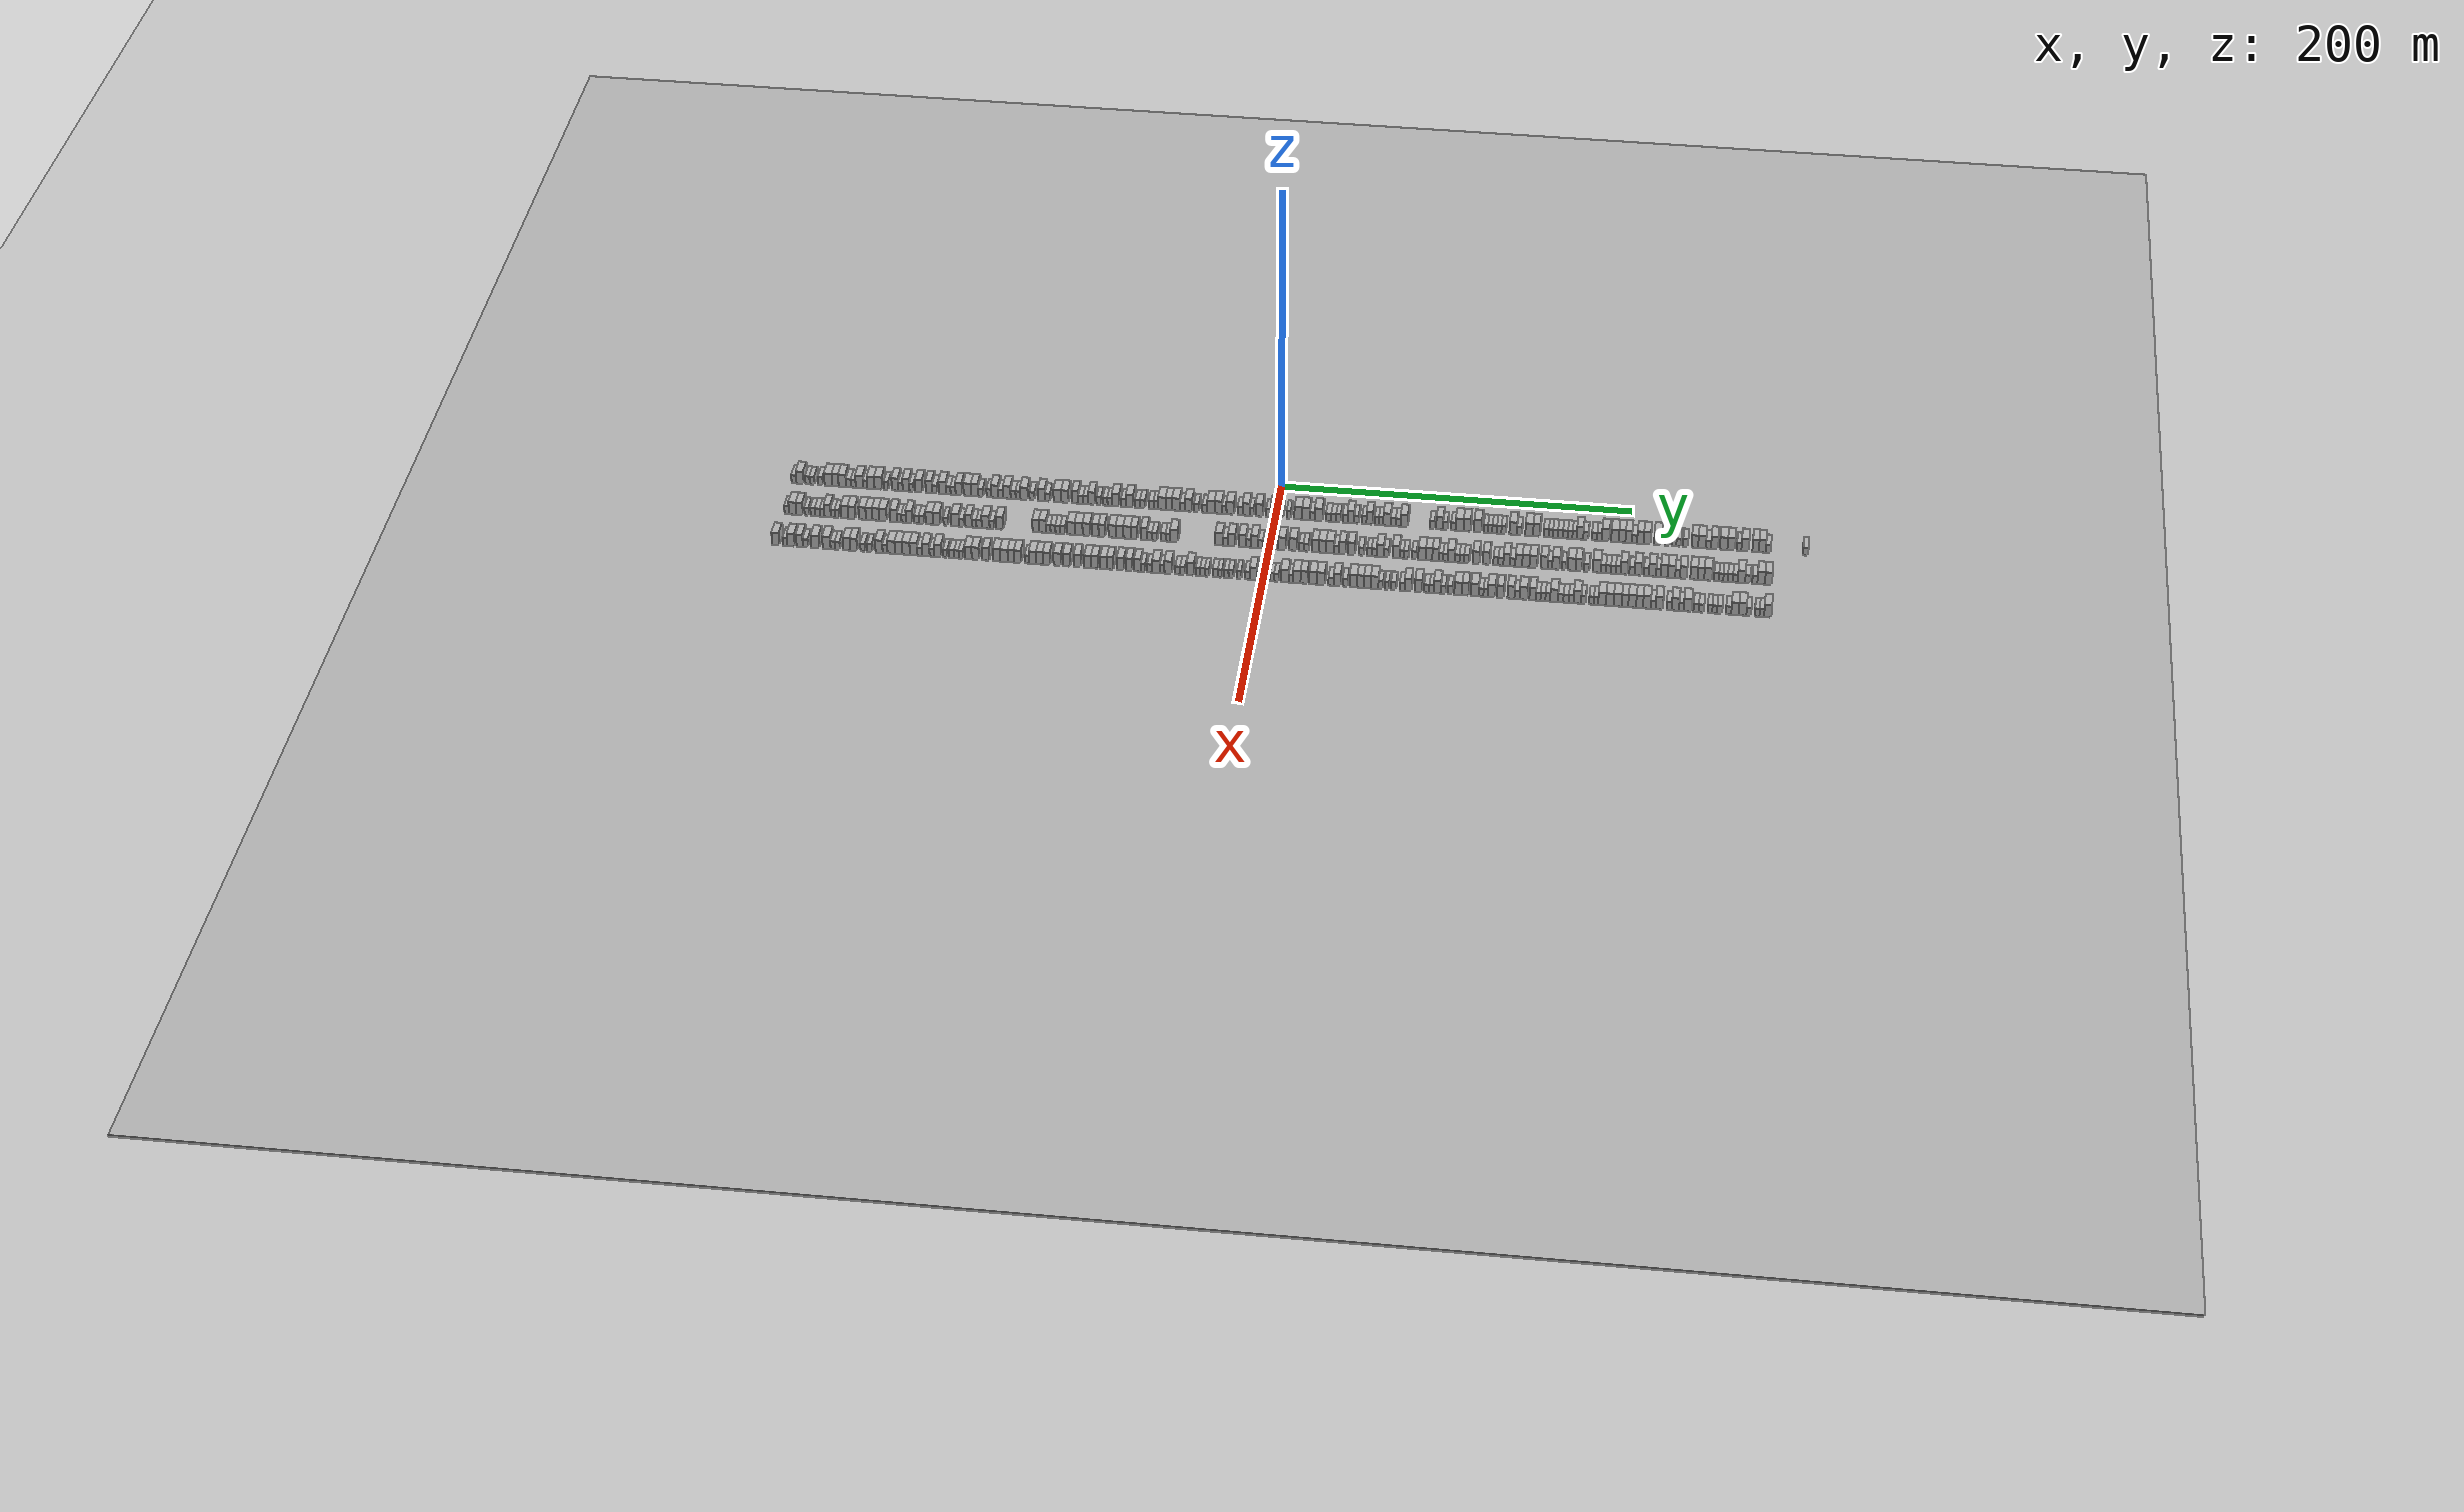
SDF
<?xml version="1.0" encoding="utf-8"?>

<sdf version="1.6">

   <world name="default">

      <gui fullscreen="0">

         <camera name="user_camera">

            <pose>-15 0 4.57585 0 0 0</pose>

            <view_controller>orbit</view_controller>

         </camera>

      </gui>

      <scene>

         <sky>

           <clouds>

             <speed>12</speed>

           </clouds>

         </sky>

         <ambient>0.4 0.4 0.4 1</ambient>

         <background>0.7 0.7 0.7 1</background>

         <shadows>1</shadows>

      </scene>

      <gravity>0 0 -9.8066</gravity>

      <magnetic_field>6e-06 2.3e-05 -4.2e-05</magnetic_field>

      <physics default="0" name="default_physics" type="ode">

         <ode>

            <solver>

               <type>quick</type>

               <iters>10</iters>

               <sor>1.0</sor>

               <use_dynamic_moi_rescaling>0</use_dynamic_moi_rescaling>

            </solver>

            <constraints>

               <cfm>0</cfm>

               <erp>0.2</erp>

               <contact_max_correcting_vel>100</contact_max_correcting_vel>

               <contact_surface_layer>0.001</contact_surface_layer>

            </constraints>

         </ode>

         <max_step_size>0.004</max_step_size>

         <real_time_factor>1</real_time_factor>

         <real_time_update_rate>250</real_time_update_rate>

      </physics>

      <light name="sun" type="directional">

         <cast_shadows>1</cast_shadows>

         <pose>0 0 10 0 0 0</pose>

         <diffuse>0.8 0.8 0.8 1</diffuse>

         <specular>0.2 0.2 0.2 1</specular>

         <attenuation>

            <range>1000</range>

            <constant>0.9</constant>

            <linear>0.01</linear>

            <quadratic>0.001</quadratic>

         </attenuation>

         <direction>-0.5 0.1 -0.9</direction>

      </light>

      <include>

         <name>ground_plane_1</name>

         <uri>model://HANNAS_ground_plane</uri>

         <pose>0 0 0  0 0 0</pose>

      </include>

      <include>

         <name>ground_plane_2</name>

         <uri>model://HANNAS_ground_plane</uri>

         <pose>100 0 0  0 0 0</pose>

      </include>

      <model name="building_1">

         <static>1</static>

         <pose frame="">25.0000 -278.6307 0 0.000000 0.000000 0.000000</pose>

         <link name="link">

            <pose frame="">0 0 3.00 0 0 0</pose>

            <collision name="collision">

               <geometry>

                  <box>

                     <size>10.0000 2.7387 6.0000</size>

                  </box>

               </geometry>

               <max_contacts>10</max_contacts>

               <surface>

                  <contact>

                     <ode/>

                  </contact>

                  <bounce/>

                  <friction>

                     <torsional>

                        <ode/>

                     </torsional>

                     <ode/>

                  </friction>

               </surface>

            </collision>

            <visual name="visual">

               <cast_shadows>0</cast_shadows>

               <geometry>

                  <box>

                     <size>10.0000 2.7387 6.0000</size>

                  </box>

               </geometry>

               <material>

                  <script>

                     <uri>model://HANNAS_wall/materials/scripts</uri>

                     <uri>model://HANNAS_wall/materials/textures</uri>

                     <name>vrc/HANNAS_wall</name>

                  </script>

               </material>

            </visual>

            <self_collide>0</self_collide>

            <enable_wind>0</enable_wind>

            <kinematic>0</kinematic>

         </link>

      </model>

      <model name="building_2">

         <static>1</static>

         <pose frame="">25.0000 -275.0952 0 0.000000 0.000000 0.000000</pose>

         <link name="link">

            <pose frame="">0 0 4.50 0 0 0</pose>

            <collision name="collision">

               <geometry>

                  <box>

                     <size>10.0000 4.3321 9.0000</size>

                  </box>

               </geometry>

               <max_contacts>10</max_contacts>

               <surface>

                  <contact>

                     <ode/>

                  </contact>

                  <bounce/>

                  <friction>

                     <torsional>

                        <ode/>

                     </torsional>

                     <ode/>

                  </friction>

               </surface>

            </collision>

            <visual name="visual">

               <cast_shadows>0</cast_shadows>

               <geometry>

                  <box>

                     <size>10.0000 4.3321 9.0000</size>

                  </box>

               </geometry>

               <material>

                  <script>

                     <uri>model://HANNAS_wall/materials/scripts</uri>

                     <uri>model://HANNAS_wall/materials/textures</uri>

                     <name>vrc/HANNAS_wall</name>

                  </script>

               </material>

            </visual>

            <self_collide>0</self_collide>

            <enable_wind>0</enable_wind>

            <kinematic>0</kinematic>

         </link>

      </model>

      <model name="building_3">

         <static>1</static>

         <pose frame="">25.0000 -270.6783 0 0.000000 0.000000 0.000000</pose>

         <link name="link">

            <pose frame="">0 0 3.00 0 0 0</pose>

            <collision name="collision">

               <geometry>

                  <box>

                     <size>10.0000 2.5017 6.0000</size>

                  </box>

               </geometry>

               <max_contacts>10</max_contacts>

               <surface>

                  <contact>

                     <ode/>

                  </contact>

                  <bounce/>

                  <friction>

                     <torsional>

                        <ode/>

                     </torsional>

                     <ode/>

                  </friction>

               </surface>

            </collision>

            <visual name="visual">

               <cast_shadows>0</cast_shadows>

               <geometry>

                  <box>

                     <size>10.0000 2.5017 6.0000</size>

                  </box>

               </geometry>

               <material>

                  <script>

                     <uri>model://HANNAS_wall/materials/scripts</uri>

                     <uri>model://HANNAS_wall/materials/textures</uri>

                     <name>vrc/HANNAS_wall</name>

                  </script>

               </material>

            </visual>

            <self_collide>0</self_collide>

            <enable_wind>0</enable_wind>

            <kinematic>0</kinematic>

         </link>

      </model>

      <model name="building_4">

         <static>1</static>

         <pose frame="">25.0000 -268.0065 0 0.000000 0.000000 0.000000</pose>

         <link name="link">

            <pose frame="">0 0 3.00 0 0 0</pose>

            <collision name="collision">

               <geometry>

                  <box>

                     <size>10.0000 2.8418 6.0000</size>

                  </box>

               </geometry>

               <max_contacts>10</max_contacts>

               <surface>

                  <contact>

                     <ode/>

                  </contact>

                  <bounce/>

                  <friction>

                     <torsional>

                        <ode/>

                     </torsional>

                     <ode/>

                  </friction>

               </surface>

            </collision>

            <visual name="visual">

               <cast_shadows>0</cast_shadows>

               <geometry>

                  <box>

                     <size>10.0000 2.8418 6.0000</size>

                  </box>

               </geometry>

               <material>

                  <script>

                     <uri>model://HANNAS_wall/materials/scripts</uri>

                     <uri>model://HANNAS_wall/materials/textures</uri>

                     <name>vrc/HANNAS_wall</name>

                  </script>

               </material>

            </visual>

            <self_collide>0</self_collide>

            <enable_wind>0</enable_wind>

            <kinematic>0</kinematic>

         </link>

      </model>

      <model name="building_5">

         <static>1</static>

         <pose frame="">25.0000 -263.1938 0 0.000000 0.000000 0.000000</pose>

         <link name="link">

            <pose frame="">0 0 3.00 0 0 0</pose>

            <collision name="collision">

               <geometry>

                  <box>

                     <size>10.0000 2.7837 6.0000</size>

                  </box>

               </geometry>

               <max_contacts>10</max_contacts>

               <surface>

                  <contact>

                     <ode/>

                  </contact>

                  <bounce/>

                  <friction>

                     <torsional>

                        <ode/>

                     </torsional>

                     <ode/>

                  </friction>

               </surface>

            </collision>

            <visual name="visual">

               <cast_shadows>0</cast_shadows>

               <geometry>

                  <box>

                     <size>10.0000 2.7837 6.0000</size>

                  </box>

               </geometry>

               <material>

                  <script>

                     <uri>model://HANNAS_wall/materials/scripts</uri>

                     <uri>model://HANNAS_wall/materials/textures</uri>

                     <name>vrc/HANNAS_wall</name>

                  </script>

               </material>

            </visual>

            <self_collide>0</self_collide>

            <enable_wind>0</enable_wind>

            <kinematic>0</kinematic>

         </link>

      </model>

      <model name="building_6">

         <static>1</static>

         <pose frame="">25.0000 -258.5552 0 0.000000 0.000000 0.000000</pose>

         <link name="link">

            <pose frame="">0 0 4.50 0 0 0</pose>

            <collision name="collision">

               <geometry>

                  <box>

                     <size>10.0000 4.4935 9.0000</size>

                  </box>

               </geometry>

               <max_contacts>10</max_contacts>

               <surface>

                  <contact>

                     <ode/>

                  </contact>

                  <bounce/>

                  <friction>

                     <torsional>

                        <ode/>

                     </torsional>

                     <ode/>

                  </friction>

               </surface>

            </collision>

            <visual name="visual">

               <cast_shadows>0</cast_shadows>

               <geometry>

                  <box>

                     <size>10.0000 4.4935 9.0000</size>

                  </box>

               </geometry>

               <material>

                  <script>

                     <uri>model://HANNAS_wall/materials/scripts</uri>

                     <uri>model://HANNAS_wall/materials/textures</uri>

                     <name>vrc/HANNAS_wall</name>

                  </script>

               </material>

            </visual>

            <self_collide>0</self_collide>

            <enable_wind>0</enable_wind>

            <kinematic>0</kinematic>

         </link>

      </model>

      <model name="building_7">

         <static>1</static>

         <pose frame="">25.0000 -254.4712 0 0.000000 0.000000 0.000000</pose>

         <link name="link">

            <pose frame="">0 0 4.50 0 0 0</pose>

            <collision name="collision">

               <geometry>

                  <box>

                     <size>10.0000 3.6745 9.0000</size>

                  </box>

               </geometry>

               <max_contacts>10</max_contacts>

               <surface>

                  <contact>

                     <ode/>

                  </contact>

                  <bounce/>

                  <friction>

                     <torsional>

                        <ode/>

                     </torsional>

                     <ode/>

                  </friction>

               </surface>

            </collision>

            <visual name="visual">

               <cast_shadows>0</cast_shadows>

               <geometry>

                  <box>

                     <size>10.0000 3.6745 9.0000</size>

                  </box>

               </geometry>

               <material>

                  <script>

                     <uri>model://HANNAS_wall/materials/scripts</uri>

                     <uri>model://HANNAS_wall/materials/textures</uri>

                     <name>vrc/HANNAS_wall</name>

                  </script>

               </material>

            </visual>

            <self_collide>0</self_collide>

            <enable_wind>0</enable_wind>

            <kinematic>0</kinematic>

         </link>

      </model>

      <model name="building_8">

         <static>1</static>

         <pose frame="">25.0000 -250.4706 0 0.000000 0.000000 0.000000</pose>

         <link name="link">

            <pose frame="">0 0 4.50 0 0 0</pose>

            <collision name="collision">

               <geometry>

                  <box>

                     <size>10.0000 4.3267 9.0000</size>

                  </box>

               </geometry>

               <max_contacts>10</max_contacts>

               <surface>

                  <contact>

                     <ode/>

                  </contact>

                  <bounce/>

                  <friction>

                     <torsional>

                        <ode/>

                     </torsional>

                     <ode/>

                  </friction>

               </surface>

            </collision>

            <visual name="visual">

               <cast_shadows>0</cast_shadows>

               <geometry>

                  <box>

                     <size>10.0000 4.3267 9.0000</size>

                  </box>

               </geometry>

               <material>

                  <script>

                     <uri>model://HANNAS_wall/materials/scripts</uri>

                     <uri>model://HANNAS_wall/materials/textures</uri>

                     <name>vrc/HANNAS_wall</name>

                  </script>

               </material>

            </visual>

            <self_collide>0</self_collide>

            <enable_wind>0</enable_wind>

            <kinematic>0</kinematic>

         </link>

      </model>

      <model name="building_9">

         <static>1</static>

         <pose frame="">25.0000 -246.8789 0 0.000000 0.000000 0.000000</pose>

         <link name="link">

            <pose frame="">0 0 3.00 0 0 0</pose>

            <collision name="collision">

               <geometry>

                  <box>

                     <size>10.0000 2.8567 6.0000</size>

                  </box>

               </geometry>

               <max_contacts>10</max_contacts>

               <surface>

                  <contact>

                     <ode/>

                  </contact>

                  <bounce/>

                  <friction>

                     <torsional>

                        <ode/>

                     </torsional>

                     <ode/>

                  </friction>

               </surface>

            </collision>

            <visual name="visual">

               <cast_shadows>0</cast_shadows>

               <geometry>

                  <box>

                     <size>10.0000 2.8567 6.0000</size>

                  </box>

               </geometry>

               <material>

                  <script>

                     <uri>model://HANNAS_wall/materials/scripts</uri>

                     <uri>model://HANNAS_wall/materials/textures</uri>

                     <name>vrc/HANNAS_wall</name>

                  </script>

               </material>

            </visual>

            <self_collide>0</self_collide>

            <enable_wind>0</enable_wind>

            <kinematic>0</kinematic>

         </link>

      </model>

      <model name="building_10">

         <static>1</static>

         <pose frame="">25.0000 -244.0544 0 0.000000 0.000000 0.000000</pose>

         <link name="link">

            <pose frame="">0 0 3.00 0 0 0</pose>

            <collision name="collision">

               <geometry>

                  <box>

                     <size>10.0000 2.7923 6.0000</size>

                  </box>

               </geometry>

               <max_contacts>10</max_contacts>

               <surface>

                  <contact>

                     <ode/>

                  </contact>

                  <bounce/>

                  <friction>

                     <torsional>

                        <ode/>

                     </torsional>

                     <ode/>

                  </friction>

               </surface>

            </collision>

            <visual name="visual">

               <cast_shadows>0</cast_shadows>

               <geometry>

                  <box>

                     <size>10.0000 2.7923 6.0000</size>

                  </box>

               </geometry>

               <material>

                  <script>

                     <uri>model://HANNAS_wall/materials/scripts</uri>

                     <uri>model://HANNAS_wall/materials/textures</uri>

                     <name>vrc/HANNAS_wall</name>

                  </script>

               </material>

            </visual>

            <self_collide>0</self_collide>

            <enable_wind>0</enable_wind>

            <kinematic>0</kinematic>

         </link>

      </model>

      <model name="building_11">

         <static>1</static>

         <pose frame="">25.0000 -240.4963 0 0.000000 0.000000 0.000000</pose>

         <link name="link">

            <pose frame="">0 0 4.50 0 0 0</pose>

            <collision name="collision">

               <geometry>

                  <box>

                     <size>10.0000 4.3238 9.0000</size>

                  </box>

               </geometry>

               <max_contacts>10</max_contacts>

               <surface>

                  <contact>

                     <ode/>

                  </contact>

                  <bounce/>

                  <friction>

                     <torsional>

                        <ode/>

                     </torsional>

                     <ode/>

                  </friction>

               </surface>

            </collision>

            <visual name="visual">

               <cast_shadows>0</cast_shadows>

               <geometry>

                  <box>

                     <size>10.0000 4.3238 9.0000</size>

                  </box>

               </geometry>

               <material>

                  <script>

                     <uri>model://HANNAS_wall/materials/scripts</uri>

                     <uri>model://HANNAS_wall/materials/textures</uri>

                     <name>vrc/HANNAS_wall</name>

                  </script>

               </material>

            </visual>

            <self_collide>0</self_collide>

            <enable_wind>0</enable_wind>

            <kinematic>0</kinematic>

         </link>

      </model>

      <model name="building_12">

         <static>1</static>

         <pose frame="">25.0000 -237.1206 0 0.000000 0.000000 0.000000</pose>

         <link name="link">

            <pose frame="">0 0 3.00 0 0 0</pose>

            <collision name="collision">

               <geometry>

                  <box>

                     <size>10.0000 2.4275 6.0000</size>

                  </box>

               </geometry>

               <max_contacts>10</max_contacts>

               <surface>

                  <contact>

                     <ode/>

                  </contact>

                  <bounce/>

                  <friction>

                     <torsional>

                        <ode/>

                     </torsional>

                     <ode/>

                  </friction>

               </surface>

            </collision>

            <visual name="visual">

               <cast_shadows>0</cast_shadows>

               <geometry>

                  <box>

                     <size>10.0000 2.4275 6.0000</size>

                  </box>

               </geometry>

               <material>

                  <script>

                     <uri>model://HANNAS_wall/materials/scripts</uri>

                     <uri>model://HANNAS_wall/materials/textures</uri>

                     <name>vrc/HANNAS_wall</name>

                  </script>

               </material>

            </visual>

            <self_collide>0</self_collide>

            <enable_wind>0</enable_wind>

            <kinematic>0</kinematic>

         </link>

      </model>

      <model name="building_13">

         <static>1</static>

         <pose frame="">25.0000 -233.8196 0 0.000000 0.000000 0.000000</pose>

         <link name="link">

            <pose frame="">0 0 4.50 0 0 0</pose>

            <collision name="collision">

               <geometry>

                  <box>

                     <size>10.0000 4.1745 9.0000</size>

                  </box>

               </geometry>

               <max_contacts>10</max_contacts>

               <surface>

                  <contact>

                     <ode/>

                  </contact>

                  <bounce/>

                  <friction>

                     <torsional>

                        <ode/>

                     </torsional>

                     <ode/>

                  </friction>

               </surface>

            </collision>

            <visual name="visual">

               <cast_shadows>0</cast_shadows>

               <geometry>

                  <box>

                     <size>10.0000 4.1745 9.0000</size>

                  </box>

               </geometry>

               <material>

                  <script>

                     <uri>model://HANNAS_wall/materials/scripts</uri>

                     <uri>model://HANNAS_wall/materials/textures</uri>

                     <name>vrc/HANNAS_wall</name>

                  </script>

               </material>

            </visual>

            <self_collide>0</self_collide>

            <enable_wind>0</enable_wind>

            <kinematic>0</kinematic>

         </link>

      </model>

      <model name="building_14">

         <static>1</static>

         <pose frame="">25.0000 -229.5177 0 0.000000 0.000000 0.000000</pose>

         <link name="link">

            <pose frame="">0 0 4.50 0 0 0</pose>

            <collision name="collision">

               <geometry>

                  <box>

                     <size>10.0000 4.4293 9.0000</size>

                  </box>

               </geometry>

               <max_contacts>10</max_contacts>

               <surface>

                  <contact>

                     <ode/>

                  </contact>

                  <bounce/>

                  <friction>

                     <torsional>

                        <ode/>

                     </torsional>

                     <ode/>

                  </friction>

               </surface>

            </collision>

            <visual name="visual">

               <cast_shadows>0</cast_shadows>

               <geometry>

                  <box>

                     <size>10.0000 4.4293 9.0000</size>

                  </box>

               </geometry>

               <material>

                  <script>

                     <uri>model://HANNAS_wall/materials/scripts</uri>

                     <uri>model://HANNAS_wall/materials/textures</uri>

                     <name>vrc/HANNAS_wall</name>

                  </script>

               </material>

            </visual>

            <self_collide>0</self_collide>

            <enable_wind>0</enable_wind>

            <kinematic>0</kinematic>

         </link>

      </model>

      <model name="building_15">

         <static>1</static>

         <pose frame="">25.0000 -224.9879 0 0.000000 0.000000 0.000000</pose>

         <link name="link">

            <pose frame="">0 0 3.00 0 0 0</pose>

            <collision name="collision">

               <geometry>

                  <box>

                     <size>10.0000 2.6302 6.0000</size>

                  </box>

               </geometry>

               <max_contacts>10</max_contacts>

               <surface>

                  <contact>

                     <ode/>

                  </contact>

                  <bounce/>

                  <friction>

                     <torsional>

                        <ode/>

                     </torsional>

                     <ode/>

                  </friction>

               </surface>

            </collision>

            <visual name="visual">

               <cast_shadows>0</cast_shadows>

               <geometry>

                  <box>

                     <size>10.0000 2.6302 6.0000</size>

                  </box>

               </geometry>

               <material>

                  <script>

                     <uri>model://HANNAS_wall/materials/scripts</uri>

                     <uri>model://HANNAS_wall/materials/textures</uri>

                     <name>vrc/HANNAS_wall</name>

                  </script>

               </material>

            </visual>

            <self_collide>0</self_collide>

            <enable_wind>0</enable_wind>

            <kinematic>0</kinematic>

         </link>

      </model>

      <model name="building_16">

         <static>1</static>

         <pose frame="">25.0000 -219.8191 0 0.000000 0.000000 0.000000</pose>

         <link name="link">

            <pose frame="">0 0 4.50 0 0 0</pose>

            <collision name="collision">

               <geometry>

                  <box>

                     <size>10.0000 3.7073 9.0000</size>

                  </box>

               </geometry>

               <max_contacts>10</max_contacts>

               <surface>

                  <contact>

                     <ode/>

                  </contact>

                  <bounce/>

                  <friction>

                     <torsional>

                        <ode/>

                     </torsional>

                     <ode/>

                  </friction>

               </surface>

            </collision>

            <visual name="visual">

               <cast_shadows>0</cast_shadows>

               <geometry>

                  <box>

                     <size>10.0000 3.7073 9.0000</size>

                  </box>

               </geometry>

               <material>

                  <script>

                     <uri>model://HANNAS_wall/materials/scripts</uri>

                     <uri>model://HANNAS_wall/materials/textures</uri>

                     <name>vrc/HANNAS_wall</name>

                  </script>

               </material>

            </visual>

            <self_collide>0</self_collide>

            <enable_wind>0</enable_wind>

            <kinematic>0</kinematic>

         </link>

      </model>

      <model name="building_17">

         <static>1</static>

         <pose frame="">25.0000 -216.6659 0 0.000000 0.000000 0.000000</pose>

         <link name="link">

            <pose frame="">0 0 3.00 0 0 0</pose>

            <collision name="collision">

               <geometry>

                  <box>

                     <size>10.0000 2.5991 6.0000</size>

                  </box>

               </geometry>

               <max_contacts>10</max_contacts>

               <surface>

                  <contact>

                     <ode/>

                  </contact>

                  <bounce/>

                  <friction>

                     <torsional>

                        <ode/>

                     </torsional>

                     <ode/>

                  </friction>

               </surface>

            </collision>

            <visual name="visual">

               <cast_shadows>0</cast_shadows>

               <geometry>

                  <box>

                     <size>10.0000 2.5991 6.0000</size>

                  </box>

               </geometry>

               <material>

                  <script>

                     <uri>model://HANNAS_wall/materials/scripts</uri>

                     <uri>model://HANNAS_wall/materials/textures</uri>

                     <name>vrc/HANNAS_wall</name>

                  </script>

               </material>

            </visual>

            <self_collide>0</self_collide>

            <enable_wind>0</enable_wind>

            <kinematic>0</kinematic>

         </link>

      </model>

      <model name="building_18">

         <static>1</static>

         <pose frame="">25.0000 -213.4011 0 0.000000 0.000000 0.000000</pose>

         <link name="link">

            <pose frame="">0 0 4.50 0 0 0</pose>

            <collision name="collision">

               <geometry>

                  <box>

                     <size>10.0000 3.9306 9.0000</size>

                  </box>

               </geometry>

               <max_contacts>10</max_contacts>

               <surface>

                  <contact>

                     <ode/>

                  </contact>

                  <bounce/>

                  <friction>

                     <torsional>

                        <ode/>

                     </torsional>

                     <ode/>

                  </friction>

               </surface>

            </collision>

            <visual name="visual">

               <cast_shadows>0</cast_shadows>

               <geometry>

                  <box>

                     <size>10.0000 3.9306 9.0000</size>

                  </box>

               </geometry>

               <material>

                  <script>

                     <uri>model://HANNAS_wall/materials/scripts</uri>

                     <uri>model://HANNAS_wall/materials/textures</uri>

                     <name>vrc/HANNAS_wall</name>

                  </script>

               </material>

            </visual>

            <self_collide>0</self_collide>

            <enable_wind>0</enable_wind>

            <kinematic>0</kinematic>

         </link>

      </model>

      <model name="building_19">

         <static>1</static>

         <pose frame="">25.0000 -210.2322 0 0.000000 0.000000 0.000000</pose>

         <link name="link">

            <pose frame="">0 0 3.00 0 0 0</pose>

            <collision name="collision">

               <geometry>

                  <box>

                     <size>10.0000 2.4073 6.0000</size>

                  </box>

               </geometry>

               <max_contacts>10</max_contacts>

               <surface>

                  <contact>

                     <ode/>

                  </contact>

                  <bounce/>

                  <friction>

                     <torsional>

                        <ode/>

                     </torsional>

                     <ode/>

                  </friction>

               </surface>

            </collision>

            <visual name="visual">

               <cast_shadows>0</cast_shadows>

               <geometry>

                  <box>

                     <size>10.0000 2.4073 6.0000</size>

                  </box>

               </geometry>

               <material>

                  <script>

                     <uri>model://HANNAS_wall/materials/scripts</uri>

                     <uri>model://HANNAS_wall/materials/textures</uri>

                     <name>vrc/HANNAS_wall</name>

                  </script>

               </material>

            </visual>

            <self_collide>0</self_collide>

            <enable_wind>0</enable_wind>

            <kinematic>0</kinematic>

         </link>

      </model>

      <model name="building_20">

         <static>1</static>

         <pose frame="">25.0000 -205.9997 0 0.000000 0.000000 0.000000</pose>

         <link name="link">

            <pose frame="">0 0 4.50 0 0 0</pose>

            <collision name="collision">

               <geometry>

                  <box>

                     <size>10.0000 4.0576 9.0000</size>

                  </box>

               </geometry>

               <max_contacts>10</max_contacts>

               <surface>

                  <contact>

                     <ode/>

                  </contact>

                  <bounce/>

                  <friction>

                     <torsional>

                        <ode/>

                     </torsional>

                     <ode/>

                  </friction>

               </surface>

            </collision>

            <visual name="visual">

               <cast_shadows>0</cast_shadows>

               <geometry>

                  <box>

                     <size>10.0000 4.0576 9.0000</size>

                  </box>

               </geometry>

               <material>

                  <script>

                     <uri>model://HANNAS_wall/materials/scripts</uri>

                     <uri>model://HANNAS_wall/materials/textures</uri>

                     <name>vrc/HANNAS_wall</name>

                  </script>

               </material>

            </visual>

            <self_collide>0</self_collide>

            <enable_wind>0</enable_wind>

            <kinematic>0</kinematic>

         </link>

      </model>

      <model name="building_21">

         <static>1</static>

         <pose frame="">25.0000 -200.1270 0 0.000000 0.000000 0.000000</pose>

         <link name="link">

            <pose frame="">0 0 4.50 0 0 0</pose>

            <collision name="collision">

               <geometry>

                  <box>

                     <size>10.0000 3.6879 9.0000</size>

                  </box>

               </geometry>

               <max_contacts>10</max_contacts>

               <surface>

                  <contact>

                     <ode/>

                  </contact>

                  <bounce/>

                  <friction>

                     <torsional>

                        <ode/>

                     </torsional>

                     <ode/>

                  </friction>

               </surface>

            </collision>

            <visual name="visual">

               <cast_shadows>0</cast_shadows>

               <geometry>

                  <box>

                     <size>10.0000 3.6879 9.0000</size>

                  </box>

               </geometry>

               <material>

                  <script>

                     <uri>model://HANNAS_wall/materials/scripts</uri>

                     <uri>model://HANNAS_wall/materials/textures</uri>

                     <name>vrc/HANNAS_wall</name>

                  </script>

               </material>

            </visual>

            <self_collide>0</self_collide>

            <enable_wind>0</enable_wind>

            <kinematic>0</kinematic>

         </link>

      </model>

      <model name="building_22">

         <static>1</static>

         <pose frame="">25.0000 -196.8470 0 0.000000 0.000000 0.000000</pose>

         <link name="link">

            <pose frame="">0 0 3.00 0 0 0</pose>

            <collision name="collision">

               <geometry>

                  <box>

                     <size>10.0000 2.8722 6.0000</size>

                  </box>

               </geometry>

               <max_contacts>10</max_contacts>

               <surface>

                  <contact>

                     <ode/>

                  </contact>

                  <bounce/>

                  <friction>

                     <torsional>

                        <ode/>

                     </torsional>

                     <ode/>

                  </friction>

               </surface>

            </collision>

            <visual name="visual">

               <cast_shadows>0</cast_shadows>

               <geometry>

                  <box>

                     <size>10.0000 2.8722 6.0000</size>

                  </box>

               </geometry>

               <material>

                  <script>

                     <uri>model://HANNAS_wall/materials/scripts</uri>

                     <uri>model://HANNAS_wall/materials/textures</uri>

                     <name>vrc/HANNAS_wall</name>

                  </script>

               </material>

            </visual>

            <self_collide>0</self_collide>

            <enable_wind>0</enable_wind>

            <kinematic>0</kinematic>

         </link>

      </model>

      <model name="building_23">

         <static>1</static>

         <pose frame="">25.0000 -192.3407 0 0.000000 0.000000 0.000000</pose>

         <link name="link">

            <pose frame="">0 0 4.50 0 0 0</pose>

            <collision name="collision">

               <geometry>

                  <box>

                     <size>10.0000 4.1403 9.0000</size>

                  </box>

               </geometry>

               <max_contacts>10</max_contacts>

               <surface>

                  <contact>

                     <ode/>

                  </contact>

                  <bounce/>

                  <friction>

                     <torsional>

                        <ode/>

                     </torsional>

                     <ode/>

                  </friction>

               </surface>

            </collision>

            <visual name="visual">

               <cast_shadows>0</cast_shadows>

               <geometry>

                  <box>

                     <size>10.0000 4.1403 9.0000</size>

                  </box>

               </geometry>

               <material>

                  <script>

                     <uri>model://HANNAS_wall/materials/scripts</uri>

                     <uri>model://HANNAS_wall/materials/textures</uri>

                     <name>vrc/HANNAS_wall</name>

                  </script>

               </material>

            </visual>

            <self_collide>0</self_collide>

            <enable_wind>0</enable_wind>

            <kinematic>0</kinematic>

         </link>

      </model>

      <model name="building_24">

         <static>1</static>

         <pose frame="">25.0000 -188.9480 0 0.000000 0.000000 0.000000</pose>

         <link name="link">

            <pose frame="">0 0 3.00 0 0 0</pose>

            <collision name="collision">

               <geometry>

                  <box>

                     <size>10.0000 2.6451 6.0000</size>

                  </box>

               </geometry>

               <max_contacts>10</max_contacts>

               <surface>

                  <contact>

                     <ode/>

                  </contact>

                  <bounce/>

                  <friction>

                     <torsional>

                        <ode/>

                     </torsional>

                     <ode/>

                  </friction>

               </surface>

            </collision>

            <visual name="visual">

               <cast_shadows>0</cast_shadows>

               <geometry>

                  <box>

                     <size>10.0000 2.6451 6.0000</size>

                  </box>

               </geometry>

               <material>

                  <script>

                     <uri>model://HANNAS_wall/materials/scripts</uri>

                     <uri>model://HANNAS_wall/materials/textures</uri>

                     <name>vrc/HANNAS_wall</name>

                  </script>

               </material>

            </visual>

            <self_collide>0</self_collide>

            <enable_wind>0</enable_wind>

            <kinematic>0</kinematic>

         </link>

      </model>

      <model name="building_25">

         <static>1</static>

         <pose frame="">25.0000 -186.1786 0 0.000000 0.000000 0.000000</pose>

         <link name="link">

            <pose frame="">0 0 3.00 0 0 0</pose>

            <collision name="collision">

               <geometry>

                  <box>

                     <size>10.0000 2.8938 6.0000</size>

                  </box>

               </geometry>

               <max_contacts>10</max_contacts>

               <surface>

                  <contact>

                     <ode/>

                  </contact>

                  <bounce/>

                  <friction>

                     <torsional>

                        <ode/>

                     </torsional>

                     <ode/>

                  </friction>

               </surface>

            </collision>

            <visual name="visual">

               <cast_shadows>0</cast_shadows>

               <geometry>

                  <box>

                     <size>10.0000 2.8938 6.0000</size>

                  </box>

               </geometry>

               <material>

                  <script>

                     <uri>model://HANNAS_wall/materials/scripts</uri>

                     <uri>model://HANNAS_wall/materials/textures</uri>

                     <name>vrc/HANNAS_wall</name>

                  </script>

               </material>

            </visual>

            <self_collide>0</self_collide>

            <enable_wind>0</enable_wind>

            <kinematic>0</kinematic>

         </link>

      </model>

      <model name="building_26">

         <static>1</static>

         <pose frame="">25.0000 -182.8874 0 0.000000 0.000000 0.000000</pose>

         <link name="link">

            <pose frame="">0 0 4.50 0 0 0</pose>

            <collision name="collision">

               <geometry>

                  <box>

                     <size>10.0000 3.6885 9.0000</size>

                  </box>

               </geometry>

               <max_contacts>10</max_contacts>

               <surface>

                  <contact>

                     <ode/>

                  </contact>

                  <bounce/>

                  <friction>

                     <torsional>

                        <ode/>

                     </torsional>

                     <ode/>

                  </friction>

               </surface>

            </collision>

            <visual name="visual">

               <cast_shadows>0</cast_shadows>

               <geometry>

                  <box>

                     <size>10.0000 3.6885 9.0000</size>

                  </box>

               </geometry>

               <material>

                  <script>

                     <uri>model://HANNAS_wall/materials/scripts</uri>

                     <uri>model://HANNAS_wall/materials/textures</uri>

                     <name>vrc/HANNAS_wall</name>

                  </script>

               </material>

            </visual>

            <self_collide>0</self_collide>

            <enable_wind>0</enable_wind>

            <kinematic>0</kinematic>

         </link>

      </model>

      <model name="building_27">

         <static>1</static>

         <pose frame="">25.0000 -177.8698 0 0.000000 0.000000 0.000000</pose>

         <link name="link">

            <pose frame="">0 0 4.50 0 0 0</pose>

            <collision name="collision">

               <geometry>

                  <box>

                     <size>10.0000 4.3468 9.0000</size>

                  </box>

               </geometry>

               <max_contacts>10</max_contacts>

               <surface>

                  <contact>

                     <ode/>

                  </contact>

                  <bounce/>

                  <friction>

                     <torsional>

                        <ode/>

                     </torsional>

                     <ode/>

                  </friction>

               </surface>

            </collision>

            <visual name="visual">

               <cast_shadows>0</cast_shadows>

               <geometry>

                  <box>

                     <size>10.0000 4.3468 9.0000</size>

                  </box>

               </geometry>

               <material>

                  <script>

                     <uri>model://HANNAS_wall/materials/scripts</uri>

                     <uri>model://HANNAS_wall/materials/textures</uri>

                     <name>vrc/HANNAS_wall</name>

                  </script>

               </material>

            </visual>

            <self_collide>0</self_collide>

            <enable_wind>0</enable_wind>

            <kinematic>0</kinematic>

         </link>

      </model>

      <model name="building_28">

         <static>1</static>

         <pose frame="">25.0000 -173.7348 0 0.000000 0.000000 0.000000</pose>

         <link name="link">

            <pose frame="">0 0 4.50 0 0 0</pose>

            <collision name="collision">

               <geometry>

                  <box>

                     <size>10.0000 3.9231 9.0000</size>

                  </box>

               </geometry>

               <max_contacts>10</max_contacts>

               <surface>

                  <contact>

                     <ode/>

                  </contact>

                  <bounce/>

                  <friction>

                     <torsional>

                        <ode/>

                     </torsional>

                     <ode/>

                  </friction>

               </surface>

            </collision>

            <visual name="visual">

               <cast_shadows>0</cast_shadows>

               <geometry>

                  <box>

                     <size>10.0000 3.9231 9.0000</size>

                  </box>

               </geometry>

               <material>

                  <script>

                     <uri>model://HANNAS_wall/materials/scripts</uri>

                     <uri>model://HANNAS_wall/materials/textures</uri>

                     <name>vrc/HANNAS_wall</name>

                  </script>

               </material>

            </visual>

            <self_collide>0</self_collide>

            <enable_wind>0</enable_wind>

            <kinematic>0</kinematic>

         </link>

      </model>

      <model name="building_29">

         <static>1</static>

         <pose frame="">25.0000 -170.2793 0 0.000000 0.000000 0.000000</pose>

         <link name="link">

            <pose frame="">0 0 3.00 0 0 0</pose>

            <collision name="collision">

               <geometry>

                  <box>

                     <size>10.0000 2.9881 6.0000</size>

                  </box>

               </geometry>

               <max_contacts>10</max_contacts>

               <surface>

                  <contact>

                     <ode/>

                  </contact>

                  <bounce/>

                  <friction>

                     <torsional>

                        <ode/>

                     </torsional>

                     <ode/>

                  </friction>

               </surface>

            </collision>

            <visual name="visual">

               <cast_shadows>0</cast_shadows>

               <geometry>

                  <box>

                     <size>10.0000 2.9881 6.0000</size>

                  </box>

               </geometry>

               <material>

                  <script>

                     <uri>model://HANNAS_wall/materials/scripts</uri>

                     <uri>model://HANNAS_wall/materials/textures</uri>

                     <name>vrc/HANNAS_wall</name>

                  </script>

               </material>

            </visual>

            <self_collide>0</self_collide>

            <enable_wind>0</enable_wind>

            <kinematic>0</kinematic>

         </link>

      </model>

      <model name="building_30">

         <static>1</static>

         <pose frame="">25.0000 -165.4775 0 0.000000 0.000000 0.000000</pose>

         <link name="link">

            <pose frame="">0 0 3.00 0 0 0</pose>

            <collision name="collision">

               <geometry>

                  <box>

                     <size>10.0000 2.6154 6.0000</size>

                  </box>

               </geometry>

               <max_contacts>10</max_contacts>

               <surface>

                  <contact>

                     <ode/>

                  </contact>

                  <bounce/>

                  <friction>

                     <torsional>

                        <ode/>

                     </torsional>

                     <ode/>

                  </friction>

               </surface>

            </collision>

            <visual name="visual">

               <cast_shadows>0</cast_shadows>

               <geometry>

                  <box>

                     <size>10.0000 2.6154 6.0000</size>

                  </box>

               </geometry>

               <material>

                  <script>

                     <uri>model://HANNAS_wall/materials/scripts</uri>

                     <uri>model://HANNAS_wall/materials/textures</uri>

                     <name>vrc/HANNAS_wall</name>

                  </script>

               </material>

            </visual>

            <self_collide>0</self_collide>

            <enable_wind>0</enable_wind>

            <kinematic>0</kinematic>

         </link>

      </model>

      <model name="building_31">

         <static>1</static>

         <pose frame="">25.0000 -162.1044 0 0.000000 0.000000 0.000000</pose>

         <link name="link">

            <pose frame="">0 0 4.50 0 0 0</pose>

            <collision name="collision">

               <geometry>

                  <box>

                     <size>10.0000 4.1307 9.0000</size>

                  </box>

               </geometry>

               <max_contacts>10</max_contacts>

               <surface>

                  <contact>

                     <ode/>

                  </contact>

                  <bounce/>

                  <friction>

                     <torsional>

                        <ode/>

                     </torsional>

                     <ode/>

                  </friction>

               </surface>

            </collision>

            <visual name="visual">

               <cast_shadows>0</cast_shadows>

               <geometry>

                  <box>

                     <size>10.0000 4.1307 9.0000</size>

                  </box>

               </geometry>

               <material>

                  <script>

                     <uri>model://HANNAS_wall/materials/scripts</uri>

                     <uri>model://HANNAS_wall/materials/textures</uri>

                     <name>vrc/HANNAS_wall</name>

                  </script>

               </material>

            </visual>

            <self_collide>0</self_collide>

            <enable_wind>0</enable_wind>

            <kinematic>0</kinematic>

         </link>

      </model>

      <model name="building_32">

         <static>1</static>

         <pose frame="">25.0000 -158.6034 0 0.000000 0.000000 0.000000</pose>

         <link name="link">

            <pose frame="">0 0 3.00 0 0 0</pose>

            <collision name="collision">

               <geometry>

                  <box>

                     <size>10.0000 2.8714 6.0000</size>

                  </box>

               </geometry>

               <max_contacts>10</max_contacts>

               <surface>

                  <contact>

                     <ode/>

                  </contact>

                  <bounce/>

                  <friction>

                     <torsional>

                        <ode/>

                     </torsional>

                     <ode/>

                  </friction>

               </surface>

            </collision>

            <visual name="visual">

               <cast_shadows>0</cast_shadows>

               <geometry>

                  <box>

                     <size>10.0000 2.8714 6.0000</size>

                  </box>

               </geometry>

               <material>

                  <script>

                     <uri>model://HANNAS_wall/materials/scripts</uri>

                     <uri>model://HANNAS_wall/materials/textures</uri>

                     <name>vrc/HANNAS_wall</name>

                  </script>

               </material>

            </visual>

            <self_collide>0</self_collide>

            <enable_wind>0</enable_wind>

            <kinematic>0</kinematic>

         </link>

      </model>

      <model name="building_33">

         <static>1</static>

         <pose frame="">25.0000 -155.0268 0 0.000000 0.000000 0.000000</pose>

         <link name="link">

            <pose frame="">0 0 4.50 0 0 0</pose>

            <collision name="collision">

               <geometry>

                  <box>

                     <size>10.0000 4.2817 9.0000</size>

                  </box>

               </geometry>

               <max_contacts>10</max_contacts>

               <surface>

                  <contact>

                     <ode/>

                  </contact>

                  <bounce/>

                  <friction>

                     <torsional>

                        <ode/>

                     </torsional>

                     <ode/>

                  </friction>

               </surface>

            </collision>

            <visual name="visual">

               <cast_shadows>0</cast_shadows>

               <geometry>

                  <box>

                     <size>10.0000 4.2817 9.0000</size>

                  </box>

               </geometry>

               <material>

                  <script>

                     <uri>model://HANNAS_wall/materials/scripts</uri>

                     <uri>model://HANNAS_wall/materials/textures</uri>

                     <name>vrc/HANNAS_wall</name>

                  </script>

               </material>

            </visual>

            <self_collide>0</self_collide>

            <enable_wind>0</enable_wind>

            <kinematic>0</kinematic>

         </link>

      </model>

      <model name="building_34">

         <static>1</static>

         <pose frame="">25.0000 -151.4418 0 0.000000 0.000000 0.000000</pose>

         <link name="link">

            <pose frame="">0 0 3.00 0 0 0</pose>

            <collision name="collision">

               <geometry>

                  <box>

                     <size>10.0000 2.8883 6.0000</size>

                  </box>

               </geometry>

               <max_contacts>10</max_contacts>

               <surface>

                  <contact>

                     <ode/>

                  </contact>

                  <bounce/>

                  <friction>

                     <torsional>

                        <ode/>

                     </torsional>

                     <ode/>

                  </friction>

               </surface>

            </collision>

            <visual name="visual">

               <cast_shadows>0</cast_shadows>

               <geometry>

                  <box>

                     <size>10.0000 2.8883 6.0000</size>

                  </box>

               </geometry>

               <material>

                  <script>

                     <uri>model://HANNAS_wall/materials/scripts</uri>

                     <uri>model://HANNAS_wall/materials/textures</uri>

                     <name>vrc/HANNAS_wall</name>

                  </script>

               </material>

            </visual>

            <self_collide>0</self_collide>

            <enable_wind>0</enable_wind>

            <kinematic>0</kinematic>

         </link>

      </model>

      <model name="building_35">

         <static>1</static>

         <pose frame="">25.0000 -148.6420 0 0.000000 0.000000 0.000000</pose>

         <link name="link">

            <pose frame="">0 0 3.00 0 0 0</pose>

            <collision name="collision">

               <geometry>

                  <box>

                     <size>10.0000 2.7115 6.0000</size>

                  </box>

               </geometry>

               <max_contacts>10</max_contacts>

               <surface>

                  <contact>

                     <ode/>

                  </contact>

                  <bounce/>

                  <friction>

                     <torsional>

                        <ode/>

                     </torsional>

                     <ode/>

                  </friction>

               </surface>

            </collision>

            <visual name="visual">

               <cast_shadows>0</cast_shadows>

               <geometry>

                  <box>

                     <size>10.0000 2.7115 6.0000</size>

                  </box>

               </geometry>

               <material>

                  <script>

                     <uri>model://HANNAS_wall/materials/scripts</uri>

                     <uri>model://HANNAS_wall/materials/textures</uri>

                     <name>vrc/HANNAS_wall</name>

                  </script>

               </material>

            </visual>

            <self_collide>0</self_collide>

            <enable_wind>0</enable_wind>

            <kinematic>0</kinematic>

         </link>

      </model>

      <model name="building_36">

         <static>1</static>

         <pose frame="">25.0000 -145.1295 0 0.000000 0.000000 0.000000</pose>

         <link name="link">

            <pose frame="">0 0 4.50 0 0 0</pose>

            <collision name="collision">

               <geometry>

                  <box>

                     <size>10.0000 4.3134 9.0000</size>

                  </box>

               </geometry>

               <max_contacts>10</max_contacts>

               <surface>

                  <contact>

                     <ode/>

                  </contact>

                  <bounce/>

                  <friction>

                     <torsional>

                        <ode/>

                     </torsional>

                     <ode/>

                  </friction>

               </surface>

            </collision>

            <visual name="visual">

               <cast_shadows>0</cast_shadows>

               <geometry>

                  <box>

                     <size>10.0000 4.3134 9.0000</size>

                  </box>

               </geometry>

               <material>

                  <script>

                     <uri>model://HANNAS_wall/materials/scripts</uri>

                     <uri>model://HANNAS_wall/materials/textures</uri>

                     <name>vrc/HANNAS_wall</name>

                  </script>

               </material>

            </visual>

            <self_collide>0</self_collide>

            <enable_wind>0</enable_wind>

            <kinematic>0</kinematic>

         </link>

      </model>

      <model name="building_37">

         <static>1</static>

         <pose frame="">25.0000 -140.5147 0 0.000000 0.000000 0.000000</pose>

         <link name="link">

            <pose frame="">0 0 3.00 0 0 0</pose>

            <collision name="collision">

               <geometry>

                  <box>

                     <size>10.0000 2.9162 6.0000</size>

                  </box>

               </geometry>

               <max_contacts>10</max_contacts>

               <surface>

                  <contact>

                     <ode/>

                  </contact>

                  <bounce/>

                  <friction>

                     <torsional>

                        <ode/>

                     </torsional>

                     <ode/>

                  </friction>

               </surface>

            </collision>

            <visual name="visual">

               <cast_shadows>0</cast_shadows>

               <geometry>

                  <box>

                     <size>10.0000 2.9162 6.0000</size>

                  </box>

               </geometry>

               <material>

                  <script>

                     <uri>model://HANNAS_wall/materials/scripts</uri>

                     <uri>model://HANNAS_wall/materials/textures</uri>

                     <name>vrc/HANNAS_wall</name>

                  </script>

               </material>

            </visual>

            <self_collide>0</self_collide>

            <enable_wind>0</enable_wind>

            <kinematic>0</kinematic>

         </link>

      </model>

      <model name="building_38">

         <static>1</static>

         <pose frame="">25.0000 -135.0496 0 0.000000 0.000000 0.000000</pose>

         <link name="link">

            <pose frame="">0 0 4.50 0 0 0</pose>

            <collision name="collision">

               <geometry>

                  <box>

                     <size>10.0000 4.0140 9.0000</size>

                  </box>

               </geometry>

               <max_contacts>10</max_contacts>

               <surface>

                  <contact>

                     <ode/>

                  </contact>

                  <bounce/>

                  <friction>

                     <torsional>

                        <ode/>

                     </torsional>

                     <ode/>

                  </friction>

               </surface>

            </collision>

            <visual name="visual">

               <cast_shadows>0</cast_shadows>

               <geometry>

                  <box>

                     <size>10.0000 4.0140 9.0000</size>

                  </box>

               </geometry>

               <material>

                  <script>

                     <uri>model://HANNAS_wall/materials/scripts</uri>

                     <uri>model://HANNAS_wall/materials/textures</uri>

                     <name>vrc/HANNAS_wall</name>

                  </script>

               </material>

            </visual>

            <self_collide>0</self_collide>

            <enable_wind>0</enable_wind>

            <kinematic>0</kinematic>

         </link>

      </model>

      <model name="building_39">

         <static>1</static>

         <pose frame="">25.0000 -131.5666 0 0.000000 0.000000 0.000000</pose>

         <link name="link">

            <pose frame="">0 0 3.00 0 0 0</pose>

            <collision name="collision">

               <geometry>

                  <box>

                     <size>10.0000 2.9519 6.0000</size>

                  </box>

               </geometry>

               <max_contacts>10</max_contacts>

               <surface>

                  <contact>

                     <ode/>

                  </contact>

                  <bounce/>

                  <friction>

                     <torsional>

                        <ode/>

                     </torsional>

                     <ode/>

                  </friction>

               </surface>

            </collision>

            <visual name="visual">

               <cast_shadows>0</cast_shadows>

               <geometry>

                  <box>

                     <size>10.0000 2.9519 6.0000</size>

                  </box>

               </geometry>

               <material>

                  <script>

                     <uri>model://HANNAS_wall/materials/scripts</uri>

                     <uri>model://HANNAS_wall/materials/textures</uri>

                     <name>vrc/HANNAS_wall</name>

                  </script>

               </material>

            </visual>

            <self_collide>0</self_collide>

            <enable_wind>0</enable_wind>

            <kinematic>0</kinematic>

         </link>

      </model>

      <model name="building_40">

         <static>1</static>

         <pose frame="">25.0000 -125.8427 0 0.000000 0.000000 0.000000</pose>

         <link name="link">

            <pose frame="">0 0 4.50 0 0 0</pose>

            <collision name="collision">

               <geometry>

                  <box>

                     <size>10.0000 4.4959 9.0000</size>

                  </box>

               </geometry>

               <max_contacts>10</max_contacts>

               <surface>

                  <contact>

                     <ode/>

                  </contact>

                  <bounce/>

                  <friction>

                     <torsional>

                        <ode/>

                     </torsional>

                     <ode/>

                  </friction>

               </surface>

            </collision>

            <visual name="visual">

               <cast_shadows>0</cast_shadows>

               <geometry>

                  <box>

                     <size>10.0000 4.4959 9.0000</size>

                  </box>

               </geometry>

               <material>

                  <script>

                     <uri>model://HANNAS_wall/materials/scripts</uri>

                     <uri>model://HANNAS_wall/materials/textures</uri>

                     <name>vrc/HANNAS_wall</name>

                  </script>

               </material>

            </visual>

            <self_collide>0</self_collide>

            <enable_wind>0</enable_wind>

            <kinematic>0</kinematic>

         </link>

      </model>

      <model name="building_41">

         <static>1</static>

         <pose frame="">25.0000 -121.5187 0 0.000000 0.000000 0.000000</pose>

         <link name="link">

            <pose frame="">0 0 4.50 0 0 0</pose>

            <collision name="collision">

               <geometry>

                  <box>

                     <size>10.0000 4.1522 9.0000</size>

                  </box>

               </geometry>

               <max_contacts>10</max_contacts>

               <surface>

                  <contact>

                     <ode/>

                  </contact>

                  <bounce/>

                  <friction>

                     <torsional>

                        <ode/>

                     </torsional>

                     <ode/>

                  </friction>

               </surface>

            </collision>

            <visual name="visual">

               <cast_shadows>0</cast_shadows>

               <geometry>

                  <box>

                     <size>10.0000 4.1522 9.0000</size>

                  </box>

               </geometry>

               <material>

                  <script>

                     <uri>model://HANNAS_wall/materials/scripts</uri>

                     <uri>model://HANNAS_wall/materials/textures</uri>

                     <name>vrc/HANNAS_wall</name>

                  </script>

               </material>

            </visual>

            <self_collide>0</self_collide>

            <enable_wind>0</enable_wind>

            <kinematic>0</kinematic>

         </link>

      </model>

      <model name="building_42">

         <static>1</static>

         <pose frame="">25.0000 -115.6287 0 0.000000 0.000000 0.000000</pose>

         <link name="link">

            <pose frame="">0 0 4.50 0 0 0</pose>

            <collision name="collision">

               <geometry>

                  <box>

                     <size>10.0000 3.6277 9.0000</size>

                  </box>

               </geometry>

               <max_contacts>10</max_contacts>

               <surface>

                  <contact>

                     <ode/>

                  </contact>

                  <bounce/>

                  <friction>

                     <torsional>

                        <ode/>

                     </torsional>

                     <ode/>

                  </friction>

               </surface>

            </collision>

            <visual name="visual">

               <cast_shadows>0</cast_shadows>

               <geometry>

                  <box>

                     <size>10.0000 3.6277 9.0000</size>

                  </box>

               </geometry>

               <material>

                  <script>

                     <uri>model://HANNAS_wall/materials/scripts</uri>

                     <uri>model://HANNAS_wall/materials/textures</uri>

                     <name>vrc/HANNAS_wall</name>

                  </script>

               </material>

            </visual>

            <self_collide>0</self_collide>

            <enable_wind>0</enable_wind>

            <kinematic>0</kinematic>

         </link>

      </model>

      <model name="building_43">

         <static>1</static>

         <pose frame="">25.0000 -112.4005 0 0.000000 0.000000 0.000000</pose>

         <link name="link">

            <pose frame="">0 0 3.00 0 0 0</pose>

            <collision name="collision">

               <geometry>

                  <box>

                     <size>10.0000 2.8288 6.0000</size>

                  </box>

               </geometry>

               <max_contacts>10</max_contacts>

               <surface>

                  <contact>

                     <ode/>

                  </contact>

                  <bounce/>

                  <friction>

                     <torsional>

                        <ode/>

                     </torsional>

                     <ode/>

                  </friction>

               </surface>

            </collision>

            <visual name="visual">

               <cast_shadows>0</cast_shadows>

               <geometry>

                  <box>

                     <size>10.0000 2.8288 6.0000</size>

                  </box>

               </geometry>

               <material>

                  <script>

                     <uri>model://HANNAS_wall/materials/scripts</uri>

                     <uri>model://HANNAS_wall/materials/textures</uri>

                     <name>vrc/HANNAS_wall</name>

                  </script>

               </material>

            </visual>

            <self_collide>0</self_collide>

            <enable_wind>0</enable_wind>

            <kinematic>0</kinematic>

         </link>

      </model>

      <model name="building_44">

         <static>1</static>

         <pose frame="">25.0000 -109.5195 0 0.000000 0.000000 0.000000</pose>

         <link name="link">

            <pose frame="">0 0 3.00 0 0 0</pose>

            <collision name="collision">

               <geometry>

                  <box>

                     <size>10.0000 2.9333 6.0000</size>

                  </box>

               </geometry>

               <max_contacts>10</max_contacts>

               <surface>

                  <contact>

                     <ode/>

                  </contact>

                  <bounce/>

                  <friction>

                     <torsional>

                        <ode/>

                     </torsional>

                     <ode/>

                  </friction>

               </surface>

            </collision>

            <visual name="visual">

               <cast_shadows>0</cast_shadows>

               <geometry>

                  <box>

                     <size>10.0000 2.9333 6.0000</size>

                  </box>

               </geometry>

               <material>

                  <script>

                     <uri>model://HANNAS_wall/materials/scripts</uri>

                     <uri>model://HANNAS_wall/materials/textures</uri>

                     <name>vrc/HANNAS_wall</name>

                  </script>

               </material>

            </visual>

            <self_collide>0</self_collide>

            <enable_wind>0</enable_wind>

            <kinematic>0</kinematic>

         </link>

      </model>

      <model name="building_45">

         <static>1</static>

         <pose frame="">25.0000 -106.2048 0 0.000000 0.000000 0.000000</pose>

         <link name="link">

            <pose frame="">0 0 4.50 0 0 0</pose>

            <collision name="collision">

               <geometry>

                  <box>

                     <size>10.0000 3.6961 9.0000</size>

                  </box>

               </geometry>

               <max_contacts>10</max_contacts>

               <surface>

                  <contact>

                     <ode/>

                  </contact>

                  <bounce/>

                  <friction>

                     <torsional>

                        <ode/>

                     </torsional>

                     <ode/>

                  </friction>

               </surface>

            </collision>

            <visual name="visual">

               <cast_shadows>0</cast_shadows>

               <geometry>

                  <box>

                     <size>10.0000 3.6961 9.0000</size>

                  </box>

               </geometry>

               <material>

                  <script>

                     <uri>model://HANNAS_wall/materials/scripts</uri>

                     <uri>model://HANNAS_wall/materials/textures</uri>

                     <name>vrc/HANNAS_wall</name>

                  </script>

               </material>

            </visual>

            <self_collide>0</self_collide>

            <enable_wind>0</enable_wind>

            <kinematic>0</kinematic>

         </link>

      </model>

      <model name="building_46">

         <static>1</static>

         <pose frame="">25.0000 -101.9693 0 0.000000 0.000000 0.000000</pose>

         <link name="link">

            <pose frame="">0 0 3.00 0 0 0</pose>

            <collision name="collision">

               <geometry>

                  <box>

                     <size>10.0000 2.7748 6.0000</size>

                  </box>

               </geometry>

               <max_contacts>10</max_contacts>

               <surface>

                  <contact>

                     <ode/>

                  </contact>

                  <bounce/>

                  <friction>

                     <torsional>

                        <ode/>

                     </torsional>

                     <ode/>

                  </friction>

               </surface>

            </collision>

            <visual name="visual">

               <cast_shadows>0</cast_shadows>

               <geometry>

                  <box>

                     <size>10.0000 2.7748 6.0000</size>

                  </box>

               </geometry>

               <material>

                  <script>

                     <uri>model://HANNAS_wall/materials/scripts</uri>

                     <uri>model://HANNAS_wall/materials/textures</uri>

                     <name>vrc/HANNAS_wall</name>

                  </script>

               </material>

            </visual>

            <self_collide>0</self_collide>

            <enable_wind>0</enable_wind>

            <kinematic>0</kinematic>

         </link>

      </model>

      <model name="building_47">

         <static>1</static>

         <pose frame="">25.0000 -98.2931 0 0.000000 0.000000 0.000000</pose>

         <link name="link">

            <pose frame="">0 0 3.00 0 0 0</pose>

            <collision name="collision">

               <geometry>

                  <box>

                     <size>10.0000 2.5775 6.0000</size>

                  </box>

               </geometry>

               <max_contacts>10</max_contacts>

               <surface>

                  <contact>

                     <ode/>

                  </contact>

                  <bounce/>

                  <friction>

                     <torsional>

                        <ode/>

                     </torsional>

                     <ode/>

                  </friction>

               </surface>

            </collision>

            <visual name="visual">

               <cast_shadows>0</cast_shadows>

               <geometry>

                  <box>

                     <size>10.0000 2.5775 6.0000</size>

                  </box>

               </geometry>

               <material>

                  <script>

                     <uri>model://HANNAS_wall/materials/scripts</uri>

                     <uri>model://HANNAS_wall/materials/textures</uri>

                     <name>vrc/HANNAS_wall</name>

                  </script>

               </material>

            </visual>

            <self_collide>0</self_collide>

            <enable_wind>0</enable_wind>

            <kinematic>0</kinematic>

         </link>

      </model>

      <model name="building_48">

         <static>1</static>

         <pose frame="">25.0000 -95.7023 0 0.000000 0.000000 0.000000</pose>

         <link name="link">

            <pose frame="">0 0 3.00 0 0 0</pose>

            <collision name="collision">

               <geometry>

                  <box>

                     <size>10.0000 2.6042 6.0000</size>

                  </box>

               </geometry>

               <max_contacts>10</max_contacts>

               <surface>

                  <contact>

                     <ode/>

                  </contact>

                  <bounce/>

                  <friction>

                     <torsional>

                        <ode/>

                     </torsional>

                     <ode/>

                  </friction>

               </surface>

            </collision>

            <visual name="visual">

               <cast_shadows>0</cast_shadows>

               <geometry>

                  <box>

                     <size>10.0000 2.6042 6.0000</size>

                  </box>

               </geometry>

               <material>

                  <script>

                     <uri>model://HANNAS_wall/materials/scripts</uri>

                     <uri>model://HANNAS_wall/materials/textures</uri>

                     <name>vrc/HANNAS_wall</name>

                  </script>

               </material>

            </visual>

            <self_collide>0</self_collide>

            <enable_wind>0</enable_wind>

            <kinematic>0</kinematic>

         </link>

      </model>

      <model name="building_49">

         <static>1</static>

         <pose frame="">25.0000 -92.2917 0 0.000000 0.000000 0.000000</pose>

         <link name="link">

            <pose frame="">0 0 4.50 0 0 0</pose>

            <collision name="collision">

               <geometry>

                  <box>

                     <size>10.0000 4.2170 9.0000</size>

                  </box>

               </geometry>

               <max_contacts>10</max_contacts>

               <surface>

                  <contact>

                     <ode/>

                  </contact>

                  <bounce/>

                  <friction>

                     <torsional>

                        <ode/>

                     </torsional>

                     <ode/>

                  </friction>

               </surface>

            </collision>

            <visual name="visual">

               <cast_shadows>0</cast_shadows>

               <geometry>

                  <box>

                     <size>10.0000 4.2170 9.0000</size>

                  </box>

               </geometry>

               <material>

                  <script>

                     <uri>model://HANNAS_wall/materials/scripts</uri>

                     <uri>model://HANNAS_wall/materials/textures</uri>

                     <name>vrc/HANNAS_wall</name>

                  </script>

               </material>

            </visual>

            <self_collide>0</self_collide>

            <enable_wind>0</enable_wind>

            <kinematic>0</kinematic>

         </link>

      </model>

      <model name="building_50">

         <static>1</static>

         <pose frame="">25.0000 -87.7814 0 0.000000 0.000000 0.000000</pose>

         <link name="link">

            <pose frame="">0 0 3.00 0 0 0</pose>

            <collision name="collision">

               <geometry>

                  <box>

                     <size>10.0000 2.8037 6.0000</size>

                  </box>

               </geometry>

               <max_contacts>10</max_contacts>

               <surface>

                  <contact>

                     <ode/>

                  </contact>

                  <bounce/>

                  <friction>

                     <torsional>

                        <ode/>

                     </torsional>

                     <ode/>

                  </friction>

               </surface>

            </collision>

            <visual name="visual">

               <cast_shadows>0</cast_shadows>

               <geometry>

                  <box>

                     <size>10.0000 2.8037 6.0000</size>

                  </box>

               </geometry>

               <material>

                  <script>

                     <uri>model://HANNAS_wall/materials/scripts</uri>

                     <uri>model://HANNAS_wall/materials/textures</uri>

                     <name>vrc/HANNAS_wall</name>

                  </script>

               </material>

            </visual>

            <self_collide>0</self_collide>

            <enable_wind>0</enable_wind>

            <kinematic>0</kinematic>

         </link>

      </model>

      <model name="building_51">

         <static>1</static>

         <pose frame="">25.0000 -84.2561 0 0.000000 0.000000 0.000000</pose>

         <link name="link">

            <pose frame="">0 0 4.50 0 0 0</pose>

            <collision name="collision">

               <geometry>

                  <box>

                     <size>10.0000 4.2470 9.0000</size>

                  </box>

               </geometry>

               <max_contacts>10</max_contacts>

               <surface>

                  <contact>

                     <ode/>

                  </contact>

                  <bounce/>

                  <friction>

                     <torsional>

                        <ode/>

                     </torsional>

                     <ode/>

                  </friction>

               </surface>

            </collision>

            <visual name="visual">

               <cast_shadows>0</cast_shadows>

               <geometry>

                  <box>

                     <size>10.0000 4.2470 9.0000</size>

                  </box>

               </geometry>

               <material>

                  <script>

                     <uri>model://HANNAS_wall/materials/scripts</uri>

                     <uri>model://HANNAS_wall/materials/textures</uri>

                     <name>vrc/HANNAS_wall</name>

                  </script>

               </material>

            </visual>

            <self_collide>0</self_collide>

            <enable_wind>0</enable_wind>

            <kinematic>0</kinematic>

         </link>

      </model>

      <model name="building_52">

         <static>1</static>

         <pose frame="">25.0000 -79.6930 0 0.000000 0.000000 0.000000</pose>

         <link name="link">

            <pose frame="">0 0 3.00 0 0 0</pose>

            <collision name="collision">

               <geometry>

                  <box>

                     <size>10.0000 2.8791 6.0000</size>

                  </box>

               </geometry>

               <max_contacts>10</max_contacts>

               <surface>

                  <contact>

                     <ode/>

                  </contact>

                  <bounce/>

                  <friction>

                     <torsional>

                        <ode/>

                     </torsional>

                     <ode/>

                  </friction>

               </surface>

            </collision>

            <visual name="visual">

               <cast_shadows>0</cast_shadows>

               <geometry>

                  <box>

                     <size>10.0000 2.8791 6.0000</size>

                  </box>

               </geometry>

               <material>

                  <script>

                     <uri>model://HANNAS_wall/materials/scripts</uri>

                     <uri>model://HANNAS_wall/materials/textures</uri>

                     <name>vrc/HANNAS_wall</name>

                  </script>

               </material>

            </visual>

            <self_collide>0</self_collide>

            <enable_wind>0</enable_wind>

            <kinematic>0</kinematic>

         </link>

      </model>

      <model name="building_53">

         <static>1</static>

         <pose frame="">25.0000 -76.8154 0 0.000000 0.000000 0.000000</pose>

         <link name="link">

            <pose frame="">0 0 3.00 0 0 0</pose>

            <collision name="collision">

               <geometry>

                  <box>

                     <size>10.0000 2.8763 6.0000</size>

                  </box>

               </geometry>

               <max_contacts>10</max_contacts>

               <surface>

                  <contact>

                     <ode/>

                  </contact>

                  <bounce/>

                  <friction>

                     <torsional>

                        <ode/>

                     </torsional>

                     <ode/>

                  </friction>

               </surface>

            </collision>

            <visual name="visual">

               <cast_shadows>0</cast_shadows>

               <geometry>

                  <box>

                     <size>10.0000 2.8763 6.0000</size>

                  </box>

               </geometry>

               <material>

                  <script>

                     <uri>model://HANNAS_wall/materials/scripts</uri>

                     <uri>model://HANNAS_wall/materials/textures</uri>

                     <name>vrc/HANNAS_wall</name>

                  </script>

               </material>

            </visual>

            <self_collide>0</self_collide>

            <enable_wind>0</enable_wind>

            <kinematic>0</kinematic>

         </link>

      </model>

      <model name="building_54">

         <static>1</static>

         <pose frame="">25.0000 -71.9333 0 0.000000 0.000000 0.000000</pose>

         <link name="link">

            <pose frame="">0 0 3.00 0 0 0</pose>

            <collision name="collision">

               <geometry>

                  <box>

                     <size>10.0000 2.8878 6.0000</size>

                  </box>

               </geometry>

               <max_contacts>10</max_contacts>

               <surface>

                  <contact>

                     <ode/>

                  </contact>

                  <bounce/>

                  <friction>

                     <torsional>

                        <ode/>

                     </torsional>

                     <ode/>

                  </friction>

               </surface>

            </collision>

            <visual name="visual">

               <cast_shadows>0</cast_shadows>

               <geometry>

                  <box>

                     <size>10.0000 2.8878 6.0000</size>

                  </box>

               </geometry>

               <material>

                  <script>

                     <uri>model://HANNAS_wall/materials/scripts</uri>

                     <uri>model://HANNAS_wall/materials/textures</uri>

                     <name>vrc/HANNAS_wall</name>

                  </script>

               </material>

            </visual>

            <self_collide>0</self_collide>

            <enable_wind>0</enable_wind>

            <kinematic>0</kinematic>

         </link>

      </model>

      <model name="building_55">

         <static>1</static>

         <pose frame="">25.0000 -69.1700 0 0.000000 0.000000 0.000000</pose>

         <link name="link">

            <pose frame="">0 0 3.00 0 0 0</pose>

            <collision name="collision">

               <geometry>

                  <box>

                     <size>10.0000 2.6389 6.0000</size>

                  </box>

               </geometry>

               <max_contacts>10</max_contacts>

               <surface>

                  <contact>

                     <ode/>

                  </contact>

                  <bounce/>

                  <friction>

                     <torsional>

                        <ode/>

                     </torsional>

                     <ode/>

                  </friction>

               </surface>

            </collision>

            <visual name="visual">

               <cast_shadows>0</cast_shadows>

               <geometry>

                  <box>

                     <size>10.0000 2.6389 6.0000</size>

                  </box>

               </geometry>

               <material>

                  <script>

                     <uri>model://HANNAS_wall/materials/scripts</uri>

                     <uri>model://HANNAS_wall/materials/textures</uri>

                     <name>vrc/HANNAS_wall</name>

                  </script>

               </material>

            </visual>

            <self_collide>0</self_collide>

            <enable_wind>0</enable_wind>

            <kinematic>0</kinematic>

         </link>

      </model>

      <model name="building_56">

         <static>1</static>

         <pose frame="">25.0000 -65.6953 0 0.000000 0.000000 0.000000</pose>

         <link name="link">

            <pose frame="">0 0 4.50 0 0 0</pose>

            <collision name="collision">

               <geometry>

                  <box>

                     <size>10.0000 4.3104 9.0000</size>

                  </box>

               </geometry>

               <max_contacts>10</max_contacts>

               <surface>

                  <contact>

                     <ode/>

                  </contact>

                  <bounce/>

                  <friction>

                     <torsional>

                        <ode/>

                     </torsional>

                     <ode/>

                  </friction>

               </surface>

            </collision>

            <visual name="visual">

               <cast_shadows>0</cast_shadows>

               <geometry>

                  <box>

                     <size>10.0000 4.3104 9.0000</size>

                  </box>

               </geometry>

               <material>

                  <script>

                     <uri>model://HANNAS_wall/materials/scripts</uri>

                     <uri>model://HANNAS_wall/materials/textures</uri>

                     <name>vrc/HANNAS_wall</name>

                  </script>

               </material>

            </visual>

            <self_collide>0</self_collide>

            <enable_wind>0</enable_wind>

            <kinematic>0</kinematic>

         </link>

      </model>

      <model name="building_57">

         <static>1</static>

         <pose frame="">25.0000 -61.6923 0 0.000000 0.000000 0.000000</pose>

         <link name="link">

            <pose frame="">0 0 4.50 0 0 0</pose>

            <collision name="collision">

               <geometry>

                  <box>

                     <size>10.0000 3.6957 9.0000</size>

                  </box>

               </geometry>

               <max_contacts>10</max_contacts>

               <surface>

                  <contact>

                     <ode/>

                  </contact>

                  <bounce/>

                  <friction>

                     <torsional>

                        <ode/>

                     </torsional>

                     <ode/>

                  </friction>

               </surface>

            </collision>

            <visual name="visual">

               <cast_shadows>0</cast_shadows>

               <geometry>

                  <box>

                     <size>10.0000 3.6957 9.0000</size>

                  </box>

               </geometry>

               <material>

                  <script>

                     <uri>model://HANNAS_wall/materials/scripts</uri>

                     <uri>model://HANNAS_wall/materials/textures</uri>

                     <name>vrc/HANNAS_wall</name>

                  </script>

               </material>

            </visual>

            <self_collide>0</self_collide>

            <enable_wind>0</enable_wind>

            <kinematic>0</kinematic>

         </link>

      </model>

      <model name="building_58">

         <static>1</static>

         <pose frame="">25.0000 -57.6454 0 0.000000 0.000000 0.000000</pose>

         <link name="link">

            <pose frame="">0 0 4.50 0 0 0</pose>

            <collision name="collision">

               <geometry>

                  <box>

                     <size>10.0000 4.3980 9.0000</size>

                  </box>

               </geometry>

               <max_contacts>10</max_contacts>

               <surface>

                  <contact>

                     <ode/>

                  </contact>

                  <bounce/>

                  <friction>

                     <torsional>

                        <ode/>

                     </torsional>

                     <ode/>

                  </friction>

               </surface>

            </collision>

            <visual name="visual">

               <cast_shadows>0</cast_shadows>

               <geometry>

                  <box>

                     <size>10.0000 4.3980 9.0000</size>

                  </box>

               </geometry>

               <material>

                  <script>

                     <uri>model://HANNAS_wall/materials/scripts</uri>

                     <uri>model://HANNAS_wall/materials/textures</uri>

                     <name>vrc/HANNAS_wall</name>

                  </script>

               </material>

            </visual>

            <self_collide>0</self_collide>

            <enable_wind>0</enable_wind>

            <kinematic>0</kinematic>

         </link>

      </model>

      <model name="building_59">

         <static>1</static>

         <pose frame="">25.0000 -53.9917 0 0.000000 0.000000 0.000000</pose>

         <link name="link">

            <pose frame="">0 0 3.00 0 0 0</pose>

            <collision name="collision">

               <geometry>

                  <box>

                     <size>10.0000 2.9095 6.0000</size>

                  </box>

               </geometry>

               <max_contacts>10</max_contacts>

               <surface>

                  <contact>

                     <ode/>

                  </contact>

                  <bounce/>

                  <friction>

                     <torsional>

                        <ode/>

                     </torsional>

                     <ode/>

                  </friction>

               </surface>

            </collision>

            <visual name="visual">

               <cast_shadows>0</cast_shadows>

               <geometry>

                  <box>

                     <size>10.0000 2.9095 6.0000</size>

                  </box>

               </geometry>

               <material>

                  <script>

                     <uri>model://HANNAS_wall/materials/scripts</uri>

                     <uri>model://HANNAS_wall/materials/textures</uri>

                     <name>vrc/HANNAS_wall</name>

                  </script>

               </material>

            </visual>

            <self_collide>0</self_collide>

            <enable_wind>0</enable_wind>

            <kinematic>0</kinematic>

         </link>

      </model>

      <model name="building_60">

         <static>1</static>

         <pose frame="">25.0000 -50.4395 0 0.000000 0.000000 0.000000</pose>

         <link name="link">

            <pose frame="">0 0 4.50 0 0 0</pose>

            <collision name="collision">

               <geometry>

                  <box>

                     <size>10.0000 4.1948 9.0000</size>

                  </box>

               </geometry>

               <max_contacts>10</max_contacts>

               <surface>

                  <contact>

                     <ode/>

                  </contact>

                  <bounce/>

                  <friction>

                     <torsional>

                        <ode/>

                     </torsional>

                     <ode/>

                  </friction>

               </surface>

            </collision>

            <visual name="visual">

               <cast_shadows>0</cast_shadows>

               <geometry>

                  <box>

                     <size>10.0000 4.1948 9.0000</size>

                  </box>

               </geometry>

               <material>

                  <script>

                     <uri>model://HANNAS_wall/materials/scripts</uri>

                     <uri>model://HANNAS_wall/materials/textures</uri>

                     <name>vrc/HANNAS_wall</name>

                  </script>

               </material>

            </visual>

            <self_collide>0</self_collide>

            <enable_wind>0</enable_wind>

            <kinematic>0</kinematic>

         </link>

      </model>

      <model name="building_61">

         <static>1</static>

         <pose frame="">25.0000 -45.9102 0 0.000000 0.000000 0.000000</pose>

         <link name="link">

            <pose frame="">0 0 3.00 0 0 0</pose>

            <collision name="collision">

               <geometry>

                  <box>

                     <size>10.0000 2.8638 6.0000</size>

                  </box>

               </geometry>

               <max_contacts>10</max_contacts>

               <surface>

                  <contact>

                     <ode/>

                  </contact>

                  <bounce/>

                  <friction>

                     <torsional>

                        <ode/>

                     </torsional>

                     <ode/>

                  </friction>

               </surface>

            </collision>

            <visual name="visual">

               <cast_shadows>0</cast_shadows>

               <geometry>

                  <box>

                     <size>10.0000 2.8638 6.0000</size>

                  </box>

               </geometry>

               <material>

                  <script>

                     <uri>model://HANNAS_wall/materials/scripts</uri>

                     <uri>model://HANNAS_wall/materials/textures</uri>

                     <name>vrc/HANNAS_wall</name>

                  </script>

               </material>

            </visual>

            <self_collide>0</self_collide>

            <enable_wind>0</enable_wind>

            <kinematic>0</kinematic>

         </link>

      </model>

      <model name="building_62">

         <static>1</static>

         <pose frame="">25.0000 -41.0703 0 0.000000 0.000000 0.000000</pose>

         <link name="link">

            <pose frame="">0 0 3.00 0 0 0</pose>

            <collision name="collision">

               <geometry>

                  <box>

                     <size>10.0000 2.8161 6.0000</size>

                  </box>

               </geometry>

               <max_contacts>10</max_contacts>

               <surface>

                  <contact>

                     <ode/>

                  </contact>

                  <bounce/>

                  <friction>

                     <torsional>

                        <ode/>

                     </torsional>

                     <ode/>

                  </friction>

               </surface>

            </collision>

            <visual name="visual">

               <cast_shadows>0</cast_shadows>

               <geometry>

                  <box>

                     <size>10.0000 2.8161 6.0000</size>

                  </box>

               </geometry>

               <material>

                  <script>

                     <uri>model://HANNAS_wall/materials/scripts</uri>

                     <uri>model://HANNAS_wall/materials/textures</uri>

                     <name>vrc/HANNAS_wall</name>

                  </script>

               </material>

            </visual>

            <self_collide>0</self_collide>

            <enable_wind>0</enable_wind>

            <kinematic>0</kinematic>

         </link>

      </model>

      <model name="building_63">

         <static>1</static>

         <pose frame="">25.0000 -37.5849 0 0.000000 0.000000 0.000000</pose>

         <link name="link">

            <pose frame="">0 0 4.50 0 0 0</pose>

            <collision name="collision">

               <geometry>

                  <box>

                     <size>10.0000 4.1545 9.0000</size>

                  </box>

               </geometry>

               <max_contacts>10</max_contacts>

               <surface>

                  <contact>

                     <ode/>

                  </contact>

                  <bounce/>

                  <friction>

                     <torsional>

                        <ode/>

                     </torsional>

                     <ode/>

                  </friction>

               </surface>

            </collision>

            <visual name="visual">

               <cast_shadows>0</cast_shadows>

               <geometry>

                  <box>

                     <size>10.0000 4.1545 9.0000</size>

                  </box>

               </geometry>

               <material>

                  <script>

                     <uri>model://HANNAS_wall/materials/scripts</uri>

                     <uri>model://HANNAS_wall/materials/textures</uri>

                     <name>vrc/HANNAS_wall</name>

                  </script>

               </material>

            </visual>

            <self_collide>0</self_collide>

            <enable_wind>0</enable_wind>

            <kinematic>0</kinematic>

         </link>

      </model>

      <model name="building_64">

         <static>1</static>

         <pose frame="">25.0000 -33.3486 0 0.000000 0.000000 0.000000</pose>

         <link name="link">

            <pose frame="">0 0 4.50 0 0 0</pose>

            <collision name="collision">

               <geometry>

                  <box>

                     <size>10.0000 4.3183 9.0000</size>

                  </box>

               </geometry>

               <max_contacts>10</max_contacts>

               <surface>

                  <contact>

                     <ode/>

                  </contact>

                  <bounce/>

                  <friction>

                     <torsional>

                        <ode/>

                     </torsional>

                     <ode/>

                  </friction>

               </surface>

            </collision>

            <visual name="visual">

               <cast_shadows>0</cast_shadows>

               <geometry>

                  <box>

                     <size>10.0000 4.3183 9.0000</size>

                  </box>

               </geometry>

               <material>

                  <script>

                     <uri>model://HANNAS_wall/materials/scripts</uri>

                     <uri>model://HANNAS_wall/materials/textures</uri>

                     <name>vrc/HANNAS_wall</name>

                  </script>

               </material>

            </visual>

            <self_collide>0</self_collide>

            <enable_wind>0</enable_wind>

            <kinematic>0</kinematic>

         </link>

      </model>

      <model name="building_65">

         <static>1</static>

         <pose frame="">25.0000 -29.9497 0 0.000000 0.000000 0.000000</pose>

         <link name="link">

            <pose frame="">0 0 3.00 0 0 0</pose>

            <collision name="collision">

               <geometry>

                  <box>

                     <size>10.0000 2.4795 6.0000</size>

                  </box>

               </geometry>

               <max_contacts>10</max_contacts>

               <surface>

                  <contact>

                     <ode/>

                  </contact>

                  <bounce/>

                  <friction>

                     <torsional>

                        <ode/>

                     </torsional>

                     <ode/>

                  </friction>

               </surface>

            </collision>

            <visual name="visual">

               <cast_shadows>0</cast_shadows>

               <geometry>

                  <box>

                     <size>10.0000 2.4795 6.0000</size>

                  </box>

               </geometry>

               <material>

                  <script>

                     <uri>model://HANNAS_wall/materials/scripts</uri>

                     <uri>model://HANNAS_wall/materials/textures</uri>

                     <name>vrc/HANNAS_wall</name>

                  </script>

               </material>

            </visual>

            <self_collide>0</self_collide>

            <enable_wind>0</enable_wind>

            <kinematic>0</kinematic>

         </link>

      </model>

      <model name="building_66">

         <static>1</static>

         <pose frame="">25.0000 -26.5078 0 0.000000 0.000000 0.000000</pose>

         <link name="link">

            <pose frame="">0 0 4.50 0 0 0</pose>

            <collision name="collision">

               <geometry>

                  <box>

                     <size>10.0000 4.4043 9.0000</size>

                  </box>

               </geometry>

               <max_contacts>10</max_contacts>

               <surface>

                  <contact>

                     <ode/>

                  </contact>

                  <bounce/>

                  <friction>

                     <torsional>

                        <ode/>

                     </torsional>

                     <ode/>

                  </friction>

               </surface>

            </collision>

            <visual name="visual">

               <cast_shadows>0</cast_shadows>

               <geometry>

                  <box>

                     <size>10.0000 4.4043 9.0000</size>

                  </box>

               </geometry>

               <material>

                  <script>

                     <uri>model://HANNAS_wall/materials/scripts</uri>

                     <uri>model://HANNAS_wall/materials/textures</uri>

                     <name>vrc/HANNAS_wall</name>

                  </script>

               </material>

            </visual>

            <self_collide>0</self_collide>

            <enable_wind>0</enable_wind>

            <kinematic>0</kinematic>

         </link>

      </model>

      <model name="building_67">

         <static>1</static>

         <pose frame="">25.0000 -20.8807 0 0.000000 0.000000 0.000000</pose>

         <link name="link">

            <pose frame="">0 0 3.00 0 0 0</pose>

            <collision name="collision">

               <geometry>

                  <box>

                     <size>10.0000 2.8499 6.0000</size>

                  </box>

               </geometry>

               <max_contacts>10</max_contacts>

               <surface>

                  <contact>

                     <ode/>

                  </contact>

                  <bounce/>

                  <friction>

                     <torsional>

                        <ode/>

                     </torsional>

                     <ode/>

                  </friction>

               </surface>

            </collision>

            <visual name="visual">

               <cast_shadows>0</cast_shadows>

               <geometry>

                  <box>

                     <size>10.0000 2.8499 6.0000</size>

                  </box>

               </geometry>

               <material>

                  <script>

                     <uri>model://HANNAS_wall/materials/scripts</uri>

                     <uri>model://HANNAS_wall/materials/textures</uri>

                     <name>vrc/HANNAS_wall</name>

                  </script>

               </material>

            </visual>

            <self_collide>0</self_collide>

            <enable_wind>0</enable_wind>

            <kinematic>0</kinematic>

         </link>

      </model>

      <model name="building_68">

         <static>1</static>

         <pose frame="">25.0000 -17.4631 0 0.000000 0.000000 0.000000</pose>

         <link name="link">

            <pose frame="">0 0 4.50 0 0 0</pose>

            <collision name="collision">

               <geometry>

                  <box>

                     <size>10.0000 3.9854 9.0000</size>

                  </box>

               </geometry>

               <max_contacts>10</max_contacts>

               <surface>

                  <contact>

                     <ode/>

                  </contact>

                  <bounce/>

                  <friction>

                     <torsional>

                        <ode/>

                     </torsional>

                     <ode/>

                  </friction>

               </surface>

            </collision>

            <visual name="visual">

               <cast_shadows>0</cast_shadows>

               <geometry>

                  <box>

                     <size>10.0000 3.9854 9.0000</size>

                  </box>

               </geometry>

               <material>

                  <script>

                     <uri>model://HANNAS_wall/materials/scripts</uri>

                     <uri>model://HANNAS_wall/materials/textures</uri>

                     <name>vrc/HANNAS_wall</name>

                  </script>

               </material>

            </visual>

            <self_collide>0</self_collide>

            <enable_wind>0</enable_wind>

            <kinematic>0</kinematic>

         </link>

      </model>

      <model name="building_69">

         <static>1</static>

         <pose frame="">25.0000 -14.2533 0 0.000000 0.000000 0.000000</pose>

         <link name="link">

            <pose frame="">0 0 3.00 0 0 0</pose>

            <collision name="collision">

               <geometry>

                  <box>

                     <size>10.0000 2.4342 6.0000</size>

                  </box>

               </geometry>

               <max_contacts>10</max_contacts>

               <surface>

                  <contact>

                     <ode/>

                  </contact>

                  <bounce/>

                  <friction>

                     <torsional>

                        <ode/>

                     </torsional>

                     <ode/>

                  </friction>

               </surface>

            </collision>

            <visual name="visual">

               <cast_shadows>0</cast_shadows>

               <geometry>

                  <box>

                     <size>10.0000 2.4342 6.0000</size>

                  </box>

               </geometry>

               <material>

                  <script>

                     <uri>model://HANNAS_wall/materials/scripts</uri>

                     <uri>model://HANNAS_wall/materials/textures</uri>

                     <name>vrc/HANNAS_wall</name>

                  </script>

               </material>

            </visual>

            <self_collide>0</self_collide>

            <enable_wind>0</enable_wind>

            <kinematic>0</kinematic>

         </link>

      </model>

      <model name="building_70">

         <static>1</static>

         <pose frame="">25.0000 -10.0174 0 0.000000 0.000000 0.000000</pose>

         <link name="link">

            <pose frame="">0 0 4.50 0 0 0</pose>

            <collision name="collision">

               <geometry>

                  <box>

                     <size>10.0000 4.0376 9.0000</size>

                  </box>

               </geometry>

               <max_contacts>10</max_contacts>

               <surface>

                  <contact>

                     <ode/>

                  </contact>

                  <bounce/>

                  <friction>

                     <torsional>

                        <ode/>

                     </torsional>

                     <ode/>

                  </friction>

               </surface>

            </collision>

            <visual name="visual">

               <cast_shadows>0</cast_shadows>

               <geometry>

                  <box>

                     <size>10.0000 4.0376 9.0000</size>

                  </box>

               </geometry>

               <material>

                  <script>

                     <uri>model://HANNAS_wall/materials/scripts</uri>

                     <uri>model://HANNAS_wall/materials/textures</uri>

                     <name>vrc/HANNAS_wall</name>

                  </script>

               </material>

            </visual>

            <self_collide>0</self_collide>

            <enable_wind>0</enable_wind>

            <kinematic>0</kinematic>

         </link>

      </model>

      <model name="building_71">

         <static>1</static>

         <pose frame="">25.0000 -4.7479 0 0.000000 0.000000 0.000000</pose>

         <link name="link">

            <pose frame="">0 0 3.00 0 0 0</pose>

            <collision name="collision">

               <geometry>

                  <box>

                     <size>10.0000 2.5015 6.0000</size>

                  </box>

               </geometry>

               <max_contacts>10</max_contacts>

               <surface>

                  <contact>

                     <ode/>

                  </contact>

                  <bounce/>

                  <friction>

                     <torsional>

                        <ode/>

                     </torsional>

                     <ode/>

                  </friction>

               </surface>

            </collision>

            <visual name="visual">

               <cast_shadows>0</cast_shadows>

               <geometry>

                  <box>

                     <size>10.0000 2.5015 6.0000</size>

                  </box>

               </geometry>

               <material>

                  <script>

                     <uri>model://HANNAS_wall/materials/scripts</uri>

                     <uri>model://HANNAS_wall/materials/textures</uri>

                     <name>vrc/HANNAS_wall</name>

                  </script>

               </material>

            </visual>

            <self_collide>0</self_collide>

            <enable_wind>0</enable_wind>

            <kinematic>0</kinematic>

         </link>

      </model>

      <model name="building_72">

         <static>1</static>

         <pose frame="">25.0000 -1.2713 0 0.000000 0.000000 0.000000</pose>

         <link name="link">

            <pose frame="">0 0 4.50 0 0 0</pose>

            <collision name="collision">

               <geometry>

                  <box>

                     <size>10.0000 4.4517 9.0000</size>

                  </box>

               </geometry>

               <max_contacts>10</max_contacts>

               <surface>

                  <contact>

                     <ode/>

                  </contact>

                  <bounce/>

                  <friction>

                     <torsional>

                        <ode/>

                     </torsional>

                     <ode/>

                  </friction>

               </surface>

            </collision>

            <visual name="visual">

               <cast_shadows>0</cast_shadows>

               <geometry>

                  <box>

                     <size>10.0000 4.4517 9.0000</size>

                  </box>

               </geometry>

               <material>

                  <script>

                     <uri>model://HANNAS_wall/materials/scripts</uri>

                     <uri>model://HANNAS_wall/materials/textures</uri>

                     <name>vrc/HANNAS_wall</name>

                  </script>

               </material>

            </visual>

            <self_collide>0</self_collide>

            <enable_wind>0</enable_wind>

            <kinematic>0</kinematic>

         </link>

      </model>

      <model name="building_73">

         <static>1</static>

         <pose frame="">25.0000 2.3411 0 0.000000 0.000000 0.000000</pose>

         <link name="link">

            <pose frame="">0 0 3.00 0 0 0</pose>

            <collision name="collision">

               <geometry>

                  <box>

                     <size>10.0000 2.7731 6.0000</size>

                  </box>

               </geometry>

               <max_contacts>10</max_contacts>

               <surface>

                  <contact>

                     <ode/>

                  </contact>

                  <bounce/>

                  <friction>

                     <torsional>

                        <ode/>

                     </torsional>

                     <ode/>

                  </friction>

               </surface>

            </collision>

            <visual name="visual">

               <cast_shadows>0</cast_shadows>

               <geometry>

                  <box>

                     <size>10.0000 2.7731 6.0000</size>

                  </box>

               </geometry>

               <material>

                  <script>

                     <uri>model://HANNAS_wall/materials/scripts</uri>

                     <uri>model://HANNAS_wall/materials/textures</uri>

                     <name>vrc/HANNAS_wall</name>

                  </script>

               </material>

            </visual>

            <self_collide>0</self_collide>

            <enable_wind>0</enable_wind>

            <kinematic>0</kinematic>

         </link>

      </model>

      <model name="building_74">

         <static>1</static>

         <pose frame="">25.0000 6.9408 0 0.000000 0.000000 0.000000</pose>

         <link name="link">

            <pose frame="">0 0 3.00 0 0 0</pose>

            <collision name="collision">

               <geometry>

                  <box>

                     <size>10.0000 2.4263 6.0000</size>

                  </box>

               </geometry>

               <max_contacts>10</max_contacts>

               <surface>

                  <contact>

                     <ode/>

                  </contact>

                  <bounce/>

                  <friction>

                     <torsional>

                        <ode/>

                     </torsional>

                     <ode/>

                  </friction>

               </surface>

            </collision>

            <visual name="visual">

               <cast_shadows>0</cast_shadows>

               <geometry>

                  <box>

                     <size>10.0000 2.4263 6.0000</size>

                  </box>

               </geometry>

               <material>

                  <script>

                     <uri>model://HANNAS_wall/materials/scripts</uri>

                     <uri>model://HANNAS_wall/materials/textures</uri>

                     <name>vrc/HANNAS_wall</name>

                  </script>

               </material>

            </visual>

            <self_collide>0</self_collide>

            <enable_wind>0</enable_wind>

            <kinematic>0</kinematic>

         </link>

      </model>

      <model name="building_75">

         <static>1</static>

         <pose frame="">25.0000 12.3740 0 0.000000 0.000000 0.000000</pose>

         <link name="link">

            <pose frame="">0 0 4.50 0 0 0</pose>

            <collision name="collision">

               <geometry>

                  <box>

                     <size>10.0000 4.4400 9.0000</size>

                  </box>

               </geometry>

               <max_contacts>10</max_contacts>

               <surface>

                  <contact>

                     <ode/>

                  </contact>

                  <bounce/>

                  <friction>

                     <torsional>

                        <ode/>

                     </torsional>

                     <ode/>

                  </friction>

               </surface>

            </collision>

            <visual name="visual">

               <cast_shadows>0</cast_shadows>

               <geometry>

                  <box>

                     <size>10.0000 4.4400 9.0000</size>

                  </box>

               </geometry>

               <material>

                  <script>

                     <uri>model://HANNAS_wall/materials/scripts</uri>

                     <uri>model://HANNAS_wall/materials/textures</uri>

                     <name>vrc/HANNAS_wall</name>

                  </script>

               </material>

            </visual>

            <self_collide>0</self_collide>

            <enable_wind>0</enable_wind>

            <kinematic>0</kinematic>

         </link>

      </model>

      <model name="building_76">

         <static>1</static>

         <pose frame="">25.0000 16.7879 0 0.000000 0.000000 0.000000</pose>

         <link name="link">

            <pose frame="">0 0 4.50 0 0 0</pose>

            <collision name="collision">

               <geometry>

                  <box>

                     <size>10.0000 4.3877 9.0000</size>

                  </box>

               </geometry>

               <max_contacts>10</max_contacts>

               <surface>

                  <contact>

                     <ode/>

                  </contact>

                  <bounce/>

                  <friction>

                     <torsional>

                        <ode/>

                     </torsional>

                     <ode/>

                  </friction>

               </surface>

            </collision>

            <visual name="visual">

               <cast_shadows>0</cast_shadows>

               <geometry>

                  <box>

                     <size>10.0000 4.3877 9.0000</size>

                  </box>

               </geometry>

               <material>

                  <script>

                     <uri>model://HANNAS_wall/materials/scripts</uri>

                     <uri>model://HANNAS_wall/materials/textures</uri>

                     <name>vrc/HANNAS_wall</name>

                  </script>

               </material>

            </visual>

            <self_collide>0</self_collide>

            <enable_wind>0</enable_wind>

            <kinematic>0</kinematic>

         </link>

      </model>

      <model name="building_77">

         <static>1</static>

         <pose frame="">25.0000 20.3499 0 0.000000 0.000000 0.000000</pose>

         <link name="link">

            <pose frame="">0 0 3.00 0 0 0</pose>

            <collision name="collision">

               <geometry>

                  <box>

                     <size>10.0000 2.7363 6.0000</size>

                  </box>

               </geometry>

               <max_contacts>10</max_contacts>

               <surface>

                  <contact>

                     <ode/>

                  </contact>

                  <bounce/>

                  <friction>

                     <torsional>

                        <ode/>

                     </torsional>

                     <ode/>

                  </friction>

               </surface>

            </collision>

            <visual name="visual">

               <cast_shadows>0</cast_shadows>

               <geometry>

                  <box>

                     <size>10.0000 2.7363 6.0000</size>

                  </box>

               </geometry>

               <material>

                  <script>

                     <uri>model://HANNAS_wall/materials/scripts</uri>

                     <uri>model://HANNAS_wall/materials/textures</uri>

                     <name>vrc/HANNAS_wall</name>

                  </script>

               </material>

            </visual>

            <self_collide>0</self_collide>

            <enable_wind>0</enable_wind>

            <kinematic>0</kinematic>

         </link>

      </model>

      <model name="building_78">

         <static>1</static>

         <pose frame="">25.0000 23.9471 0 0.000000 0.000000 0.000000</pose>

         <link name="link">

            <pose frame="">0 0 4.50 0 0 0</pose>

            <collision name="collision">

               <geometry>

                  <box>

                     <size>10.0000 4.4583 9.0000</size>

                  </box>

               </geometry>

               <max_contacts>10</max_contacts>

               <surface>

                  <contact>

                     <ode/>

                  </contact>

                  <bounce/>

                  <friction>

                     <torsional>

                        <ode/>

                     </torsional>

                     <ode/>

                  </friction>

               </surface>

            </collision>

            <visual name="visual">

               <cast_shadows>0</cast_shadows>

               <geometry>

                  <box>

                     <size>10.0000 4.4583 9.0000</size>

                  </box>

               </geometry>

               <material>

                  <script>

                     <uri>model://HANNAS_wall/materials/scripts</uri>

                     <uri>model://HANNAS_wall/materials/textures</uri>

                     <name>vrc/HANNAS_wall</name>

                  </script>

               </material>

            </visual>

            <self_collide>0</self_collide>

            <enable_wind>0</enable_wind>

            <kinematic>0</kinematic>

         </link>

      </model>

      <model name="building_79">

         <static>1</static>

         <pose frame="">25.0000 29.6673 0 0.000000 0.000000 0.000000</pose>

         <link name="link">

            <pose frame="">0 0 3.00 0 0 0</pose>

            <collision name="collision">

               <geometry>

                  <box>

                     <size>10.0000 2.9820 6.0000</size>

                  </box>

               </geometry>

               <max_contacts>10</max_contacts>

               <surface>

                  <contact>

                     <ode/>

                  </contact>

                  <bounce/>

                  <friction>

                     <torsional>

                        <ode/>

                     </torsional>

                     <ode/>

                  </friction>

               </surface>

            </collision>

            <visual name="visual">

               <cast_shadows>0</cast_shadows>

               <geometry>

                  <box>

                     <size>10.0000 2.9820 6.0000</size>

                  </box>

               </geometry>

               <material>

                  <script>

                     <uri>model://HANNAS_wall/materials/scripts</uri>

                     <uri>model://HANNAS_wall/materials/textures</uri>

                     <name>vrc/HANNAS_wall</name>

                  </script>

               </material>

            </visual>

            <self_collide>0</self_collide>

            <enable_wind>0</enable_wind>

            <kinematic>0</kinematic>

         </link>

      </model>

      <model name="building_80">

         <static>1</static>

         <pose frame="">25.0000 32.5786 0 0.000000 0.000000 0.000000</pose>

         <link name="link">

            <pose frame="">0 0 3.00 0 0 0</pose>

            <collision name="collision">

               <geometry>

                  <box>

                     <size>10.0000 2.8407 6.0000</size>

                  </box>

               </geometry>

               <max_contacts>10</max_contacts>

               <surface>

                  <contact>

                     <ode/>

                  </contact>

                  <bounce/>

                  <friction>

                     <torsional>

                        <ode/>

                     </torsional>

                     <ode/>

                  </friction>

               </surface>

            </collision>

            <visual name="visual">

               <cast_shadows>0</cast_shadows>

               <geometry>

                  <box>

                     <size>10.0000 2.8407 6.0000</size>

                  </box>

               </geometry>

               <material>

                  <script>

                     <uri>model://HANNAS_wall/materials/scripts</uri>

                     <uri>model://HANNAS_wall/materials/textures</uri>

                     <name>vrc/HANNAS_wall</name>

                  </script>

               </material>

            </visual>

            <self_collide>0</self_collide>

            <enable_wind>0</enable_wind>

            <kinematic>0</kinematic>

         </link>

      </model>

      <model name="building_81">

         <static>1</static>

         <pose frame="">25.0000 35.3059 0 0.000000 0.000000 0.000000</pose>

         <link name="link">

            <pose frame="">0 0 3.00 0 0 0</pose>

            <collision name="collision">

               <geometry>

                  <box>

                     <size>10.0000 2.6139 6.0000</size>

                  </box>

               </geometry>

               <max_contacts>10</max_contacts>

               <surface>

                  <contact>

                     <ode/>

                  </contact>

                  <bounce/>

                  <friction>

                     <torsional>

                        <ode/>

                     </torsional>

                     <ode/>

                  </friction>

               </surface>

            </collision>

            <visual name="visual">

               <cast_shadows>0</cast_shadows>

               <geometry>

                  <box>

                     <size>10.0000 2.6139 6.0000</size>

                  </box>

               </geometry>

               <material>

                  <script>

                     <uri>model://HANNAS_wall/materials/scripts</uri>

                     <uri>model://HANNAS_wall/materials/textures</uri>

                     <name>vrc/HANNAS_wall</name>

                  </script>

               </material>

            </visual>

            <self_collide>0</self_collide>

            <enable_wind>0</enable_wind>

            <kinematic>0</kinematic>

         </link>

      </model>

      <model name="building_82">

         <static>1</static>

         <pose frame="">25.0000 39.0211 0 0.000000 0.000000 0.000000</pose>

         <link name="link">

            <pose frame="">0 0 3.00 0 0 0</pose>

            <collision name="collision">

               <geometry>

                  <box>

                     <size>10.0000 2.8164 6.0000</size>

                  </box>

               </geometry>

               <max_contacts>10</max_contacts>

               <surface>

                  <contact>

                     <ode/>

                  </contact>

                  <bounce/>

                  <friction>

                     <torsional>

                        <ode/>

                     </torsional>

                     <ode/>

                  </friction>

               </surface>

            </collision>

            <visual name="visual">

               <cast_shadows>0</cast_shadows>

               <geometry>

                  <box>

                     <size>10.0000 2.8164 6.0000</size>

                  </box>

               </geometry>

               <material>

                  <script>

                     <uri>model://HANNAS_wall/materials/scripts</uri>

                     <uri>model://HANNAS_wall/materials/textures</uri>

                     <name>vrc/HANNAS_wall</name>

                  </script>

               </material>

            </visual>

            <self_collide>0</self_collide>

            <enable_wind>0</enable_wind>

            <kinematic>0</kinematic>

         </link>

      </model>

      <model name="building_83">

         <static>1</static>

         <pose frame="">25.0000 42.3592 0 0.000000 0.000000 0.000000</pose>

         <link name="link">

            <pose frame="">0 0 4.50 0 0 0</pose>

            <collision name="collision">

               <geometry>

                  <box>

                     <size>10.0000 3.8599 9.0000</size>

                  </box>

               </geometry>

               <max_contacts>10</max_contacts>

               <surface>

                  <contact>

                     <ode/>

                  </contact>

                  <bounce/>

                  <friction>

                     <torsional>

                        <ode/>

                     </torsional>

                     <ode/>

                  </friction>

               </surface>

            </collision>

            <visual name="visual">

               <cast_shadows>0</cast_shadows>

               <geometry>

                  <box>

                     <size>10.0000 3.8599 9.0000</size>

                  </box>

               </geometry>

               <material>

                  <script>

                     <uri>model://HANNAS_wall/materials/scripts</uri>

                     <uri>model://HANNAS_wall/materials/textures</uri>

                     <name>vrc/HANNAS_wall</name>

                  </script>

               </material>

            </visual>

            <self_collide>0</self_collide>

            <enable_wind>0</enable_wind>

            <kinematic>0</kinematic>

         </link>

      </model>

      <model name="building_84">

         <static>1</static>

         <pose frame="">25.0000 45.5304 0 0.000000 0.000000 0.000000</pose>

         <link name="link">

            <pose frame="">0 0 3.00 0 0 0</pose>

            <collision name="collision">

               <geometry>

                  <box>

                     <size>10.0000 2.4823 6.0000</size>

                  </box>

               </geometry>

               <max_contacts>10</max_contacts>

               <surface>

                  <contact>

                     <ode/>

                  </contact>

                  <bounce/>

                  <friction>

                     <torsional>

                        <ode/>

                     </torsional>

                     <ode/>

                  </friction>

               </surface>

            </collision>

            <visual name="visual">

               <cast_shadows>0</cast_shadows>

               <geometry>

                  <box>

                     <size>10.0000 2.4823 6.0000</size>

                  </box>

               </geometry>

               <material>

                  <script>

                     <uri>model://HANNAS_wall/materials/scripts</uri>

                     <uri>model://HANNAS_wall/materials/textures</uri>

                     <name>vrc/HANNAS_wall</name>

                  </script>

               </material>

            </visual>

            <self_collide>0</self_collide>

            <enable_wind>0</enable_wind>

            <kinematic>0</kinematic>

         </link>

      </model>

      <model name="building_85">

         <static>1</static>

         <pose frame="">25.0000 49.9913 0 0.000000 0.000000 0.000000</pose>

         <link name="link">

            <pose frame="">0 0 3.00 0 0 0</pose>

            <collision name="collision">

               <geometry>

                  <box>

                     <size>10.0000 2.4395 6.0000</size>

                  </box>

               </geometry>

               <max_contacts>10</max_contacts>

               <surface>

                  <contact>

                     <ode/>

                  </contact>

                  <bounce/>

                  <friction>

                     <torsional>

                        <ode/>

                     </torsional>

                     <ode/>

                  </friction>

               </surface>

            </collision>

            <visual name="visual">

               <cast_shadows>0</cast_shadows>

               <geometry>

                  <box>

                     <size>10.0000 2.4395 6.0000</size>

                  </box>

               </geometry>

               <material>

                  <script>

                     <uri>model://HANNAS_wall/materials/scripts</uri>

                     <uri>model://HANNAS_wall/materials/textures</uri>

                     <name>vrc/HANNAS_wall</name>

                  </script>

               </material>

            </visual>

            <self_collide>0</self_collide>

            <enable_wind>0</enable_wind>

            <kinematic>0</kinematic>

         </link>

      </model>

      <model name="building_86">

         <static>1</static>

         <pose frame="">25.0000 53.0759 0 0.000000 0.000000 0.000000</pose>

         <link name="link">

            <pose frame="">0 0 4.50 0 0 0</pose>

            <collision name="collision">

               <geometry>

                  <box>

                     <size>10.0000 3.7297 9.0000</size>

                  </box>

               </geometry>

               <max_contacts>10</max_contacts>

               <surface>

                  <contact>

                     <ode/>

                  </contact>

                  <bounce/>

                  <friction>

                     <torsional>

                        <ode/>

                     </torsional>

                     <ode/>

                  </friction>

               </surface>

            </collision>

            <visual name="visual">

               <cast_shadows>0</cast_shadows>

               <geometry>

                  <box>

                     <size>10.0000 3.7297 9.0000</size>

                  </box>

               </geometry>

               <material>

                  <script>

                     <uri>model://HANNAS_wall/materials/scripts</uri>

                     <uri>model://HANNAS_wall/materials/textures</uri>

                     <name>vrc/HANNAS_wall</name>

                  </script>

               </material>

            </visual>

            <self_collide>0</self_collide>

            <enable_wind>0</enable_wind>

            <kinematic>0</kinematic>

         </link>

      </model>

      <model name="building_87">

         <static>1</static>

         <pose frame="">25.0000 57.1424 0 0.000000 0.000000 0.000000</pose>

         <link name="link">

            <pose frame="">0 0 3.00 0 0 0</pose>

            <collision name="collision">

               <geometry>

                  <box>

                     <size>10.0000 2.4033 6.0000</size>

                  </box>

               </geometry>

               <max_contacts>10</max_contacts>

               <surface>

                  <contact>

                     <ode/>

                  </contact>

                  <bounce/>

                  <friction>

                     <torsional>

                        <ode/>

                     </torsional>

                     <ode/>

                  </friction>

               </surface>

            </collision>

            <visual name="visual">

               <cast_shadows>0</cast_shadows>

               <geometry>

                  <box>

                     <size>10.0000 2.4033 6.0000</size>

                  </box>

               </geometry>

               <material>

                  <script>

                     <uri>model://HANNAS_wall/materials/scripts</uri>

                     <uri>model://HANNAS_wall/materials/textures</uri>

                     <name>vrc/HANNAS_wall</name>

                  </script>

               </material>

            </visual>

            <self_collide>0</self_collide>

            <enable_wind>0</enable_wind>

            <kinematic>0</kinematic>

         </link>

      </model>

      <model name="building_88">

         <static>1</static>

         <pose frame="">25.0000 59.5904 0 0.000000 0.000000 0.000000</pose>

         <link name="link">

            <pose frame="">0 0 3.00 0 0 0</pose>

            <collision name="collision">

               <geometry>

                  <box>

                     <size>10.0000 2.4928 6.0000</size>

                  </box>

               </geometry>

               <max_contacts>10</max_contacts>

               <surface>

                  <contact>

                     <ode/>

                  </contact>

                  <bounce/>

                  <friction>

                     <torsional>

                        <ode/>

                     </torsional>

                     <ode/>

                  </friction>

               </surface>

            </collision>

            <visual name="visual">

               <cast_shadows>0</cast_shadows>

               <geometry>

                  <box>

                     <size>10.0000 2.4928 6.0000</size>

                  </box>

               </geometry>

               <material>

                  <script>

                     <uri>model://HANNAS_wall/materials/scripts</uri>

                     <uri>model://HANNAS_wall/materials/textures</uri>

                     <name>vrc/HANNAS_wall</name>

                  </script>

               </material>

            </visual>

            <self_collide>0</self_collide>

            <enable_wind>0</enable_wind>

            <kinematic>0</kinematic>

         </link>

      </model>

      <model name="building_89">

         <static>1</static>

         <pose frame="">25.0000 62.8925 0 0.000000 0.000000 0.000000</pose>

         <link name="link">

            <pose frame="">0 0 4.50 0 0 0</pose>

            <collision name="collision">

               <geometry>

                  <box>

                     <size>10.0000 4.1114 9.0000</size>

                  </box>

               </geometry>

               <max_contacts>10</max_contacts>

               <surface>

                  <contact>

                     <ode/>

                  </contact>

                  <bounce/>

                  <friction>

                     <torsional>

                        <ode/>

                     </torsional>

                     <ode/>

                  </friction>

               </surface>

            </collision>

            <visual name="visual">

               <cast_shadows>0</cast_shadows>

               <geometry>

                  <box>

                     <size>10.0000 4.1114 9.0000</size>

                  </box>

               </geometry>

               <material>

                  <script>

                     <uri>model://HANNAS_wall/materials/scripts</uri>

                     <uri>model://HANNAS_wall/materials/textures</uri>

                     <name>vrc/HANNAS_wall</name>

                  </script>

               </material>

            </visual>

            <self_collide>0</self_collide>

            <enable_wind>0</enable_wind>

            <kinematic>0</kinematic>

         </link>

      </model>

      <model name="building_90">

         <static>1</static>

         <pose frame="">25.0000 66.4230 0 0.000000 0.000000 0.000000</pose>

         <link name="link">

            <pose frame="">0 0 3.00 0 0 0</pose>

            <collision name="collision">

               <geometry>

                  <box>

                     <size>10.0000 2.9495 6.0000</size>

                  </box>

               </geometry>

               <max_contacts>10</max_contacts>

               <surface>

                  <contact>

                     <ode/>

                  </contact>

                  <bounce/>

                  <friction>

                     <torsional>

                        <ode/>

                     </torsional>

                     <ode/>

                  </friction>

               </surface>

            </collision>

            <visual name="visual">

               <cast_shadows>0</cast_shadows>

               <geometry>

                  <box>

                     <size>10.0000 2.9495 6.0000</size>

                  </box>

               </geometry>

               <material>

                  <script>

                     <uri>model://HANNAS_wall/materials/scripts</uri>

                     <uri>model://HANNAS_wall/materials/textures</uri>

                     <name>vrc/HANNAS_wall</name>

                  </script>

               </material>

            </visual>

            <self_collide>0</self_collide>

            <enable_wind>0</enable_wind>

            <kinematic>0</kinematic>

         </link>

      </model>

      <model name="building_91">

         <static>1</static>

         <pose frame="">25.0000 69.2997 0 0.000000 0.000000 0.000000</pose>

         <link name="link">

            <pose frame="">0 0 3.00 0 0 0</pose>

            <collision name="collision">

               <geometry>

                  <box>

                     <size>10.0000 2.8040 6.0000</size>

                  </box>

               </geometry>

               <max_contacts>10</max_contacts>

               <surface>

                  <contact>

                     <ode/>

                  </contact>

                  <bounce/>

                  <friction>

                     <torsional>

                        <ode/>

                     </torsional>

                     <ode/>

                  </friction>

               </surface>

            </collision>

            <visual name="visual">

               <cast_shadows>0</cast_shadows>

               <geometry>

                  <box>

                     <size>10.0000 2.8040 6.0000</size>

                  </box>

               </geometry>

               <material>

                  <script>

                     <uri>model://HANNAS_wall/materials/scripts</uri>

                     <uri>model://HANNAS_wall/materials/textures</uri>

                     <name>vrc/HANNAS_wall</name>

                  </script>

               </material>

            </visual>

            <self_collide>0</self_collide>

            <enable_wind>0</enable_wind>

            <kinematic>0</kinematic>

         </link>

      </model>

      <model name="building_92">

         <static>1</static>

         <pose frame="">25.0000 72.7182 0 0.000000 0.000000 0.000000</pose>

         <link name="link">

            <pose frame="">0 0 4.50 0 0 0</pose>

            <collision name="collision">

               <geometry>

                  <box>

                     <size>10.0000 4.0328 9.0000</size>

                  </box>

               </geometry>

               <max_contacts>10</max_contacts>

               <surface>

                  <contact>

                     <ode/>

                  </contact>

                  <bounce/>

                  <friction>

                     <torsional>

                        <ode/>

                     </torsional>

                     <ode/>

                  </friction>

               </surface>

            </collision>

            <visual name="visual">

               <cast_shadows>0</cast_shadows>

               <geometry>

                  <box>

                     <size>10.0000 4.0328 9.0000</size>

                  </box>

               </geometry>

               <material>

                  <script>

                     <uri>model://HANNAS_wall/materials/scripts</uri>

                     <uri>model://HANNAS_wall/materials/textures</uri>

                     <name>vrc/HANNAS_wall</name>

                  </script>

               </material>

            </visual>

            <self_collide>0</self_collide>

            <enable_wind>0</enable_wind>

            <kinematic>0</kinematic>

         </link>

      </model>

      <model name="building_93">

         <static>1</static>

         <pose frame="">25.0000 88.6473 0 0.000000 0.000000 0.000000</pose>

         <link name="link">

            <pose frame="">0 0 3.00 0 0 0</pose>

            <collision name="collision">

               <geometry>

                  <box>

                     <size>10.0000 2.6085 6.0000</size>

                  </box>

               </geometry>

               <max_contacts>10</max_contacts>

               <surface>

                  <contact>

                     <ode/>

                  </contact>

                  <bounce/>

                  <friction>

                     <torsional>

                        <ode/>

                     </torsional>

                     <ode/>

                  </friction>

               </surface>

            </collision>

            <visual name="visual">

               <cast_shadows>0</cast_shadows>

               <geometry>

                  <box>

                     <size>10.0000 2.6085 6.0000</size>

                  </box>

               </geometry>

               <material>

                  <script>

                     <uri>model://HANNAS_wall/materials/scripts</uri>

                     <uri>model://HANNAS_wall/materials/textures</uri>

                     <name>vrc/HANNAS_wall</name>

                  </script>

               </material>

            </visual>

            <self_collide>0</self_collide>

            <enable_wind>0</enable_wind>

            <kinematic>0</kinematic>

         </link>

      </model>

      <model name="building_94">

         <static>1</static>

         <pose frame="">25.0000 92.9032 0 0.000000 0.000000 0.000000</pose>

         <link name="link">

            <pose frame="">0 0 4.50 0 0 0</pose>

            <collision name="collision">

               <geometry>

                  <box>

                     <size>10.0000 3.9033 9.0000</size>

                  </box>

               </geometry>

               <max_contacts>10</max_contacts>

               <surface>

                  <contact>

                     <ode/>

                  </contact>

                  <bounce/>

                  <friction>

                     <torsional>

                        <ode/>

                     </torsional>

                     <ode/>

                  </friction>

               </surface>

            </collision>

            <visual name="visual">

               <cast_shadows>0</cast_shadows>

               <geometry>

                  <box>

                     <size>10.0000 3.9033 9.0000</size>

                  </box>

               </geometry>

               <material>

                  <script>

                     <uri>model://HANNAS_wall/materials/scripts</uri>

                     <uri>model://HANNAS_wall/materials/textures</uri>

                     <name>vrc/HANNAS_wall</name>

                  </script>

               </material>

            </visual>

            <self_collide>0</self_collide>

            <enable_wind>0</enable_wind>

            <kinematic>0</kinematic>

         </link>

      </model>

      <model name="building_95">

         <static>1</static>

         <pose frame="">25.0000 96.0945 0 0.000000 0.000000 0.000000</pose>

         <link name="link">

            <pose frame="">0 0 3.00 0 0 0</pose>

            <collision name="collision">

               <geometry>

                  <box>

                     <size>10.0000 2.4793 6.0000</size>

                  </box>

               </geometry>

               <max_contacts>10</max_contacts>

               <surface>

                  <contact>

                     <ode/>

                  </contact>

                  <bounce/>

                  <friction>

                     <torsional>

                        <ode/>

                     </torsional>

                     <ode/>

                  </friction>

               </surface>

            </collision>

            <visual name="visual">

               <cast_shadows>0</cast_shadows>

               <geometry>

                  <box>

                     <size>10.0000 2.4793 6.0000</size>

                  </box>

               </geometry>

               <material>

                  <script>

                     <uri>model://HANNAS_wall/materials/scripts</uri>

                     <uri>model://HANNAS_wall/materials/textures</uri>

                     <name>vrc/HANNAS_wall</name>

                  </script>

               </material>

            </visual>

            <self_collide>0</self_collide>

            <enable_wind>0</enable_wind>

            <kinematic>0</kinematic>

         </link>

      </model>

      <model name="building_96">

         <static>1</static>

         <pose frame="">25.0000 100.6354 0 0.000000 0.000000 0.000000</pose>

         <link name="link">

            <pose frame="">0 0 3.00 0 0 0</pose>

            <collision name="collision">

               <geometry>

                  <box>

                     <size>10.0000 2.6025 6.0000</size>

                  </box>

               </geometry>

               <max_contacts>10</max_contacts>

               <surface>

                  <contact>

                     <ode/>

                  </contact>

                  <bounce/>

                  <friction>

                     <torsional>

                        <ode/>

                     </torsional>

                     <ode/>

                  </friction>

               </surface>

            </collision>

            <visual name="visual">

               <cast_shadows>0</cast_shadows>

               <geometry>

                  <box>

                     <size>10.0000 2.6025 6.0000</size>

                  </box>

               </geometry>

               <material>

                  <script>

                     <uri>model://HANNAS_wall/materials/scripts</uri>

                     <uri>model://HANNAS_wall/materials/textures</uri>

                     <name>vrc/HANNAS_wall</name>

                  </script>

               </material>

            </visual>

            <self_collide>0</self_collide>

            <enable_wind>0</enable_wind>

            <kinematic>0</kinematic>

         </link>

      </model>

      <model name="building_97">

         <static>1</static>

         <pose frame="">25.0000 104.1693 0 0.000000 0.000000 0.000000</pose>

         <link name="link">

            <pose frame="">0 0 4.50 0 0 0</pose>

            <collision name="collision">

               <geometry>

                  <box>

                     <size>10.0000 4.4653 9.0000</size>

                  </box>

               </geometry>

               <max_contacts>10</max_contacts>

               <surface>

                  <contact>

                     <ode/>

                  </contact>

                  <bounce/>

                  <friction>

                     <torsional>

                        <ode/>

                     </torsional>

                     <ode/>

                  </friction>

               </surface>

            </collision>

            <visual name="visual">

               <cast_shadows>0</cast_shadows>

               <geometry>

                  <box>

                     <size>10.0000 4.4653 9.0000</size>

                  </box>

               </geometry>

               <material>

                  <script>

                     <uri>model://HANNAS_wall/materials/scripts</uri>

                     <uri>model://HANNAS_wall/materials/textures</uri>

                     <name>vrc/HANNAS_wall</name>

                  </script>

               </material>

            </visual>

            <self_collide>0</self_collide>

            <enable_wind>0</enable_wind>

            <kinematic>0</kinematic>

         </link>

      </model>

      <model name="building_98">

         <static>1</static>

         <pose frame="">25.0000 108.4100 0 0.000000 0.000000 0.000000</pose>

         <link name="link">

            <pose frame="">0 0 4.50 0 0 0</pose>

            <collision name="collision">

               <geometry>

                  <box>

                     <size>10.0000 4.0163 9.0000</size>

                  </box>

               </geometry>

               <max_contacts>10</max_contacts>

               <surface>

                  <contact>

                     <ode/>

                  </contact>

                  <bounce/>

                  <friction>

                     <torsional>

                        <ode/>

                     </torsional>

                     <ode/>

                  </friction>

               </surface>

            </collision>

            <visual name="visual">

               <cast_shadows>0</cast_shadows>

               <geometry>

                  <box>

                     <size>10.0000 4.0163 9.0000</size>

                  </box>

               </geometry>

               <material>

                  <script>

                     <uri>model://HANNAS_wall/materials/scripts</uri>

                     <uri>model://HANNAS_wall/materials/textures</uri>

                     <name>vrc/HANNAS_wall</name>

                  </script>

               </material>

            </visual>

            <self_collide>0</self_collide>

            <enable_wind>0</enable_wind>

            <kinematic>0</kinematic>

         </link>

      </model>

      <model name="building_99">

         <static>1</static>

         <pose frame="">25.0000 114.5897 0 0.000000 0.000000 0.000000</pose>

         <link name="link">

            <pose frame="">0 0 4.50 0 0 0</pose>

            <collision name="collision">

               <geometry>

                  <box>

                     <size>10.0000 4.3430 9.0000</size>

                  </box>

               </geometry>

               <max_contacts>10</max_contacts>

               <surface>

                  <contact>

                     <ode/>

                  </contact>

                  <bounce/>

                  <friction>

                     <torsional>

                        <ode/>

                     </torsional>

                     <ode/>

                  </friction>

               </surface>

            </collision>

            <visual name="visual">

               <cast_shadows>0</cast_shadows>

               <geometry>

                  <box>

                     <size>10.0000 4.3430 9.0000</size>

                  </box>

               </geometry>

               <material>

                  <script>

                     <uri>model://HANNAS_wall/materials/scripts</uri>

                     <uri>model://HANNAS_wall/materials/textures</uri>

                     <name>vrc/HANNAS_wall</name>

                  </script>

               </material>

            </visual>

            <self_collide>0</self_collide>

            <enable_wind>0</enable_wind>

            <kinematic>0</kinematic>

         </link>

      </model>

      <model name="building_100">

         <static>1</static>

         <pose frame="">25.0000 118.9897 0 0.000000 0.000000 0.000000</pose>

         <link name="link">

            <pose frame="">0 0 3.00 0 0 0</pose>

            <collision name="collision">

               <geometry>

                  <box>

                     <size>10.0000 2.4570 6.0000</size>

                  </box>

               </geometry>

               <max_contacts>10</max_contacts>

               <surface>

                  <contact>

                     <ode/>

                  </contact>

                  <bounce/>

                  <friction>

                     <torsional>

                        <ode/>

                     </torsional>

                     <ode/>

                  </friction>

               </surface>

            </collision>

            <visual name="visual">

               <cast_shadows>0</cast_shadows>

               <geometry>

                  <box>

                     <size>10.0000 2.4570 6.0000</size>

                  </box>

               </geometry>

               <material>

                  <script>

                     <uri>model://HANNAS_wall/materials/scripts</uri>

                     <uri>model://HANNAS_wall/materials/textures</uri>

                     <name>vrc/HANNAS_wall</name>

                  </script>

               </material>

            </visual>

            <self_collide>0</self_collide>

            <enable_wind>0</enable_wind>

            <kinematic>0</kinematic>

         </link>

      </model>

      <model name="building_101">

         <static>1</static>

         <pose frame="">25.0000 121.4669 0 0.000000 0.000000 0.000000</pose>

         <link name="link">

            <pose frame="">0 0 3.00 0 0 0</pose>

            <collision name="collision">

               <geometry>

                  <box>

                     <size>10.0000 2.4974 6.0000</size>

                  </box>

               </geometry>

               <max_contacts>10</max_contacts>

               <surface>

                  <contact>

                     <ode/>

                  </contact>

                  <bounce/>

                  <friction>

                     <torsional>

                        <ode/>

                     </torsional>

                     <ode/>

                  </friction>

               </surface>

            </collision>

            <visual name="visual">

               <cast_shadows>0</cast_shadows>

               <geometry>

                  <box>

                     <size>10.0000 2.4974 6.0000</size>

                  </box>

               </geometry>

               <material>

                  <script>

                     <uri>model://HANNAS_wall/materials/scripts</uri>

                     <uri>model://HANNAS_wall/materials/textures</uri>

                     <name>vrc/HANNAS_wall</name>

                  </script>

               </material>

            </visual>

            <self_collide>0</self_collide>

            <enable_wind>0</enable_wind>

            <kinematic>0</kinematic>

         </link>

      </model>

      <model name="building_102">

         <static>1</static>

         <pose frame="">25.0000 124.0393 0 0.000000 0.000000 0.000000</pose>

         <link name="link">

            <pose frame="">0 0 3.00 0 0 0</pose>

            <collision name="collision">

               <geometry>

                  <box>

                     <size>10.0000 2.6474 6.0000</size>

                  </box>

               </geometry>

               <max_contacts>10</max_contacts>

               <surface>

                  <contact>

                     <ode/>

                  </contact>

                  <bounce/>

                  <friction>

                     <torsional>

                        <ode/>

                     </torsional>

                     <ode/>

                  </friction>

               </surface>

            </collision>

            <visual name="visual">

               <cast_shadows>0</cast_shadows>

               <geometry>

                  <box>

                     <size>10.0000 2.6474 6.0000</size>

                  </box>

               </geometry>

               <material>

                  <script>

                     <uri>model://HANNAS_wall/materials/scripts</uri>

                     <uri>model://HANNAS_wall/materials/textures</uri>

                     <name>vrc/HANNAS_wall</name>

                  </script>

               </material>

            </visual>

            <self_collide>0</self_collide>

            <enable_wind>0</enable_wind>

            <kinematic>0</kinematic>

         </link>

      </model>

      <model name="building_103">

         <static>1</static>

         <pose frame="">25.0000 126.6178 0 0.000000 0.000000 0.000000</pose>

         <link name="link">

            <pose frame="">0 0 3.00 0 0 0</pose>

            <collision name="collision">

               <geometry>

                  <box>

                     <size>10.0000 2.5097 6.0000</size>

                  </box>

               </geometry>

               <max_contacts>10</max_contacts>

               <surface>

                  <contact>

                     <ode/>

                  </contact>

                  <bounce/>

                  <friction>

                     <torsional>

                        <ode/>

                     </torsional>

                     <ode/>

                  </friction>

               </surface>

            </collision>

            <visual name="visual">

               <cast_shadows>0</cast_shadows>

               <geometry>

                  <box>

                     <size>10.0000 2.5097 6.0000</size>

                  </box>

               </geometry>

               <material>

                  <script>

                     <uri>model://HANNAS_wall/materials/scripts</uri>

                     <uri>model://HANNAS_wall/materials/textures</uri>

                     <name>vrc/HANNAS_wall</name>

                  </script>

               </material>

            </visual>

            <self_collide>0</self_collide>

            <enable_wind>0</enable_wind>

            <kinematic>0</kinematic>

         </link>

      </model>

      <model name="building_104">

         <static>1</static>

         <pose frame="">25.0000 129.1347 0 0.000000 0.000000 0.000000</pose>

         <link name="link">

            <pose frame="">0 0 3.00 0 0 0</pose>

            <collision name="collision">

               <geometry>

                  <box>

                     <size>10.0000 2.5240 6.0000</size>

                  </box>

               </geometry>

               <max_contacts>10</max_contacts>

               <surface>

                  <contact>

                     <ode/>

                  </contact>

                  <bounce/>

                  <friction>

                     <torsional>

                        <ode/>

                     </torsional>

                     <ode/>

                  </friction>

               </surface>

            </collision>

            <visual name="visual">

               <cast_shadows>0</cast_shadows>

               <geometry>

                  <box>

                     <size>10.0000 2.5240 6.0000</size>

                  </box>

               </geometry>

               <material>

                  <script>

                     <uri>model://HANNAS_wall/materials/scripts</uri>

                     <uri>model://HANNAS_wall/materials/textures</uri>

                     <name>vrc/HANNAS_wall</name>

                  </script>

               </material>

            </visual>

            <self_collide>0</self_collide>

            <enable_wind>0</enable_wind>

            <kinematic>0</kinematic>

         </link>

      </model>

      <model name="building_105">

         <static>1</static>

         <pose frame="">25.0000 134.5163 0 0.000000 0.000000 0.000000</pose>

         <link name="link">

            <pose frame="">0 0 4.50 0 0 0</pose>

            <collision name="collision">

               <geometry>

                  <box>

                     <size>10.0000 4.2393 9.0000</size>

                  </box>

               </geometry>

               <max_contacts>10</max_contacts>

               <surface>

                  <contact>

                     <ode/>

                  </contact>

                  <bounce/>

                  <friction>

                     <torsional>

                        <ode/>

                     </torsional>

                     <ode/>

                  </friction>

               </surface>

            </collision>

            <visual name="visual">

               <cast_shadows>0</cast_shadows>

               <geometry>

                  <box>

                     <size>10.0000 4.2393 9.0000</size>

                  </box>

               </geometry>

               <material>

                  <script>

                     <uri>model://HANNAS_wall/materials/scripts</uri>

                     <uri>model://HANNAS_wall/materials/textures</uri>

                     <name>vrc/HANNAS_wall</name>

                  </script>

               </material>

            </visual>

            <self_collide>0</self_collide>

            <enable_wind>0</enable_wind>

            <kinematic>0</kinematic>

         </link>

      </model>

      <model name="building_106">

         <static>1</static>

         <pose frame="">25.0000 138.0238 0 0.000000 0.000000 0.000000</pose>

         <link name="link">

            <pose frame="">0 0 3.00 0 0 0</pose>

            <collision name="collision">

               <geometry>

                  <box>

                     <size>10.0000 2.7756 6.0000</size>

                  </box>

               </geometry>

               <max_contacts>10</max_contacts>

               <surface>

                  <contact>

                     <ode/>

                  </contact>

                  <bounce/>

                  <friction>

                     <torsional>

                        <ode/>

                     </torsional>

                     <ode/>

                  </friction>

               </surface>

            </collision>

            <visual name="visual">

               <cast_shadows>0</cast_shadows>

               <geometry>

                  <box>

                     <size>10.0000 2.7756 6.0000</size>

                  </box>

               </geometry>

               <material>

                  <script>

                     <uri>model://HANNAS_wall/materials/scripts</uri>

                     <uri>model://HANNAS_wall/materials/textures</uri>

                     <name>vrc/HANNAS_wall</name>

                  </script>

               </material>

            </visual>

            <self_collide>0</self_collide>

            <enable_wind>0</enable_wind>

            <kinematic>0</kinematic>

         </link>

      </model>

      <model name="building_107">

         <static>1</static>

         <pose frame="">25.0000 143.6234 0 0.000000 0.000000 0.000000</pose>

         <link name="link">

            <pose frame="">0 0 4.50 0 0 0</pose>

            <collision name="collision">

               <geometry>

                  <box>

                     <size>10.0000 4.4236 9.0000</size>

                  </box>

               </geometry>

               <max_contacts>10</max_contacts>

               <surface>

                  <contact>

                     <ode/>

                  </contact>

                  <bounce/>

                  <friction>

                     <torsional>

                        <ode/>

                     </torsional>

                     <ode/>

                  </friction>

               </surface>

            </collision>

            <visual name="visual">

               <cast_shadows>0</cast_shadows>

               <geometry>

                  <box>

                     <size>10.0000 4.4236 9.0000</size>

                  </box>

               </geometry>

               <material>

                  <script>

                     <uri>model://HANNAS_wall/materials/scripts</uri>

                     <uri>model://HANNAS_wall/materials/textures</uri>

                     <name>vrc/HANNAS_wall</name>

                  </script>

               </material>

            </visual>

            <self_collide>0</self_collide>

            <enable_wind>0</enable_wind>

            <kinematic>0</kinematic>

         </link>

      </model>

      <model name="building_108">

         <static>1</static>

         <pose frame="">25.0000 147.7853 0 0.000000 0.000000 0.000000</pose>

         <link name="link">

            <pose frame="">0 0 4.50 0 0 0</pose>

            <collision name="collision">

               <geometry>

                  <box>

                     <size>10.0000 3.9002 9.0000</size>

                  </box>

               </geometry>

               <max_contacts>10</max_contacts>

               <surface>

                  <contact>

                     <ode/>

                  </contact>

                  <bounce/>

                  <friction>

                     <torsional>

                        <ode/>

                     </torsional>

                     <ode/>

                  </friction>

               </surface>

            </collision>

            <visual name="visual">

               <cast_shadows>0</cast_shadows>

               <geometry>

                  <box>

                     <size>10.0000 3.9002 9.0000</size>

                  </box>

               </geometry>

               <material>

                  <script>

                     <uri>model://HANNAS_wall/materials/scripts</uri>

                     <uri>model://HANNAS_wall/materials/textures</uri>

                     <name>vrc/HANNAS_wall</name>

                  </script>

               </material>

            </visual>

            <self_collide>0</self_collide>

            <enable_wind>0</enable_wind>

            <kinematic>0</kinematic>

         </link>

      </model>

      <model name="building_109">

         <static>1</static>

         <pose frame="">25.0000 153.1432 0 0.000000 0.000000 0.000000</pose>

         <link name="link">

            <pose frame="">0 0 3.00 0 0 0</pose>

            <collision name="collision">

               <geometry>

                  <box>

                     <size>10.0000 2.8157 6.0000</size>

                  </box>

               </geometry>

               <max_contacts>10</max_contacts>

               <surface>

                  <contact>

                     <ode/>

                  </contact>

                  <bounce/>

                  <friction>

                     <torsional>

                        <ode/>

                     </torsional>

                     <ode/>

                  </friction>

               </surface>

            </collision>

            <visual name="visual">

               <cast_shadows>0</cast_shadows>

               <geometry>

                  <box>

                     <size>10.0000 2.8157 6.0000</size>

                  </box>

               </geometry>

               <material>

                  <script>

                     <uri>model://HANNAS_wall/materials/scripts</uri>

                     <uri>model://HANNAS_wall/materials/textures</uri>

                     <name>vrc/HANNAS_wall</name>

                  </script>

               </material>

            </visual>

            <self_collide>0</self_collide>

            <enable_wind>0</enable_wind>

            <kinematic>0</kinematic>

         </link>

      </model>

      <model name="building_110">

         <static>1</static>

         <pose frame="">25.0000 155.8075 0 0.000000 0.000000 0.000000</pose>

         <link name="link">

            <pose frame="">0 0 3.00 0 0 0</pose>

            <collision name="collision">

               <geometry>

                  <box>

                     <size>10.0000 2.5129 6.0000</size>

                  </box>

               </geometry>

               <max_contacts>10</max_contacts>

               <surface>

                  <contact>

                     <ode/>

                  </contact>

                  <bounce/>

                  <friction>

                     <torsional>

                        <ode/>

                     </torsional>

                     <ode/>

                  </friction>

               </surface>

            </collision>

            <visual name="visual">

               <cast_shadows>0</cast_shadows>

               <geometry>

                  <box>

                     <size>10.0000 2.5129 6.0000</size>

                  </box>

               </geometry>

               <material>

                  <script>

                     <uri>model://HANNAS_wall/materials/scripts</uri>

                     <uri>model://HANNAS_wall/materials/textures</uri>

                     <name>vrc/HANNAS_wall</name>

                  </script>

               </material>

            </visual>

            <self_collide>0</self_collide>

            <enable_wind>0</enable_wind>

            <kinematic>0</kinematic>

         </link>

      </model>

      <model name="building_111">

         <static>1</static>

         <pose frame="">25.0000 158.4557 0 0.000000 0.000000 0.000000</pose>

         <link name="link">

            <pose frame="">0 0 3.00 0 0 0</pose>

            <collision name="collision">

               <geometry>

                  <box>

                     <size>10.0000 2.7835 6.0000</size>

                  </box>

               </geometry>

               <max_contacts>10</max_contacts>

               <surface>

                  <contact>

                     <ode/>

                  </contact>

                  <bounce/>

                  <friction>

                     <torsional>

                        <ode/>

                     </torsional>

                     <ode/>

                  </friction>

               </surface>

            </collision>

            <visual name="visual">

               <cast_shadows>0</cast_shadows>

               <geometry>

                  <box>

                     <size>10.0000 2.7835 6.0000</size>

                  </box>

               </geometry>

               <material>

                  <script>

                     <uri>model://HANNAS_wall/materials/scripts</uri>

                     <uri>model://HANNAS_wall/materials/textures</uri>

                     <name>vrc/HANNAS_wall</name>

                  </script>

               </material>

            </visual>

            <self_collide>0</self_collide>

            <enable_wind>0</enable_wind>

            <kinematic>0</kinematic>

         </link>

      </model>

      <model name="building_112">

         <static>1</static>

         <pose frame="">25.0000 161.2477 0 0.000000 0.000000 0.000000</pose>

         <link name="link">

            <pose frame="">0 0 3.00 0 0 0</pose>

            <collision name="collision">

               <geometry>

                  <box>

                     <size>10.0000 2.8004 6.0000</size>

                  </box>

               </geometry>

               <max_contacts>10</max_contacts>

               <surface>

                  <contact>

                     <ode/>

                  </contact>

                  <bounce/>

                  <friction>

                     <torsional>

                        <ode/>

                     </torsional>

                     <ode/>

                  </friction>

               </surface>

            </collision>

            <visual name="visual">

               <cast_shadows>0</cast_shadows>

               <geometry>

                  <box>

                     <size>10.0000 2.8004 6.0000</size>

                  </box>

               </geometry>

               <material>

                  <script>

                     <uri>model://HANNAS_wall/materials/scripts</uri>

                     <uri>model://HANNAS_wall/materials/textures</uri>

                     <name>vrc/HANNAS_wall</name>

                  </script>

               </material>

            </visual>

            <self_collide>0</self_collide>

            <enable_wind>0</enable_wind>

            <kinematic>0</kinematic>

         </link>

      </model>

      <model name="building_113">

         <static>1</static>

         <pose frame="">25.0000 164.0514 0 0.000000 0.000000 0.000000</pose>

         <link name="link">

            <pose frame="">0 0 3.00 0 0 0</pose>

            <collision name="collision">

               <geometry>

                  <box>

                     <size>10.0000 2.8071 6.0000</size>

                  </box>

               </geometry>

               <max_contacts>10</max_contacts>

               <surface>

                  <contact>

                     <ode/>

                  </contact>

                  <bounce/>

                  <friction>

                     <torsional>

                        <ode/>

                     </torsional>

                     <ode/>

                  </friction>

               </surface>

            </collision>

            <visual name="visual">

               <cast_shadows>0</cast_shadows>

               <geometry>

                  <box>

                     <size>10.0000 2.8071 6.0000</size>

                  </box>

               </geometry>

               <material>

                  <script>

                     <uri>model://HANNAS_wall/materials/scripts</uri>

                     <uri>model://HANNAS_wall/materials/textures</uri>

                     <name>vrc/HANNAS_wall</name>

                  </script>

               </material>

            </visual>

            <self_collide>0</self_collide>

            <enable_wind>0</enable_wind>

            <kinematic>0</kinematic>

         </link>

      </model>

      <model name="building_114">

         <static>1</static>

         <pose frame="">25.0000 166.7304 0 0.000000 0.000000 0.000000</pose>

         <link name="link">

            <pose frame="">0 0 3.00 0 0 0</pose>

            <collision name="collision">

               <geometry>

                  <box>

                     <size>10.0000 2.5507 6.0000</size>

                  </box>

               </geometry>

               <max_contacts>10</max_contacts>

               <surface>

                  <contact>

                     <ode/>

                  </contact>

                  <bounce/>

                  <friction>

                     <torsional>

                        <ode/>

                     </torsional>

                     <ode/>

                  </friction>

               </surface>

            </collision>

            <visual name="visual">

               <cast_shadows>0</cast_shadows>

               <geometry>

                  <box>

                     <size>10.0000 2.5507 6.0000</size>

                  </box>

               </geometry>

               <material>

                  <script>

                     <uri>model://HANNAS_wall/materials/scripts</uri>

                     <uri>model://HANNAS_wall/materials/textures</uri>

                     <name>vrc/HANNAS_wall</name>

                  </script>

               </material>

            </visual>

            <self_collide>0</self_collide>

            <enable_wind>0</enable_wind>

            <kinematic>0</kinematic>

         </link>

      </model>

      <model name="building_115">

         <static>1</static>

         <pose frame="">25.0000 169.2499 0 0.000000 0.000000 0.000000</pose>

         <link name="link">

            <pose frame="">0 0 3.00 0 0 0</pose>

            <collision name="collision">

               <geometry>

                  <box>

                     <size>10.0000 2.4883 6.0000</size>

                  </box>

               </geometry>

               <max_contacts>10</max_contacts>

               <surface>

                  <contact>

                     <ode/>

                  </contact>

                  <bounce/>

                  <friction>

                     <torsional>

                        <ode/>

                     </torsional>

                     <ode/>

                  </friction>

               </surface>

            </collision>

            <visual name="visual">

               <cast_shadows>0</cast_shadows>

               <geometry>

                  <box>

                     <size>10.0000 2.4883 6.0000</size>

                  </box>

               </geometry>

               <material>

                  <script>

                     <uri>model://HANNAS_wall/materials/scripts</uri>

                     <uri>model://HANNAS_wall/materials/textures</uri>

                     <name>vrc/HANNAS_wall</name>

                  </script>

               </material>

            </visual>

            <self_collide>0</self_collide>

            <enable_wind>0</enable_wind>

            <kinematic>0</kinematic>

         </link>

      </model>

      <model name="building_116">

         <static>1</static>

         <pose frame="">25.0000 172.3284 0 0.000000 0.000000 0.000000</pose>

         <link name="link">

            <pose frame="">0 0 4.50 0 0 0</pose>

            <collision name="collision">

               <geometry>

                  <box>

                     <size>10.0000 3.6687 9.0000</size>

                  </box>

               </geometry>

               <max_contacts>10</max_contacts>

               <surface>

                  <contact>

                     <ode/>

                  </contact>

                  <bounce/>

                  <friction>

                     <torsional>

                        <ode/>

                     </torsional>

                     <ode/>

                  </friction>

               </surface>

            </collision>

            <visual name="visual">

               <cast_shadows>0</cast_shadows>

               <geometry>

                  <box>

                     <size>10.0000 3.6687 9.0000</size>

                  </box>

               </geometry>

               <material>

                  <script>

                     <uri>model://HANNAS_wall/materials/scripts</uri>

                     <uri>model://HANNAS_wall/materials/textures</uri>

                     <name>vrc/HANNAS_wall</name>

                  </script>

               </material>

            </visual>

            <self_collide>0</self_collide>

            <enable_wind>0</enable_wind>

            <kinematic>0</kinematic>

         </link>

      </model>

      <model name="building_117">

         <static>1</static>

         <pose frame="">25.0000 175.5758 0 0.000000 0.000000 0.000000</pose>

         <link name="link">

            <pose frame="">0 0 3.00 0 0 0</pose>

            <collision name="collision">

               <geometry>

                  <box>

                     <size>10.0000 2.8261 6.0000</size>

                  </box>

               </geometry>

               <max_contacts>10</max_contacts>

               <surface>

                  <contact>

                     <ode/>

                  </contact>

                  <bounce/>

                  <friction>

                     <torsional>

                        <ode/>

                     </torsional>

                     <ode/>

                  </friction>

               </surface>

            </collision>

            <visual name="visual">

               <cast_shadows>0</cast_shadows>

               <geometry>

                  <box>

                     <size>10.0000 2.8261 6.0000</size>

                  </box>

               </geometry>

               <material>

                  <script>

                     <uri>model://HANNAS_wall/materials/scripts</uri>

                     <uri>model://HANNAS_wall/materials/textures</uri>

                     <name>vrc/HANNAS_wall</name>

                  </script>

               </material>

            </visual>

            <self_collide>0</self_collide>

            <enable_wind>0</enable_wind>

            <kinematic>0</kinematic>

         </link>

      </model>

      <model name="building_118">

         <static>1</static>

         <pose frame="">25.0000 180.4867 0 0.000000 0.000000 0.000000</pose>

         <link name="link">

            <pose frame="">0 0 3.00 0 0 0</pose>

            <collision name="collision">

               <geometry>

                  <box>

                     <size>10.0000 2.9957 6.0000</size>

                  </box>

               </geometry>

               <max_contacts>10</max_contacts>

               <surface>

                  <contact>

                     <ode/>

                  </contact>

                  <bounce/>

                  <friction>

                     <torsional>

                        <ode/>

                     </torsional>

                     <ode/>

                  </friction>

               </surface>

            </collision>

            <visual name="visual">

               <cast_shadows>0</cast_shadows>

               <geometry>

                  <box>

                     <size>10.0000 2.9957 6.0000</size>

                  </box>

               </geometry>

               <material>

                  <script>

                     <uri>model://HANNAS_wall/materials/scripts</uri>

                     <uri>model://HANNAS_wall/materials/textures</uri>

                     <name>vrc/HANNAS_wall</name>

                  </script>

               </material>

            </visual>

            <self_collide>0</self_collide>

            <enable_wind>0</enable_wind>

            <kinematic>0</kinematic>

         </link>

      </model>

      <model name="building_119">

         <static>1</static>

         <pose frame="">25.0000 183.3194 0 0.000000 0.000000 0.000000</pose>

         <link name="link">

            <pose frame="">0 0 3.00 0 0 0</pose>

            <collision name="collision">

               <geometry>

                  <box>

                     <size>10.0000 2.6698 6.0000</size>

                  </box>

               </geometry>

               <max_contacts>10</max_contacts>

               <surface>

                  <contact>

                     <ode/>

                  </contact>

                  <bounce/>

                  <friction>

                     <torsional>

                        <ode/>

                     </torsional>

                     <ode/>

                  </friction>

               </surface>

            </collision>

            <visual name="visual">

               <cast_shadows>0</cast_shadows>

               <geometry>

                  <box>

                     <size>10.0000 2.6698 6.0000</size>

                  </box>

               </geometry>

               <material>

                  <script>

                     <uri>model://HANNAS_wall/materials/scripts</uri>

                     <uri>model://HANNAS_wall/materials/textures</uri>

                     <name>vrc/HANNAS_wall</name>

                  </script>

               </material>

            </visual>

            <self_collide>0</self_collide>

            <enable_wind>0</enable_wind>

            <kinematic>0</kinematic>

         </link>

      </model>

      <model name="building_120">

         <static>1</static>

         <pose frame="">25.0000 186.7675 0 0.000000 0.000000 0.000000</pose>

         <link name="link">

            <pose frame="">0 0 4.50 0 0 0</pose>

            <collision name="collision">

               <geometry>

                  <box>

                     <size>10.0000 4.2265 9.0000</size>

                  </box>

               </geometry>

               <max_contacts>10</max_contacts>

               <surface>

                  <contact>

                     <ode/>

                  </contact>

                  <bounce/>

                  <friction>

                     <torsional>

                        <ode/>

                     </torsional>

                     <ode/>

                  </friction>

               </surface>

            </collision>

            <visual name="visual">

               <cast_shadows>0</cast_shadows>

               <geometry>

                  <box>

                     <size>10.0000 4.2265 9.0000</size>

                  </box>

               </geometry>

               <material>

                  <script>

                     <uri>model://HANNAS_wall/materials/scripts</uri>

                     <uri>model://HANNAS_wall/materials/textures</uri>

                     <name>vrc/HANNAS_wall</name>

                  </script>

               </material>

            </visual>

            <self_collide>0</self_collide>

            <enable_wind>0</enable_wind>

            <kinematic>0</kinematic>

         </link>

      </model>

      <model name="building_121">

         <static>1</static>

         <pose frame="">25.0000 192.0727 0 0.000000 0.000000 0.000000</pose>

         <link name="link">

            <pose frame="">0 0 4.50 0 0 0</pose>

            <collision name="collision">

               <geometry>

                  <box>

                     <size>10.0000 4.3840 9.0000</size>

                  </box>

               </geometry>

               <max_contacts>10</max_contacts>

               <surface>

                  <contact>

                     <ode/>

                  </contact>

                  <bounce/>

                  <friction>

                     <torsional>

                        <ode/>

                     </torsional>

                     <ode/>

                  </friction>

               </surface>

            </collision>

            <visual name="visual">

               <cast_shadows>0</cast_shadows>

               <geometry>

                  <box>

                     <size>10.0000 4.3840 9.0000</size>

                  </box>

               </geometry>

               <material>

                  <script>

                     <uri>model://HANNAS_wall/materials/scripts</uri>

                     <uri>model://HANNAS_wall/materials/textures</uri>

                     <name>vrc/HANNAS_wall</name>

                  </script>

               </material>

            </visual>

            <self_collide>0</self_collide>

            <enable_wind>0</enable_wind>

            <kinematic>0</kinematic>

         </link>

      </model>

      <model name="building_122">

         <static>1</static>

         <pose frame="">25.0000 196.1060 0 0.000000 0.000000 0.000000</pose>

         <link name="link">

            <pose frame="">0 0 4.50 0 0 0</pose>

            <collision name="collision">

               <geometry>

                  <box>

                     <size>10.0000 3.6825 9.0000</size>

                  </box>

               </geometry>

               <max_contacts>10</max_contacts>

               <surface>

                  <contact>

                     <ode/>

                  </contact>

                  <bounce/>

                  <friction>

                     <torsional>

                        <ode/>

                     </torsional>

                     <ode/>

                  </friction>

               </surface>

            </collision>

            <visual name="visual">

               <cast_shadows>0</cast_shadows>

               <geometry>

                  <box>

                     <size>10.0000 3.6825 9.0000</size>

                  </box>

               </geometry>

               <material>

                  <script>

                     <uri>model://HANNAS_wall/materials/scripts</uri>

                     <uri>model://HANNAS_wall/materials/textures</uri>

                     <name>vrc/HANNAS_wall</name>

                  </script>

               </material>

            </visual>

            <self_collide>0</self_collide>

            <enable_wind>0</enable_wind>

            <kinematic>0</kinematic>

         </link>

      </model>

      <model name="building_123">

         <static>1</static>

         <pose frame="">25.0000 199.7575 0 0.000000 0.000000 0.000000</pose>

         <link name="link">

            <pose frame="">0 0 4.50 0 0 0</pose>

            <collision name="collision">

               <geometry>

                  <box>

                     <size>10.0000 3.6205 9.0000</size>

                  </box>

               </geometry>

               <max_contacts>10</max_contacts>

               <surface>

                  <contact>

                     <ode/>

                  </contact>

                  <bounce/>

                  <friction>

                     <torsional>

                        <ode/>

                     </torsional>

                     <ode/>

                  </friction>

               </surface>

            </collision>

            <visual name="visual">

               <cast_shadows>0</cast_shadows>

               <geometry>

                  <box>

                     <size>10.0000 3.6205 9.0000</size>

                  </box>

               </geometry>

               <material>

                  <script>

                     <uri>model://HANNAS_wall/materials/scripts</uri>

                     <uri>model://HANNAS_wall/materials/textures</uri>

                     <name>vrc/HANNAS_wall</name>

                  </script>

               </material>

            </visual>

            <self_collide>0</self_collide>

            <enable_wind>0</enable_wind>

            <kinematic>0</kinematic>

         </link>

      </model>

      <model name="building_124">

         <static>1</static>

         <pose frame="">25.0000 203.0524 0 0.000000 0.000000 0.000000</pose>

         <link name="link">

            <pose frame="">0 0 3.00 0 0 0</pose>

            <collision name="collision">

               <geometry>

                  <box>

                     <size>10.0000 2.9692 6.0000</size>

                  </box>

               </geometry>

               <max_contacts>10</max_contacts>

               <surface>

                  <contact>

                     <ode/>

                  </contact>

                  <bounce/>

                  <friction>

                     <torsional>

                        <ode/>

                     </torsional>

                     <ode/>

                  </friction>

               </surface>

            </collision>

            <visual name="visual">

               <cast_shadows>0</cast_shadows>

               <geometry>

                  <box>

                     <size>10.0000 2.9692 6.0000</size>

                  </box>

               </geometry>

               <material>

                  <script>

                     <uri>model://HANNAS_wall/materials/scripts</uri>

                     <uri>model://HANNAS_wall/materials/textures</uri>

                     <name>vrc/HANNAS_wall</name>

                  </script>

               </material>

            </visual>

            <self_collide>0</self_collide>

            <enable_wind>0</enable_wind>

            <kinematic>0</kinematic>

         </link>

      </model>

      <model name="building_125">

         <static>1</static>

         <pose frame="">25.0000 206.3679 0 0.000000 0.000000 0.000000</pose>

         <link name="link">

            <pose frame="">0 0 4.50 0 0 0</pose>

            <collision name="collision">

               <geometry>

                  <box>

                     <size>10.0000 3.6618 9.0000</size>

                  </box>

               </geometry>

               <max_contacts>10</max_contacts>

               <surface>

                  <contact>

                     <ode/>

                  </contact>

                  <bounce/>

                  <friction>

                     <torsional>

                        <ode/>

                     </torsional>

                     <ode/>

                  </friction>

               </surface>

            </collision>

            <visual name="visual">

               <cast_shadows>0</cast_shadows>

               <geometry>

                  <box>

                     <size>10.0000 3.6618 9.0000</size>

                  </box>

               </geometry>

               <material>

                  <script>

                     <uri>model://HANNAS_wall/materials/scripts</uri>

                     <uri>model://HANNAS_wall/materials/textures</uri>

                     <name>vrc/HANNAS_wall</name>

                  </script>

               </material>

            </visual>

            <self_collide>0</self_collide>

            <enable_wind>0</enable_wind>

            <kinematic>0</kinematic>

         </link>

      </model>

      <model name="building_126">

         <static>1</static>

         <pose frame="">25.0000 210.1413 0 0.000000 0.000000 0.000000</pose>

         <link name="link">

            <pose frame="">0 0 4.50 0 0 0</pose>

            <collision name="collision">

               <geometry>

                  <box>

                     <size>10.0000 3.8852 9.0000</size>

                  </box>

               </geometry>

               <max_contacts>10</max_contacts>

               <surface>

                  <contact>

                     <ode/>

                  </contact>

                  <bounce/>

                  <friction>

                     <torsional>

                        <ode/>

                     </torsional>

                     <ode/>

                  </friction>

               </surface>

            </collision>

            <visual name="visual">

               <cast_shadows>0</cast_shadows>

               <geometry>

                  <box>

                     <size>10.0000 3.8852 9.0000</size>

                  </box>

               </geometry>

               <material>

                  <script>

                     <uri>model://HANNAS_wall/materials/scripts</uri>

                     <uri>model://HANNAS_wall/materials/textures</uri>

                     <name>vrc/HANNAS_wall</name>

                  </script>

               </material>

            </visual>

            <self_collide>0</self_collide>

            <enable_wind>0</enable_wind>

            <kinematic>0</kinematic>

         </link>

      </model>

      <model name="building_127">

         <static>1</static>

         <pose frame="">25.0000 216.1379 0 0.000000 0.000000 0.000000</pose>

         <link name="link">

            <pose frame="">0 0 4.50 0 0 0</pose>

            <collision name="collision">

               <geometry>

                  <box>

                     <size>10.0000 4.1079 9.0000</size>

                  </box>

               </geometry>

               <max_contacts>10</max_contacts>

               <surface>

                  <contact>

                     <ode/>

                  </contact>

                  <bounce/>

                  <friction>

                     <torsional>

                        <ode/>

                     </torsional>

                     <ode/>

                  </friction>

               </surface>

            </collision>

            <visual name="visual">

               <cast_shadows>0</cast_shadows>

               <geometry>

                  <box>

                     <size>10.0000 4.1079 9.0000</size>

                  </box>

               </geometry>

               <material>

                  <script>

                     <uri>model://HANNAS_wall/materials/scripts</uri>

                     <uri>model://HANNAS_wall/materials/textures</uri>

                     <name>vrc/HANNAS_wall</name>

                  </script>

               </material>

            </visual>

            <self_collide>0</self_collide>

            <enable_wind>0</enable_wind>

            <kinematic>0</kinematic>

         </link>

      </model>

      <model name="building_128">

         <static>1</static>

         <pose frame="">25.0000 221.6306 0 0.000000 0.000000 0.000000</pose>

         <link name="link">

            <pose frame="">0 0 3.00 0 0 0</pose>

            <collision name="collision">

               <geometry>

                  <box>

                     <size>10.0000 2.8776 6.0000</size>

                  </box>

               </geometry>

               <max_contacts>10</max_contacts>

               <surface>

                  <contact>

                     <ode/>

                  </contact>

                  <bounce/>

                  <friction>

                     <torsional>

                        <ode/>

                     </torsional>

                     <ode/>

                  </friction>

               </surface>

            </collision>

            <visual name="visual">

               <cast_shadows>0</cast_shadows>

               <geometry>

                  <box>

                     <size>10.0000 2.8776 6.0000</size>

                  </box>

               </geometry>

               <material>

                  <script>

                     <uri>model://HANNAS_wall/materials/scripts</uri>

                     <uri>model://HANNAS_wall/materials/textures</uri>

                     <name>vrc/HANNAS_wall</name>

                  </script>

               </material>

            </visual>

            <self_collide>0</self_collide>

            <enable_wind>0</enable_wind>

            <kinematic>0</kinematic>

         </link>

      </model>

      <model name="building_129">

         <static>1</static>

         <pose frame="">25.0000 225.3276 0 0.000000 0.000000 0.000000</pose>

         <link name="link">

            <pose frame="">0 0 3.00 0 0 0</pose>

            <collision name="collision">

               <geometry>

                  <box>

                     <size>10.0000 2.5163 6.0000</size>

                  </box>

               </geometry>

               <max_contacts>10</max_contacts>

               <surface>

                  <contact>

                     <ode/>

                  </contact>

                  <bounce/>

                  <friction>

                     <torsional>

                        <ode/>

                     </torsional>

                     <ode/>

                  </friction>

               </surface>

            </collision>

            <visual name="visual">

               <cast_shadows>0</cast_shadows>

               <geometry>

                  <box>

                     <size>10.0000 2.5163 6.0000</size>

                  </box>

               </geometry>

               <material>

                  <script>

                     <uri>model://HANNAS_wall/materials/scripts</uri>

                     <uri>model://HANNAS_wall/materials/textures</uri>

                     <name>vrc/HANNAS_wall</name>

                  </script>

               </material>

            </visual>

            <self_collide>0</self_collide>

            <enable_wind>0</enable_wind>

            <kinematic>0</kinematic>

         </link>

      </model>

      <model name="building_130">

         <static>1</static>

         <pose frame="">25.0000 227.9405 0 0.000000 0.000000 0.000000</pose>

         <link name="link">

            <pose frame="">0 0 3.00 0 0 0</pose>

            <collision name="collision">

               <geometry>

                  <box>

                     <size>10.0000 2.7095 6.0000</size>

                  </box>

               </geometry>

               <max_contacts>10</max_contacts>

               <surface>

                  <contact>

                     <ode/>

                  </contact>

                  <bounce/>

                  <friction>

                     <torsional>

                        <ode/>

                     </torsional>

                     <ode/>

                  </friction>

               </surface>

            </collision>

            <visual name="visual">

               <cast_shadows>0</cast_shadows>

               <geometry>

                  <box>

                     <size>10.0000 2.7095 6.0000</size>

                  </box>

               </geometry>

               <material>

                  <script>

                     <uri>model://HANNAS_wall/materials/scripts</uri>

                     <uri>model://HANNAS_wall/materials/textures</uri>

                     <name>vrc/HANNAS_wall</name>

                  </script>

               </material>

            </visual>

            <self_collide>0</self_collide>

            <enable_wind>0</enable_wind>

            <kinematic>0</kinematic>

         </link>

      </model>

      <model name="building_131">

         <static>1</static>

         <pose frame="">25.0000 231.7095 0 0.000000 0.000000 0.000000</pose>

         <link name="link">

            <pose frame="">0 0 3.00 0 0 0</pose>

            <collision name="collision">

               <geometry>

                  <box>

                     <size>10.0000 2.8285 6.0000</size>

                  </box>

               </geometry>

               <max_contacts>10</max_contacts>

               <surface>

                  <contact>

                     <ode/>

                  </contact>

                  <bounce/>

                  <friction>

                     <torsional>

                        <ode/>

                     </torsional>

                     <ode/>

                  </friction>

               </surface>

            </collision>

            <visual name="visual">

               <cast_shadows>0</cast_shadows>

               <geometry>

                  <box>

                     <size>10.0000 2.8285 6.0000</size>

                  </box>

               </geometry>

               <material>

                  <script>

                     <uri>model://HANNAS_wall/materials/scripts</uri>

                     <uri>model://HANNAS_wall/materials/textures</uri>

                     <name>vrc/HANNAS_wall</name>

                  </script>

               </material>

            </visual>

            <self_collide>0</self_collide>

            <enable_wind>0</enable_wind>

            <kinematic>0</kinematic>

         </link>

      </model>

      <model name="building_132">

         <static>1</static>

         <pose frame="">25.0000 236.9901 0 0.000000 0.000000 0.000000</pose>

         <link name="link">

            <pose frame="">0 0 4.50 0 0 0</pose>

            <collision name="collision">

               <geometry>

                  <box>

                     <size>10.0000 3.7327 9.0000</size>

                  </box>

               </geometry>

               <max_contacts>10</max_contacts>

               <surface>

                  <contact>

                     <ode/>

                  </contact>

                  <bounce/>

                  <friction>

                     <torsional>

                        <ode/>

                     </torsional>

                     <ode/>

                  </friction>

               </surface>

            </collision>

            <visual name="visual">

               <cast_shadows>0</cast_shadows>

               <geometry>

                  <box>

                     <size>10.0000 3.7327 9.0000</size>

                  </box>

               </geometry>

               <material>

                  <script>

                     <uri>model://HANNAS_wall/materials/scripts</uri>

                     <uri>model://HANNAS_wall/materials/textures</uri>

                     <name>vrc/HANNAS_wall</name>

                  </script>

               </material>

            </visual>

            <self_collide>0</self_collide>

            <enable_wind>0</enable_wind>

            <kinematic>0</kinematic>

         </link>

      </model>

      <model name="building_133">

         <static>1</static>

         <pose frame="">25.0000 241.0207 0 0.000000 0.000000 0.000000</pose>

         <link name="link">

            <pose frame="">0 0 4.50 0 0 0</pose>

            <collision name="collision">

               <geometry>

                  <box>

                     <size>10.0000 4.3285 9.0000</size>

                  </box>

               </geometry>

               <max_contacts>10</max_contacts>

               <surface>

                  <contact>

                     <ode/>

                  </contact>

                  <bounce/>

                  <friction>

                     <torsional>

                        <ode/>

                     </torsional>

                     <ode/>

                  </friction>

               </surface>

            </collision>

            <visual name="visual">

               <cast_shadows>0</cast_shadows>

               <geometry>

                  <box>

                     <size>10.0000 4.3285 9.0000</size>

                  </box>

               </geometry>

               <material>

                  <script>

                     <uri>model://HANNAS_wall/materials/scripts</uri>

                     <uri>model://HANNAS_wall/materials/textures</uri>

                     <name>vrc/HANNAS_wall</name>

                  </script>

               </material>

            </visual>

            <self_collide>0</self_collide>

            <enable_wind>0</enable_wind>

            <kinematic>0</kinematic>

         </link>

      </model>

      <model name="building_134">

         <static>1</static>

         <pose frame="">25.0000 244.6504 0 0.000000 0.000000 0.000000</pose>

         <link name="link">

            <pose frame="">0 0 3.00 0 0 0</pose>

            <collision name="collision">

               <geometry>

                  <box>

                     <size>10.0000 2.9309 6.0000</size>

                  </box>

               </geometry>

               <max_contacts>10</max_contacts>

               <surface>

                  <contact>

                     <ode/>

                  </contact>

                  <bounce/>

                  <friction>

                     <torsional>

                        <ode/>

                     </torsional>

                     <ode/>

                  </friction>

               </surface>

            </collision>

            <visual name="visual">

               <cast_shadows>0</cast_shadows>

               <geometry>

                  <box>

                     <size>10.0000 2.9309 6.0000</size>

                  </box>

               </geometry>

               <material>

                  <script>

                     <uri>model://HANNAS_wall/materials/scripts</uri>

                     <uri>model://HANNAS_wall/materials/textures</uri>

                     <name>vrc/HANNAS_wall</name>

                  </script>

               </material>

            </visual>

            <self_collide>0</self_collide>

            <enable_wind>0</enable_wind>

            <kinematic>0</kinematic>

         </link>

      </model>

      <model name="building_135">

         <static>1</static>

         <pose frame="">25.0000 248.0774 0 0.000000 0.000000 0.000000</pose>

         <link name="link">

            <pose frame="">0 0 4.50 0 0 0</pose>

            <collision name="collision">

               <geometry>

                  <box>

                     <size>10.0000 3.9231 9.0000</size>

                  </box>

               </geometry>

               <max_contacts>10</max_contacts>

               <surface>

                  <contact>

                     <ode/>

                  </contact>

                  <bounce/>

                  <friction>

                     <torsional>

                        <ode/>

                     </torsional>

                     <ode/>

                  </friction>

               </surface>

            </collision>

            <visual name="visual">

               <cast_shadows>0</cast_shadows>

               <geometry>

                  <box>

                     <size>10.0000 3.9231 9.0000</size>

                  </box>

               </geometry>

               <material>

                  <script>

                     <uri>model://HANNAS_wall/materials/scripts</uri>

                     <uri>model://HANNAS_wall/materials/textures</uri>

                     <name>vrc/HANNAS_wall</name>

                  </script>

               </material>

            </visual>

            <self_collide>0</self_collide>

            <enable_wind>0</enable_wind>

            <kinematic>0</kinematic>

         </link>

      </model>

      <model name="building_136">

         <static>1</static>

         <pose frame="">25.0000 253.1826 0 0.000000 0.000000 0.000000</pose>

         <link name="link">

            <pose frame="">0 0 4.50 0 0 0</pose>

            <collision name="collision">

               <geometry>

                  <box>

                     <size>10.0000 4.2872 9.0000</size>

                  </box>

               </geometry>

               <max_contacts>10</max_contacts>

               <surface>

                  <contact>

                     <ode/>

                  </contact>

                  <bounce/>

                  <friction>

                     <torsional>

                        <ode/>

                     </torsional>

                     <ode/>

                  </friction>

               </surface>

            </collision>

            <visual name="visual">

               <cast_shadows>0</cast_shadows>

               <geometry>

                  <box>

                     <size>10.0000 4.2872 9.0000</size>

                  </box>

               </geometry>

               <material>

                  <script>

                     <uri>model://HANNAS_wall/materials/scripts</uri>

                     <uri>model://HANNAS_wall/materials/textures</uri>

                     <name>vrc/HANNAS_wall</name>

                  </script>

               </material>

            </visual>

            <self_collide>0</self_collide>

            <enable_wind>0</enable_wind>

            <kinematic>0</kinematic>

         </link>

      </model>

      <model name="building_137">

         <static>1</static>

         <pose frame="">25.0000 257.4183 0 0.000000 0.000000 0.000000</pose>

         <link name="link">

            <pose frame="">0 0 4.50 0 0 0</pose>

            <collision name="collision">

               <geometry>

                  <box>

                     <size>10.0000 4.1843 9.0000</size>

                  </box>

               </geometry>

               <max_contacts>10</max_contacts>

               <surface>

                  <contact>

                     <ode/>

                  </contact>

                  <bounce/>

                  <friction>

                     <torsional>

                        <ode/>

                     </torsional>

                     <ode/>

                  </friction>

               </surface>

            </collision>

            <visual name="visual">

               <cast_shadows>0</cast_shadows>

               <geometry>

                  <box>

                     <size>10.0000 4.1843 9.0000</size>

                  </box>

               </geometry>

               <material>

                  <script>

                     <uri>model://HANNAS_wall/materials/scripts</uri>

                     <uri>model://HANNAS_wall/materials/textures</uri>

                     <name>vrc/HANNAS_wall</name>

                  </script>

               </material>

            </visual>

            <self_collide>0</self_collide>

            <enable_wind>0</enable_wind>

            <kinematic>0</kinematic>

         </link>

      </model>

      <model name="building_138">

         <static>1</static>

         <pose frame="">25.0000 261.8183 0 0.000000 0.000000 0.000000</pose>

         <link name="link">

            <pose frame="">0 0 3.00 0 0 0</pose>

            <collision name="collision">

               <geometry>

                  <box>

                     <size>10.0000 2.6156 6.0000</size>

                  </box>

               </geometry>

               <max_contacts>10</max_contacts>

               <surface>

                  <contact>

                     <ode/>

                  </contact>

                  <bounce/>

                  <friction>

                     <torsional>

                        <ode/>

                     </torsional>

                     <ode/>

                  </friction>

               </surface>

            </collision>

            <visual name="visual">

               <cast_shadows>0</cast_shadows>

               <geometry>

                  <box>

                     <size>10.0000 2.6156 6.0000</size>

                  </box>

               </geometry>

               <material>

                  <script>

                     <uri>model://HANNAS_wall/materials/scripts</uri>

                     <uri>model://HANNAS_wall/materials/textures</uri>

                     <name>vrc/HANNAS_wall</name>

                  </script>

               </material>

            </visual>

            <self_collide>0</self_collide>

            <enable_wind>0</enable_wind>

            <kinematic>0</kinematic>

         </link>

      </model>

      <model name="building_139">

         <static>1</static>

         <pose frame="">25.0000 265.2148 0 0.000000 0.000000 0.000000</pose>

         <link name="link">

            <pose frame="">0 0 4.50 0 0 0</pose>

            <collision name="collision">

               <geometry>

                  <box>

                     <size>10.0000 4.1774 9.0000</size>

                  </box>

               </geometry>

               <max_contacts>10</max_contacts>

               <surface>

                  <contact>

                     <ode/>

                  </contact>

                  <bounce/>

                  <friction>

                     <torsional>

                        <ode/>

                     </torsional>

                     <ode/>

                  </friction>

               </surface>

            </collision>

            <visual name="visual">

               <cast_shadows>0</cast_shadows>

               <geometry>

                  <box>

                     <size>10.0000 4.1774 9.0000</size>

                  </box>

               </geometry>

               <material>

                  <script>

                     <uri>model://HANNAS_wall/materials/scripts</uri>

                     <uri>model://HANNAS_wall/materials/textures</uri>

                     <name>vrc/HANNAS_wall</name>

                  </script>

               </material>

            </visual>

            <self_collide>0</self_collide>

            <enable_wind>0</enable_wind>

            <kinematic>0</kinematic>

         </link>

      </model>

      <model name="building_140">

         <static>1</static>

         <pose frame="">25.0000 271.1062 0 0.000000 0.000000 0.000000</pose>

         <link name="link">

            <pose frame="">0 0 4.50 0 0 0</pose>

            <collision name="collision">

               <geometry>

                  <box>

                     <size>10.0000 3.6055 9.0000</size>

                  </box>

               </geometry>

               <max_contacts>10</max_contacts>

               <surface>

                  <contact>

                     <ode/>

                  </contact>

                  <bounce/>

                  <friction>

                     <torsional>

                        <ode/>

                     </torsional>

                     <ode/>

                  </friction>

               </surface>

            </collision>

            <visual name="visual">

               <cast_shadows>0</cast_shadows>

               <geometry>

                  <box>

                     <size>10.0000 3.6055 9.0000</size>

                  </box>

               </geometry>

               <material>

                  <script>

                     <uri>model://HANNAS_wall/materials/scripts</uri>

                     <uri>model://HANNAS_wall/materials/textures</uri>

                     <name>vrc/HANNAS_wall</name>

                  </script>

               </material>

            </visual>

            <self_collide>0</self_collide>

            <enable_wind>0</enable_wind>

            <kinematic>0</kinematic>

         </link>

      </model>

      <model name="building_141">

         <static>1</static>

         <pose frame="">25.0000 274.8400 0 0.000000 0.000000 0.000000</pose>

         <link name="link">

            <pose frame="">0 0 4.50 0 0 0</pose>

            <collision name="collision">

               <geometry>

                  <box>

                     <size>10.0000 3.8622 9.0000</size>

                  </box>

               </geometry>

               <max_contacts>10</max_contacts>

               <surface>

                  <contact>

                     <ode/>

                  </contact>

                  <bounce/>

                  <friction>

                     <torsional>

                        <ode/>

                     </torsional>

                     <ode/>

                  </friction>

               </surface>

            </collision>

            <visual name="visual">

               <cast_shadows>0</cast_shadows>

               <geometry>

                  <box>

                     <size>10.0000 3.8622 9.0000</size>

                  </box>

               </geometry>

               <material>

                  <script>

                     <uri>model://HANNAS_wall/materials/scripts</uri>

                     <uri>model://HANNAS_wall/materials/textures</uri>

                     <name>vrc/HANNAS_wall</name>

                  </script>

               </material>

            </visual>

            <self_collide>0</self_collide>

            <enable_wind>0</enable_wind>

            <kinematic>0</kinematic>

         </link>

      </model>

      <model name="building_142">

         <static>1</static>

         <pose frame="">25.0000 278.1715 0 0.000000 0.000000 0.000000</pose>

         <link name="link">

            <pose frame="">0 0 3.00 0 0 0</pose>

            <collision name="collision">

               <geometry>

                  <box>

                     <size>10.0000 2.8008 6.0000</size>

                  </box>

               </geometry>

               <max_contacts>10</max_contacts>

               <surface>

                  <contact>

                     <ode/>

                  </contact>

                  <bounce/>

                  <friction>

                     <torsional>

                        <ode/>

                     </torsional>

                     <ode/>

                  </friction>

               </surface>

            </collision>

            <visual name="visual">

               <cast_shadows>0</cast_shadows>

               <geometry>

                  <box>

                     <size>10.0000 2.8008 6.0000</size>

                  </box>

               </geometry>

               <material>

                  <script>

                     <uri>model://HANNAS_wall/materials/scripts</uri>

                     <uri>model://HANNAS_wall/materials/textures</uri>

                     <name>vrc/HANNAS_wall</name>

                  </script>

               </material>

            </visual>

            <self_collide>0</self_collide>

            <enable_wind>0</enable_wind>

            <kinematic>0</kinematic>

         </link>

      </model>

      <model name="building_143">

         <static>1</static>

         <pose frame="">25.0000 299.0426 0 0.000000 0.000000 0.000000</pose>

         <link name="link">

            <pose frame="">0 0 3.00 0 0 0</pose>

            <collision name="collision">

               <geometry>

                  <box>

                     <size>10.0000 2.9805 6.0000</size>

                  </box>

               </geometry>

               <max_contacts>10</max_contacts>

               <surface>

                  <contact>

                     <ode/>

                  </contact>

                  <bounce/>

                  <friction>

                     <torsional>

                        <ode/>

                     </torsional>

                     <ode/>

                  </friction>

               </surface>

            </collision>

            <visual name="visual">

               <cast_shadows>0</cast_shadows>

               <geometry>

                  <box>

                     <size>10.0000 2.9805 6.0000</size>

                  </box>

               </geometry>

               <material>

                  <script>

                     <uri>model://HANNAS_wall/materials/scripts</uri>

                     <uri>model://HANNAS_wall/materials/textures</uri>

                     <name>vrc/HANNAS_wall</name>

                  </script>

               </material>

            </visual>

            <self_collide>0</self_collide>

            <enable_wind>0</enable_wind>

            <kinematic>0</kinematic>

         </link>

      </model>

      <model name="building_144">

         <static>1</static>

         <pose frame="">55.0000 -276.7090 0 0.000000 0.000000 0.000000</pose>

         <link name="link">

            <pose frame="">0 0 3.00 0 0 0</pose>

            <collision name="collision">

               <geometry>

                  <box>

                     <size>10.0000 2.5820 6.0000</size>

                  </box>

               </geometry>

               <max_contacts>10</max_contacts>

               <surface>

                  <contact>

                     <ode/>

                  </contact>

                  <bounce/>

                  <friction>

                     <torsional>

                        <ode/>

                     </torsional>

                     <ode/>

                  </friction>

               </surface>

            </collision>

            <visual name="visual">

               <cast_shadows>0</cast_shadows>

               <geometry>

                  <box>

                     <size>10.0000 2.5820 6.0000</size>

                  </box>

               </geometry>

               <material>

                  <script>

                     <uri>model://HANNAS_wall/materials/scripts</uri>

                     <uri>model://HANNAS_wall/materials/textures</uri>

                     <name>vrc/HANNAS_wall</name>

                  </script>

               </material>

            </visual>

            <self_collide>0</self_collide>

            <enable_wind>0</enable_wind>

            <kinematic>0</kinematic>

         </link>

      </model>

      <model name="building_145">

         <static>1</static>

         <pose frame="">55.0000 -273.3320 0 0.000000 0.000000 0.000000</pose>

         <link name="link">

            <pose frame="">0 0 4.50 0 0 0</pose>

            <collision name="collision">

               <geometry>

                  <box>

                     <size>10.0000 4.1720 9.0000</size>

                  </box>

               </geometry>

               <max_contacts>10</max_contacts>

               <surface>

                  <contact>

                     <ode/>

                  </contact>

                  <bounce/>

                  <friction>

                     <torsional>

                        <ode/>

                     </torsional>

                     <ode/>

                  </friction>

               </surface>

            </collision>

            <visual name="visual">

               <cast_shadows>0</cast_shadows>

               <geometry>

                  <box>

                     <size>10.0000 4.1720 9.0000</size>

                  </box>

               </geometry>

               <material>

                  <script>

                     <uri>model://HANNAS_wall/materials/scripts</uri>

                     <uri>model://HANNAS_wall/materials/textures</uri>

                     <name>vrc/HANNAS_wall</name>

                  </script>

               </material>

            </visual>

            <self_collide>0</self_collide>

            <enable_wind>0</enable_wind>

            <kinematic>0</kinematic>

         </link>

      </model>

      <model name="building_146">

         <static>1</static>

         <pose frame="">55.0000 -269.3282 0 0.000000 0.000000 0.000000</pose>

         <link name="link">

            <pose frame="">0 0 4.50 0 0 0</pose>

            <collision name="collision">

               <geometry>

                  <box>

                     <size>10.0000 3.8357 9.0000</size>

                  </box>

               </geometry>

               <max_contacts>10</max_contacts>

               <surface>

                  <contact>

                     <ode/>

                  </contact>

                  <bounce/>

                  <friction>

                     <torsional>

                        <ode/>

                     </torsional>

                     <ode/>

                  </friction>

               </surface>

            </collision>

            <visual name="visual">

               <cast_shadows>0</cast_shadows>

               <geometry>

                  <box>

                     <size>10.0000 3.8357 9.0000</size>

                  </box>

               </geometry>

               <material>

                  <script>

                     <uri>model://HANNAS_wall/materials/scripts</uri>

                     <uri>model://HANNAS_wall/materials/textures</uri>

                     <name>vrc/HANNAS_wall</name>

                  </script>

               </material>

            </visual>

            <self_collide>0</self_collide>

            <enable_wind>0</enable_wind>

            <kinematic>0</kinematic>

         </link>

      </model>

      <model name="building_147">

         <static>1</static>

         <pose frame="">55.0000 -265.1782 0 0.000000 0.000000 0.000000</pose>

         <link name="link">

            <pose frame="">0 0 3.00 0 0 0</pose>

            <collision name="collision">

               <geometry>

                  <box>

                     <size>10.0000 2.4644 6.0000</size>

                  </box>

               </geometry>

               <max_contacts>10</max_contacts>

               <surface>

                  <contact>

                     <ode/>

                  </contact>

                  <bounce/>

                  <friction>

                     <torsional>

                        <ode/>

                     </torsional>

                     <ode/>

                  </friction>

               </surface>

            </collision>

            <visual name="visual">

               <cast_shadows>0</cast_shadows>

               <geometry>

                  <box>

                     <size>10.0000 2.4644 6.0000</size>

                  </box>

               </geometry>

               <material>

                  <script>

                     <uri>model://HANNAS_wall/materials/scripts</uri>

                     <uri>model://HANNAS_wall/materials/textures</uri>

                     <name>vrc/HANNAS_wall</name>

                  </script>

               </material>

            </visual>

            <self_collide>0</self_collide>

            <enable_wind>0</enable_wind>

            <kinematic>0</kinematic>

         </link>

      </model>

      <model name="building_148">

         <static>1</static>

         <pose frame="">55.0000 -261.6112 0 0.000000 0.000000 0.000000</pose>

         <link name="link">

            <pose frame="">0 0 3.00 0 0 0</pose>

            <collision name="collision">

               <geometry>

                  <box>

                     <size>10.0000 2.6696 6.0000</size>

                  </box>

               </geometry>

               <max_contacts>10</max_contacts>

               <surface>

                  <contact>

                     <ode/>

                  </contact>

                  <bounce/>

                  <friction>

                     <torsional>

                        <ode/>

                     </torsional>

                     <ode/>

                  </friction>

               </surface>

            </collision>

            <visual name="visual">

               <cast_shadows>0</cast_shadows>

               <geometry>

                  <box>

                     <size>10.0000 2.6696 6.0000</size>

                  </box>

               </geometry>

               <material>

                  <script>

                     <uri>model://HANNAS_wall/materials/scripts</uri>

                     <uri>model://HANNAS_wall/materials/textures</uri>

                     <name>vrc/HANNAS_wall</name>

                  </script>

               </material>

            </visual>

            <self_collide>0</self_collide>

            <enable_wind>0</enable_wind>

            <kinematic>0</kinematic>

         </link>

      </model>

      <model name="building_149">

         <static>1</static>

         <pose frame="">55.0000 -258.8508 0 0.000000 0.000000 0.000000</pose>

         <link name="link">

            <pose frame="">0 0 3.00 0 0 0</pose>

            <collision name="collision">

               <geometry>

                  <box>

                     <size>10.0000 2.8511 6.0000</size>

                  </box>

               </geometry>

               <max_contacts>10</max_contacts>

               <surface>

                  <contact>

                     <ode/>

                  </contact>

                  <bounce/>

                  <friction>

                     <torsional>

                        <ode/>

                     </torsional>

                     <ode/>

                  </friction>

               </surface>

            </collision>

            <visual name="visual">

               <cast_shadows>0</cast_shadows>

               <geometry>

                  <box>

                     <size>10.0000 2.8511 6.0000</size>

                  </box>

               </geometry>

               <material>

                  <script>

                     <uri>model://HANNAS_wall/materials/scripts</uri>

                     <uri>model://HANNAS_wall/materials/textures</uri>

                     <name>vrc/HANNAS_wall</name>

                  </script>

               </material>

            </visual>

            <self_collide>0</self_collide>

            <enable_wind>0</enable_wind>

            <kinematic>0</kinematic>

         </link>

      </model>

      <model name="building_150">

         <static>1</static>

         <pose frame="">55.0000 -256.1968 0 0.000000 0.000000 0.000000</pose>

         <link name="link">

            <pose frame="">0 0 3.00 0 0 0</pose>

            <collision name="collision">

               <geometry>

                  <box>

                     <size>10.0000 2.4569 6.0000</size>

                  </box>

               </geometry>

               <max_contacts>10</max_contacts>

               <surface>

                  <contact>

                     <ode/>

                  </contact>

                  <bounce/>

                  <friction>

                     <torsional>

                        <ode/>

                     </torsional>

                     <ode/>

                  </friction>

               </surface>

            </collision>

            <visual name="visual">

               <cast_shadows>0</cast_shadows>

               <geometry>

                  <box>

                     <size>10.0000 2.4569 6.0000</size>

                  </box>

               </geometry>

               <material>

                  <script>

                     <uri>model://HANNAS_wall/materials/scripts</uri>

                     <uri>model://HANNAS_wall/materials/textures</uri>

                     <name>vrc/HANNAS_wall</name>

                  </script>

               </material>

            </visual>

            <self_collide>0</self_collide>

            <enable_wind>0</enable_wind>

            <kinematic>0</kinematic>

         </link>

      </model>

      <model name="building_151">

         <static>1</static>

         <pose frame="">55.0000 -253.1367 0 0.000000 0.000000 0.000000</pose>

         <link name="link">

            <pose frame="">0 0 4.50 0 0 0</pose>

            <collision name="collision">

               <geometry>

                  <box>

                     <size>10.0000 3.6632 9.0000</size>

                  </box>

               </geometry>

               <max_contacts>10</max_contacts>

               <surface>

                  <contact>

                     <ode/>

                  </contact>

                  <bounce/>

                  <friction>

                     <torsional>

                        <ode/>

                     </torsional>

                     <ode/>

                  </friction>

               </surface>

            </collision>

            <visual name="visual">

               <cast_shadows>0</cast_shadows>

               <geometry>

                  <box>

                     <size>10.0000 3.6632 9.0000</size>

                  </box>

               </geometry>

               <material>

                  <script>

                     <uri>model://HANNAS_wall/materials/scripts</uri>

                     <uri>model://HANNAS_wall/materials/textures</uri>

                     <name>vrc/HANNAS_wall</name>

                  </script>

               </material>

            </visual>

            <self_collide>0</self_collide>

            <enable_wind>0</enable_wind>

            <kinematic>0</kinematic>

         </link>

      </model>

      <model name="building_152">

         <static>1</static>

         <pose frame="">55.0000 -250.0861 0 0.000000 0.000000 0.000000</pose>

         <link name="link">

            <pose frame="">0 0 3.00 0 0 0</pose>

            <collision name="collision">

               <geometry>

                  <box>

                     <size>10.0000 2.4380 6.0000</size>

                  </box>

               </geometry>

               <max_contacts>10</max_contacts>

               <surface>

                  <contact>

                     <ode/>

                  </contact>

                  <bounce/>

                  <friction>

                     <torsional>

                        <ode/>

                     </torsional>

                     <ode/>

                  </friction>

               </surface>

            </collision>

            <visual name="visual">

               <cast_shadows>0</cast_shadows>

               <geometry>

                  <box>

                     <size>10.0000 2.4380 6.0000</size>

                  </box>

               </geometry>

               <material>

                  <script>

                     <uri>model://HANNAS_wall/materials/scripts</uri>

                     <uri>model://HANNAS_wall/materials/textures</uri>

                     <name>vrc/HANNAS_wall</name>

                  </script>

               </material>

            </visual>

            <self_collide>0</self_collide>

            <enable_wind>0</enable_wind>

            <kinematic>0</kinematic>

         </link>

      </model>

      <model name="building_153">

         <static>1</static>

         <pose frame="">55.0000 -247.6021 0 0.000000 0.000000 0.000000</pose>

         <link name="link">

            <pose frame="">0 0 3.00 0 0 0</pose>

            <collision name="collision">

               <geometry>

                  <box>

                     <size>10.0000 2.5300 6.0000</size>

                  </box>

               </geometry>

               <max_contacts>10</max_contacts>

               <surface>

                  <contact>

                     <ode/>

                  </contact>

                  <bounce/>

                  <friction>

                     <torsional>

                        <ode/>

                     </torsional>

                     <ode/>

                  </friction>

               </surface>

            </collision>

            <visual name="visual">

               <cast_shadows>0</cast_shadows>

               <geometry>

                  <box>

                     <size>10.0000 2.5300 6.0000</size>

                  </box>

               </geometry>

               <material>

                  <script>

                     <uri>model://HANNAS_wall/materials/scripts</uri>

                     <uri>model://HANNAS_wall/materials/textures</uri>

                     <name>vrc/HANNAS_wall</name>

                  </script>

               </material>

            </visual>

            <self_collide>0</self_collide>

            <enable_wind>0</enable_wind>

            <kinematic>0</kinematic>

         </link>

      </model>

      <model name="building_154">

         <static>1</static>

         <pose frame="">55.0000 -243.2986 0 0.000000 0.000000 0.000000</pose>

         <link name="link">

            <pose frame="">0 0 4.50 0 0 0</pose>

            <collision name="collision">

               <geometry>

                  <box>

                     <size>10.0000 4.0771 9.0000</size>

                  </box>

               </geometry>

               <max_contacts>10</max_contacts>

               <surface>

                  <contact>

                     <ode/>

                  </contact>

                  <bounce/>

                  <friction>

                     <torsional>

                        <ode/>

                     </torsional>

                     <ode/>

                  </friction>

               </surface>

            </collision>

            <visual name="visual">

               <cast_shadows>0</cast_shadows>

               <geometry>

                  <box>

                     <size>10.0000 4.0771 9.0000</size>

                  </box>

               </geometry>

               <material>

                  <script>

                     <uri>model://HANNAS_wall/materials/scripts</uri>

                     <uri>model://HANNAS_wall/materials/textures</uri>

                     <name>vrc/HANNAS_wall</name>

                  </script>

               </material>

            </visual>

            <self_collide>0</self_collide>

            <enable_wind>0</enable_wind>

            <kinematic>0</kinematic>

         </link>

      </model>

      <model name="building_155">

         <static>1</static>

         <pose frame="">55.0000 -239.1530 0 0.000000 0.000000 0.000000</pose>

         <link name="link">

            <pose frame="">0 0 4.50 0 0 0</pose>

            <collision name="collision">

               <geometry>

                  <box>

                     <size>10.0000 4.2141 9.0000</size>

                  </box>

               </geometry>

               <max_contacts>10</max_contacts>

               <surface>

                  <contact>

                     <ode/>

                  </contact>

                  <bounce/>

                  <friction>

                     <torsional>

                        <ode/>

                     </torsional>

                     <ode/>

                  </friction>

               </surface>

            </collision>

            <visual name="visual">

               <cast_shadows>0</cast_shadows>

               <geometry>

                  <box>

                     <size>10.0000 4.2141 9.0000</size>

                  </box>

               </geometry>

               <material>

                  <script>

                     <uri>model://HANNAS_wall/materials/scripts</uri>

                     <uri>model://HANNAS_wall/materials/textures</uri>

                     <name>vrc/HANNAS_wall</name>

                  </script>

               </material>

            </visual>

            <self_collide>0</self_collide>

            <enable_wind>0</enable_wind>

            <kinematic>0</kinematic>

         </link>

      </model>

      <model name="building_156">

         <static>1</static>

         <pose frame="">55.0000 -233.0519 0 0.000000 0.000000 0.000000</pose>

         <link name="link">

            <pose frame="">0 0 4.50 0 0 0</pose>

            <collision name="collision">

               <geometry>

                  <box>

                     <size>10.0000 3.9881 9.0000</size>

                  </box>

               </geometry>

               <max_contacts>10</max_contacts>

               <surface>

                  <contact>

                     <ode/>

                  </contact>

                  <bounce/>

                  <friction>

                     <torsional>

                        <ode/>

                     </torsional>

                     <ode/>

                  </friction>

               </surface>

            </collision>

            <visual name="visual">

               <cast_shadows>0</cast_shadows>

               <geometry>

                  <box>

                     <size>10.0000 3.9881 9.0000</size>

                  </box>

               </geometry>

               <material>

                  <script>

                     <uri>model://HANNAS_wall/materials/scripts</uri>

                     <uri>model://HANNAS_wall/materials/textures</uri>

                     <name>vrc/HANNAS_wall</name>

                  </script>

               </material>

            </visual>

            <self_collide>0</self_collide>

            <enable_wind>0</enable_wind>

            <kinematic>0</kinematic>

         </link>

      </model>

      <model name="building_157">

         <static>1</static>

         <pose frame="">55.0000 -229.1768 0 0.000000 0.000000 0.000000</pose>

         <link name="link">

            <pose frame="">0 0 4.50 0 0 0</pose>

            <collision name="collision">

               <geometry>

                  <box>

                     <size>10.0000 3.7621 9.0000</size>

                  </box>

               </geometry>

               <max_contacts>10</max_contacts>

               <surface>

                  <contact>

                     <ode/>

                  </contact>

                  <bounce/>

                  <friction>

                     <torsional>

                        <ode/>

                     </torsional>

                     <ode/>

                  </friction>

               </surface>

            </collision>

            <visual name="visual">

               <cast_shadows>0</cast_shadows>

               <geometry>

                  <box>

                     <size>10.0000 3.7621 9.0000</size>

                  </box>

               </geometry>

               <material>

                  <script>

                     <uri>model://HANNAS_wall/materials/scripts</uri>

                     <uri>model://HANNAS_wall/materials/textures</uri>

                     <name>vrc/HANNAS_wall</name>

                  </script>

               </material>

            </visual>

            <self_collide>0</self_collide>

            <enable_wind>0</enable_wind>

            <kinematic>0</kinematic>

         </link>

      </model>

      <model name="building_158">

         <static>1</static>

         <pose frame="">55.0000 -225.3812 0 0.000000 0.000000 0.000000</pose>

         <link name="link">

            <pose frame="">0 0 4.50 0 0 0</pose>

            <collision name="collision">

               <geometry>

                  <box>

                     <size>10.0000 3.8291 9.0000</size>

                  </box>

               </geometry>

               <max_contacts>10</max_contacts>

               <surface>

                  <contact>

                     <ode/>

                  </contact>

                  <bounce/>

                  <friction>

                     <torsional>

                        <ode/>

                     </torsional>

                     <ode/>

                  </friction>

               </surface>

            </collision>

            <visual name="visual">

               <cast_shadows>0</cast_shadows>

               <geometry>

                  <box>

                     <size>10.0000 3.8291 9.0000</size>

                  </box>

               </geometry>

               <material>

                  <script>

                     <uri>model://HANNAS_wall/materials/scripts</uri>

                     <uri>model://HANNAS_wall/materials/textures</uri>

                     <name>vrc/HANNAS_wall</name>

                  </script>

               </material>

            </visual>

            <self_collide>0</self_collide>

            <enable_wind>0</enable_wind>

            <kinematic>0</kinematic>

         </link>

      </model>

      <model name="building_159">

         <static>1</static>

         <pose frame="">55.0000 -221.2616 0 0.000000 0.000000 0.000000</pose>

         <link name="link">

            <pose frame="">0 0 4.50 0 0 0</pose>

            <collision name="collision">

               <geometry>

                  <box>

                     <size>10.0000 4.4102 9.0000</size>

                  </box>

               </geometry>

               <max_contacts>10</max_contacts>

               <surface>

                  <contact>

                     <ode/>

                  </contact>

                  <bounce/>

                  <friction>

                     <torsional>

                        <ode/>

                     </torsional>

                     <ode/>

                  </friction>

               </surface>

            </collision>

            <visual name="visual">

               <cast_shadows>0</cast_shadows>

               <geometry>

                  <box>

                     <size>10.0000 4.4102 9.0000</size>

                  </box>

               </geometry>

               <material>

                  <script>

                     <uri>model://HANNAS_wall/materials/scripts</uri>

                     <uri>model://HANNAS_wall/materials/textures</uri>

                     <name>vrc/HANNAS_wall</name>

                  </script>

               </material>

            </visual>

            <self_collide>0</self_collide>

            <enable_wind>0</enable_wind>

            <kinematic>0</kinematic>

         </link>

      </model>

      <model name="building_160">

         <static>1</static>

         <pose frame="">55.0000 -215.0334 0 0.000000 0.000000 0.000000</pose>

         <link name="link">

            <pose frame="">0 0 4.50 0 0 0</pose>

            <collision name="collision">

               <geometry>

                  <box>

                     <size>10.0000 4.0463 9.0000</size>

                  </box>

               </geometry>

               <max_contacts>10</max_contacts>

               <surface>

                  <contact>

                     <ode/>

                  </contact>

                  <bounce/>

                  <friction>

                     <torsional>

                        <ode/>

                     </torsional>

                     <ode/>

                  </friction>

               </surface>

            </collision>

            <visual name="visual">

               <cast_shadows>0</cast_shadows>

               <geometry>

                  <box>

                     <size>10.0000 4.0463 9.0000</size>

                  </box>

               </geometry>

               <material>

                  <script>

                     <uri>model://HANNAS_wall/materials/scripts</uri>

                     <uri>model://HANNAS_wall/materials/textures</uri>

                     <name>vrc/HANNAS_wall</name>

                  </script>

               </material>

            </visual>

            <self_collide>0</self_collide>

            <enable_wind>0</enable_wind>

            <kinematic>0</kinematic>

         </link>

      </model>

      <model name="building_161">

         <static>1</static>

         <pose frame="">55.0000 -211.7778 0 0.000000 0.000000 0.000000</pose>

         <link name="link">

            <pose frame="">0 0 3.00 0 0 0</pose>

            <collision name="collision">

               <geometry>

                  <box>

                     <size>10.0000 2.4649 6.0000</size>

                  </box>

               </geometry>

               <max_contacts>10</max_contacts>

               <surface>

                  <contact>

                     <ode/>

                  </contact>

                  <bounce/>

                  <friction>

                     <torsional>

                        <ode/>

                     </torsional>

                     <ode/>

                  </friction>

               </surface>

            </collision>

            <visual name="visual">

               <cast_shadows>0</cast_shadows>

               <geometry>

                  <box>

                     <size>10.0000 2.4649 6.0000</size>

                  </box>

               </geometry>

               <material>

                  <script>

                     <uri>model://HANNAS_wall/materials/scripts</uri>

                     <uri>model://HANNAS_wall/materials/textures</uri>

                     <name>vrc/HANNAS_wall</name>

                  </script>

               </material>

            </visual>

            <self_collide>0</self_collide>

            <enable_wind>0</enable_wind>

            <kinematic>0</kinematic>

         </link>

      </model>

      <model name="building_162">

         <static>1</static>

         <pose frame="">55.0000 -209.2771 0 0.000000 0.000000 0.000000</pose>

         <link name="link">

            <pose frame="">0 0 3.00 0 0 0</pose>

            <collision name="collision">

               <geometry>

                  <box>

                     <size>10.0000 2.5365 6.0000</size>

                  </box>

               </geometry>

               <max_contacts>10</max_contacts>

               <surface>

                  <contact>

                     <ode/>

                  </contact>

                  <bounce/>

                  <friction>

                     <torsional>

                        <ode/>

                     </torsional>

                     <ode/>

                  </friction>

               </surface>

            </collision>

            <visual name="visual">

               <cast_shadows>0</cast_shadows>

               <geometry>

                  <box>

                     <size>10.0000 2.5365 6.0000</size>

                  </box>

               </geometry>

               <material>

                  <script>

                     <uri>model://HANNAS_wall/materials/scripts</uri>

                     <uri>model://HANNAS_wall/materials/textures</uri>

                     <name>vrc/HANNAS_wall</name>

                  </script>

               </material>

            </visual>

            <self_collide>0</self_collide>

            <enable_wind>0</enable_wind>

            <kinematic>0</kinematic>

         </link>

      </model>

      <model name="building_163">

         <static>1</static>

         <pose frame="">55.0000 -206.1275 0 0.000000 0.000000 0.000000</pose>

         <link name="link">

            <pose frame="">0 0 4.50 0 0 0</pose>

            <collision name="collision">

               <geometry>

                  <box>

                     <size>10.0000 3.7627 9.0000</size>

                  </box>

               </geometry>

               <max_contacts>10</max_contacts>

               <surface>

                  <contact>

                     <ode/>

                  </contact>

                  <bounce/>

                  <friction>

                     <torsional>

                        <ode/>

                     </torsional>

                     <ode/>

                  </friction>

               </surface>

            </collision>

            <visual name="visual">

               <cast_shadows>0</cast_shadows>

               <geometry>

                  <box>

                     <size>10.0000 3.7627 9.0000</size>

                  </box>

               </geometry>

               <material>

                  <script>

                     <uri>model://HANNAS_wall/materials/scripts</uri>

                     <uri>model://HANNAS_wall/materials/textures</uri>

                     <name>vrc/HANNAS_wall</name>

                  </script>

               </material>

            </visual>

            <self_collide>0</self_collide>

            <enable_wind>0</enable_wind>

            <kinematic>0</kinematic>

         </link>

      </model>

      <model name="building_164">

         <static>1</static>

         <pose frame="">55.0000 -201.8481 0 0.000000 0.000000 0.000000</pose>

         <link name="link">

            <pose frame="">0 0 3.00 0 0 0</pose>

            <collision name="collision">

               <geometry>

                  <box>

                     <size>10.0000 2.7962 6.0000</size>

                  </box>

               </geometry>

               <max_contacts>10</max_contacts>

               <surface>

                  <contact>

                     <ode/>

                  </contact>

                  <bounce/>

                  <friction>

                     <torsional>

                        <ode/>

                     </torsional>

                     <ode/>

                  </friction>

               </surface>

            </collision>

            <visual name="visual">

               <cast_shadows>0</cast_shadows>

               <geometry>

                  <box>

                     <size>10.0000 2.7962 6.0000</size>

                  </box>

               </geometry>

               <material>

                  <script>

                     <uri>model://HANNAS_wall/materials/scripts</uri>

                     <uri>model://HANNAS_wall/materials/textures</uri>

                     <name>vrc/HANNAS_wall</name>

                  </script>

               </material>

            </visual>

            <self_collide>0</self_collide>

            <enable_wind>0</enable_wind>

            <kinematic>0</kinematic>

         </link>

      </model>

      <model name="building_165">

         <static>1</static>

         <pose frame="">55.0000 -199.0285 0 0.000000 0.000000 0.000000</pose>

         <link name="link">

            <pose frame="">0 0 3.00 0 0 0</pose>

            <collision name="collision">

               <geometry>

                  <box>

                     <size>10.0000 2.8429 6.0000</size>

                  </box>

               </geometry>

               <max_contacts>10</max_contacts>

               <surface>

                  <contact>

                     <ode/>

                  </contact>

                  <bounce/>

                  <friction>

                     <torsional>

                        <ode/>

                     </torsional>

                     <ode/>

                  </friction>

               </surface>

            </collision>

            <visual name="visual">

               <cast_shadows>0</cast_shadows>

               <geometry>

                  <box>

                     <size>10.0000 2.8429 6.0000</size>

                  </box>

               </geometry>

               <material>

                  <script>

                     <uri>model://HANNAS_wall/materials/scripts</uri>

                     <uri>model://HANNAS_wall/materials/textures</uri>

                     <name>vrc/HANNAS_wall</name>

                  </script>

               </material>

            </visual>

            <self_collide>0</self_collide>

            <enable_wind>0</enable_wind>

            <kinematic>0</kinematic>

         </link>

      </model>

      <model name="building_166">

         <static>1</static>

         <pose frame="">55.0000 -194.5389 0 0.000000 0.000000 0.000000</pose>

         <link name="link">

            <pose frame="">0 0 4.50 0 0 0</pose>

            <collision name="collision">

               <geometry>

                  <box>

                     <size>10.0000 4.1362 9.0000</size>

                  </box>

               </geometry>

               <max_contacts>10</max_contacts>

               <surface>

                  <contact>

                     <ode/>

                  </contact>

                  <bounce/>

                  <friction>

                     <torsional>

                        <ode/>

                     </torsional>

                     <ode/>

                  </friction>

               </surface>

            </collision>

            <visual name="visual">

               <cast_shadows>0</cast_shadows>

               <geometry>

                  <box>

                     <size>10.0000 4.1362 9.0000</size>

                  </box>

               </geometry>

               <material>

                  <script>

                     <uri>model://HANNAS_wall/materials/scripts</uri>

                     <uri>model://HANNAS_wall/materials/textures</uri>

                     <name>vrc/HANNAS_wall</name>

                  </script>

               </material>

            </visual>

            <self_collide>0</self_collide>

            <enable_wind>0</enable_wind>

            <kinematic>0</kinematic>

         </link>

      </model>

      <model name="building_167">

         <static>1</static>

         <pose frame="">55.0000 -190.4323 0 0.000000 0.000000 0.000000</pose>

         <link name="link">

            <pose frame="">0 0 4.50 0 0 0</pose>

            <collision name="collision">

               <geometry>

                  <box>

                     <size>10.0000 4.0770 9.0000</size>

                  </box>

               </geometry>

               <max_contacts>10</max_contacts>

               <surface>

                  <contact>

                     <ode/>

                  </contact>

                  <bounce/>

                  <friction>

                     <torsional>

                        <ode/>

                     </torsional>

                     <ode/>

                  </friction>

               </surface>

            </collision>

            <visual name="visual">

               <cast_shadows>0</cast_shadows>

               <geometry>

                  <box>

                     <size>10.0000 4.0770 9.0000</size>

                  </box>

               </geometry>

               <material>

                  <script>

                     <uri>model://HANNAS_wall/materials/scripts</uri>

                     <uri>model://HANNAS_wall/materials/textures</uri>

                     <name>vrc/HANNAS_wall</name>

                  </script>

               </material>

            </visual>

            <self_collide>0</self_collide>

            <enable_wind>0</enable_wind>

            <kinematic>0</kinematic>

         </link>

      </model>

      <model name="building_168">

         <static>1</static>

         <pose frame="">55.0000 -185.1621 0 0.000000 0.000000 0.000000</pose>

         <link name="link">

            <pose frame="">0 0 3.00 0 0 0</pose>

            <collision name="collision">

               <geometry>

                  <box>

                     <size>10.0000 2.4634 6.0000</size>

                  </box>

               </geometry>

               <max_contacts>10</max_contacts>

               <surface>

                  <contact>

                     <ode/>

                  </contact>

                  <bounce/>

                  <friction>

                     <torsional>

                        <ode/>

                     </torsional>

                     <ode/>

                  </friction>

               </surface>

            </collision>

            <visual name="visual">

               <cast_shadows>0</cast_shadows>

               <geometry>

                  <box>

                     <size>10.0000 2.4634 6.0000</size>

                  </box>

               </geometry>

               <material>

                  <script>

                     <uri>model://HANNAS_wall/materials/scripts</uri>

                     <uri>model://HANNAS_wall/materials/textures</uri>

                     <name>vrc/HANNAS_wall</name>

                  </script>

               </material>

            </visual>

            <self_collide>0</self_collide>

            <enable_wind>0</enable_wind>

            <kinematic>0</kinematic>

         </link>

      </model>

      <model name="building_169">

         <static>1</static>

         <pose frame="">55.0000 -179.7270 0 0.000000 0.000000 0.000000</pose>

         <link name="link">

            <pose frame="">0 0 4.50 0 0 0</pose>

            <collision name="collision">

               <geometry>

                  <box>

                     <size>10.0000 4.4068 9.0000</size>

                  </box>

               </geometry>

               <max_contacts>10</max_contacts>

               <surface>

                  <contact>

                     <ode/>

                  </contact>

                  <bounce/>

                  <friction>

                     <torsional>

                        <ode/>

                     </torsional>

                     <ode/>

                  </friction>

               </surface>

            </collision>

            <visual name="visual">

               <cast_shadows>0</cast_shadows>

               <geometry>

                  <box>

                     <size>10.0000 4.4068 9.0000</size>

                  </box>

               </geometry>

               <material>

                  <script>

                     <uri>model://HANNAS_wall/materials/scripts</uri>

                     <uri>model://HANNAS_wall/materials/textures</uri>

                     <name>vrc/HANNAS_wall</name>

                  </script>

               </material>

            </visual>

            <self_collide>0</self_collide>

            <enable_wind>0</enable_wind>

            <kinematic>0</kinematic>

         </link>

      </model>

      <model name="building_170">

         <static>1</static>

         <pose frame="">55.0000 -176.1809 0 0.000000 0.000000 0.000000</pose>

         <link name="link">

            <pose frame="">0 0 3.00 0 0 0</pose>

            <collision name="collision">

               <geometry>

                  <box>

                     <size>10.0000 2.6854 6.0000</size>

                  </box>

               </geometry>

               <max_contacts>10</max_contacts>

               <surface>

                  <contact>

                     <ode/>

                  </contact>

                  <bounce/>

                  <friction>

                     <torsional>

                        <ode/>

                     </torsional>

                     <ode/>

                  </friction>

               </surface>

            </collision>

            <visual name="visual">

               <cast_shadows>0</cast_shadows>

               <geometry>

                  <box>

                     <size>10.0000 2.6854 6.0000</size>

                  </box>

               </geometry>

               <material>

                  <script>

                     <uri>model://HANNAS_wall/materials/scripts</uri>

                     <uri>model://HANNAS_wall/materials/textures</uri>

                     <name>vrc/HANNAS_wall</name>

                  </script>

               </material>

            </visual>

            <self_collide>0</self_collide>

            <enable_wind>0</enable_wind>

            <kinematic>0</kinematic>

         </link>

      </model>

      <model name="building_171">

         <static>1</static>

         <pose frame="">55.0000 -172.0138 0 0.000000 0.000000 0.000000</pose>

         <link name="link">

            <pose frame="">0 0 4.50 0 0 0</pose>

            <collision name="collision">

               <geometry>

                  <box>

                     <size>10.0000 3.6489 9.0000</size>

                  </box>

               </geometry>

               <max_contacts>10</max_contacts>

               <surface>

                  <contact>

                     <ode/>

                  </contact>

                  <bounce/>

                  <friction>

                     <torsional>

                        <ode/>

                     </torsional>

                     <ode/>

                  </friction>

               </surface>

            </collision>

            <visual name="visual">

               <cast_shadows>0</cast_shadows>

               <geometry>

                  <box>

                     <size>10.0000 3.6489 9.0000</size>

                  </box>

               </geometry>

               <material>

                  <script>

                     <uri>model://HANNAS_wall/materials/scripts</uri>

                     <uri>model://HANNAS_wall/materials/textures</uri>

                     <name>vrc/HANNAS_wall</name>

                  </script>

               </material>

            </visual>

            <self_collide>0</self_collide>

            <enable_wind>0</enable_wind>

            <kinematic>0</kinematic>

         </link>

      </model>

      <model name="building_172">

         <static>1</static>

         <pose frame="">55.0000 -168.8469 0 0.000000 0.000000 0.000000</pose>

         <link name="link">

            <pose frame="">0 0 3.00 0 0 0</pose>

            <collision name="collision">

               <geometry>

                  <box>

                     <size>10.0000 2.6848 6.0000</size>

                  </box>

               </geometry>

               <max_contacts>10</max_contacts>

               <surface>

                  <contact>

                     <ode/>

                  </contact>

                  <bounce/>

                  <friction>

                     <torsional>

                        <ode/>

                     </torsional>

                     <ode/>

                  </friction>

               </surface>

            </collision>

            <visual name="visual">

               <cast_shadows>0</cast_shadows>

               <geometry>

                  <box>

                     <size>10.0000 2.6848 6.0000</size>

                  </box>

               </geometry>

               <material>

                  <script>

                     <uri>model://HANNAS_wall/materials/scripts</uri>

                     <uri>model://HANNAS_wall/materials/textures</uri>

                     <name>vrc/HANNAS_wall</name>

                  </script>

               </material>

            </visual>

            <self_collide>0</self_collide>

            <enable_wind>0</enable_wind>

            <kinematic>0</kinematic>

         </link>

      </model>

      <model name="building_173">

         <static>1</static>

         <pose frame="">55.0000 -166.0068 0 0.000000 0.000000 0.000000</pose>

         <link name="link">

            <pose frame="">0 0 3.00 0 0 0</pose>

            <collision name="collision">

               <geometry>

                  <box>

                     <size>10.0000 2.9954 6.0000</size>

                  </box>

               </geometry>

               <max_contacts>10</max_contacts>

               <surface>

                  <contact>

                     <ode/>

                  </contact>

                  <bounce/>

                  <friction>

                     <torsional>

                        <ode/>

                     </torsional>

                     <ode/>

                  </friction>

               </surface>

            </collision>

            <visual name="visual">

               <cast_shadows>0</cast_shadows>

               <geometry>

                  <box>

                     <size>10.0000 2.9954 6.0000</size>

                  </box>

               </geometry>

               <material>

                  <script>

                     <uri>model://HANNAS_wall/materials/scripts</uri>

                     <uri>model://HANNAS_wall/materials/textures</uri>

                     <name>vrc/HANNAS_wall</name>

                  </script>

               </material>

            </visual>

            <self_collide>0</self_collide>

            <enable_wind>0</enable_wind>

            <kinematic>0</kinematic>

         </link>

      </model>

      <model name="building_174">

         <static>1</static>

         <pose frame="">55.0000 -162.2619 0 0.000000 0.000000 0.000000</pose>

         <link name="link">

            <pose frame="">0 0 4.50 0 0 0</pose>

            <collision name="collision">

               <geometry>

                  <box>

                     <size>10.0000 4.4943 9.0000</size>

                  </box>

               </geometry>

               <max_contacts>10</max_contacts>

               <surface>

                  <contact>

                     <ode/>

                  </contact>

                  <bounce/>

                  <friction>

                     <torsional>

                        <ode/>

                     </torsional>

                     <ode/>

                  </friction>

               </surface>

            </collision>

            <visual name="visual">

               <cast_shadows>0</cast_shadows>

               <geometry>

                  <box>

                     <size>10.0000 4.4943 9.0000</size>

                  </box>

               </geometry>

               <material>

                  <script>

                     <uri>model://HANNAS_wall/materials/scripts</uri>

                     <uri>model://HANNAS_wall/materials/textures</uri>

                     <name>vrc/HANNAS_wall</name>

                  </script>

               </material>

            </visual>

            <self_collide>0</self_collide>

            <enable_wind>0</enable_wind>

            <kinematic>0</kinematic>

         </link>

      </model>

      <model name="building_175">

         <static>1</static>

         <pose frame="">55.0000 -158.6546 0 0.000000 0.000000 0.000000</pose>

         <link name="link">

            <pose frame="">0 0 3.00 0 0 0</pose>

            <collision name="collision">

               <geometry>

                  <box>

                     <size>10.0000 2.7204 6.0000</size>

                  </box>

               </geometry>

               <max_contacts>10</max_contacts>

               <surface>

                  <contact>

                     <ode/>

                  </contact>

                  <bounce/>

                  <friction>

                     <torsional>

                        <ode/>

                     </torsional>

                     <ode/>

                  </friction>

               </surface>

            </collision>

            <visual name="visual">

               <cast_shadows>0</cast_shadows>

               <geometry>

                  <box>

                     <size>10.0000 2.7204 6.0000</size>

                  </box>

               </geometry>

               <material>

                  <script>

                     <uri>model://HANNAS_wall/materials/scripts</uri>

                     <uri>model://HANNAS_wall/materials/textures</uri>

                     <name>vrc/HANNAS_wall</name>

                  </script>

               </material>

            </visual>

            <self_collide>0</self_collide>

            <enable_wind>0</enable_wind>

            <kinematic>0</kinematic>

         </link>

      </model>

      <model name="building_176">

         <static>1</static>

         <pose frame="">55.0000 -154.2209 0 0.000000 0.000000 0.000000</pose>

         <link name="link">

            <pose frame="">0 0 4.50 0 0 0</pose>

            <collision name="collision">

               <geometry>

                  <box>

                     <size>10.0000 4.1469 9.0000</size>

                  </box>

               </geometry>

               <max_contacts>10</max_contacts>

               <surface>

                  <contact>

                     <ode/>

                  </contact>

                  <bounce/>

                  <friction>

                     <torsional>

                        <ode/>

                     </torsional>

                     <ode/>

                  </friction>

               </surface>

            </collision>

            <visual name="visual">

               <cast_shadows>0</cast_shadows>

               <geometry>

                  <box>

                     <size>10.0000 4.1469 9.0000</size>

                  </box>

               </geometry>

               <material>

                  <script>

                     <uri>model://HANNAS_wall/materials/scripts</uri>

                     <uri>model://HANNAS_wall/materials/textures</uri>

                     <name>vrc/HANNAS_wall</name>

                  </script>

               </material>

            </visual>

            <self_collide>0</self_collide>

            <enable_wind>0</enable_wind>

            <kinematic>0</kinematic>

         </link>

      </model>

      <model name="building_177">

         <static>1</static>

         <pose frame="">55.0000 -133.5171 0 0.000000 0.000000 0.000000</pose>

         <link name="link">

            <pose frame="">0 0 4.50 0 0 0</pose>

            <collision name="collision">

               <geometry>

                  <box>

                     <size>10.0000 3.7535 9.0000</size>

                  </box>

               </geometry>

               <max_contacts>10</max_contacts>

               <surface>

                  <contact>

                     <ode/>

                  </contact>

                  <bounce/>

                  <friction>

                     <torsional>

                        <ode/>

                     </torsional>

                     <ode/>

                  </friction>

               </surface>

            </collision>

            <visual name="visual">

               <cast_shadows>0</cast_shadows>

               <geometry>

                  <box>

                     <size>10.0000 3.7535 9.0000</size>

                  </box>

               </geometry>

               <material>

                  <script>

                     <uri>model://HANNAS_wall/materials/scripts</uri>

                     <uri>model://HANNAS_wall/materials/textures</uri>

                     <name>vrc/HANNAS_wall</name>

                  </script>

               </material>

            </visual>

            <self_collide>0</self_collide>

            <enable_wind>0</enable_wind>

            <kinematic>0</kinematic>

         </link>

      </model>

      <model name="building_178">

         <static>1</static>

         <pose frame="">55.0000 -129.6170 0 0.000000 0.000000 0.000000</pose>

         <link name="link">

            <pose frame="">0 0 4.50 0 0 0</pose>

            <collision name="collision">

               <geometry>

                  <box>

                     <size>10.0000 4.0467 9.0000</size>

                  </box>

               </geometry>

               <max_contacts>10</max_contacts>

               <surface>

                  <contact>

                     <ode/>

                  </contact>

                  <bounce/>

                  <friction>

                     <torsional>

                        <ode/>

                     </torsional>

                     <ode/>

                  </friction>

               </surface>

            </collision>

            <visual name="visual">

               <cast_shadows>0</cast_shadows>

               <geometry>

                  <box>

                     <size>10.0000 4.0467 9.0000</size>

                  </box>

               </geometry>

               <material>

                  <script>

                     <uri>model://HANNAS_wall/materials/scripts</uri>

                     <uri>model://HANNAS_wall/materials/textures</uri>

                     <name>vrc/HANNAS_wall</name>

                  </script>

               </material>

            </visual>

            <self_collide>0</self_collide>

            <enable_wind>0</enable_wind>

            <kinematic>0</kinematic>

         </link>

      </model>

      <model name="building_179">

         <static>1</static>

         <pose frame="">55.0000 -126.3591 0 0.000000 0.000000 0.000000</pose>

         <link name="link">

            <pose frame="">0 0 3.00 0 0 0</pose>

            <collision name="collision">

               <geometry>

                  <box>

                     <size>10.0000 2.4690 6.0000</size>

                  </box>

               </geometry>

               <max_contacts>10</max_contacts>

               <surface>

                  <contact>

                     <ode/>

                  </contact>

                  <bounce/>

                  <friction>

                     <torsional>

                        <ode/>

                     </torsional>

                     <ode/>

                  </friction>

               </surface>

            </collision>

            <visual name="visual">

               <cast_shadows>0</cast_shadows>

               <geometry>

                  <box>

                     <size>10.0000 2.4690 6.0000</size>

                  </box>

               </geometry>

               <material>

                  <script>

                     <uri>model://HANNAS_wall/materials/scripts</uri>

                     <uri>model://HANNAS_wall/materials/textures</uri>

                     <name>vrc/HANNAS_wall</name>

                  </script>

               </material>

            </visual>

            <self_collide>0</self_collide>

            <enable_wind>0</enable_wind>

            <kinematic>0</kinematic>

         </link>

      </model>

      <model name="building_180">

         <static>1</static>

         <pose frame="">55.0000 -123.7001 0 0.000000 0.000000 0.000000</pose>

         <link name="link">

            <pose frame="">0 0 3.00 0 0 0</pose>

            <collision name="collision">

               <geometry>

                  <box>

                     <size>10.0000 2.8490 6.0000</size>

                  </box>

               </geometry>

               <max_contacts>10</max_contacts>

               <surface>

                  <contact>

                     <ode/>

                  </contact>

                  <bounce/>

                  <friction>

                     <torsional>

                        <ode/>

                     </torsional>

                     <ode/>

                  </friction>

               </surface>

            </collision>

            <visual name="visual">

               <cast_shadows>0</cast_shadows>

               <geometry>

                  <box>

                     <size>10.0000 2.8490 6.0000</size>

                  </box>

               </geometry>

               <material>

                  <script>

                     <uri>model://HANNAS_wall/materials/scripts</uri>

                     <uri>model://HANNAS_wall/materials/textures</uri>

                     <name>vrc/HANNAS_wall</name>

                  </script>

               </material>

            </visual>

            <self_collide>0</self_collide>

            <enable_wind>0</enable_wind>

            <kinematic>0</kinematic>

         </link>

      </model>

      <model name="building_181">

         <static>1</static>

         <pose frame="">55.0000 -120.8833 0 0.000000 0.000000 0.000000</pose>

         <link name="link">

            <pose frame="">0 0 3.00 0 0 0</pose>

            <collision name="collision">

               <geometry>

                  <box>

                     <size>10.0000 2.7846 6.0000</size>

                  </box>

               </geometry>

               <max_contacts>10</max_contacts>

               <surface>

                  <contact>

                     <ode/>

                  </contact>

                  <bounce/>

                  <friction>

                     <torsional>

                        <ode/>

                     </torsional>

                     <ode/>

                  </friction>

               </surface>

            </collision>

            <visual name="visual">

               <cast_shadows>0</cast_shadows>

               <geometry>

                  <box>

                     <size>10.0000 2.7846 6.0000</size>

                  </box>

               </geometry>

               <material>

                  <script>

                     <uri>model://HANNAS_wall/materials/scripts</uri>

                     <uri>model://HANNAS_wall/materials/textures</uri>

                     <name>vrc/HANNAS_wall</name>

                  </script>

               </material>

            </visual>

            <self_collide>0</self_collide>

            <enable_wind>0</enable_wind>

            <kinematic>0</kinematic>

         </link>

      </model>

      <model name="building_182">

         <static>1</static>

         <pose frame="">55.0000 -118.0626 0 0.000000 0.000000 0.000000</pose>

         <link name="link">

            <pose frame="">0 0 3.00 0 0 0</pose>

            <collision name="collision">

               <geometry>

                  <box>

                     <size>10.0000 2.8569 6.0000</size>

                  </box>

               </geometry>

               <max_contacts>10</max_contacts>

               <surface>

                  <contact>

                     <ode/>

                  </contact>

                  <bounce/>

                  <friction>

                     <torsional>

                        <ode/>

                     </torsional>

                     <ode/>

                  </friction>

               </surface>

            </collision>

            <visual name="visual">

               <cast_shadows>0</cast_shadows>

               <geometry>

                  <box>

                     <size>10.0000 2.8569 6.0000</size>

                  </box>

               </geometry>

               <material>

                  <script>

                     <uri>model://HANNAS_wall/materials/scripts</uri>

                     <uri>model://HANNAS_wall/materials/textures</uri>

                     <name>vrc/HANNAS_wall</name>

                  </script>

               </material>

            </visual>

            <self_collide>0</self_collide>

            <enable_wind>0</enable_wind>

            <kinematic>0</kinematic>

         </link>

      </model>

      <model name="building_183">

         <static>1</static>

         <pose frame="">55.0000 -113.4149 0 0.000000 0.000000 0.000000</pose>

         <link name="link">

            <pose frame="">0 0 4.50 0 0 0</pose>

            <collision name="collision">

               <geometry>

                  <box>

                     <size>10.0000 4.4385 9.0000</size>

                  </box>

               </geometry>

               <max_contacts>10</max_contacts>

               <surface>

                  <contact>

                     <ode/>

                  </contact>

                  <bounce/>

                  <friction>

                     <torsional>

                        <ode/>

                     </torsional>

                     <ode/>

                  </friction>

               </surface>

            </collision>

            <visual name="visual">

               <cast_shadows>0</cast_shadows>

               <geometry>

                  <box>

                     <size>10.0000 4.4385 9.0000</size>

                  </box>

               </geometry>

               <material>

                  <script>

                     <uri>model://HANNAS_wall/materials/scripts</uri>

                     <uri>model://HANNAS_wall/materials/textures</uri>

                     <name>vrc/HANNAS_wall</name>

                  </script>

               </material>

            </visual>

            <self_collide>0</self_collide>

            <enable_wind>0</enable_wind>

            <kinematic>0</kinematic>

         </link>

      </model>

      <model name="building_184">

         <static>1</static>

         <pose frame="">55.0000 -108.9845 0 0.000000 0.000000 0.000000</pose>

         <link name="link">

            <pose frame="">0 0 4.50 0 0 0</pose>

            <collision name="collision">

               <geometry>

                  <box>

                     <size>10.0000 4.4224 9.0000</size>

                  </box>

               </geometry>

               <max_contacts>10</max_contacts>

               <surface>

                  <contact>

                     <ode/>

                  </contact>

                  <bounce/>

                  <friction>

                     <torsional>

                        <ode/>

                     </torsional>

                     <ode/>

                  </friction>

               </surface>

            </collision>

            <visual name="visual">

               <cast_shadows>0</cast_shadows>

               <geometry>

                  <box>

                     <size>10.0000 4.4224 9.0000</size>

                  </box>

               </geometry>

               <material>

                  <script>

                     <uri>model://HANNAS_wall/materials/scripts</uri>

                     <uri>model://HANNAS_wall/materials/textures</uri>

                     <name>vrc/HANNAS_wall</name>

                  </script>

               </material>

            </visual>

            <self_collide>0</self_collide>

            <enable_wind>0</enable_wind>

            <kinematic>0</kinematic>

         </link>

      </model>

      <model name="building_185">

         <static>1</static>

         <pose frame="">55.0000 -104.5920 0 0.000000 0.000000 0.000000</pose>

         <link name="link">

            <pose frame="">0 0 4.50 0 0 0</pose>

            <collision name="collision">

               <geometry>

                  <box>

                     <size>10.0000 4.3624 9.0000</size>

                  </box>

               </geometry>

               <max_contacts>10</max_contacts>

               <surface>

                  <contact>

                     <ode/>

                  </contact>

                  <bounce/>

                  <friction>

                     <torsional>

                        <ode/>

                     </torsional>

                     <ode/>

                  </friction>

               </surface>

            </collision>

            <visual name="visual">

               <cast_shadows>0</cast_shadows>

               <geometry>

                  <box>

                     <size>10.0000 4.3624 9.0000</size>

                  </box>

               </geometry>

               <material>

                  <script>

                     <uri>model://HANNAS_wall/materials/scripts</uri>

                     <uri>model://HANNAS_wall/materials/textures</uri>

                     <name>vrc/HANNAS_wall</name>

                  </script>

               </material>

            </visual>

            <self_collide>0</self_collide>

            <enable_wind>0</enable_wind>

            <kinematic>0</kinematic>

         </link>

      </model>

      <model name="building_186">

         <static>1</static>

         <pose frame="">55.0000 -99.5316 0 0.000000 0.000000 0.000000</pose>

         <link name="link">

            <pose frame="">0 0 4.50 0 0 0</pose>

            <collision name="collision">

               <geometry>

                  <box>

                     <size>10.0000 3.7584 9.0000</size>

                  </box>

               </geometry>

               <max_contacts>10</max_contacts>

               <surface>

                  <contact>

                     <ode/>

                  </contact>

                  <bounce/>

                  <friction>

                     <torsional>

                        <ode/>

                     </torsional>

                     <ode/>

                  </friction>

               </surface>

            </collision>

            <visual name="visual">

               <cast_shadows>0</cast_shadows>

               <geometry>

                  <box>

                     <size>10.0000 3.7584 9.0000</size>

                  </box>

               </geometry>

               <material>

                  <script>

                     <uri>model://HANNAS_wall/materials/scripts</uri>

                     <uri>model://HANNAS_wall/materials/textures</uri>

                     <name>vrc/HANNAS_wall</name>

                  </script>

               </material>

            </visual>

            <self_collide>0</self_collide>

            <enable_wind>0</enable_wind>

            <kinematic>0</kinematic>

         </link>

      </model>

      <model name="building_187">

         <static>1</static>

         <pose frame="">55.0000 -95.8123 0 0.000000 0.000000 0.000000</pose>

         <link name="link">

            <pose frame="">0 0 4.50 0 0 0</pose>

            <collision name="collision">

               <geometry>

                  <box>

                     <size>10.0000 3.6802 9.0000</size>

                  </box>

               </geometry>

               <max_contacts>10</max_contacts>

               <surface>

                  <contact>

                     <ode/>

                  </contact>

                  <bounce/>

                  <friction>

                     <torsional>

                        <ode/>

                     </torsional>

                     <ode/>

                  </friction>

               </surface>

            </collision>

            <visual name="visual">

               <cast_shadows>0</cast_shadows>

               <geometry>

                  <box>

                     <size>10.0000 3.6802 9.0000</size>

                  </box>

               </geometry>

               <material>

                  <script>

                     <uri>model://HANNAS_wall/materials/scripts</uri>

                     <uri>model://HANNAS_wall/materials/textures</uri>

                     <name>vrc/HANNAS_wall</name>

                  </script>

               </material>

            </visual>

            <self_collide>0</self_collide>

            <enable_wind>0</enable_wind>

            <kinematic>0</kinematic>

         </link>

      </model>

      <model name="building_188">

         <static>1</static>

         <pose frame="">55.0000 -89.8772 0 0.000000 0.000000 0.000000</pose>

         <link name="link">

            <pose frame="">0 0 4.50 0 0 0</pose>

            <collision name="collision">

               <geometry>

                  <box>

                     <size>10.0000 4.1898 9.0000</size>

                  </box>

               </geometry>

               <max_contacts>10</max_contacts>

               <surface>

                  <contact>

                     <ode/>

                  </contact>

                  <bounce/>

                  <friction>

                     <torsional>

                        <ode/>

                     </torsional>

                     <ode/>

                  </friction>

               </surface>

            </collision>

            <visual name="visual">

               <cast_shadows>0</cast_shadows>

               <geometry>

                  <box>

                     <size>10.0000 4.1898 9.0000</size>

                  </box>

               </geometry>

               <material>

                  <script>

                     <uri>model://HANNAS_wall/materials/scripts</uri>

                     <uri>model://HANNAS_wall/materials/textures</uri>

                     <name>vrc/HANNAS_wall</name>

                  </script>

               </material>

            </visual>

            <self_collide>0</self_collide>

            <enable_wind>0</enable_wind>

            <kinematic>0</kinematic>

         </link>

      </model>

      <model name="building_189">

         <static>1</static>

         <pose frame="">55.0000 -85.6263 0 0.000000 0.000000 0.000000</pose>

         <link name="link">

            <pose frame="">0 0 4.50 0 0 0</pose>

            <collision name="collision">

               <geometry>

                  <box>

                     <size>10.0000 4.3120 9.0000</size>

                  </box>

               </geometry>

               <max_contacts>10</max_contacts>

               <surface>

                  <contact>

                     <ode/>

                  </contact>

                  <bounce/>

                  <friction>

                     <torsional>

                        <ode/>

                     </torsional>

                     <ode/>

                  </friction>

               </surface>

            </collision>

            <visual name="visual">

               <cast_shadows>0</cast_shadows>

               <geometry>

                  <box>

                     <size>10.0000 4.3120 9.0000</size>

                  </box>

               </geometry>

               <material>

                  <script>

                     <uri>model://HANNAS_wall/materials/scripts</uri>

                     <uri>model://HANNAS_wall/materials/textures</uri>

                     <name>vrc/HANNAS_wall</name>

                  </script>

               </material>

            </visual>

            <self_collide>0</self_collide>

            <enable_wind>0</enable_wind>

            <kinematic>0</kinematic>

         </link>

      </model>

      <model name="building_190">

         <static>1</static>

         <pose frame="">55.0000 -81.3864 0 0.000000 0.000000 0.000000</pose>

         <link name="link">

            <pose frame="">0 0 4.50 0 0 0</pose>

            <collision name="collision">

               <geometry>

                  <box>

                     <size>10.0000 4.1679 9.0000</size>

                  </box>

               </geometry>

               <max_contacts>10</max_contacts>

               <surface>

                  <contact>

                     <ode/>

                  </contact>

                  <bounce/>

                  <friction>

                     <torsional>

                        <ode/>

                     </torsional>

                     <ode/>

                  </friction>

               </surface>

            </collision>

            <visual name="visual">

               <cast_shadows>0</cast_shadows>

               <geometry>

                  <box>

                     <size>10.0000 4.1679 9.0000</size>

                  </box>

               </geometry>

               <material>

                  <script>

                     <uri>model://HANNAS_wall/materials/scripts</uri>

                     <uri>model://HANNAS_wall/materials/textures</uri>

                     <name>vrc/HANNAS_wall</name>

                  </script>

               </material>

            </visual>

            <self_collide>0</self_collide>

            <enable_wind>0</enable_wind>

            <kinematic>0</kinematic>

         </link>

      </model>

      <model name="building_191">

         <static>1</static>

         <pose frame="">55.0000 -77.4113 0 0.000000 0.000000 0.000000</pose>

         <link name="link">

            <pose frame="">0 0 4.50 0 0 0</pose>

            <collision name="collision">

               <geometry>

                  <box>

                     <size>10.0000 3.7824 9.0000</size>

                  </box>

               </geometry>

               <max_contacts>10</max_contacts>

               <surface>

                  <contact>

                     <ode/>

                  </contact>

                  <bounce/>

                  <friction>

                     <torsional>

                        <ode/>

                     </torsional>

                     <ode/>

                  </friction>

               </surface>

            </collision>

            <visual name="visual">

               <cast_shadows>0</cast_shadows>

               <geometry>

                  <box>

                     <size>10.0000 3.7824 9.0000</size>

                  </box>

               </geometry>

               <material>

                  <script>

                     <uri>model://HANNAS_wall/materials/scripts</uri>

                     <uri>model://HANNAS_wall/materials/textures</uri>

                     <name>vrc/HANNAS_wall</name>

                  </script>

               </material>

            </visual>

            <self_collide>0</self_collide>

            <enable_wind>0</enable_wind>

            <kinematic>0</kinematic>

         </link>

      </model>

      <model name="building_192">

         <static>1</static>

         <pose frame="">55.0000 -71.6938 0 0.000000 0.000000 0.000000</pose>

         <link name="link">

            <pose frame="">0 0 4.50 0 0 0</pose>

            <collision name="collision">

               <geometry>

                  <box>

                     <size>10.0000 3.6525 9.0000</size>

                  </box>

               </geometry>

               <max_contacts>10</max_contacts>

               <surface>

                  <contact>

                     <ode/>

                  </contact>

                  <bounce/>

                  <friction>

                     <torsional>

                        <ode/>

                     </torsional>

                     <ode/>

                  </friction>

               </surface>

            </collision>

            <visual name="visual">

               <cast_shadows>0</cast_shadows>

               <geometry>

                  <box>

                     <size>10.0000 3.6525 9.0000</size>

                  </box>

               </geometry>

               <material>

                  <script>

                     <uri>model://HANNAS_wall/materials/scripts</uri>

                     <uri>model://HANNAS_wall/materials/textures</uri>

                     <name>vrc/HANNAS_wall</name>

                  </script>

               </material>

            </visual>

            <self_collide>0</self_collide>

            <enable_wind>0</enable_wind>

            <kinematic>0</kinematic>

         </link>

      </model>

      <model name="building_193">

         <static>1</static>

         <pose frame="">55.0000 -68.5025 0 0.000000 0.000000 0.000000</pose>

         <link name="link">

            <pose frame="">0 0 3.00 0 0 0</pose>

            <collision name="collision">

               <geometry>

                  <box>

                     <size>10.0000 2.7300 6.0000</size>

                  </box>

               </geometry>

               <max_contacts>10</max_contacts>

               <surface>

                  <contact>

                     <ode/>

                  </contact>

                  <bounce/>

                  <friction>

                     <torsional>

                        <ode/>

                     </torsional>

                     <ode/>

                  </friction>

               </surface>

            </collision>

            <visual name="visual">

               <cast_shadows>0</cast_shadows>

               <geometry>

                  <box>

                     <size>10.0000 2.7300 6.0000</size>

                  </box>

               </geometry>

               <material>

                  <script>

                     <uri>model://HANNAS_wall/materials/scripts</uri>

                     <uri>model://HANNAS_wall/materials/textures</uri>

                     <name>vrc/HANNAS_wall</name>

                  </script>

               </material>

            </visual>

            <self_collide>0</self_collide>

            <enable_wind>0</enable_wind>

            <kinematic>0</kinematic>

         </link>

      </model>

      <model name="building_194">

         <static>1</static>

         <pose frame="">55.0000 -65.7098 0 0.000000 0.000000 0.000000</pose>

         <link name="link">

            <pose frame="">0 0 3.00 0 0 0</pose>

            <collision name="collision">

               <geometry>

                  <box>

                     <size>10.0000 2.8554 6.0000</size>

                  </box>

               </geometry>

               <max_contacts>10</max_contacts>

               <surface>

                  <contact>

                     <ode/>

                  </contact>

                  <bounce/>

                  <friction>

                     <torsional>

                        <ode/>

                     </torsional>

                     <ode/>

                  </friction>

               </surface>

            </collision>

            <visual name="visual">

               <cast_shadows>0</cast_shadows>

               <geometry>

                  <box>

                     <size>10.0000 2.8554 6.0000</size>

                  </box>

               </geometry>

               <material>

                  <script>

                     <uri>model://HANNAS_wall/materials/scripts</uri>

                     <uri>model://HANNAS_wall/materials/textures</uri>

                     <name>vrc/HANNAS_wall</name>

                  </script>

               </material>

            </visual>

            <self_collide>0</self_collide>

            <enable_wind>0</enable_wind>

            <kinematic>0</kinematic>

         </link>

      </model>

      <model name="building_195">

         <static>1</static>

         <pose frame="">55.0000 -60.8707 0 0.000000 0.000000 0.000000</pose>

         <link name="link">

            <pose frame="">0 0 3.00 0 0 0</pose>

            <collision name="collision">

               <geometry>

                  <box>

                     <size>10.0000 2.8229 6.0000</size>

                  </box>

               </geometry>

               <max_contacts>10</max_contacts>

               <surface>

                  <contact>

                     <ode/>

                  </contact>

                  <bounce/>

                  <friction>

                     <torsional>

                        <ode/>

                     </torsional>

                     <ode/>

                  </friction>

               </surface>

            </collision>

            <visual name="visual">

               <cast_shadows>0</cast_shadows>

               <geometry>

                  <box>

                     <size>10.0000 2.8229 6.0000</size>

                  </box>

               </geometry>

               <material>

                  <script>

                     <uri>model://HANNAS_wall/materials/scripts</uri>

                     <uri>model://HANNAS_wall/materials/textures</uri>

                     <name>vrc/HANNAS_wall</name>

                  </script>

               </material>

            </visual>

            <self_collide>0</self_collide>

            <enable_wind>0</enable_wind>

            <kinematic>0</kinematic>

         </link>

      </model>

      <model name="building_196">

         <static>1</static>

         <pose frame="">55.0000 -58.1522 0 0.000000 0.000000 0.000000</pose>

         <link name="link">

            <pose frame="">0 0 3.00 0 0 0</pose>

            <collision name="collision">

               <geometry>

                  <box>

                     <size>10.0000 2.6142 6.0000</size>

                  </box>

               </geometry>

               <max_contacts>10</max_contacts>

               <surface>

                  <contact>

                     <ode/>

                  </contact>

                  <bounce/>

                  <friction>

                     <torsional>

                        <ode/>

                     </torsional>

                     <ode/>

                  </friction>

               </surface>

            </collision>

            <visual name="visual">

               <cast_shadows>0</cast_shadows>

               <geometry>

                  <box>

                     <size>10.0000 2.6142 6.0000</size>

                  </box>

               </geometry>

               <material>

                  <script>

                     <uri>model://HANNAS_wall/materials/scripts</uri>

                     <uri>model://HANNAS_wall/materials/textures</uri>

                     <name>vrc/HANNAS_wall</name>

                  </script>

               </material>

            </visual>

            <self_collide>0</self_collide>

            <enable_wind>0</enable_wind>

            <kinematic>0</kinematic>

         </link>

      </model>

      <model name="building_197">

         <static>1</static>

         <pose frame="">55.0000 -54.6822 0 0.000000 0.000000 0.000000</pose>

         <link name="link">

            <pose frame="">0 0 4.50 0 0 0</pose>

            <collision name="collision">

               <geometry>

                  <box>

                     <size>10.0000 4.3257 9.0000</size>

                  </box>

               </geometry>

               <max_contacts>10</max_contacts>

               <surface>

                  <contact>

                     <ode/>

                  </contact>

                  <bounce/>

                  <friction>

                     <torsional>

                        <ode/>

                     </torsional>

                     <ode/>

                  </friction>

               </surface>

            </collision>

            <visual name="visual">

               <cast_shadows>0</cast_shadows>

               <geometry>

                  <box>

                     <size>10.0000 4.3257 9.0000</size>

                  </box>

               </geometry>

               <material>

                  <script>

                     <uri>model://HANNAS_wall/materials/scripts</uri>

                     <uri>model://HANNAS_wall/materials/textures</uri>

                     <name>vrc/HANNAS_wall</name>

                  </script>

               </material>

            </visual>

            <self_collide>0</self_collide>

            <enable_wind>0</enable_wind>

            <kinematic>0</kinematic>

         </link>

      </model>

      <model name="building_198">

         <static>1</static>

         <pose frame="">55.0000 -29.0769 0 0.000000 0.000000 0.000000</pose>

         <link name="link">

            <pose frame="">0 0 4.50 0 0 0</pose>

            <collision name="collision">

               <geometry>

                  <box>

                     <size>10.0000 4.2949 9.0000</size>

                  </box>

               </geometry>

               <max_contacts>10</max_contacts>

               <surface>

                  <contact>

                     <ode/>

                  </contact>

                  <bounce/>

                  <friction>

                     <torsional>

                        <ode/>

                     </torsional>

                     <ode/>

                  </friction>

               </surface>

            </collision>

            <visual name="visual">

               <cast_shadows>0</cast_shadows>

               <geometry>

                  <box>

                     <size>10.0000 4.2949 9.0000</size>

                  </box>

               </geometry>

               <material>

                  <script>

                     <uri>model://HANNAS_wall/materials/scripts</uri>

                     <uri>model://HANNAS_wall/materials/textures</uri>

                     <name>vrc/HANNAS_wall</name>

                  </script>

               </material>

            </visual>

            <self_collide>0</self_collide>

            <enable_wind>0</enable_wind>

            <kinematic>0</kinematic>

         </link>

      </model>

      <model name="building_199">

         <static>1</static>

         <pose frame="">55.0000 -25.4536 0 0.000000 0.000000 0.000000</pose>

         <link name="link">

            <pose frame="">0 0 3.00 0 0 0</pose>

            <collision name="collision">

               <geometry>

                  <box>

                     <size>10.0000 2.9518 6.0000</size>

                  </box>

               </geometry>

               <max_contacts>10</max_contacts>

               <surface>

                  <contact>

                     <ode/>

                  </contact>

                  <bounce/>

                  <friction>

                     <torsional>

                        <ode/>

                     </torsional>

                     <ode/>

                  </friction>

               </surface>

            </collision>

            <visual name="visual">

               <cast_shadows>0</cast_shadows>

               <geometry>

                  <box>

                     <size>10.0000 2.9518 6.0000</size>

                  </box>

               </geometry>

               <material>

                  <script>

                     <uri>model://HANNAS_wall/materials/scripts</uri>

                     <uri>model://HANNAS_wall/materials/textures</uri>

                     <name>vrc/HANNAS_wall</name>

                  </script>

               </material>

            </visual>

            <self_collide>0</self_collide>

            <enable_wind>0</enable_wind>

            <kinematic>0</kinematic>

         </link>

      </model>

      <model name="building_200">

         <static>1</static>

         <pose frame="">55.0000 -21.9079 0 0.000000 0.000000 0.000000</pose>

         <link name="link">

            <pose frame="">0 0 4.50 0 0 0</pose>

            <collision name="collision">

               <geometry>

                  <box>

                     <size>10.0000 4.1396 9.0000</size>

                  </box>

               </geometry>

               <max_contacts>10</max_contacts>

               <surface>

                  <contact>

                     <ode/>

                  </contact>

                  <bounce/>

                  <friction>

                     <torsional>

                        <ode/>

                     </torsional>

                     <ode/>

                  </friction>

               </surface>

            </collision>

            <visual name="visual">

               <cast_shadows>0</cast_shadows>

               <geometry>

                  <box>

                     <size>10.0000 4.1396 9.0000</size>

                  </box>

               </geometry>

               <material>

                  <script>

                     <uri>model://HANNAS_wall/materials/scripts</uri>

                     <uri>model://HANNAS_wall/materials/textures</uri>

                     <name>vrc/HANNAS_wall</name>

                  </script>

               </material>

            </visual>

            <self_collide>0</self_collide>

            <enable_wind>0</enable_wind>

            <kinematic>0</kinematic>

         </link>

      </model>

      <model name="building_201">

         <static>1</static>

         <pose frame="">55.0000 -15.7457 0 0.000000 0.000000 0.000000</pose>

         <link name="link">

            <pose frame="">0 0 4.50 0 0 0</pose>

            <collision name="collision">

               <geometry>

                  <box>

                     <size>10.0000 4.1848 9.0000</size>

                  </box>

               </geometry>

               <max_contacts>10</max_contacts>

               <surface>

                  <contact>

                     <ode/>

                  </contact>

                  <bounce/>

                  <friction>

                     <torsional>

                        <ode/>

                     </torsional>

                     <ode/>

                  </friction>

               </surface>

            </collision>

            <visual name="visual">

               <cast_shadows>0</cast_shadows>

               <geometry>

                  <box>

                     <size>10.0000 4.1848 9.0000</size>

                  </box>

               </geometry>

               <material>

                  <script>

                     <uri>model://HANNAS_wall/materials/scripts</uri>

                     <uri>model://HANNAS_wall/materials/textures</uri>

                     <name>vrc/HANNAS_wall</name>

                  </script>

               </material>

            </visual>

            <self_collide>0</self_collide>

            <enable_wind>0</enable_wind>

            <kinematic>0</kinematic>

         </link>

      </model>

      <model name="building_202">

         <static>1</static>

         <pose frame="">55.0000 -12.2777 0 0.000000 0.000000 0.000000</pose>

         <link name="link">

            <pose frame="">0 0 3.00 0 0 0</pose>

            <collision name="collision">

               <geometry>

                  <box>

                     <size>10.0000 2.7510 6.0000</size>

                  </box>

               </geometry>

               <max_contacts>10</max_contacts>

               <surface>

                  <contact>

                     <ode/>

                  </contact>

                  <bounce/>

                  <friction>

                     <torsional>

                        <ode/>

                     </torsional>

                     <ode/>

                  </friction>

               </surface>

            </collision>

            <visual name="visual">

               <cast_shadows>0</cast_shadows>

               <geometry>

                  <box>

                     <size>10.0000 2.7510 6.0000</size>

                  </box>

               </geometry>

               <material>

                  <script>

                     <uri>model://HANNAS_wall/materials/scripts</uri>

                     <uri>model://HANNAS_wall/materials/textures</uri>

                     <name>vrc/HANNAS_wall</name>

                  </script>

               </material>

            </visual>

            <self_collide>0</self_collide>

            <enable_wind>0</enable_wind>

            <kinematic>0</kinematic>

         </link>

      </model>

      <model name="building_203">

         <static>1</static>

         <pose frame="">55.0000 -8.8659 0 0.000000 0.000000 0.000000</pose>

         <link name="link">

            <pose frame="">0 0 4.50 0 0 0</pose>

            <collision name="collision">

               <geometry>

                  <box>

                     <size>10.0000 4.0726 9.0000</size>

                  </box>

               </geometry>

               <max_contacts>10</max_contacts>

               <surface>

                  <contact>

                     <ode/>

                  </contact>

                  <bounce/>

                  <friction>

                     <torsional>

                        <ode/>

                     </torsional>

                     <ode/>

                  </friction>

               </surface>

            </collision>

            <visual name="visual">

               <cast_shadows>0</cast_shadows>

               <geometry>

                  <box>

                     <size>10.0000 4.0726 9.0000</size>

                  </box>

               </geometry>

               <material>

                  <script>

                     <uri>model://HANNAS_wall/materials/scripts</uri>

                     <uri>model://HANNAS_wall/materials/textures</uri>

                     <name>vrc/HANNAS_wall</name>

                  </script>

               </material>

            </visual>

            <self_collide>0</self_collide>

            <enable_wind>0</enable_wind>

            <kinematic>0</kinematic>

         </link>

      </model>

      <model name="building_204">

         <static>1</static>

         <pose frame="">55.0000 -5.5384 0 0.000000 0.000000 0.000000</pose>

         <link name="link">

            <pose frame="">0 0 3.00 0 0 0</pose>

            <collision name="collision">

               <geometry>

                  <box>

                     <size>10.0000 2.5823 6.0000</size>

                  </box>

               </geometry>

               <max_contacts>10</max_contacts>

               <surface>

                  <contact>

                     <ode/>

                  </contact>

                  <bounce/>

                  <friction>

                     <torsional>

                        <ode/>

                     </torsional>

                     <ode/>

                  </friction>

               </surface>

            </collision>

            <visual name="visual">

               <cast_shadows>0</cast_shadows>

               <geometry>

                  <box>

                     <size>10.0000 2.5823 6.0000</size>

                  </box>

               </geometry>

               <material>

                  <script>

                     <uri>model://HANNAS_wall/materials/scripts</uri>

                     <uri>model://HANNAS_wall/materials/textures</uri>

                     <name>vrc/HANNAS_wall</name>

                  </script>

               </material>

            </visual>

            <self_collide>0</self_collide>

            <enable_wind>0</enable_wind>

            <kinematic>0</kinematic>

         </link>

      </model>

      <model name="building_205">

         <static>1</static>

         <pose frame="">55.0000 -2.7918 0 0.000000 0.000000 0.000000</pose>

         <link name="link">

            <pose frame="">0 0 3.00 0 0 0</pose>

            <collision name="collision">

               <geometry>

                  <box>

                     <size>10.0000 2.9110 6.0000</size>

                  </box>

               </geometry>

               <max_contacts>10</max_contacts>

               <surface>

                  <contact>

                     <ode/>

                  </contact>

                  <bounce/>

                  <friction>

                     <torsional>

                        <ode/>

                     </torsional>

                     <ode/>

                  </friction>

               </surface>

            </collision>

            <visual name="visual">

               <cast_shadows>0</cast_shadows>

               <geometry>

                  <box>

                     <size>10.0000 2.9110 6.0000</size>

                  </box>

               </geometry>

               <material>

                  <script>

                     <uri>model://HANNAS_wall/materials/scripts</uri>

                     <uri>model://HANNAS_wall/materials/textures</uri>

                     <name>vrc/HANNAS_wall</name>

                  </script>

               </material>

            </visual>

            <self_collide>0</self_collide>

            <enable_wind>0</enable_wind>

            <kinematic>0</kinematic>

         </link>

      </model>

      <model name="building_206">

         <static>1</static>

         <pose frame="">55.0000 2.5796 0 0.000000 0.000000 0.000000</pose>

         <link name="link">

            <pose frame="">0 0 4.50 0 0 0</pose>

            <collision name="collision">

               <geometry>

                  <box>

                     <size>10.0000 3.8318 9.0000</size>

                  </box>

               </geometry>

               <max_contacts>10</max_contacts>

               <surface>

                  <contact>

                     <ode/>

                  </contact>

                  <bounce/>

                  <friction>

                     <torsional>

                        <ode/>

                     </torsional>

                     <ode/>

                  </friction>

               </surface>

            </collision>

            <visual name="visual">

               <cast_shadows>0</cast_shadows>

               <geometry>

                  <box>

                     <size>10.0000 3.8318 9.0000</size>

                  </box>

               </geometry>

               <material>

                  <script>

                     <uri>model://HANNAS_wall/materials/scripts</uri>

                     <uri>model://HANNAS_wall/materials/textures</uri>

                     <name>vrc/HANNAS_wall</name>

                  </script>

               </material>

            </visual>

            <self_collide>0</self_collide>

            <enable_wind>0</enable_wind>

            <kinematic>0</kinematic>

         </link>

      </model>

      <model name="building_207">

         <static>1</static>

         <pose frame="">55.0000 6.6438 0 0.000000 0.000000 0.000000</pose>

         <link name="link">

            <pose frame="">0 0 4.50 0 0 0</pose>

            <collision name="collision">

               <geometry>

                  <box>

                     <size>10.0000 4.2966 9.0000</size>

                  </box>

               </geometry>

               <max_contacts>10</max_contacts>

               <surface>

                  <contact>

                     <ode/>

                  </contact>

                  <bounce/>

                  <friction>

                     <torsional>

                        <ode/>

                     </torsional>

                     <ode/>

                  </friction>

               </surface>

            </collision>

            <visual name="visual">

               <cast_shadows>0</cast_shadows>

               <geometry>

                  <box>

                     <size>10.0000 4.2966 9.0000</size>

                  </box>

               </geometry>

               <material>

                  <script>

                     <uri>model://HANNAS_wall/materials/scripts</uri>

                     <uri>model://HANNAS_wall/materials/textures</uri>

                     <name>vrc/HANNAS_wall</name>

                  </script>

               </material>

            </visual>

            <self_collide>0</self_collide>

            <enable_wind>0</enable_wind>

            <kinematic>0</kinematic>

         </link>

      </model>

      <model name="building_208">

         <static>1</static>

         <pose frame="">55.0000 12.9879 0 0.000000 0.000000 0.000000</pose>

         <link name="link">

            <pose frame="">0 0 4.50 0 0 0</pose>

            <collision name="collision">

               <geometry>

                  <box>

                     <size>10.0000 4.3917 9.0000</size>

                  </box>

               </geometry>

               <max_contacts>10</max_contacts>

               <surface>

                  <contact>

                     <ode/>

                  </contact>

                  <bounce/>

                  <friction>

                     <torsional>

                        <ode/>

                     </torsional>

                     <ode/>

                  </friction>

               </surface>

            </collision>

            <visual name="visual">

               <cast_shadows>0</cast_shadows>

               <geometry>

                  <box>

                     <size>10.0000 4.3917 9.0000</size>

                  </box>

               </geometry>

               <material>

                  <script>

                     <uri>model://HANNAS_wall/materials/scripts</uri>

                     <uri>model://HANNAS_wall/materials/textures</uri>

                     <name>vrc/HANNAS_wall</name>

                  </script>

               </material>

            </visual>

            <self_collide>0</self_collide>

            <enable_wind>0</enable_wind>

            <kinematic>0</kinematic>

         </link>

      </model>

      <model name="building_209">

         <static>1</static>

         <pose frame="">55.0000 17.4718 0 0.000000 0.000000 0.000000</pose>

         <link name="link">

            <pose frame="">0 0 3.00 0 0 0</pose>

            <collision name="collision">

               <geometry>

                  <box>

                     <size>10.0000 2.5762 6.0000</size>

                  </box>

               </geometry>

               <max_contacts>10</max_contacts>

               <surface>

                  <contact>

                     <ode/>

                  </contact>

                  <bounce/>

                  <friction>

                     <torsional>

                        <ode/>

                     </torsional>

                     <ode/>

                  </friction>

               </surface>

            </collision>

            <visual name="visual">

               <cast_shadows>0</cast_shadows>

               <geometry>

                  <box>

                     <size>10.0000 2.5762 6.0000</size>

                  </box>

               </geometry>

               <material>

                  <script>

                     <uri>model://HANNAS_wall/materials/scripts</uri>

                     <uri>model://HANNAS_wall/materials/textures</uri>

                     <name>vrc/HANNAS_wall</name>

                  </script>

               </material>

            </visual>

            <self_collide>0</self_collide>

            <enable_wind>0</enable_wind>

            <kinematic>0</kinematic>

         </link>

      </model>

      <model name="building_210">

         <static>1</static>

         <pose frame="">55.0000 20.1819 0 0.000000 0.000000 0.000000</pose>

         <link name="link">

            <pose frame="">0 0 3.00 0 0 0</pose>

            <collision name="collision">

               <geometry>

                  <box>

                     <size>10.0000 2.8440 6.0000</size>

                  </box>

               </geometry>

               <max_contacts>10</max_contacts>

               <surface>

                  <contact>

                     <ode/>

                  </contact>

                  <bounce/>

                  <friction>

                     <torsional>

                        <ode/>

                     </torsional>

                     <ode/>

                  </friction>

               </surface>

            </collision>

            <visual name="visual">

               <cast_shadows>0</cast_shadows>

               <geometry>

                  <box>

                     <size>10.0000 2.8440 6.0000</size>

                  </box>

               </geometry>

               <material>

                  <script>

                     <uri>model://HANNAS_wall/materials/scripts</uri>

                     <uri>model://HANNAS_wall/materials/textures</uri>

                     <name>vrc/HANNAS_wall</name>

                  </script>

               </material>

            </visual>

            <self_collide>0</self_collide>

            <enable_wind>0</enable_wind>

            <kinematic>0</kinematic>

         </link>

      </model>

      <model name="building_211">

         <static>1</static>

         <pose frame="">55.0000 25.4542 0 0.000000 0.000000 0.000000</pose>

         <link name="link">

            <pose frame="">0 0 4.50 0 0 0</pose>

            <collision name="collision">

               <geometry>

                  <box>

                     <size>10.0000 3.7005 9.0000</size>

                  </box>

               </geometry>

               <max_contacts>10</max_contacts>

               <surface>

                  <contact>

                     <ode/>

                  </contact>

                  <bounce/>

                  <friction>

                     <torsional>

                        <ode/>

                     </torsional>

                     <ode/>

                  </friction>

               </surface>

            </collision>

            <visual name="visual">

               <cast_shadows>0</cast_shadows>

               <geometry>

                  <box>

                     <size>10.0000 3.7005 9.0000</size>

                  </box>

               </geometry>

               <material>

                  <script>

                     <uri>model://HANNAS_wall/materials/scripts</uri>

                     <uri>model://HANNAS_wall/materials/textures</uri>

                     <name>vrc/HANNAS_wall</name>

                  </script>

               </material>

            </visual>

            <self_collide>0</self_collide>

            <enable_wind>0</enable_wind>

            <kinematic>0</kinematic>

         </link>

      </model>

      <model name="building_212">

         <static>1</static>

         <pose frame="">55.0000 29.4732 0 0.000000 0.000000 0.000000</pose>

         <link name="link">

            <pose frame="">0 0 4.50 0 0 0</pose>

            <collision name="collision">

               <geometry>

                  <box>

                     <size>10.0000 4.3376 9.0000</size>

                  </box>

               </geometry>

               <max_contacts>10</max_contacts>

               <surface>

                  <contact>

                     <ode/>

                  </contact>

                  <bounce/>

                  <friction>

                     <torsional>

                        <ode/>

                     </torsional>

                     <ode/>

                  </friction>

               </surface>

            </collision>

            <visual name="visual">

               <cast_shadows>0</cast_shadows>

               <geometry>

                  <box>

                     <size>10.0000 4.3376 9.0000</size>

                  </box>

               </geometry>

               <material>

                  <script>

                     <uri>model://HANNAS_wall/materials/scripts</uri>

                     <uri>model://HANNAS_wall/materials/textures</uri>

                     <name>vrc/HANNAS_wall</name>

                  </script>

               </material>

            </visual>

            <self_collide>0</self_collide>

            <enable_wind>0</enable_wind>

            <kinematic>0</kinematic>

         </link>

      </model>

      <model name="building_213">

         <static>1</static>

         <pose frame="">55.0000 33.8764 0 0.000000 0.000000 0.000000</pose>

         <link name="link">

            <pose frame="">0 0 4.50 0 0 0</pose>

            <collision name="collision">

               <geometry>

                  <box>

                     <size>10.0000 4.4688 9.0000</size>

                  </box>

               </geometry>

               <max_contacts>10</max_contacts>

               <surface>

                  <contact>

                     <ode/>

                  </contact>

                  <bounce/>

                  <friction>

                     <torsional>

                        <ode/>

                     </torsional>

                     <ode/>

                  </friction>

               </surface>

            </collision>

            <visual name="visual">

               <cast_shadows>0</cast_shadows>

               <geometry>

                  <box>

                     <size>10.0000 4.4688 9.0000</size>

                  </box>

               </geometry>

               <material>

                  <script>

                     <uri>model://HANNAS_wall/materials/scripts</uri>

                     <uri>model://HANNAS_wall/materials/textures</uri>

                     <name>vrc/HANNAS_wall</name>

                  </script>

               </material>

            </visual>

            <self_collide>0</self_collide>

            <enable_wind>0</enable_wind>

            <kinematic>0</kinematic>

         </link>

      </model>

      <model name="building_214">

         <static>1</static>

         <pose frame="">55.0000 37.5516 0 0.000000 0.000000 0.000000</pose>

         <link name="link">

            <pose frame="">0 0 3.00 0 0 0</pose>

            <collision name="collision">

               <geometry>

                  <box>

                     <size>10.0000 2.8815 6.0000</size>

                  </box>

               </geometry>

               <max_contacts>10</max_contacts>

               <surface>

                  <contact>

                     <ode/>

                  </contact>

                  <bounce/>

                  <friction>

                     <torsional>

                        <ode/>

                     </torsional>

                     <ode/>

                  </friction>

               </surface>

            </collision>

            <visual name="visual">

               <cast_shadows>0</cast_shadows>

               <geometry>

                  <box>

                     <size>10.0000 2.8815 6.0000</size>

                  </box>

               </geometry>

               <material>

                  <script>

                     <uri>model://HANNAS_wall/materials/scripts</uri>

                     <uri>model://HANNAS_wall/materials/textures</uri>

                     <name>vrc/HANNAS_wall</name>

                  </script>

               </material>

            </visual>

            <self_collide>0</self_collide>

            <enable_wind>0</enable_wind>

            <kinematic>0</kinematic>

         </link>

      </model>

      <model name="building_215">

         <static>1</static>

         <pose frame="">55.0000 40.8733 0 0.000000 0.000000 0.000000</pose>

         <link name="link">

            <pose frame="">0 0 4.50 0 0 0</pose>

            <collision name="collision">

               <geometry>

                  <box>

                     <size>10.0000 3.7618 9.0000</size>

                  </box>

               </geometry>

               <max_contacts>10</max_contacts>

               <surface>

                  <contact>

                     <ode/>

                  </contact>

                  <bounce/>

                  <friction>

                     <torsional>

                        <ode/>

                     </torsional>

                     <ode/>

                  </friction>

               </surface>

            </collision>

            <visual name="visual">

               <cast_shadows>0</cast_shadows>

               <geometry>

                  <box>

                     <size>10.0000 3.7618 9.0000</size>

                  </box>

               </geometry>

               <material>

                  <script>

                     <uri>model://HANNAS_wall/materials/scripts</uri>

                     <uri>model://HANNAS_wall/materials/textures</uri>

                     <name>vrc/HANNAS_wall</name>

                  </script>

               </material>

            </visual>

            <self_collide>0</self_collide>

            <enable_wind>0</enable_wind>

            <kinematic>0</kinematic>

         </link>

      </model>

      <model name="building_216">

         <static>1</static>

         <pose frame="">55.0000 45.7939 0 0.000000 0.000000 0.000000</pose>

         <link name="link">

            <pose frame="">0 0 4.50 0 0 0</pose>

            <collision name="collision">

               <geometry>

                  <box>

                     <size>10.0000 4.0795 9.0000</size>

                  </box>

               </geometry>

               <max_contacts>10</max_contacts>

               <surface>

                  <contact>

                     <ode/>

                  </contact>

                  <bounce/>

                  <friction>

                     <torsional>

                        <ode/>

                     </torsional>

                     <ode/>

                  </friction>

               </surface>

            </collision>

            <visual name="visual">

               <cast_shadows>0</cast_shadows>

               <geometry>

                  <box>

                     <size>10.0000 4.0795 9.0000</size>

                  </box>

               </geometry>

               <material>

                  <script>

                     <uri>model://HANNAS_wall/materials/scripts</uri>

                     <uri>model://HANNAS_wall/materials/textures</uri>

                     <name>vrc/HANNAS_wall</name>

                  </script>

               </material>

            </visual>

            <self_collide>0</self_collide>

            <enable_wind>0</enable_wind>

            <kinematic>0</kinematic>

         </link>

      </model>

      <model name="building_217">

         <static>1</static>

         <pose frame="">55.0000 51.3333 0 0.000000 0.000000 0.000000</pose>

         <link name="link">

            <pose frame="">0 0 3.00 0 0 0</pose>

            <collision name="collision">

               <geometry>

                  <box>

                     <size>10.0000 2.9992 6.0000</size>

                  </box>

               </geometry>

               <max_contacts>10</max_contacts>

               <surface>

                  <contact>

                     <ode/>

                  </contact>

                  <bounce/>

                  <friction>

                     <torsional>

                        <ode/>

                     </torsional>

                     <ode/>

                  </friction>

               </surface>

            </collision>

            <visual name="visual">

               <cast_shadows>0</cast_shadows>

               <geometry>

                  <box>

                     <size>10.0000 2.9992 6.0000</size>

                  </box>

               </geometry>

               <material>

                  <script>

                     <uri>model://HANNAS_wall/materials/scripts</uri>

                     <uri>model://HANNAS_wall/materials/textures</uri>

                     <name>vrc/HANNAS_wall</name>

                  </script>

               </material>

            </visual>

            <self_collide>0</self_collide>

            <enable_wind>0</enable_wind>

            <kinematic>0</kinematic>

         </link>

      </model>

      <model name="building_218">

         <static>1</static>

         <pose frame="">55.0000 56.0433 0 0.000000 0.000000 0.000000</pose>

         <link name="link">

            <pose frame="">0 0 3.00 0 0 0</pose>

            <collision name="collision">

               <geometry>

                  <box>

                     <size>10.0000 2.4207 6.0000</size>

                  </box>

               </geometry>

               <max_contacts>10</max_contacts>

               <surface>

                  <contact>

                     <ode/>

                  </contact>

                  <bounce/>

                  <friction>

                     <torsional>

                        <ode/>

                     </torsional>

                     <ode/>

                  </friction>

               </surface>

            </collision>

            <visual name="visual">

               <cast_shadows>0</cast_shadows>

               <geometry>

                  <box>

                     <size>10.0000 2.4207 6.0000</size>

                  </box>

               </geometry>

               <material>

                  <script>

                     <uri>model://HANNAS_wall/materials/scripts</uri>

                     <uri>model://HANNAS_wall/materials/textures</uri>

                     <name>vrc/HANNAS_wall</name>

                  </script>

               </material>

            </visual>

            <self_collide>0</self_collide>

            <enable_wind>0</enable_wind>

            <kinematic>0</kinematic>

         </link>

      </model>

      <model name="building_219">

         <static>1</static>

         <pose frame="">55.0000 58.7007 0 0.000000 0.000000 0.000000</pose>

         <link name="link">

            <pose frame="">0 0 3.00 0 0 0</pose>

            <collision name="collision">

               <geometry>

                  <box>

                     <size>10.0000 2.8941 6.0000</size>

                  </box>

               </geometry>

               <max_contacts>10</max_contacts>

               <surface>

                  <contact>

                     <ode/>

                  </contact>

                  <bounce/>

                  <friction>

                     <torsional>

                        <ode/>

                     </torsional>

                     <ode/>

                  </friction>

               </surface>

            </collision>

            <visual name="visual">

               <cast_shadows>0</cast_shadows>

               <geometry>

                  <box>

                     <size>10.0000 2.8941 6.0000</size>

                  </box>

               </geometry>

               <material>

                  <script>

                     <uri>model://HANNAS_wall/materials/scripts</uri>

                     <uri>model://HANNAS_wall/materials/textures</uri>

                     <name>vrc/HANNAS_wall</name>

                  </script>

               </material>

            </visual>

            <self_collide>0</self_collide>

            <enable_wind>0</enable_wind>

            <kinematic>0</kinematic>

         </link>

      </model>

      <model name="building_220">

         <static>1</static>

         <pose frame="">55.0000 62.1521 0 0.000000 0.000000 0.000000</pose>

         <link name="link">

            <pose frame="">0 0 4.50 0 0 0</pose>

            <collision name="collision">

               <geometry>

                  <box>

                     <size>10.0000 4.0088 9.0000</size>

                  </box>

               </geometry>

               <max_contacts>10</max_contacts>

               <surface>

                  <contact>

                     <ode/>

                  </contact>

                  <bounce/>

                  <friction>

                     <torsional>

                        <ode/>

                     </torsional>

                     <ode/>

                  </friction>

               </surface>

            </collision>

            <visual name="visual">

               <cast_shadows>0</cast_shadows>

               <geometry>

                  <box>

                     <size>10.0000 4.0088 9.0000</size>

                  </box>

               </geometry>

               <material>

                  <script>

                     <uri>model://HANNAS_wall/materials/scripts</uri>

                     <uri>model://HANNAS_wall/materials/textures</uri>

                     <name>vrc/HANNAS_wall</name>

                  </script>

               </material>

            </visual>

            <self_collide>0</self_collide>

            <enable_wind>0</enable_wind>

            <kinematic>0</kinematic>

         </link>

      </model>

      <model name="building_221">

         <static>1</static>

         <pose frame="">55.0000 65.5853 0 0.000000 0.000000 0.000000</pose>

         <link name="link">

            <pose frame="">0 0 3.00 0 0 0</pose>

            <collision name="collision">

               <geometry>

                  <box>

                     <size>10.0000 2.8575 6.0000</size>

                  </box>

               </geometry>

               <max_contacts>10</max_contacts>

               <surface>

                  <contact>

                     <ode/>

                  </contact>

                  <bounce/>

                  <friction>

                     <torsional>

                        <ode/>

                     </torsional>

                     <ode/>

                  </friction>

               </surface>

            </collision>

            <visual name="visual">

               <cast_shadows>0</cast_shadows>

               <geometry>

                  <box>

                     <size>10.0000 2.8575 6.0000</size>

                  </box>

               </geometry>

               <material>

                  <script>

                     <uri>model://HANNAS_wall/materials/scripts</uri>

                     <uri>model://HANNAS_wall/materials/textures</uri>

                     <name>vrc/HANNAS_wall</name>

                  </script>

               </material>

            </visual>

            <self_collide>0</self_collide>

            <enable_wind>0</enable_wind>

            <kinematic>0</kinematic>

         </link>

      </model>

      <model name="building_222">

         <static>1</static>

         <pose frame="">55.0000 71.0098 0 0.000000 0.000000 0.000000</pose>

         <link name="link">

            <pose frame="">0 0 4.50 0 0 0</pose>

            <collision name="collision">

               <geometry>

                  <box>

                     <size>10.0000 3.9915 9.0000</size>

                  </box>

               </geometry>

               <max_contacts>10</max_contacts>

               <surface>

                  <contact>

                     <ode/>

                  </contact>

                  <bounce/>

                  <friction>

                     <torsional>

                        <ode/>

                     </torsional>

                     <ode/>

                  </friction>

               </surface>

            </collision>

            <visual name="visual">

               <cast_shadows>0</cast_shadows>

               <geometry>

                  <box>

                     <size>10.0000 3.9915 9.0000</size>

                  </box>

               </geometry>

               <material>

                  <script>

                     <uri>model://HANNAS_wall/materials/scripts</uri>

                     <uri>model://HANNAS_wall/materials/textures</uri>

                     <name>vrc/HANNAS_wall</name>

                  </script>

               </material>

            </visual>

            <self_collide>0</self_collide>

            <enable_wind>0</enable_wind>

            <kinematic>0</kinematic>

         </link>

      </model>

      <model name="building_223">

         <static>1</static>

         <pose frame="">55.0000 74.2320 0 0.000000 0.000000 0.000000</pose>

         <link name="link">

            <pose frame="">0 0 3.00 0 0 0</pose>

            <collision name="collision">

               <geometry>

                  <box>

                     <size>10.0000 2.4529 6.0000</size>

                  </box>

               </geometry>

               <max_contacts>10</max_contacts>

               <surface>

                  <contact>

                     <ode/>

                  </contact>

                  <bounce/>

                  <friction>

                     <torsional>

                        <ode/>

                     </torsional>

                     <ode/>

                  </friction>

               </surface>

            </collision>

            <visual name="visual">

               <cast_shadows>0</cast_shadows>

               <geometry>

                  <box>

                     <size>10.0000 2.4529 6.0000</size>

                  </box>

               </geometry>

               <material>

                  <script>

                     <uri>model://HANNAS_wall/materials/scripts</uri>

                     <uri>model://HANNAS_wall/materials/textures</uri>

                     <name>vrc/HANNAS_wall</name>

                  </script>

               </material>

            </visual>

            <self_collide>0</self_collide>

            <enable_wind>0</enable_wind>

            <kinematic>0</kinematic>

         </link>

      </model>

      <model name="building_224">

         <static>1</static>

         <pose frame="">55.0000 76.7324 0 0.000000 0.000000 0.000000</pose>

         <link name="link">

            <pose frame="">0 0 3.00 0 0 0</pose>

            <collision name="collision">

               <geometry>

                  <box>

                     <size>10.0000 2.5478 6.0000</size>

                  </box>

               </geometry>

               <max_contacts>10</max_contacts>

               <surface>

                  <contact>

                     <ode/>

                  </contact>

                  <bounce/>

                  <friction>

                     <torsional>

                        <ode/>

                     </torsional>

                     <ode/>

                  </friction>

               </surface>

            </collision>

            <visual name="visual">

               <cast_shadows>0</cast_shadows>

               <geometry>

                  <box>

                     <size>10.0000 2.5478 6.0000</size>

                  </box>

               </geometry>

               <material>

                  <script>

                     <uri>model://HANNAS_wall/materials/scripts</uri>

                     <uri>model://HANNAS_wall/materials/textures</uri>

                     <name>vrc/HANNAS_wall</name>

                  </script>

               </material>

            </visual>

            <self_collide>0</self_collide>

            <enable_wind>0</enable_wind>

            <kinematic>0</kinematic>

         </link>

      </model>

      <model name="building_225">

         <static>1</static>

         <pose frame="">55.0000 81.2901 0 0.000000 0.000000 0.000000</pose>

         <link name="link">

            <pose frame="">0 0 3.00 0 0 0</pose>

            <collision name="collision">

               <geometry>

                  <box>

                     <size>10.0000 2.5677 6.0000</size>

                  </box>

               </geometry>

               <max_contacts>10</max_contacts>

               <surface>

                  <contact>

                     <ode/>

                  </contact>

                  <bounce/>

                  <friction>

                     <torsional>

                        <ode/>

                     </torsional>

                     <ode/>

                  </friction>

               </surface>

            </collision>

            <visual name="visual">

               <cast_shadows>0</cast_shadows>

               <geometry>

                  <box>

                     <size>10.0000 2.5677 6.0000</size>

                  </box>

               </geometry>

               <material>

                  <script>

                     <uri>model://HANNAS_wall/materials/scripts</uri>

                     <uri>model://HANNAS_wall/materials/textures</uri>

                     <name>vrc/HANNAS_wall</name>

                  </script>

               </material>

            </visual>

            <self_collide>0</self_collide>

            <enable_wind>0</enable_wind>

            <kinematic>0</kinematic>

         </link>

      </model>

      <model name="building_226">

         <static>1</static>

         <pose frame="">55.0000 85.6870 0 0.000000 0.000000 0.000000</pose>

         <link name="link">

            <pose frame="">0 0 4.50 0 0 0</pose>

            <collision name="collision">

               <geometry>

                  <box>

                     <size>10.0000 4.2260 9.0000</size>

                  </box>

               </geometry>

               <max_contacts>10</max_contacts>

               <surface>

                  <contact>

                     <ode/>

                  </contact>

                  <bounce/>

                  <friction>

                     <torsional>

                        <ode/>

                     </torsional>

                     <ode/>

                  </friction>

               </surface>

            </collision>

            <visual name="visual">

               <cast_shadows>0</cast_shadows>

               <geometry>

                  <box>

                     <size>10.0000 4.2260 9.0000</size>

                  </box>

               </geometry>

               <material>

                  <script>

                     <uri>model://HANNAS_wall/materials/scripts</uri>

                     <uri>model://HANNAS_wall/materials/textures</uri>

                     <name>vrc/HANNAS_wall</name>

                  </script>

               </material>

            </visual>

            <self_collide>0</self_collide>

            <enable_wind>0</enable_wind>

            <kinematic>0</kinematic>

         </link>

      </model>

      <model name="building_227">

         <static>1</static>

         <pose frame="">55.0000 89.6353 0 0.000000 0.000000 0.000000</pose>

         <link name="link">

            <pose frame="">0 0 4.50 0 0 0</pose>

            <collision name="collision">

               <geometry>

                  <box>

                     <size>10.0000 3.6706 9.0000</size>

                  </box>

               </geometry>

               <max_contacts>10</max_contacts>

               <surface>

                  <contact>

                     <ode/>

                  </contact>

                  <bounce/>

                  <friction>

                     <torsional>

                        <ode/>

                     </torsional>

                     <ode/>

                  </friction>

               </surface>

            </collision>

            <visual name="visual">

               <cast_shadows>0</cast_shadows>

               <geometry>

                  <box>

                     <size>10.0000 3.6706 9.0000</size>

                  </box>

               </geometry>

               <material>

                  <script>

                     <uri>model://HANNAS_wall/materials/scripts</uri>

                     <uri>model://HANNAS_wall/materials/textures</uri>

                     <name>vrc/HANNAS_wall</name>

                  </script>

               </material>

            </visual>

            <self_collide>0</self_collide>

            <enable_wind>0</enable_wind>

            <kinematic>0</kinematic>

         </link>

      </model>

      <model name="building_228">

         <static>1</static>

         <pose frame="">55.0000 93.2864 0 0.000000 0.000000 0.000000</pose>

         <link name="link">

            <pose frame="">0 0 4.50 0 0 0</pose>

            <collision name="collision">

               <geometry>

                  <box>

                     <size>10.0000 3.6316 9.0000</size>

                  </box>

               </geometry>

               <max_contacts>10</max_contacts>

               <surface>

                  <contact>

                     <ode/>

                  </contact>

                  <bounce/>

                  <friction>

                     <torsional>

                        <ode/>

                     </torsional>

                     <ode/>

                  </friction>

               </surface>

            </collision>

            <visual name="visual">

               <cast_shadows>0</cast_shadows>

               <geometry>

                  <box>

                     <size>10.0000 3.6316 9.0000</size>

                  </box>

               </geometry>

               <material>

                  <script>

                     <uri>model://HANNAS_wall/materials/scripts</uri>

                     <uri>model://HANNAS_wall/materials/textures</uri>

                     <name>vrc/HANNAS_wall</name>

                  </script>

               </material>

            </visual>

            <self_collide>0</self_collide>

            <enable_wind>0</enable_wind>

            <kinematic>0</kinematic>

         </link>

      </model>

      <model name="building_229">

         <static>1</static>

         <pose frame="">55.0000 96.3025 0 0.000000 0.000000 0.000000</pose>

         <link name="link">

            <pose frame="">0 0 3.00 0 0 0</pose>

            <collision name="collision">

               <geometry>

                  <box>

                     <size>10.0000 2.4007 6.0000</size>

                  </box>

               </geometry>

               <max_contacts>10</max_contacts>

               <surface>

                  <contact>

                     <ode/>

                  </contact>

                  <bounce/>

                  <friction>

                     <torsional>

                        <ode/>

                     </torsional>

                     <ode/>

                  </friction>

               </surface>

            </collision>

            <visual name="visual">

               <cast_shadows>0</cast_shadows>

               <geometry>

                  <box>

                     <size>10.0000 2.4007 6.0000</size>

                  </box>

               </geometry>

               <material>

                  <script>

                     <uri>model://HANNAS_wall/materials/scripts</uri>

                     <uri>model://HANNAS_wall/materials/textures</uri>

                     <name>vrc/HANNAS_wall</name>

                  </script>

               </material>

            </visual>

            <self_collide>0</self_collide>

            <enable_wind>0</enable_wind>

            <kinematic>0</kinematic>

         </link>

      </model>

      <model name="building_230">

         <static>1</static>

         <pose frame="">55.0000 98.7485 0 0.000000 0.000000 0.000000</pose>

         <link name="link">

            <pose frame="">0 0 3.00 0 0 0</pose>

            <collision name="collision">

               <geometry>

                  <box>

                     <size>10.0000 2.4913 6.0000</size>

                  </box>

               </geometry>

               <max_contacts>10</max_contacts>

               <surface>

                  <contact>

                     <ode/>

                  </contact>

                  <bounce/>

                  <friction>

                     <torsional>

                        <ode/>

                     </torsional>

                     <ode/>

                  </friction>

               </surface>

            </collision>

            <visual name="visual">

               <cast_shadows>0</cast_shadows>

               <geometry>

                  <box>

                     <size>10.0000 2.4913 6.0000</size>

                  </box>

               </geometry>

               <material>

                  <script>

                     <uri>model://HANNAS_wall/materials/scripts</uri>

                     <uri>model://HANNAS_wall/materials/textures</uri>

                     <name>vrc/HANNAS_wall</name>

                  </script>

               </material>

            </visual>

            <self_collide>0</self_collide>

            <enable_wind>0</enable_wind>

            <kinematic>0</kinematic>

         </link>

      </model>

      <model name="building_231">

         <static>1</static>

         <pose frame="">55.0000 102.0431 0 0.000000 0.000000 0.000000</pose>

         <link name="link">

            <pose frame="">0 0 4.50 0 0 0</pose>

            <collision name="collision">

               <geometry>

                  <box>

                     <size>10.0000 4.0979 9.0000</size>

                  </box>

               </geometry>

               <max_contacts>10</max_contacts>

               <surface>

                  <contact>

                     <ode/>

                  </contact>

                  <bounce/>

                  <friction>

                     <torsional>

                        <ode/>

                     </torsional>

                     <ode/>

                  </friction>

               </surface>

            </collision>

            <visual name="visual">

               <cast_shadows>0</cast_shadows>

               <geometry>

                  <box>

                     <size>10.0000 4.0979 9.0000</size>

                  </box>

               </geometry>

               <material>

                  <script>

                     <uri>model://HANNAS_wall/materials/scripts</uri>

                     <uri>model://HANNAS_wall/materials/textures</uri>

                     <name>vrc/HANNAS_wall</name>

                  </script>

               </material>

            </visual>

            <self_collide>0</self_collide>

            <enable_wind>0</enable_wind>

            <kinematic>0</kinematic>

         </link>

      </model>

      <model name="building_232">

         <static>1</static>

         <pose frame="">55.0000 105.4134 0 0.000000 0.000000 0.000000</pose>

         <link name="link">

            <pose frame="">0 0 3.00 0 0 0</pose>

            <collision name="collision">

               <geometry>

                  <box>

                     <size>10.0000 2.6427 6.0000</size>

                  </box>

               </geometry>

               <max_contacts>10</max_contacts>

               <surface>

                  <contact>

                     <ode/>

                  </contact>

                  <bounce/>

                  <friction>

                     <torsional>

                        <ode/>

                     </torsional>

                     <ode/>

                  </friction>

               </surface>

            </collision>

            <visual name="visual">

               <cast_shadows>0</cast_shadows>

               <geometry>

                  <box>

                     <size>10.0000 2.6427 6.0000</size>

                  </box>

               </geometry>

               <material>

                  <script>

                     <uri>model://HANNAS_wall/materials/scripts</uri>

                     <uri>model://HANNAS_wall/materials/textures</uri>

                     <name>vrc/HANNAS_wall</name>

                  </script>

               </material>

            </visual>

            <self_collide>0</self_collide>

            <enable_wind>0</enable_wind>

            <kinematic>0</kinematic>

         </link>

      </model>

      <model name="building_233">

         <static>1</static>

         <pose frame="">55.0000 108.0498 0 0.000000 0.000000 0.000000</pose>

         <link name="link">

            <pose frame="">0 0 3.00 0 0 0</pose>

            <collision name="collision">

               <geometry>

                  <box>

                     <size>10.0000 2.6302 6.0000</size>

                  </box>

               </geometry>

               <max_contacts>10</max_contacts>

               <surface>

                  <contact>

                     <ode/>

                  </contact>

                  <bounce/>

                  <friction>

                     <torsional>

                        <ode/>

                     </torsional>

                     <ode/>

                  </friction>

               </surface>

            </collision>

            <visual name="visual">

               <cast_shadows>0</cast_shadows>

               <geometry>

                  <box>

                     <size>10.0000 2.6302 6.0000</size>

                  </box>

               </geometry>

               <material>

                  <script>

                     <uri>model://HANNAS_wall/materials/scripts</uri>

                     <uri>model://HANNAS_wall/materials/textures</uri>

                     <name>vrc/HANNAS_wall</name>

                  </script>

               </material>

            </visual>

            <self_collide>0</self_collide>

            <enable_wind>0</enable_wind>

            <kinematic>0</kinematic>

         </link>

      </model>

      <model name="building_234">

         <static>1</static>

         <pose frame="">55.0000 110.8013 0 0.000000 0.000000 0.000000</pose>

         <link name="link">

            <pose frame="">0 0 3.00 0 0 0</pose>

            <collision name="collision">

               <geometry>

                  <box>

                     <size>10.0000 2.8726 6.0000</size>

                  </box>

               </geometry>

               <max_contacts>10</max_contacts>

               <surface>

                  <contact>

                     <ode/>

                  </contact>

                  <bounce/>

                  <friction>

                     <torsional>

                        <ode/>

                     </torsional>

                     <ode/>

                  </friction>

               </surface>

            </collision>

            <visual name="visual">

               <cast_shadows>0</cast_shadows>

               <geometry>

                  <box>

                     <size>10.0000 2.8726 6.0000</size>

                  </box>

               </geometry>

               <material>

                  <script>

                     <uri>model://HANNAS_wall/materials/scripts</uri>

                     <uri>model://HANNAS_wall/materials/textures</uri>

                     <name>vrc/HANNAS_wall</name>

                  </script>

               </material>

            </visual>

            <self_collide>0</self_collide>

            <enable_wind>0</enable_wind>

            <kinematic>0</kinematic>

         </link>

      </model>

      <model name="building_235">

         <static>1</static>

         <pose frame="">55.0000 116.0993 0 0.000000 0.000000 0.000000</pose>

         <link name="link">

            <pose frame="">0 0 4.50 0 0 0</pose>

            <collision name="collision">

               <geometry>

                  <box>

                     <size>10.0000 3.7235 9.0000</size>

                  </box>

               </geometry>

               <max_contacts>10</max_contacts>

               <surface>

                  <contact>

                     <ode/>

                  </contact>

                  <bounce/>

                  <friction>

                     <torsional>

                        <ode/>

                     </torsional>

                     <ode/>

                  </friction>

               </surface>

            </collision>

            <visual name="visual">

               <cast_shadows>0</cast_shadows>

               <geometry>

                  <box>

                     <size>10.0000 3.7235 9.0000</size>

                  </box>

               </geometry>

               <material>

                  <script>

                     <uri>model://HANNAS_wall/materials/scripts</uri>

                     <uri>model://HANNAS_wall/materials/textures</uri>

                     <name>vrc/HANNAS_wall</name>

                  </script>

               </material>

            </visual>

            <self_collide>0</self_collide>

            <enable_wind>0</enable_wind>

            <kinematic>0</kinematic>

         </link>

      </model>

      <model name="building_236">

         <static>1</static>

         <pose frame="">55.0000 121.8579 0 0.000000 0.000000 0.000000</pose>

         <link name="link">

            <pose frame="">0 0 4.50 0 0 0</pose>

            <collision name="collision">

               <geometry>

                  <box>

                     <size>10.0000 3.7937 9.0000</size>

                  </box>

               </geometry>

               <max_contacts>10</max_contacts>

               <surface>

                  <contact>

                     <ode/>

                  </contact>

                  <bounce/>

                  <friction>

                     <torsional>

                        <ode/>

                     </torsional>

                     <ode/>

                  </friction>

               </surface>

            </collision>

            <visual name="visual">

               <cast_shadows>0</cast_shadows>

               <geometry>

                  <box>

                     <size>10.0000 3.7937 9.0000</size>

                  </box>

               </geometry>

               <material>

                  <script>

                     <uri>model://HANNAS_wall/materials/scripts</uri>

                     <uri>model://HANNAS_wall/materials/textures</uri>

                     <name>vrc/HANNAS_wall</name>

                  </script>

               </material>

            </visual>

            <self_collide>0</self_collide>

            <enable_wind>0</enable_wind>

            <kinematic>0</kinematic>

         </link>

      </model>

      <model name="building_237">

         <static>1</static>

         <pose frame="">55.0000 127.1407 0 0.000000 0.000000 0.000000</pose>

         <link name="link">

            <pose frame="">0 0 3.00 0 0 0</pose>

            <collision name="collision">

               <geometry>

                  <box>

                     <size>10.0000 2.7717 6.0000</size>

                  </box>

               </geometry>

               <max_contacts>10</max_contacts>

               <surface>

                  <contact>

                     <ode/>

                  </contact>

                  <bounce/>

                  <friction>

                     <torsional>

                        <ode/>

                     </torsional>

                     <ode/>

                  </friction>

               </surface>

            </collision>

            <visual name="visual">

               <cast_shadows>0</cast_shadows>

               <geometry>

                  <box>

                     <size>10.0000 2.7717 6.0000</size>

                  </box>

               </geometry>

               <material>

                  <script>

                     <uri>model://HANNAS_wall/materials/scripts</uri>

                     <uri>model://HANNAS_wall/materials/textures</uri>

                     <name>vrc/HANNAS_wall</name>

                  </script>

               </material>

            </visual>

            <self_collide>0</self_collide>

            <enable_wind>0</enable_wind>

            <kinematic>0</kinematic>

         </link>

      </model>

      <model name="building_238">

         <static>1</static>

         <pose frame="">55.0000 129.9576 0 0.000000 0.000000 0.000000</pose>

         <link name="link">

            <pose frame="">0 0 3.00 0 0 0</pose>

            <collision name="collision">

               <geometry>

                  <box>

                     <size>10.0000 2.8621 6.0000</size>

                  </box>

               </geometry>

               <max_contacts>10</max_contacts>

               <surface>

                  <contact>

                     <ode/>

                  </contact>

                  <bounce/>

                  <friction>

                     <torsional>

                        <ode/>

                     </torsional>

                     <ode/>

                  </friction>

               </surface>

            </collision>

            <visual name="visual">

               <cast_shadows>0</cast_shadows>

               <geometry>

                  <box>

                     <size>10.0000 2.8621 6.0000</size>

                  </box>

               </geometry>

               <material>

                  <script>

                     <uri>model://HANNAS_wall/materials/scripts</uri>

                     <uri>model://HANNAS_wall/materials/textures</uri>

                     <name>vrc/HANNAS_wall</name>

                  </script>

               </material>

            </visual>

            <self_collide>0</self_collide>

            <enable_wind>0</enable_wind>

            <kinematic>0</kinematic>

         </link>

      </model>

      <model name="building_239">

         <static>1</static>

         <pose frame="">55.0000 133.2480 0 0.000000 0.000000 0.000000</pose>

         <link name="link">

            <pose frame="">0 0 4.50 0 0 0</pose>

            <collision name="collision">

               <geometry>

                  <box>

                     <size>10.0000 3.7188 9.0000</size>

                  </box>

               </geometry>

               <max_contacts>10</max_contacts>

               <surface>

                  <contact>

                     <ode/>

                  </contact>

                  <bounce/>

                  <friction>

                     <torsional>

                        <ode/>

                     </torsional>

                     <ode/>

                  </friction>

               </surface>

            </collision>

            <visual name="visual">

               <cast_shadows>0</cast_shadows>

               <geometry>

                  <box>

                     <size>10.0000 3.7188 9.0000</size>

                  </box>

               </geometry>

               <material>

                  <script>

                     <uri>model://HANNAS_wall/materials/scripts</uri>

                     <uri>model://HANNAS_wall/materials/textures</uri>

                     <name>vrc/HANNAS_wall</name>

                  </script>

               </material>

            </visual>

            <self_collide>0</self_collide>

            <enable_wind>0</enable_wind>

            <kinematic>0</kinematic>

         </link>

      </model>

      <model name="building_240">

         <static>1</static>

         <pose frame="">55.0000 136.5853 0 0.000000 0.000000 0.000000</pose>

         <link name="link">

            <pose frame="">0 0 3.00 0 0 0</pose>

            <collision name="collision">

               <geometry>

                  <box>

                     <size>10.0000 2.9558 6.0000</size>

                  </box>

               </geometry>

               <max_contacts>10</max_contacts>

               <surface>

                  <contact>

                     <ode/>

                  </contact>

                  <bounce/>

                  <friction>

                     <torsional>

                        <ode/>

                     </torsional>

                     <ode/>

                  </friction>

               </surface>

            </collision>

            <visual name="visual">

               <cast_shadows>0</cast_shadows>

               <geometry>

                  <box>

                     <size>10.0000 2.9558 6.0000</size>

                  </box>

               </geometry>

               <material>

                  <script>

                     <uri>model://HANNAS_wall/materials/scripts</uri>

                     <uri>model://HANNAS_wall/materials/textures</uri>

                     <name>vrc/HANNAS_wall</name>

                  </script>

               </material>

            </visual>

            <self_collide>0</self_collide>

            <enable_wind>0</enable_wind>

            <kinematic>0</kinematic>

         </link>

      </model>

      <model name="building_241">

         <static>1</static>

         <pose frame="">55.0000 140.0075 0 0.000000 0.000000 0.000000</pose>

         <link name="link">

            <pose frame="">0 0 4.50 0 0 0</pose>

            <collision name="collision">

               <geometry>

                  <box>

                     <size>10.0000 3.8885 9.0000</size>

                  </box>

               </geometry>

               <max_contacts>10</max_contacts>

               <surface>

                  <contact>

                     <ode/>

                  </contact>

                  <bounce/>

                  <friction>

                     <torsional>

                        <ode/>

                     </torsional>

                     <ode/>

                  </friction>

               </surface>

            </collision>

            <visual name="visual">

               <cast_shadows>0</cast_shadows>

               <geometry>

                  <box>

                     <size>10.0000 3.8885 9.0000</size>

                  </box>

               </geometry>

               <material>

                  <script>

                     <uri>model://HANNAS_wall/materials/scripts</uri>

                     <uri>model://HANNAS_wall/materials/textures</uri>

                     <name>vrc/HANNAS_wall</name>

                  </script>

               </material>

            </visual>

            <self_collide>0</self_collide>

            <enable_wind>0</enable_wind>

            <kinematic>0</kinematic>

         </link>

      </model>

      <model name="building_242">

         <static>1</static>

         <pose frame="">55.0000 143.9833 0 0.000000 0.000000 0.000000</pose>

         <link name="link">

            <pose frame="">0 0 4.50 0 0 0</pose>

            <collision name="collision">

               <geometry>

                  <box>

                     <size>10.0000 4.0633 9.0000</size>

                  </box>

               </geometry>

               <max_contacts>10</max_contacts>

               <surface>

                  <contact>

                     <ode/>

                  </contact>

                  <bounce/>

                  <friction>

                     <torsional>

                        <ode/>

                     </torsional>

                     <ode/>

                  </friction>

               </surface>

            </collision>

            <visual name="visual">

               <cast_shadows>0</cast_shadows>

               <geometry>

                  <box>

                     <size>10.0000 4.0633 9.0000</size>

                  </box>

               </geometry>

               <material>

                  <script>

                     <uri>model://HANNAS_wall/materials/scripts</uri>

                     <uri>model://HANNAS_wall/materials/textures</uri>

                     <name>vrc/HANNAS_wall</name>

                  </script>

               </material>

            </visual>

            <self_collide>0</self_collide>

            <enable_wind>0</enable_wind>

            <kinematic>0</kinematic>

         </link>

      </model>

      <model name="building_243">

         <static>1</static>

         <pose frame="">55.0000 148.1698 0 0.000000 0.000000 0.000000</pose>

         <link name="link">

            <pose frame="">0 0 4.50 0 0 0</pose>

            <collision name="collision">

               <geometry>

                  <box>

                     <size>10.0000 4.3097 9.0000</size>

                  </box>

               </geometry>

               <max_contacts>10</max_contacts>

               <surface>

                  <contact>

                     <ode/>

                  </contact>

                  <bounce/>

                  <friction>

                     <torsional>

                        <ode/>

                     </torsional>

                     <ode/>

                  </friction>

               </surface>

            </collision>

            <visual name="visual">

               <cast_shadows>0</cast_shadows>

               <geometry>

                  <box>

                     <size>10.0000 4.3097 9.0000</size>

                  </box>

               </geometry>

               <material>

                  <script>

                     <uri>model://HANNAS_wall/materials/scripts</uri>

                     <uri>model://HANNAS_wall/materials/textures</uri>

                     <name>vrc/HANNAS_wall</name>

                  </script>

               </material>

            </visual>

            <self_collide>0</self_collide>

            <enable_wind>0</enable_wind>

            <kinematic>0</kinematic>

         </link>

      </model>

      <model name="building_244">

         <static>1</static>

         <pose frame="">55.0000 154.2860 0 0.000000 0.000000 0.000000</pose>

         <link name="link">

            <pose frame="">0 0 4.50 0 0 0</pose>

            <collision name="collision">

               <geometry>

                  <box>

                     <size>10.0000 3.9227 9.0000</size>

                  </box>

               </geometry>

               <max_contacts>10</max_contacts>

               <surface>

                  <contact>

                     <ode/>

                  </contact>

                  <bounce/>

                  <friction>

                     <torsional>

                        <ode/>

                     </torsional>

                     <ode/>

                  </friction>

               </surface>

            </collision>

            <visual name="visual">

               <cast_shadows>0</cast_shadows>

               <geometry>

                  <box>

                     <size>10.0000 3.9227 9.0000</size>

                  </box>

               </geometry>

               <material>

                  <script>

                     <uri>model://HANNAS_wall/materials/scripts</uri>

                     <uri>model://HANNAS_wall/materials/textures</uri>

                     <name>vrc/HANNAS_wall</name>

                  </script>

               </material>

            </visual>

            <self_collide>0</self_collide>

            <enable_wind>0</enable_wind>

            <kinematic>0</kinematic>

         </link>

      </model>

      <model name="building_245">

         <static>1</static>

         <pose frame="">55.0000 157.5115 0 0.000000 0.000000 0.000000</pose>

         <link name="link">

            <pose frame="">0 0 3.00 0 0 0</pose>

            <collision name="collision">

               <geometry>

                  <box>

                     <size>10.0000 2.5282 6.0000</size>

                  </box>

               </geometry>

               <max_contacts>10</max_contacts>

               <surface>

                  <contact>

                     <ode/>

                  </contact>

                  <bounce/>

                  <friction>

                     <torsional>

                        <ode/>

                     </torsional>

                     <ode/>

                  </friction>

               </surface>

            </collision>

            <visual name="visual">

               <cast_shadows>0</cast_shadows>

               <geometry>

                  <box>

                     <size>10.0000 2.5282 6.0000</size>

                  </box>

               </geometry>

               <material>

                  <script>

                     <uri>model://HANNAS_wall/materials/scripts</uri>

                     <uri>model://HANNAS_wall/materials/textures</uri>

                     <name>vrc/HANNAS_wall</name>

                  </script>

               </material>

            </visual>

            <self_collide>0</self_collide>

            <enable_wind>0</enable_wind>

            <kinematic>0</kinematic>

         </link>

      </model>

      <model name="building_246">

         <static>1</static>

         <pose frame="">55.0000 160.9273 0 0.000000 0.000000 0.000000</pose>

         <link name="link">

            <pose frame="">0 0 4.50 0 0 0</pose>

            <collision name="collision">

               <geometry>

                  <box>

                     <size>10.0000 4.3035 9.0000</size>

                  </box>

               </geometry>

               <max_contacts>10</max_contacts>

               <surface>

                  <contact>

                     <ode/>

                  </contact>

                  <bounce/>

                  <friction>

                     <torsional>

                        <ode/>

                     </torsional>

                     <ode/>

                  </friction>

               </surface>

            </collision>

            <visual name="visual">

               <cast_shadows>0</cast_shadows>

               <geometry>

                  <box>

                     <size>10.0000 4.3035 9.0000</size>

                  </box>

               </geometry>

               <material>

                  <script>

                     <uri>model://HANNAS_wall/materials/scripts</uri>

                     <uri>model://HANNAS_wall/materials/textures</uri>

                     <name>vrc/HANNAS_wall</name>

                  </script>

               </material>

            </visual>

            <self_collide>0</self_collide>

            <enable_wind>0</enable_wind>

            <kinematic>0</kinematic>

         </link>

      </model>

      <model name="building_247">

         <static>1</static>

         <pose frame="">55.0000 165.2969 0 0.000000 0.000000 0.000000</pose>

         <link name="link">

            <pose frame="">0 0 3.00 0 0 0</pose>

            <collision name="collision">

               <geometry>

                  <box>

                     <size>10.0000 2.4358 6.0000</size>

                  </box>

               </geometry>

               <max_contacts>10</max_contacts>

               <surface>

                  <contact>

                     <ode/>

                  </contact>

                  <bounce/>

                  <friction>

                     <torsional>

                        <ode/>

                     </torsional>

                     <ode/>

                  </friction>

               </surface>

            </collision>

            <visual name="visual">

               <cast_shadows>0</cast_shadows>

               <geometry>

                  <box>

                     <size>10.0000 2.4358 6.0000</size>

                  </box>

               </geometry>

               <material>

                  <script>

                     <uri>model://HANNAS_wall/materials/scripts</uri>

                     <uri>model://HANNAS_wall/materials/textures</uri>

                     <name>vrc/HANNAS_wall</name>

                  </script>

               </material>

            </visual>

            <self_collide>0</self_collide>

            <enable_wind>0</enable_wind>

            <kinematic>0</kinematic>

         </link>

      </model>

      <model name="building_248">

         <static>1</static>

         <pose frame="">55.0000 169.6730 0 0.000000 0.000000 0.000000</pose>

         <link name="link">

            <pose frame="">0 0 4.50 0 0 0</pose>

            <collision name="collision">

               <geometry>

                  <box>

                     <size>10.0000 4.3163 9.0000</size>

                  </box>

               </geometry>

               <max_contacts>10</max_contacts>

               <surface>

                  <contact>

                     <ode/>

                  </contact>

                  <bounce/>

                  <friction>

                     <torsional>

                        <ode/>

                     </torsional>

                     <ode/>

                  </friction>

               </surface>

            </collision>

            <visual name="visual">

               <cast_shadows>0</cast_shadows>

               <geometry>

                  <box>

                     <size>10.0000 4.3163 9.0000</size>

                  </box>

               </geometry>

               <material>

                  <script>

                     <uri>model://HANNAS_wall/materials/scripts</uri>

                     <uri>model://HANNAS_wall/materials/textures</uri>

                     <name>vrc/HANNAS_wall</name>

                  </script>

               </material>

            </visual>

            <self_collide>0</self_collide>

            <enable_wind>0</enable_wind>

            <kinematic>0</kinematic>

         </link>

      </model>

      <model name="building_249">

         <static>1</static>

         <pose frame="">55.0000 173.6691 0 0.000000 0.000000 0.000000</pose>

         <link name="link">

            <pose frame="">0 0 4.50 0 0 0</pose>

            <collision name="collision">

               <geometry>

                  <box>

                     <size>10.0000 3.6759 9.0000</size>

                  </box>

               </geometry>

               <max_contacts>10</max_contacts>

               <surface>

                  <contact>

                     <ode/>

                  </contact>

                  <bounce/>

                  <friction>

                     <torsional>

                        <ode/>

                     </torsional>

                     <ode/>

                  </friction>

               </surface>

            </collision>

            <visual name="visual">

               <cast_shadows>0</cast_shadows>

               <geometry>

                  <box>

                     <size>10.0000 3.6759 9.0000</size>

                  </box>

               </geometry>

               <material>

                  <script>

                     <uri>model://HANNAS_wall/materials/scripts</uri>

                     <uri>model://HANNAS_wall/materials/textures</uri>

                     <name>vrc/HANNAS_wall</name>

                  </script>

               </material>

            </visual>

            <self_collide>0</self_collide>

            <enable_wind>0</enable_wind>

            <kinematic>0</kinematic>

         </link>

      </model>

      <model name="building_250">

         <static>1</static>

         <pose frame="">55.0000 178.0054 0 0.000000 0.000000 0.000000</pose>

         <link name="link">

            <pose frame="">0 0 3.00 0 0 0</pose>

            <collision name="collision">

               <geometry>

                  <box>

                     <size>10.0000 2.9967 6.0000</size>

                  </box>

               </geometry>

               <max_contacts>10</max_contacts>

               <surface>

                  <contact>

                     <ode/>

                  </contact>

                  <bounce/>

                  <friction>

                     <torsional>

                        <ode/>

                     </torsional>

                     <ode/>

                  </friction>

               </surface>

            </collision>

            <visual name="visual">

               <cast_shadows>0</cast_shadows>

               <geometry>

                  <box>

                     <size>10.0000 2.9967 6.0000</size>

                  </box>

               </geometry>

               <material>

                  <script>

                     <uri>model://HANNAS_wall/materials/scripts</uri>

                     <uri>model://HANNAS_wall/materials/textures</uri>

                     <name>vrc/HANNAS_wall</name>

                  </script>

               </material>

            </visual>

            <self_collide>0</self_collide>

            <enable_wind>0</enable_wind>

            <kinematic>0</kinematic>

         </link>

      </model>

      <model name="building_251">

         <static>1</static>

         <pose frame="">55.0000 183.7398 0 0.000000 0.000000 0.000000</pose>

         <link name="link">

            <pose frame="">0 0 4.50 0 0 0</pose>

            <collision name="collision">

               <geometry>

                  <box>

                     <size>10.0000 4.4720 9.0000</size>

                  </box>

               </geometry>

               <max_contacts>10</max_contacts>

               <surface>

                  <contact>

                     <ode/>

                  </contact>

                  <bounce/>

                  <friction>

                     <torsional>

                        <ode/>

                     </torsional>

                     <ode/>

                  </friction>

               </surface>

            </collision>

            <visual name="visual">

               <cast_shadows>0</cast_shadows>

               <geometry>

                  <box>

                     <size>10.0000 4.4720 9.0000</size>

                  </box>

               </geometry>

               <material>

                  <script>

                     <uri>model://HANNAS_wall/materials/scripts</uri>

                     <uri>model://HANNAS_wall/materials/textures</uri>

                     <name>vrc/HANNAS_wall</name>

                  </script>

               </material>

            </visual>

            <self_collide>0</self_collide>

            <enable_wind>0</enable_wind>

            <kinematic>0</kinematic>

         </link>

      </model>

      <model name="building_252">

         <static>1</static>

         <pose frame="">55.0000 187.3816 0 0.000000 0.000000 0.000000</pose>

         <link name="link">

            <pose frame="">0 0 3.00 0 0 0</pose>

            <collision name="collision">

               <geometry>

                  <box>

                     <size>10.0000 2.8116 6.0000</size>

                  </box>

               </geometry>

               <max_contacts>10</max_contacts>

               <surface>

                  <contact>

                     <ode/>

                  </contact>

                  <bounce/>

                  <friction>

                     <torsional>

                        <ode/>

                     </torsional>

                     <ode/>

                  </friction>

               </surface>

            </collision>

            <visual name="visual">

               <cast_shadows>0</cast_shadows>

               <geometry>

                  <box>

                     <size>10.0000 2.8116 6.0000</size>

                  </box>

               </geometry>

               <material>

                  <script>

                     <uri>model://HANNAS_wall/materials/scripts</uri>

                     <uri>model://HANNAS_wall/materials/textures</uri>

                     <name>vrc/HANNAS_wall</name>

                  </script>

               </material>

            </visual>

            <self_collide>0</self_collide>

            <enable_wind>0</enable_wind>

            <kinematic>0</kinematic>

         </link>

      </model>

      <model name="building_253">

         <static>1</static>

         <pose frame="">55.0000 190.1786 0 0.000000 0.000000 0.000000</pose>

         <link name="link">

            <pose frame="">0 0 3.00 0 0 0</pose>

            <collision name="collision">

               <geometry>

                  <box>

                     <size>10.0000 2.7824 6.0000</size>

                  </box>

               </geometry>

               <max_contacts>10</max_contacts>

               <surface>

                  <contact>

                     <ode/>

                  </contact>

                  <bounce/>

                  <friction>

                     <torsional>

                        <ode/>

                     </torsional>

                     <ode/>

                  </friction>

               </surface>

            </collision>

            <visual name="visual">

               <cast_shadows>0</cast_shadows>

               <geometry>

                  <box>

                     <size>10.0000 2.7824 6.0000</size>

                  </box>

               </geometry>

               <material>

                  <script>

                     <uri>model://HANNAS_wall/materials/scripts</uri>

                     <uri>model://HANNAS_wall/materials/textures</uri>

                     <name>vrc/HANNAS_wall</name>

                  </script>

               </material>

            </visual>

            <self_collide>0</self_collide>

            <enable_wind>0</enable_wind>

            <kinematic>0</kinematic>

         </link>

      </model>

      <model name="building_254">

         <static>1</static>

         <pose frame="">55.0000 192.9333 0 0.000000 0.000000 0.000000</pose>

         <link name="link">

            <pose frame="">0 0 3.00 0 0 0</pose>

            <collision name="collision">

               <geometry>

                  <box>

                     <size>10.0000 2.7269 6.0000</size>

                  </box>

               </geometry>

               <max_contacts>10</max_contacts>

               <surface>

                  <contact>

                     <ode/>

                  </contact>

                  <bounce/>

                  <friction>

                     <torsional>

                        <ode/>

                     </torsional>

                     <ode/>

                  </friction>

               </surface>

            </collision>

            <visual name="visual">

               <cast_shadows>0</cast_shadows>

               <geometry>

                  <box>

                     <size>10.0000 2.7269 6.0000</size>

                  </box>

               </geometry>

               <material>

                  <script>

                     <uri>model://HANNAS_wall/materials/scripts</uri>

                     <uri>model://HANNAS_wall/materials/textures</uri>

                     <name>vrc/HANNAS_wall</name>

                  </script>

               </material>

            </visual>

            <self_collide>0</self_collide>

            <enable_wind>0</enable_wind>

            <kinematic>0</kinematic>

         </link>

      </model>

      <model name="building_255">

         <static>1</static>

         <pose frame="">55.0000 195.6646 0 0.000000 0.000000 0.000000</pose>

         <link name="link">

            <pose frame="">0 0 3.00 0 0 0</pose>

            <collision name="collision">

               <geometry>

                  <box>

                     <size>10.0000 2.7356 6.0000</size>

                  </box>

               </geometry>

               <max_contacts>10</max_contacts>

               <surface>

                  <contact>

                     <ode/>

                  </contact>

                  <bounce/>

                  <friction>

                     <torsional>

                        <ode/>

                     </torsional>

                     <ode/>

                  </friction>

               </surface>

            </collision>

            <visual name="visual">

               <cast_shadows>0</cast_shadows>

               <geometry>

                  <box>

                     <size>10.0000 2.7356 6.0000</size>

                  </box>

               </geometry>

               <material>

                  <script>

                     <uri>model://HANNAS_wall/materials/scripts</uri>

                     <uri>model://HANNAS_wall/materials/textures</uri>

                     <name>vrc/HANNAS_wall</name>

                  </script>

               </material>

            </visual>

            <self_collide>0</self_collide>

            <enable_wind>0</enable_wind>

            <kinematic>0</kinematic>

         </link>

      </model>

      <model name="building_256">

         <static>1</static>

         <pose frame="">55.0000 198.9658 0 0.000000 0.000000 0.000000</pose>

         <link name="link">

            <pose frame="">0 0 4.50 0 0 0</pose>

            <collision name="collision">

               <geometry>

                  <box>

                     <size>10.0000 3.8670 9.0000</size>

                  </box>

               </geometry>

               <max_contacts>10</max_contacts>

               <surface>

                  <contact>

                     <ode/>

                  </contact>

                  <bounce/>

                  <friction>

                     <torsional>

                        <ode/>

                     </torsional>

                     <ode/>

                  </friction>

               </surface>

            </collision>

            <visual name="visual">

               <cast_shadows>0</cast_shadows>

               <geometry>

                  <box>

                     <size>10.0000 3.8670 9.0000</size>

                  </box>

               </geometry>

               <material>

                  <script>

                     <uri>model://HANNAS_wall/materials/scripts</uri>

                     <uri>model://HANNAS_wall/materials/textures</uri>

                     <name>vrc/HANNAS_wall</name>

                  </script>

               </material>

            </visual>

            <self_collide>0</self_collide>

            <enable_wind>0</enable_wind>

            <kinematic>0</kinematic>

         </link>

      </model>

      <model name="building_257">

         <static>1</static>

         <pose frame="">55.0000 203.3865 0 0.000000 0.000000 0.000000</pose>

         <link name="link">

            <pose frame="">0 0 3.00 0 0 0</pose>

            <collision name="collision">

               <geometry>

                  <box>

                     <size>10.0000 2.9744 6.0000</size>

                  </box>

               </geometry>

               <max_contacts>10</max_contacts>

               <surface>

                  <contact>

                     <ode/>

                  </contact>

                  <bounce/>

                  <friction>

                     <torsional>

                        <ode/>

                     </torsional>

                     <ode/>

                  </friction>

               </surface>

            </collision>

            <visual name="visual">

               <cast_shadows>0</cast_shadows>

               <geometry>

                  <box>

                     <size>10.0000 2.9744 6.0000</size>

                  </box>

               </geometry>

               <material>

                  <script>

                     <uri>model://HANNAS_wall/materials/scripts</uri>

                     <uri>model://HANNAS_wall/materials/textures</uri>

                     <name>vrc/HANNAS_wall</name>

                  </script>

               </material>

            </visual>

            <self_collide>0</self_collide>

            <enable_wind>0</enable_wind>

            <kinematic>0</kinematic>

         </link>

      </model>

      <model name="building_258">

         <static>1</static>

         <pose frame="">55.0000 206.8915 0 0.000000 0.000000 0.000000</pose>

         <link name="link">

            <pose frame="">0 0 4.50 0 0 0</pose>

            <collision name="collision">

               <geometry>

                  <box>

                     <size>10.0000 4.0356 9.0000</size>

                  </box>

               </geometry>

               <max_contacts>10</max_contacts>

               <surface>

                  <contact>

                     <ode/>

                  </contact>

                  <bounce/>

                  <friction>

                     <torsional>

                        <ode/>

                     </torsional>

                     <ode/>

                  </friction>

               </surface>

            </collision>

            <visual name="visual">

               <cast_shadows>0</cast_shadows>

               <geometry>

                  <box>

                     <size>10.0000 4.0356 9.0000</size>

                  </box>

               </geometry>

               <material>

                  <script>

                     <uri>model://HANNAS_wall/materials/scripts</uri>

                     <uri>model://HANNAS_wall/materials/textures</uri>

                     <name>vrc/HANNAS_wall</name>

                  </script>

               </material>

            </visual>

            <self_collide>0</self_collide>

            <enable_wind>0</enable_wind>

            <kinematic>0</kinematic>

         </link>

      </model>

      <model name="building_259">

         <static>1</static>

         <pose frame="">55.0000 211.3585 0 0.000000 0.000000 0.000000</pose>

         <link name="link">

            <pose frame="">0 0 3.00 0 0 0</pose>

            <collision name="collision">

               <geometry>

                  <box>

                     <size>10.0000 2.8984 6.0000</size>

                  </box>

               </geometry>

               <max_contacts>10</max_contacts>

               <surface>

                  <contact>

                     <ode/>

                  </contact>

                  <bounce/>

                  <friction>

                     <torsional>

                        <ode/>

                     </torsional>

                     <ode/>

                  </friction>

               </surface>

            </collision>

            <visual name="visual">

               <cast_shadows>0</cast_shadows>

               <geometry>

                  <box>

                     <size>10.0000 2.8984 6.0000</size>

                  </box>

               </geometry>

               <material>

                  <script>

                     <uri>model://HANNAS_wall/materials/scripts</uri>

                     <uri>model://HANNAS_wall/materials/textures</uri>

                     <name>vrc/HANNAS_wall</name>

                  </script>

               </material>

            </visual>

            <self_collide>0</self_collide>

            <enable_wind>0</enable_wind>

            <kinematic>0</kinematic>

         </link>

      </model>

      <model name="building_260">

         <static>1</static>

         <pose frame="">55.0000 214.8073 0 0.000000 0.000000 0.000000</pose>

         <link name="link">

            <pose frame="">0 0 4.50 0 0 0</pose>

            <collision name="collision">

               <geometry>

                  <box>

                     <size>10.0000 3.9993 9.0000</size>

                  </box>

               </geometry>

               <max_contacts>10</max_contacts>

               <surface>

                  <contact>

                     <ode/>

                  </contact>

                  <bounce/>

                  <friction>

                     <torsional>

                        <ode/>

                     </torsional>

                     <ode/>

                  </friction>

               </surface>

            </collision>

            <visual name="visual">

               <cast_shadows>0</cast_shadows>

               <geometry>

                  <box>

                     <size>10.0000 3.9993 9.0000</size>

                  </box>

               </geometry>

               <material>

                  <script>

                     <uri>model://HANNAS_wall/materials/scripts</uri>

                     <uri>model://HANNAS_wall/materials/textures</uri>

                     <name>vrc/HANNAS_wall</name>

                  </script>

               </material>

            </visual>

            <self_collide>0</self_collide>

            <enable_wind>0</enable_wind>

            <kinematic>0</kinematic>

         </link>

      </model>

      <model name="building_261">

         <static>1</static>

         <pose frame="">55.0000 218.0887 0 0.000000 0.000000 0.000000</pose>

         <link name="link">

            <pose frame="">0 0 3.00 0 0 0</pose>

            <collision name="collision">

               <geometry>

                  <box>

                     <size>10.0000 2.5636 6.0000</size>

                  </box>

               </geometry>

               <max_contacts>10</max_contacts>

               <surface>

                  <contact>

                     <ode/>

                  </contact>

                  <bounce/>

                  <friction>

                     <torsional>

                        <ode/>

                     </torsional>

                     <ode/>

                  </friction>

               </surface>

            </collision>

            <visual name="visual">

               <cast_shadows>0</cast_shadows>

               <geometry>

                  <box>

                     <size>10.0000 2.5636 6.0000</size>

                  </box>

               </geometry>

               <material>

                  <script>

                     <uri>model://HANNAS_wall/materials/scripts</uri>

                     <uri>model://HANNAS_wall/materials/textures</uri>

                     <name>vrc/HANNAS_wall</name>

                  </script>

               </material>

            </visual>

            <self_collide>0</self_collide>

            <enable_wind>0</enable_wind>

            <kinematic>0</kinematic>

         </link>

      </model>

      <model name="building_262">

         <static>1</static>

         <pose frame="">55.0000 221.3486 0 0.000000 0.000000 0.000000</pose>

         <link name="link">

            <pose frame="">0 0 4.50 0 0 0</pose>

            <collision name="collision">

               <geometry>

                  <box>

                     <size>10.0000 3.9561 9.0000</size>

                  </box>

               </geometry>

               <max_contacts>10</max_contacts>

               <surface>

                  <contact>

                     <ode/>

                  </contact>

                  <bounce/>

                  <friction>

                     <torsional>

                        <ode/>

                     </torsional>

                     <ode/>

                  </friction>

               </surface>

            </collision>

            <visual name="visual">

               <cast_shadows>0</cast_shadows>

               <geometry>

                  <box>

                     <size>10.0000 3.9561 9.0000</size>

                  </box>

               </geometry>

               <material>

                  <script>

                     <uri>model://HANNAS_wall/materials/scripts</uri>

                     <uri>model://HANNAS_wall/materials/textures</uri>

                     <name>vrc/HANNAS_wall</name>

                  </script>

               </material>

            </visual>

            <self_collide>0</self_collide>

            <enable_wind>0</enable_wind>

            <kinematic>0</kinematic>

         </link>

      </model>

      <model name="building_263">

         <static>1</static>

         <pose frame="">55.0000 225.4048 0 0.000000 0.000000 0.000000</pose>

         <link name="link">

            <pose frame="">0 0 4.50 0 0 0</pose>

            <collision name="collision">

               <geometry>

                  <box>

                     <size>10.0000 4.1564 9.0000</size>

                  </box>

               </geometry>

               <max_contacts>10</max_contacts>

               <surface>

                  <contact>

                     <ode/>

                  </contact>

                  <bounce/>

                  <friction>

                     <torsional>

                        <ode/>

                     </torsional>

                     <ode/>

                  </friction>

               </surface>

            </collision>

            <visual name="visual">

               <cast_shadows>0</cast_shadows>

               <geometry>

                  <box>

                     <size>10.0000 4.1564 9.0000</size>

                  </box>

               </geometry>

               <material>

                  <script>

                     <uri>model://HANNAS_wall/materials/scripts</uri>

                     <uri>model://HANNAS_wall/materials/textures</uri>

                     <name>vrc/HANNAS_wall</name>

                  </script>

               </material>

            </visual>

            <self_collide>0</self_collide>

            <enable_wind>0</enable_wind>

            <kinematic>0</kinematic>

         </link>

      </model>

      <model name="building_264">

         <static>1</static>

         <pose frame="">55.0000 228.8156 0 0.000000 0.000000 0.000000</pose>

         <link name="link">

            <pose frame="">0 0 3.00 0 0 0</pose>

            <collision name="collision">

               <geometry>

                  <box>

                     <size>10.0000 2.6651 6.0000</size>

                  </box>

               </geometry>

               <max_contacts>10</max_contacts>

               <surface>

                  <contact>

                     <ode/>

                  </contact>

                  <bounce/>

                  <friction>

                     <torsional>

                        <ode/>

                     </torsional>

                     <ode/>

                  </friction>

               </surface>

            </collision>

            <visual name="visual">

               <cast_shadows>0</cast_shadows>

               <geometry>

                  <box>

                     <size>10.0000 2.6651 6.0000</size>

                  </box>

               </geometry>

               <material>

                  <script>

                     <uri>model://HANNAS_wall/materials/scripts</uri>

                     <uri>model://HANNAS_wall/materials/textures</uri>

                     <name>vrc/HANNAS_wall</name>

                  </script>

               </material>

            </visual>

            <self_collide>0</self_collide>

            <enable_wind>0</enable_wind>

            <kinematic>0</kinematic>

         </link>

      </model>

      <model name="building_265">

         <static>1</static>

         <pose frame="">55.0000 232.0264 0 0.000000 0.000000 0.000000</pose>

         <link name="link">

            <pose frame="">0 0 4.50 0 0 0</pose>

            <collision name="collision">

               <geometry>

                  <box>

                     <size>10.0000 3.7566 9.0000</size>

                  </box>

               </geometry>

               <max_contacts>10</max_contacts>

               <surface>

                  <contact>

                     <ode/>

                  </contact>

                  <bounce/>

                  <friction>

                     <torsional>

                        <ode/>

                     </torsional>

                     <ode/>

                  </friction>

               </surface>

            </collision>

            <visual name="visual">

               <cast_shadows>0</cast_shadows>

               <geometry>

                  <box>

                     <size>10.0000 3.7566 9.0000</size>

                  </box>

               </geometry>

               <material>

                  <script>

                     <uri>model://HANNAS_wall/materials/scripts</uri>

                     <uri>model://HANNAS_wall/materials/textures</uri>

                     <name>vrc/HANNAS_wall</name>

                  </script>

               </material>

            </visual>

            <self_collide>0</self_collide>

            <enable_wind>0</enable_wind>

            <kinematic>0</kinematic>

         </link>

      </model>

      <model name="building_266">

         <static>1</static>

         <pose frame="">55.0000 237.9301 0 0.000000 0.000000 0.000000</pose>

         <link name="link">

            <pose frame="">0 0 4.50 0 0 0</pose>

            <collision name="collision">

               <geometry>

                  <box>

                     <size>10.0000 4.0507 9.0000</size>

                  </box>

               </geometry>

               <max_contacts>10</max_contacts>

               <surface>

                  <contact>

                     <ode/>

                  </contact>

                  <bounce/>

                  <friction>

                     <torsional>

                        <ode/>

                     </torsional>

                     <ode/>

                  </friction>

               </surface>

            </collision>

            <visual name="visual">

               <cast_shadows>0</cast_shadows>

               <geometry>

                  <box>

                     <size>10.0000 4.0507 9.0000</size>

                  </box>

               </geometry>

               <material>

                  <script>

                     <uri>model://HANNAS_wall/materials/scripts</uri>

                     <uri>model://HANNAS_wall/materials/textures</uri>

                     <name>vrc/HANNAS_wall</name>

                  </script>

               </material>

            </visual>

            <self_collide>0</self_collide>

            <enable_wind>0</enable_wind>

            <kinematic>0</kinematic>

         </link>

      </model>

      <model name="building_267">

         <static>1</static>

         <pose frame="">55.0000 241.7855 0 0.000000 0.000000 0.000000</pose>

         <link name="link">

            <pose frame="">0 0 4.50 0 0 0</pose>

            <collision name="collision">

               <geometry>

                  <box>

                     <size>10.0000 3.6601 9.0000</size>

                  </box>

               </geometry>

               <max_contacts>10</max_contacts>

               <surface>

                  <contact>

                     <ode/>

                  </contact>

                  <bounce/>

                  <friction>

                     <torsional>

                        <ode/>

                     </torsional>

                     <ode/>

                  </friction>

               </surface>

            </collision>

            <visual name="visual">

               <cast_shadows>0</cast_shadows>

               <geometry>

                  <box>

                     <size>10.0000 3.6601 9.0000</size>

                  </box>

               </geometry>

               <material>

                  <script>

                     <uri>model://HANNAS_wall/materials/scripts</uri>

                     <uri>model://HANNAS_wall/materials/textures</uri>

                     <name>vrc/HANNAS_wall</name>

                  </script>

               </material>

            </visual>

            <self_collide>0</self_collide>

            <enable_wind>0</enable_wind>

            <kinematic>0</kinematic>

         </link>

      </model>

      <model name="building_268">

         <static>1</static>

         <pose frame="">55.0000 245.8311 0 0.000000 0.000000 0.000000</pose>

         <link name="link">

            <pose frame="">0 0 4.50 0 0 0</pose>

            <collision name="collision">

               <geometry>

                  <box>

                     <size>10.0000 4.4311 9.0000</size>

                  </box>

               </geometry>

               <max_contacts>10</max_contacts>

               <surface>

                  <contact>

                     <ode/>

                  </contact>

                  <bounce/>

                  <friction>

                     <torsional>

                        <ode/>

                     </torsional>

                     <ode/>

                  </friction>

               </surface>

            </collision>

            <visual name="visual">

               <cast_shadows>0</cast_shadows>

               <geometry>

                  <box>

                     <size>10.0000 4.4311 9.0000</size>

                  </box>

               </geometry>

               <material>

                  <script>

                     <uri>model://HANNAS_wall/materials/scripts</uri>

                     <uri>model://HANNAS_wall/materials/textures</uri>

                     <name>vrc/HANNAS_wall</name>

                  </script>

               </material>

            </visual>

            <self_collide>0</self_collide>

            <enable_wind>0</enable_wind>

            <kinematic>0</kinematic>

         </link>

      </model>

      <model name="building_269">

         <static>1</static>

         <pose frame="">55.0000 250.4284 0 0.000000 0.000000 0.000000</pose>

         <link name="link">

            <pose frame="">0 0 3.00 0 0 0</pose>

            <collision name="collision">

               <geometry>

                  <box>

                     <size>10.0000 2.7633 6.0000</size>

                  </box>

               </geometry>

               <max_contacts>10</max_contacts>

               <surface>

                  <contact>

                     <ode/>

                  </contact>

                  <bounce/>

                  <friction>

                     <torsional>

                        <ode/>

                     </torsional>

                     <ode/>

                  </friction>

               </surface>

            </collision>

            <visual name="visual">

               <cast_shadows>0</cast_shadows>

               <geometry>

                  <box>

                     <size>10.0000 2.7633 6.0000</size>

                  </box>

               </geometry>

               <material>

                  <script>

                     <uri>model://HANNAS_wall/materials/scripts</uri>

                     <uri>model://HANNAS_wall/materials/textures</uri>

                     <name>vrc/HANNAS_wall</name>

                  </script>

               </material>

            </visual>

            <self_collide>0</self_collide>

            <enable_wind>0</enable_wind>

            <kinematic>0</kinematic>

         </link>

      </model>

      <model name="building_270">

         <static>1</static>

         <pose frame="">55.0000 253.0307 0 0.000000 0.000000 0.000000</pose>

         <link name="link">

            <pose frame="">0 0 3.00 0 0 0</pose>

            <collision name="collision">

               <geometry>

                  <box>

                     <size>10.0000 2.4414 6.0000</size>

                  </box>

               </geometry>

               <max_contacts>10</max_contacts>

               <surface>

                  <contact>

                     <ode/>

                  </contact>

                  <bounce/>

                  <friction>

                     <torsional>

                        <ode/>

                     </torsional>

                     <ode/>

                  </friction>

               </surface>

            </collision>

            <visual name="visual">

               <cast_shadows>0</cast_shadows>

               <geometry>

                  <box>

                     <size>10.0000 2.4414 6.0000</size>

                  </box>

               </geometry>

               <material>

                  <script>

                     <uri>model://HANNAS_wall/materials/scripts</uri>

                     <uri>model://HANNAS_wall/materials/textures</uri>

                     <name>vrc/HANNAS_wall</name>

                  </script>

               </material>

            </visual>

            <self_collide>0</self_collide>

            <enable_wind>0</enable_wind>

            <kinematic>0</kinematic>

         </link>

      </model>

      <model name="building_271">

         <static>1</static>

         <pose frame="">55.0000 255.5047 0 0.000000 0.000000 0.000000</pose>

         <link name="link">

            <pose frame="">0 0 3.00 0 0 0</pose>

            <collision name="collision">

               <geometry>

                  <box>

                     <size>10.0000 2.5066 6.0000</size>

                  </box>

               </geometry>

               <max_contacts>10</max_contacts>

               <surface>

                  <contact>

                     <ode/>

                  </contact>

                  <bounce/>

                  <friction>

                     <torsional>

                        <ode/>

                     </torsional>

                     <ode/>

                  </friction>

               </surface>

            </collision>

            <visual name="visual">

               <cast_shadows>0</cast_shadows>

               <geometry>

                  <box>

                     <size>10.0000 2.5066 6.0000</size>

                  </box>

               </geometry>

               <material>

                  <script>

                     <uri>model://HANNAS_wall/materials/scripts</uri>

                     <uri>model://HANNAS_wall/materials/textures</uri>

                     <name>vrc/HANNAS_wall</name>

                  </script>

               </material>

            </visual>

            <self_collide>0</self_collide>

            <enable_wind>0</enable_wind>

            <kinematic>0</kinematic>

         </link>

      </model>

      <model name="building_272">

         <static>1</static>

         <pose frame="">55.0000 258.1538 0 0.000000 0.000000 0.000000</pose>

         <link name="link">

            <pose frame="">0 0 3.00 0 0 0</pose>

            <collision name="collision">

               <geometry>

                  <box>

                     <size>10.0000 2.7916 6.0000</size>

                  </box>

               </geometry>

               <max_contacts>10</max_contacts>

               <surface>

                  <contact>

                     <ode/>

                  </contact>

                  <bounce/>

                  <friction>

                     <torsional>

                        <ode/>

                     </torsional>

                     <ode/>

                  </friction>

               </surface>

            </collision>

            <visual name="visual">

               <cast_shadows>0</cast_shadows>

               <geometry>

                  <box>

                     <size>10.0000 2.7916 6.0000</size>

                  </box>

               </geometry>

               <material>

                  <script>

                     <uri>model://HANNAS_wall/materials/scripts</uri>

                     <uri>model://HANNAS_wall/materials/textures</uri>

                     <name>vrc/HANNAS_wall</name>

                  </script>

               </material>

            </visual>

            <self_collide>0</self_collide>

            <enable_wind>0</enable_wind>

            <kinematic>0</kinematic>

         </link>

      </model>

      <model name="building_273">

         <static>1</static>

         <pose frame="">55.0000 260.9226 0 0.000000 0.000000 0.000000</pose>

         <link name="link">

            <pose frame="">0 0 3.00 0 0 0</pose>

            <collision name="collision">

               <geometry>

                  <box>

                     <size>10.0000 2.7461 6.0000</size>

                  </box>

               </geometry>

               <max_contacts>10</max_contacts>

               <surface>

                  <contact>

                     <ode/>

                  </contact>

                  <bounce/>

                  <friction>

                     <torsional>

                        <ode/>

                     </torsional>

                     <ode/>

                  </friction>

               </surface>

            </collision>

            <visual name="visual">

               <cast_shadows>0</cast_shadows>

               <geometry>

                  <box>

                     <size>10.0000 2.7461 6.0000</size>

                  </box>

               </geometry>

               <material>

                  <script>

                     <uri>model://HANNAS_wall/materials/scripts</uri>

                     <uri>model://HANNAS_wall/materials/textures</uri>

                     <name>vrc/HANNAS_wall</name>

                  </script>

               </material>

            </visual>

            <self_collide>0</self_collide>

            <enable_wind>0</enable_wind>

            <kinematic>0</kinematic>

         </link>

      </model>

      <model name="building_274">

         <static>1</static>

         <pose frame="">55.0000 264.3590 0 0.000000 0.000000 0.000000</pose>

         <link name="link">

            <pose frame="">0 0 4.50 0 0 0</pose>

            <collision name="collision">

               <geometry>

                  <box>

                     <size>10.0000 4.1267 9.0000</size>

                  </box>

               </geometry>

               <max_contacts>10</max_contacts>

               <surface>

                  <contact>

                     <ode/>

                  </contact>

                  <bounce/>

                  <friction>

                     <torsional>

                        <ode/>

                     </torsional>

                     <ode/>

                  </friction>

               </surface>

            </collision>

            <visual name="visual">

               <cast_shadows>0</cast_shadows>

               <geometry>

                  <box>

                     <size>10.0000 4.1267 9.0000</size>

                  </box>

               </geometry>

               <material>

                  <script>

                     <uri>model://HANNAS_wall/materials/scripts</uri>

                     <uri>model://HANNAS_wall/materials/textures</uri>

                     <name>vrc/HANNAS_wall</name>

                  </script>

               </material>

            </visual>

            <self_collide>0</self_collide>

            <enable_wind>0</enable_wind>

            <kinematic>0</kinematic>

         </link>

      </model>

      <model name="building_275">

         <static>1</static>

         <pose frame="">55.0000 267.8874 0 0.000000 0.000000 0.000000</pose>

         <link name="link">

            <pose frame="">0 0 3.00 0 0 0</pose>

            <collision name="collision">

               <geometry>

                  <box>

                     <size>10.0000 2.9301 6.0000</size>

                  </box>

               </geometry>

               <max_contacts>10</max_contacts>

               <surface>

                  <contact>

                     <ode/>

                  </contact>

                  <bounce/>

                  <friction>

                     <torsional>

                        <ode/>

                     </torsional>

                     <ode/>

                  </friction>

               </surface>

            </collision>

            <visual name="visual">

               <cast_shadows>0</cast_shadows>

               <geometry>

                  <box>

                     <size>10.0000 2.9301 6.0000</size>

                  </box>

               </geometry>

               <material>

                  <script>

                     <uri>model://HANNAS_wall/materials/scripts</uri>

                     <uri>model://HANNAS_wall/materials/textures</uri>

                     <name>vrc/HANNAS_wall</name>

                  </script>

               </material>

            </visual>

            <self_collide>0</self_collide>

            <enable_wind>0</enable_wind>

            <kinematic>0</kinematic>

         </link>

      </model>

      <model name="building_276">

         <static>1</static>

         <pose frame="">55.0000 271.7827 0 0.000000 0.000000 0.000000</pose>

         <link name="link">

            <pose frame="">0 0 3.00 0 0 0</pose>

            <collision name="collision">

               <geometry>

                  <box>

                     <size>10.0000 2.8604 6.0000</size>

                  </box>

               </geometry>

               <max_contacts>10</max_contacts>

               <surface>

                  <contact>

                     <ode/>

                  </contact>

                  <bounce/>

                  <friction>

                     <torsional>

                        <ode/>

                     </torsional>

                     <ode/>

                  </friction>

               </surface>

            </collision>

            <visual name="visual">

               <cast_shadows>0</cast_shadows>

               <geometry>

                  <box>

                     <size>10.0000 2.8604 6.0000</size>

                  </box>

               </geometry>

               <material>

                  <script>

                     <uri>model://HANNAS_wall/materials/scripts</uri>

                     <uri>model://HANNAS_wall/materials/textures</uri>

                     <name>vrc/HANNAS_wall</name>

                  </script>

               </material>

            </visual>

            <self_collide>0</self_collide>

            <enable_wind>0</enable_wind>

            <kinematic>0</kinematic>

         </link>

      </model>

      <model name="building_277">

         <static>1</static>

         <pose frame="">55.0000 275.3061 0 0.000000 0.000000 0.000000</pose>

         <link name="link">

            <pose frame="">0 0 4.50 0 0 0</pose>

            <collision name="collision">

               <geometry>

                  <box>

                     <size>10.0000 4.1864 9.0000</size>

                  </box>

               </geometry>

               <max_contacts>10</max_contacts>

               <surface>

                  <contact>

                     <ode/>

                  </contact>

                  <bounce/>

                  <friction>

                     <torsional>

                        <ode/>

                     </torsional>

                     <ode/>

                  </friction>

               </surface>

            </collision>

            <visual name="visual">

               <cast_shadows>0</cast_shadows>

               <geometry>

                  <box>

                     <size>10.0000 4.1864 9.0000</size>

                  </box>

               </geometry>

               <material>

                  <script>

                     <uri>model://HANNAS_wall/materials/scripts</uri>

                     <uri>model://HANNAS_wall/materials/textures</uri>

                     <name>vrc/HANNAS_wall</name>

                  </script>

               </material>

            </visual>

            <self_collide>0</self_collide>

            <enable_wind>0</enable_wind>

            <kinematic>0</kinematic>

         </link>

      </model>

      <model name="building_278">

         <static>1</static>

         <pose frame="">55.0000 279.3473 0 0.000000 0.000000 0.000000</pose>

         <link name="link">

            <pose frame="">0 0 4.50 0 0 0</pose>

            <collision name="collision">

               <geometry>

                  <box>

                     <size>10.0000 3.8961 9.0000</size>

                  </box>

               </geometry>

               <max_contacts>10</max_contacts>

               <surface>

                  <contact>

                     <ode/>

                  </contact>

                  <bounce/>

                  <friction>

                     <torsional>

                        <ode/>

                     </torsional>

                     <ode/>

                  </friction>

               </surface>

            </collision>

            <visual name="visual">

               <cast_shadows>0</cast_shadows>

               <geometry>

                  <box>

                     <size>10.0000 3.8961 9.0000</size>

                  </box>

               </geometry>

               <material>

                  <script>

                     <uri>model://HANNAS_wall/materials/scripts</uri>

                     <uri>model://HANNAS_wall/materials/textures</uri>

                     <name>vrc/HANNAS_wall</name>

                  </script>

               </material>

            </visual>

            <self_collide>0</self_collide>

            <enable_wind>0</enable_wind>

            <kinematic>0</kinematic>

         </link>

      </model>

      <model name="building_279">

         <static>1</static>

         <pose frame="">85.0000 -276.8766 0 0.000000 0.000000 0.000000</pose>

         <link name="link">

            <pose frame="">0 0 4.50 0 0 0</pose>

            <collision name="collision">

               <geometry>

                  <box>

                     <size>10.0000 4.2469 9.0000</size>

                  </box>

               </geometry>

               <max_contacts>10</max_contacts>

               <surface>

                  <contact>

                     <ode/>

                  </contact>

                  <bounce/>

                  <friction>

                     <torsional>

                        <ode/>

                     </torsional>

                     <ode/>

                  </friction>

               </surface>

            </collision>

            <visual name="visual">

               <cast_shadows>0</cast_shadows>

               <geometry>

                  <box>

                     <size>10.0000 4.2469 9.0000</size>

                  </box>

               </geometry>

               <material>

                  <script>

                     <uri>model://HANNAS_wall/materials/scripts</uri>

                     <uri>model://HANNAS_wall/materials/textures</uri>

                     <name>vrc/HANNAS_wall</name>

                  </script>

               </material>

            </visual>

            <self_collide>0</self_collide>

            <enable_wind>0</enable_wind>

            <kinematic>0</kinematic>

         </link>

      </model>

      <model name="building_280">

         <static>1</static>

         <pose frame="">85.0000 -271.5242 0 0.000000 0.000000 0.000000</pose>

         <link name="link">

            <pose frame="">0 0 3.00 0 0 0</pose>

            <collision name="collision">

               <geometry>

                  <box>

                     <size>10.0000 2.4578 6.0000</size>

                  </box>

               </geometry>

               <max_contacts>10</max_contacts>

               <surface>

                  <contact>

                     <ode/>

                  </contact>

                  <bounce/>

                  <friction>

                     <torsional>

                        <ode/>

                     </torsional>

                     <ode/>

                  </friction>

               </surface>

            </collision>

            <visual name="visual">

               <cast_shadows>0</cast_shadows>

               <geometry>

                  <box>

                     <size>10.0000 2.4578 6.0000</size>

                  </box>

               </geometry>

               <material>

                  <script>

                     <uri>model://HANNAS_wall/materials/scripts</uri>

                     <uri>model://HANNAS_wall/materials/textures</uri>

                     <name>vrc/HANNAS_wall</name>

                  </script>

               </material>

            </visual>

            <self_collide>0</self_collide>

            <enable_wind>0</enable_wind>

            <kinematic>0</kinematic>

         </link>

      </model>

      <model name="building_281">

         <static>1</static>

         <pose frame="">85.0000 -268.1633 0 0.000000 0.000000 0.000000</pose>

         <link name="link">

            <pose frame="">0 0 4.50 0 0 0</pose>

            <collision name="collision">

               <geometry>

                  <box>

                     <size>10.0000 4.2640 9.0000</size>

                  </box>

               </geometry>

               <max_contacts>10</max_contacts>

               <surface>

                  <contact>

                     <ode/>

                  </contact>

                  <bounce/>

                  <friction>

                     <torsional>

                        <ode/>

                     </torsional>

                     <ode/>

                  </friction>

               </surface>

            </collision>

            <visual name="visual">

               <cast_shadows>0</cast_shadows>

               <geometry>

                  <box>

                     <size>10.0000 4.2640 9.0000</size>

                  </box>

               </geometry>

               <material>

                  <script>

                     <uri>model://HANNAS_wall/materials/scripts</uri>

                     <uri>model://HANNAS_wall/materials/textures</uri>

                     <name>vrc/HANNAS_wall</name>

                  </script>

               </material>

            </visual>

            <self_collide>0</self_collide>

            <enable_wind>0</enable_wind>

            <kinematic>0</kinematic>

         </link>

      </model>

      <model name="building_282">

         <static>1</static>

         <pose frame="">85.0000 -263.2046 0 0.000000 0.000000 0.000000</pose>

         <link name="link">

            <pose frame="">0 0 4.50 0 0 0</pose>

            <collision name="collision">

               <geometry>

                  <box>

                     <size>10.0000 3.6534 9.0000</size>

                  </box>

               </geometry>

               <max_contacts>10</max_contacts>

               <surface>

                  <contact>

                     <ode/>

                  </contact>

                  <bounce/>

                  <friction>

                     <torsional>

                        <ode/>

                     </torsional>

                     <ode/>

                  </friction>

               </surface>

            </collision>

            <visual name="visual">

               <cast_shadows>0</cast_shadows>

               <geometry>

                  <box>

                     <size>10.0000 3.6534 9.0000</size>

                  </box>

               </geometry>

               <material>

                  <script>

                     <uri>model://HANNAS_wall/materials/scripts</uri>

                     <uri>model://HANNAS_wall/materials/textures</uri>

                     <name>vrc/HANNAS_wall</name>

                  </script>

               </material>

            </visual>

            <self_collide>0</self_collide>

            <enable_wind>0</enable_wind>

            <kinematic>0</kinematic>

         </link>

      </model>

      <model name="building_283">

         <static>1</static>

         <pose frame="">85.0000 -259.9585 0 0.000000 0.000000 0.000000</pose>

         <link name="link">

            <pose frame="">0 0 3.00 0 0 0</pose>

            <collision name="collision">

               <geometry>

                  <box>

                     <size>10.0000 2.8387 6.0000</size>

                  </box>

               </geometry>

               <max_contacts>10</max_contacts>

               <surface>

                  <contact>

                     <ode/>

                  </contact>

                  <bounce/>

                  <friction>

                     <torsional>

                        <ode/>

                     </torsional>

                     <ode/>

                  </friction>

               </surface>

            </collision>

            <visual name="visual">

               <cast_shadows>0</cast_shadows>

               <geometry>

                  <box>

                     <size>10.0000 2.8387 6.0000</size>

                  </box>

               </geometry>

               <material>

                  <script>

                     <uri>model://HANNAS_wall/materials/scripts</uri>

                     <uri>model://HANNAS_wall/materials/textures</uri>

                     <name>vrc/HANNAS_wall</name>

                  </script>

               </material>

            </visual>

            <self_collide>0</self_collide>

            <enable_wind>0</enable_wind>

            <kinematic>0</kinematic>

         </link>

      </model>

      <model name="building_284">

         <static>1</static>

         <pose frame="">85.0000 -254.2956 0 0.000000 0.000000 0.000000</pose>

         <link name="link">

            <pose frame="">0 0 4.50 0 0 0</pose>

            <collision name="collision">

               <geometry>

                  <box>

                     <size>10.0000 4.4871 9.0000</size>

                  </box>

               </geometry>

               <max_contacts>10</max_contacts>

               <surface>

                  <contact>

                     <ode/>

                  </contact>

                  <bounce/>

                  <friction>

                     <torsional>

                        <ode/>

                     </torsional>

                     <ode/>

                  </friction>

               </surface>

            </collision>

            <visual name="visual">

               <cast_shadows>0</cast_shadows>

               <geometry>

                  <box>

                     <size>10.0000 4.4871 9.0000</size>

                  </box>

               </geometry>

               <material>

                  <script>

                     <uri>model://HANNAS_wall/materials/scripts</uri>

                     <uri>model://HANNAS_wall/materials/textures</uri>

                     <name>vrc/HANNAS_wall</name>

                  </script>

               </material>

            </visual>

            <self_collide>0</self_collide>

            <enable_wind>0</enable_wind>

            <kinematic>0</kinematic>

         </link>

      </model>

      <model name="building_285">

         <static>1</static>

         <pose frame="">85.0000 -247.8077 0 0.000000 0.000000 0.000000</pose>

         <link name="link">

            <pose frame="">0 0 4.50 0 0 0</pose>

            <collision name="collision">

               <geometry>

                  <box>

                     <size>10.0000 4.4888 9.0000</size>

                  </box>

               </geometry>

               <max_contacts>10</max_contacts>

               <surface>

                  <contact>

                     <ode/>

                  </contact>

                  <bounce/>

                  <friction>

                     <torsional>

                        <ode/>

                     </torsional>

                     <ode/>

                  </friction>

               </surface>

            </collision>

            <visual name="visual">

               <cast_shadows>0</cast_shadows>

               <geometry>

                  <box>

                     <size>10.0000 4.4888 9.0000</size>

                  </box>

               </geometry>

               <material>

                  <script>

                     <uri>model://HANNAS_wall/materials/scripts</uri>

                     <uri>model://HANNAS_wall/materials/textures</uri>

                     <name>vrc/HANNAS_wall</name>

                  </script>

               </material>

            </visual>

            <self_collide>0</self_collide>

            <enable_wind>0</enable_wind>

            <kinematic>0</kinematic>

         </link>

      </model>

      <model name="building_286">

         <static>1</static>

         <pose frame="">85.0000 -244.3198 0 0.000000 0.000000 0.000000</pose>

         <link name="link">

            <pose frame="">0 0 3.00 0 0 0</pose>

            <collision name="collision">

               <geometry>

                  <box>

                     <size>10.0000 2.4869 6.0000</size>

                  </box>

               </geometry>

               <max_contacts>10</max_contacts>

               <surface>

                  <contact>

                     <ode/>

                  </contact>

                  <bounce/>

                  <friction>

                     <torsional>

                        <ode/>

                     </torsional>

                     <ode/>

                  </friction>

               </surface>

            </collision>

            <visual name="visual">

               <cast_shadows>0</cast_shadows>

               <geometry>

                  <box>

                     <size>10.0000 2.4869 6.0000</size>

                  </box>

               </geometry>

               <material>

                  <script>

                     <uri>model://HANNAS_wall/materials/scripts</uri>

                     <uri>model://HANNAS_wall/materials/textures</uri>

                     <name>vrc/HANNAS_wall</name>

                  </script>

               </material>

            </visual>

            <self_collide>0</self_collide>

            <enable_wind>0</enable_wind>

            <kinematic>0</kinematic>

         </link>

      </model>

      <model name="building_287">

         <static>1</static>

         <pose frame="">85.0000 -241.6820 0 0.000000 0.000000 0.000000</pose>

         <link name="link">

            <pose frame="">0 0 3.00 0 0 0</pose>

            <collision name="collision">

               <geometry>

                  <box>

                     <size>10.0000 2.7887 6.0000</size>

                  </box>

               </geometry>

               <max_contacts>10</max_contacts>

               <surface>

                  <contact>

                     <ode/>

                  </contact>

                  <bounce/>

                  <friction>

                     <torsional>

                        <ode/>

                     </torsional>

                     <ode/>

                  </friction>

               </surface>

            </collision>

            <visual name="visual">

               <cast_shadows>0</cast_shadows>

               <geometry>

                  <box>

                     <size>10.0000 2.7887 6.0000</size>

                  </box>

               </geometry>

               <material>

                  <script>

                     <uri>model://HANNAS_wall/materials/scripts</uri>

                     <uri>model://HANNAS_wall/materials/textures</uri>

                     <name>vrc/HANNAS_wall</name>

                  </script>

               </material>

            </visual>

            <self_collide>0</self_collide>

            <enable_wind>0</enable_wind>

            <kinematic>0</kinematic>

         </link>

      </model>

      <model name="building_288">

         <static>1</static>

         <pose frame="">85.0000 -236.3185 0 0.000000 0.000000 0.000000</pose>

         <link name="link">

            <pose frame="">0 0 4.50 0 0 0</pose>

            <collision name="collision">

               <geometry>

                  <box>

                     <size>10.0000 3.9384 9.0000</size>

                  </box>

               </geometry>

               <max_contacts>10</max_contacts>

               <surface>

                  <contact>

                     <ode/>

                  </contact>

                  <bounce/>

                  <friction>

                     <torsional>

                        <ode/>

                     </torsional>

                     <ode/>

                  </friction>

               </surface>

            </collision>

            <visual name="visual">

               <cast_shadows>0</cast_shadows>

               <geometry>

                  <box>

                     <size>10.0000 3.9384 9.0000</size>

                  </box>

               </geometry>

               <material>

                  <script>

                     <uri>model://HANNAS_wall/materials/scripts</uri>

                     <uri>model://HANNAS_wall/materials/textures</uri>

                     <name>vrc/HANNAS_wall</name>

                  </script>

               </material>

            </visual>

            <self_collide>0</self_collide>

            <enable_wind>0</enable_wind>

            <kinematic>0</kinematic>

         </link>

      </model>

      <model name="building_289">

         <static>1</static>

         <pose frame="">85.0000 -232.3960 0 0.000000 0.000000 0.000000</pose>

         <link name="link">

            <pose frame="">0 0 4.50 0 0 0</pose>

            <collision name="collision">

               <geometry>

                  <box>

                     <size>10.0000 3.9065 9.0000</size>

                  </box>

               </geometry>

               <max_contacts>10</max_contacts>

               <surface>

                  <contact>

                     <ode/>

                  </contact>

                  <bounce/>

                  <friction>

                     <torsional>

                        <ode/>

                     </torsional>

                     <ode/>

                  </friction>

               </surface>

            </collision>

            <visual name="visual">

               <cast_shadows>0</cast_shadows>

               <geometry>

                  <box>

                     <size>10.0000 3.9065 9.0000</size>

                  </box>

               </geometry>

               <material>

                  <script>

                     <uri>model://HANNAS_wall/materials/scripts</uri>

                     <uri>model://HANNAS_wall/materials/textures</uri>

                     <name>vrc/HANNAS_wall</name>

                  </script>

               </material>

            </visual>

            <self_collide>0</self_collide>

            <enable_wind>0</enable_wind>

            <kinematic>0</kinematic>

         </link>

      </model>

      <model name="building_290">

         <static>1</static>

         <pose frame="">85.0000 -227.0414 0 0.000000 0.000000 0.000000</pose>

         <link name="link">

            <pose frame="">0 0 3.00 0 0 0</pose>

            <collision name="collision">

               <geometry>

                  <box>

                     <size>10.0000 2.8028 6.0000</size>

                  </box>

               </geometry>

               <max_contacts>10</max_contacts>

               <surface>

                  <contact>

                     <ode/>

                  </contact>

                  <bounce/>

                  <friction>

                     <torsional>

                        <ode/>

                     </torsional>

                     <ode/>

                  </friction>

               </surface>

            </collision>

            <visual name="visual">

               <cast_shadows>0</cast_shadows>

               <geometry>

                  <box>

                     <size>10.0000 2.8028 6.0000</size>

                  </box>

               </geometry>

               <material>

                  <script>

                     <uri>model://HANNAS_wall/materials/scripts</uri>

                     <uri>model://HANNAS_wall/materials/textures</uri>

                     <name>vrc/HANNAS_wall</name>

                  </script>

               </material>

            </visual>

            <self_collide>0</self_collide>

            <enable_wind>0</enable_wind>

            <kinematic>0</kinematic>

         </link>

      </model>

      <model name="building_291">

         <static>1</static>

         <pose frame="">85.0000 -223.2603 0 0.000000 0.000000 0.000000</pose>

         <link name="link">

            <pose frame="">0 0 3.00 0 0 0</pose>

            <collision name="collision">

               <geometry>

                  <box>

                     <size>10.0000 2.7594 6.0000</size>

                  </box>

               </geometry>

               <max_contacts>10</max_contacts>

               <surface>

                  <contact>

                     <ode/>

                  </contact>

                  <bounce/>

                  <friction>

                     <torsional>

                        <ode/>

                     </torsional>

                     <ode/>

                  </friction>

               </surface>

            </collision>

            <visual name="visual">

               <cast_shadows>0</cast_shadows>

               <geometry>

                  <box>

                     <size>10.0000 2.7594 6.0000</size>

                  </box>

               </geometry>

               <material>

                  <script>

                     <uri>model://HANNAS_wall/materials/scripts</uri>

                     <uri>model://HANNAS_wall/materials/textures</uri>

                     <name>vrc/HANNAS_wall</name>

                  </script>

               </material>

            </visual>

            <self_collide>0</self_collide>

            <enable_wind>0</enable_wind>

            <kinematic>0</kinematic>

         </link>

      </model>

      <model name="building_292">

         <static>1</static>

         <pose frame="">85.0000 -217.8632 0 0.000000 0.000000 0.000000</pose>

         <link name="link">

            <pose frame="">0 0 4.50 0 0 0</pose>

            <collision name="collision">

               <geometry>

                  <box>

                     <size>10.0000 4.0348 9.0000</size>

                  </box>

               </geometry>

               <max_contacts>10</max_contacts>

               <surface>

                  <contact>

                     <ode/>

                  </contact>

                  <bounce/>

                  <friction>

                     <torsional>

                        <ode/>

                     </torsional>

                     <ode/>

                  </friction>

               </surface>

            </collision>

            <visual name="visual">

               <cast_shadows>0</cast_shadows>

               <geometry>

                  <box>

                     <size>10.0000 4.0348 9.0000</size>

                  </box>

               </geometry>

               <material>

                  <script>

                     <uri>model://HANNAS_wall/materials/scripts</uri>

                     <uri>model://HANNAS_wall/materials/textures</uri>

                     <name>vrc/HANNAS_wall</name>

                  </script>

               </material>

            </visual>

            <self_collide>0</self_collide>

            <enable_wind>0</enable_wind>

            <kinematic>0</kinematic>

         </link>

      </model>

      <model name="building_293">

         <static>1</static>

         <pose frame="">85.0000 -214.4505 0 0.000000 0.000000 0.000000</pose>

         <link name="link">

            <pose frame="">0 0 3.00 0 0 0</pose>

            <collision name="collision">

               <geometry>

                  <box>

                     <size>10.0000 2.7906 6.0000</size>

                  </box>

               </geometry>

               <max_contacts>10</max_contacts>

               <surface>

                  <contact>

                     <ode/>

                  </contact>

                  <bounce/>

                  <friction>

                     <torsional>

                        <ode/>

                     </torsional>

                     <ode/>

                  </friction>

               </surface>

            </collision>

            <visual name="visual">

               <cast_shadows>0</cast_shadows>

               <geometry>

                  <box>

                     <size>10.0000 2.7906 6.0000</size>

                  </box>

               </geometry>

               <material>

                  <script>

                     <uri>model://HANNAS_wall/materials/scripts</uri>

                     <uri>model://HANNAS_wall/materials/textures</uri>

                     <name>vrc/HANNAS_wall</name>

                  </script>

               </material>

            </visual>

            <self_collide>0</self_collide>

            <enable_wind>0</enable_wind>

            <kinematic>0</kinematic>

         </link>

      </model>

      <model name="building_294">

         <static>1</static>

         <pose frame="">85.0000 -210.9205 0 0.000000 0.000000 0.000000</pose>

         <link name="link">

            <pose frame="">0 0 4.50 0 0 0</pose>

            <collision name="collision">

               <geometry>

                  <box>

                     <size>10.0000 4.2695 9.0000</size>

                  </box>

               </geometry>

               <max_contacts>10</max_contacts>

               <surface>

                  <contact>

                     <ode/>

                  </contact>

                  <bounce/>

                  <friction>

                     <torsional>

                        <ode/>

                     </torsional>

                     <ode/>

                  </friction>

               </surface>

            </collision>

            <visual name="visual">

               <cast_shadows>0</cast_shadows>

               <geometry>

                  <box>

                     <size>10.0000 4.2695 9.0000</size>

                  </box>

               </geometry>

               <material>

                  <script>

                     <uri>model://HANNAS_wall/materials/scripts</uri>

                     <uri>model://HANNAS_wall/materials/textures</uri>

                     <name>vrc/HANNAS_wall</name>

                  </script>

               </material>

            </visual>

            <self_collide>0</self_collide>

            <enable_wind>0</enable_wind>

            <kinematic>0</kinematic>

         </link>

      </model>

      <model name="building_295">

         <static>1</static>

         <pose frame="">85.0000 -206.7610 0 0.000000 0.000000 0.000000</pose>

         <link name="link">

            <pose frame="">0 0 4.50 0 0 0</pose>

            <collision name="collision">

               <geometry>

                  <box>

                     <size>10.0000 4.0495 9.0000</size>

                  </box>

               </geometry>

               <max_contacts>10</max_contacts>

               <surface>

                  <contact>

                     <ode/>

                  </contact>

                  <bounce/>

                  <friction>

                     <torsional>

                        <ode/>

                     </torsional>

                     <ode/>

                  </friction>

               </surface>

            </collision>

            <visual name="visual">

               <cast_shadows>0</cast_shadows>

               <geometry>

                  <box>

                     <size>10.0000 4.0495 9.0000</size>

                  </box>

               </geometry>

               <material>

                  <script>

                     <uri>model://HANNAS_wall/materials/scripts</uri>

                     <uri>model://HANNAS_wall/materials/textures</uri>

                     <name>vrc/HANNAS_wall</name>

                  </script>

               </material>

            </visual>

            <self_collide>0</self_collide>

            <enable_wind>0</enable_wind>

            <kinematic>0</kinematic>

         </link>

      </model>

      <model name="building_296">

         <static>1</static>

         <pose frame="">85.0000 -202.5170 0 0.000000 0.000000 0.000000</pose>

         <link name="link">

            <pose frame="">0 0 4.50 0 0 0</pose>

            <collision name="collision">

               <geometry>

                  <box>

                     <size>10.0000 4.4385 9.0000</size>

                  </box>

               </geometry>

               <max_contacts>10</max_contacts>

               <surface>

                  <contact>

                     <ode/>

                  </contact>

                  <bounce/>

                  <friction>

                     <torsional>

                        <ode/>

                     </torsional>

                     <ode/>

                  </friction>

               </surface>

            </collision>

            <visual name="visual">

               <cast_shadows>0</cast_shadows>

               <geometry>

                  <box>

                     <size>10.0000 4.4385 9.0000</size>

                  </box>

               </geometry>

               <material>

                  <script>

                     <uri>model://HANNAS_wall/materials/scripts</uri>

                     <uri>model://HANNAS_wall/materials/textures</uri>

                     <name>vrc/HANNAS_wall</name>

                  </script>

               </material>

            </visual>

            <self_collide>0</self_collide>

            <enable_wind>0</enable_wind>

            <kinematic>0</kinematic>

         </link>

      </model>

      <model name="building_297">

         <static>1</static>

         <pose frame="">85.0000 -198.1996 0 0.000000 0.000000 0.000000</pose>

         <link name="link">

            <pose frame="">0 0 4.50 0 0 0</pose>

            <collision name="collision">

               <geometry>

                  <box>

                     <size>10.0000 4.1962 9.0000</size>

                  </box>

               </geometry>

               <max_contacts>10</max_contacts>

               <surface>

                  <contact>

                     <ode/>

                  </contact>

                  <bounce/>

                  <friction>

                     <torsional>

                        <ode/>

                     </torsional>

                     <ode/>

                  </friction>

               </surface>

            </collision>

            <visual name="visual">

               <cast_shadows>0</cast_shadows>

               <geometry>

                  <box>

                     <size>10.0000 4.1962 9.0000</size>

                  </box>

               </geometry>

               <material>

                  <script>

                     <uri>model://HANNAS_wall/materials/scripts</uri>

                     <uri>model://HANNAS_wall/materials/textures</uri>

                     <name>vrc/HANNAS_wall</name>

                  </script>

               </material>

            </visual>

            <self_collide>0</self_collide>

            <enable_wind>0</enable_wind>

            <kinematic>0</kinematic>

         </link>

      </model>

      <model name="building_298">

         <static>1</static>

         <pose frame="">85.0000 -194.7165 0 0.000000 0.000000 0.000000</pose>

         <link name="link">

            <pose frame="">0 0 3.00 0 0 0</pose>

            <collision name="collision">

               <geometry>

                  <box>

                     <size>10.0000 2.7701 6.0000</size>

                  </box>

               </geometry>

               <max_contacts>10</max_contacts>

               <surface>

                  <contact>

                     <ode/>

                  </contact>

                  <bounce/>

                  <friction>

                     <torsional>

                        <ode/>

                     </torsional>

                     <ode/>

                  </friction>

               </surface>

            </collision>

            <visual name="visual">

               <cast_shadows>0</cast_shadows>

               <geometry>

                  <box>

                     <size>10.0000 2.7701 6.0000</size>

                  </box>

               </geometry>

               <material>

                  <script>

                     <uri>model://HANNAS_wall/materials/scripts</uri>

                     <uri>model://HANNAS_wall/materials/textures</uri>

                     <name>vrc/HANNAS_wall</name>

                  </script>

               </material>

            </visual>

            <self_collide>0</self_collide>

            <enable_wind>0</enable_wind>

            <kinematic>0</kinematic>

         </link>

      </model>

      <model name="building_299">

         <static>1</static>

         <pose frame="">85.0000 -191.2113 0 0.000000 0.000000 0.000000</pose>

         <link name="link">

            <pose frame="">0 0 4.50 0 0 0</pose>

            <collision name="collision">

               <geometry>

                  <box>

                     <size>10.0000 4.2404 9.0000</size>

                  </box>

               </geometry>

               <max_contacts>10</max_contacts>

               <surface>

                  <contact>

                     <ode/>

                  </contact>

                  <bounce/>

                  <friction>

                     <torsional>

                        <ode/>

                     </torsional>

                     <ode/>

                  </friction>

               </surface>

            </collision>

            <visual name="visual">

               <cast_shadows>0</cast_shadows>

               <geometry>

                  <box>

                     <size>10.0000 4.2404 9.0000</size>

                  </box>

               </geometry>

               <material>

                  <script>

                     <uri>model://HANNAS_wall/materials/scripts</uri>

                     <uri>model://HANNAS_wall/materials/textures</uri>

                     <name>vrc/HANNAS_wall</name>

                  </script>

               </material>

            </visual>

            <self_collide>0</self_collide>

            <enable_wind>0</enable_wind>

            <kinematic>0</kinematic>

         </link>

      </model>

      <model name="building_300">

         <static>1</static>

         <pose frame="">85.0000 -187.7737 0 0.000000 0.000000 0.000000</pose>

         <link name="link">

            <pose frame="">0 0 3.00 0 0 0</pose>

            <collision name="collision">

               <geometry>

                  <box>

                     <size>10.0000 2.6348 6.0000</size>

                  </box>

               </geometry>

               <max_contacts>10</max_contacts>

               <surface>

                  <contact>

                     <ode/>

                  </contact>

                  <bounce/>

                  <friction>

                     <torsional>

                        <ode/>

                     </torsional>

                     <ode/>

                  </friction>

               </surface>

            </collision>

            <visual name="visual">

               <cast_shadows>0</cast_shadows>

               <geometry>

                  <box>

                     <size>10.0000 2.6348 6.0000</size>

                  </box>

               </geometry>

               <material>

                  <script>

                     <uri>model://HANNAS_wall/materials/scripts</uri>

                     <uri>model://HANNAS_wall/materials/textures</uri>

                     <name>vrc/HANNAS_wall</name>

                  </script>

               </material>

            </visual>

            <self_collide>0</self_collide>

            <enable_wind>0</enable_wind>

            <kinematic>0</kinematic>

         </link>

      </model>

      <model name="building_301">

         <static>1</static>

         <pose frame="">85.0000 -184.3636 0 0.000000 0.000000 0.000000</pose>

         <link name="link">

            <pose frame="">0 0 4.50 0 0 0</pose>

            <collision name="collision">

               <geometry>

                  <box>

                     <size>10.0000 4.1853 9.0000</size>

                  </box>

               </geometry>

               <max_contacts>10</max_contacts>

               <surface>

                  <contact>

                     <ode/>

                  </contact>

                  <bounce/>

                  <friction>

                     <torsional>

                        <ode/>

                     </torsional>

                     <ode/>

                  </friction>

               </surface>

            </collision>

            <visual name="visual">

               <cast_shadows>0</cast_shadows>

               <geometry>

                  <box>

                     <size>10.0000 4.1853 9.0000</size>

                  </box>

               </geometry>

               <material>

                  <script>

                     <uri>model://HANNAS_wall/materials/scripts</uri>

                     <uri>model://HANNAS_wall/materials/textures</uri>

                     <name>vrc/HANNAS_wall</name>

                  </script>

               </material>

            </visual>

            <self_collide>0</self_collide>

            <enable_wind>0</enable_wind>

            <kinematic>0</kinematic>

         </link>

      </model>

      <model name="building_302">

         <static>1</static>

         <pose frame="">85.0000 -180.0651 0 0.000000 0.000000 0.000000</pose>

         <link name="link">

            <pose frame="">0 0 3.00 0 0 0</pose>

            <collision name="collision">

               <geometry>

                  <box>

                     <size>10.0000 2.4118 6.0000</size>

                  </box>

               </geometry>

               <max_contacts>10</max_contacts>

               <surface>

                  <contact>

                     <ode/>

                  </contact>

                  <bounce/>

                  <friction>

                     <torsional>

                        <ode/>

                     </torsional>

                     <ode/>

                  </friction>

               </surface>

            </collision>

            <visual name="visual">

               <cast_shadows>0</cast_shadows>

               <geometry>

                  <box>

                     <size>10.0000 2.4118 6.0000</size>

                  </box>

               </geometry>

               <material>

                  <script>

                     <uri>model://HANNAS_wall/materials/scripts</uri>

                     <uri>model://HANNAS_wall/materials/textures</uri>

                     <name>vrc/HANNAS_wall</name>

                  </script>

               </material>

            </visual>

            <self_collide>0</self_collide>

            <enable_wind>0</enable_wind>

            <kinematic>0</kinematic>

         </link>

      </model>

      <model name="building_303">

         <static>1</static>

         <pose frame="">85.0000 -176.4006 0 0.000000 0.000000 0.000000</pose>

         <link name="link">

            <pose frame="">0 0 3.00 0 0 0</pose>

            <collision name="collision">

               <geometry>

                  <box>

                     <size>10.0000 2.9173 6.0000</size>

                  </box>

               </geometry>

               <max_contacts>10</max_contacts>

               <surface>

                  <contact>

                     <ode/>

                  </contact>

                  <bounce/>

                  <friction>

                     <torsional>

                        <ode/>

                     </torsional>

                     <ode/>

                  </friction>

               </surface>

            </collision>

            <visual name="visual">

               <cast_shadows>0</cast_shadows>

               <geometry>

                  <box>

                     <size>10.0000 2.9173 6.0000</size>

                  </box>

               </geometry>

               <material>

                  <script>

                     <uri>model://HANNAS_wall/materials/scripts</uri>

                     <uri>model://HANNAS_wall/materials/textures</uri>

                     <name>vrc/HANNAS_wall</name>

                  </script>

               </material>

            </visual>

            <self_collide>0</self_collide>

            <enable_wind>0</enable_wind>

            <kinematic>0</kinematic>

         </link>

      </model>

      <model name="building_304">

         <static>1</static>

         <pose frame="">85.0000 -173.7142 0 0.000000 0.000000 0.000000</pose>

         <link name="link">

            <pose frame="">0 0 3.00 0 0 0</pose>

            <collision name="collision">

               <geometry>

                  <box>

                     <size>10.0000 2.4554 6.0000</size>

                  </box>

               </geometry>

               <max_contacts>10</max_contacts>

               <surface>

                  <contact>

                     <ode/>

                  </contact>

                  <bounce/>

                  <friction>

                     <torsional>

                        <ode/>

                     </torsional>

                     <ode/>

                  </friction>

               </surface>

            </collision>

            <visual name="visual">

               <cast_shadows>0</cast_shadows>

               <geometry>

                  <box>

                     <size>10.0000 2.4554 6.0000</size>

                  </box>

               </geometry>

               <material>

                  <script>

                     <uri>model://HANNAS_wall/materials/scripts</uri>

                     <uri>model://HANNAS_wall/materials/textures</uri>

                     <name>vrc/HANNAS_wall</name>

                  </script>

               </material>

            </visual>

            <self_collide>0</self_collide>

            <enable_wind>0</enable_wind>

            <kinematic>0</kinematic>

         </link>

      </model>

      <model name="building_305">

         <static>1</static>

         <pose frame="">85.0000 -171.2412 0 0.000000 0.000000 0.000000</pose>

         <link name="link">

            <pose frame="">0 0 3.00 0 0 0</pose>

            <collision name="collision">

               <geometry>

                  <box>

                     <size>10.0000 2.4908 6.0000</size>

                  </box>

               </geometry>

               <max_contacts>10</max_contacts>

               <surface>

                  <contact>

                     <ode/>

                  </contact>

                  <bounce/>

                  <friction>

                     <torsional>

                        <ode/>

                     </torsional>

                     <ode/>

                  </friction>

               </surface>

            </collision>

            <visual name="visual">

               <cast_shadows>0</cast_shadows>

               <geometry>

                  <box>

                     <size>10.0000 2.4908 6.0000</size>

                  </box>

               </geometry>

               <material>

                  <script>

                     <uri>model://HANNAS_wall/materials/scripts</uri>

                     <uri>model://HANNAS_wall/materials/textures</uri>

                     <name>vrc/HANNAS_wall</name>

                  </script>

               </material>

            </visual>

            <self_collide>0</self_collide>

            <enable_wind>0</enable_wind>

            <kinematic>0</kinematic>

         </link>

      </model>

      <model name="building_306">

         <static>1</static>

         <pose frame="">85.0000 -167.0631 0 0.000000 0.000000 0.000000</pose>

         <link name="link">

            <pose frame="">0 0 4.50 0 0 0</pose>

            <collision name="collision">

               <geometry>

                  <box>

                     <size>10.0000 3.8653 9.0000</size>

                  </box>

               </geometry>

               <max_contacts>10</max_contacts>

               <surface>

                  <contact>

                     <ode/>

                  </contact>

                  <bounce/>

                  <friction>

                     <torsional>

                        <ode/>

                     </torsional>

                     <ode/>

                  </friction>

               </surface>

            </collision>

            <visual name="visual">

               <cast_shadows>0</cast_shadows>

               <geometry>

                  <box>

                     <size>10.0000 3.8653 9.0000</size>

                  </box>

               </geometry>

               <material>

                  <script>

                     <uri>model://HANNAS_wall/materials/scripts</uri>

                     <uri>model://HANNAS_wall/materials/textures</uri>

                     <name>vrc/HANNAS_wall</name>

                  </script>

               </material>

            </visual>

            <self_collide>0</self_collide>

            <enable_wind>0</enable_wind>

            <kinematic>0</kinematic>

         </link>

      </model>

      <model name="building_307">

         <static>1</static>

         <pose frame="">85.0000 -163.0788 0 0.000000 0.000000 0.000000</pose>

         <link name="link">

            <pose frame="">0 0 4.50 0 0 0</pose>

            <collision name="collision">

               <geometry>

                  <box>

                     <size>10.0000 4.1033 9.0000</size>

                  </box>

               </geometry>

               <max_contacts>10</max_contacts>

               <surface>

                  <contact>

                     <ode/>

                  </contact>

                  <bounce/>

                  <friction>

                     <torsional>

                        <ode/>

                     </torsional>

                     <ode/>

                  </friction>

               </surface>

            </collision>

            <visual name="visual">

               <cast_shadows>0</cast_shadows>

               <geometry>

                  <box>

                     <size>10.0000 4.1033 9.0000</size>

                  </box>

               </geometry>

               <material>

                  <script>

                     <uri>model://HANNAS_wall/materials/scripts</uri>

                     <uri>model://HANNAS_wall/materials/textures</uri>

                     <name>vrc/HANNAS_wall</name>

                  </script>

               </material>

            </visual>

            <self_collide>0</self_collide>

            <enable_wind>0</enable_wind>

            <kinematic>0</kinematic>

         </link>

      </model>

      <model name="building_308">

         <static>1</static>

         <pose frame="">85.0000 -157.0279 0 0.000000 0.000000 0.000000</pose>

         <link name="link">

            <pose frame="">0 0 4.50 0 0 0</pose>

            <collision name="collision">

               <geometry>

                  <box>

                     <size>10.0000 3.9984 9.0000</size>

                  </box>

               </geometry>

               <max_contacts>10</max_contacts>

               <surface>

                  <contact>

                     <ode/>

                  </contact>

                  <bounce/>

                  <friction>

                     <torsional>

                        <ode/>

                     </torsional>

                     <ode/>

                  </friction>

               </surface>

            </collision>

            <visual name="visual">

               <cast_shadows>0</cast_shadows>

               <geometry>

                  <box>

                     <size>10.0000 3.9984 9.0000</size>

                  </box>

               </geometry>

               <material>

                  <script>

                     <uri>model://HANNAS_wall/materials/scripts</uri>

                     <uri>model://HANNAS_wall/materials/textures</uri>

                     <name>vrc/HANNAS_wall</name>

                  </script>

               </material>

            </visual>

            <self_collide>0</self_collide>

            <enable_wind>0</enable_wind>

            <kinematic>0</kinematic>

         </link>

      </model>

      <model name="building_309">

         <static>1</static>

         <pose frame="">85.0000 -150.9544 0 0.000000 0.000000 0.000000</pose>

         <link name="link">

            <pose frame="">0 0 4.50 0 0 0</pose>

            <collision name="collision">

               <geometry>

                  <box>

                     <size>10.0000 4.1487 9.0000</size>

                  </box>

               </geometry>

               <max_contacts>10</max_contacts>

               <surface>

                  <contact>

                     <ode/>

                  </contact>

                  <bounce/>

                  <friction>

                     <torsional>

                        <ode/>

                     </torsional>

                     <ode/>

                  </friction>

               </surface>

            </collision>

            <visual name="visual">

               <cast_shadows>0</cast_shadows>

               <geometry>

                  <box>

                     <size>10.0000 4.1487 9.0000</size>

                  </box>

               </geometry>

               <material>

                  <script>

                     <uri>model://HANNAS_wall/materials/scripts</uri>

                     <uri>model://HANNAS_wall/materials/textures</uri>

                     <name>vrc/HANNAS_wall</name>

                  </script>

               </material>

            </visual>

            <self_collide>0</self_collide>

            <enable_wind>0</enable_wind>

            <kinematic>0</kinematic>

         </link>

      </model>

      <model name="building_310">

         <static>1</static>

         <pose frame="">85.0000 -146.7435 0 0.000000 0.000000 0.000000</pose>

         <link name="link">

            <pose frame="">0 0 4.50 0 0 0</pose>

            <collision name="collision">

               <geometry>

                  <box>

                     <size>10.0000 4.2731 9.0000</size>

                  </box>

               </geometry>

               <max_contacts>10</max_contacts>

               <surface>

                  <contact>

                     <ode/>

                  </contact>

                  <bounce/>

                  <friction>

                     <torsional>

                        <ode/>

                     </torsional>

                     <ode/>

                  </friction>

               </surface>

            </collision>

            <visual name="visual">

               <cast_shadows>0</cast_shadows>

               <geometry>

                  <box>

                     <size>10.0000 4.2731 9.0000</size>

                  </box>

               </geometry>

               <material>

                  <script>

                     <uri>model://HANNAS_wall/materials/scripts</uri>

                     <uri>model://HANNAS_wall/materials/textures</uri>

                     <name>vrc/HANNAS_wall</name>

                  </script>

               </material>

            </visual>

            <self_collide>0</self_collide>

            <enable_wind>0</enable_wind>

            <kinematic>0</kinematic>

         </link>

      </model>

      <model name="building_311">

         <static>1</static>

         <pose frame="">85.0000 -142.8061 0 0.000000 0.000000 0.000000</pose>

         <link name="link">

            <pose frame="">0 0 4.50 0 0 0</pose>

            <collision name="collision">

               <geometry>

                  <box>

                     <size>10.0000 3.6017 9.0000</size>

                  </box>

               </geometry>

               <max_contacts>10</max_contacts>

               <surface>

                  <contact>

                     <ode/>

                  </contact>

                  <bounce/>

                  <friction>

                     <torsional>

                        <ode/>

                     </torsional>

                     <ode/>

                  </friction>

               </surface>

            </collision>

            <visual name="visual">

               <cast_shadows>0</cast_shadows>

               <geometry>

                  <box>

                     <size>10.0000 3.6017 9.0000</size>

                  </box>

               </geometry>

               <material>

                  <script>

                     <uri>model://HANNAS_wall/materials/scripts</uri>

                     <uri>model://HANNAS_wall/materials/textures</uri>

                     <name>vrc/HANNAS_wall</name>

                  </script>

               </material>

            </visual>

            <self_collide>0</self_collide>

            <enable_wind>0</enable_wind>

            <kinematic>0</kinematic>

         </link>

      </model>

      <model name="building_312">

         <static>1</static>

         <pose frame="">85.0000 -139.0136 0 0.000000 0.000000 0.000000</pose>

         <link name="link">

            <pose frame="">0 0 4.50 0 0 0</pose>

            <collision name="collision">

               <geometry>

                  <box>

                     <size>10.0000 3.9833 9.0000</size>

                  </box>

               </geometry>

               <max_contacts>10</max_contacts>

               <surface>

                  <contact>

                     <ode/>

                  </contact>

                  <bounce/>

                  <friction>

                     <torsional>

                        <ode/>

                     </torsional>

                     <ode/>

                  </friction>

               </surface>

            </collision>

            <visual name="visual">

               <cast_shadows>0</cast_shadows>

               <geometry>

                  <box>

                     <size>10.0000 3.9833 9.0000</size>

                  </box>

               </geometry>

               <material>

                  <script>

                     <uri>model://HANNAS_wall/materials/scripts</uri>

                     <uri>model://HANNAS_wall/materials/textures</uri>

                     <name>vrc/HANNAS_wall</name>

                  </script>

               </material>

            </visual>

            <self_collide>0</self_collide>

            <enable_wind>0</enable_wind>

            <kinematic>0</kinematic>

         </link>

      </model>

      <model name="building_313">

         <static>1</static>

         <pose frame="">85.0000 -133.8127 0 0.000000 0.000000 0.000000</pose>

         <link name="link">

            <pose frame="">0 0 3.00 0 0 0</pose>

            <collision name="collision">

               <geometry>

                  <box>

                     <size>10.0000 2.4185 6.0000</size>

                  </box>

               </geometry>

               <max_contacts>10</max_contacts>

               <surface>

                  <contact>

                     <ode/>

                  </contact>

                  <bounce/>

                  <friction>

                     <torsional>

                        <ode/>

                     </torsional>

                     <ode/>

                  </friction>

               </surface>

            </collision>

            <visual name="visual">

               <cast_shadows>0</cast_shadows>

               <geometry>

                  <box>

                     <size>10.0000 2.4185 6.0000</size>

                  </box>

               </geometry>

               <material>

                  <script>

                     <uri>model://HANNAS_wall/materials/scripts</uri>

                     <uri>model://HANNAS_wall/materials/textures</uri>

                     <name>vrc/HANNAS_wall</name>

                  </script>

               </material>

            </visual>

            <self_collide>0</self_collide>

            <enable_wind>0</enable_wind>

            <kinematic>0</kinematic>

         </link>

      </model>

      <model name="building_314">

         <static>1</static>

         <pose frame="">85.0000 -130.5536 0 0.000000 0.000000 0.000000</pose>

         <link name="link">

            <pose frame="">0 0 4.50 0 0 0</pose>

            <collision name="collision">

               <geometry>

                  <box>

                     <size>10.0000 4.0997 9.0000</size>

                  </box>

               </geometry>

               <max_contacts>10</max_contacts>

               <surface>

                  <contact>

                     <ode/>

                  </contact>

                  <bounce/>

                  <friction>

                     <torsional>

                        <ode/>

                     </torsional>

                     <ode/>

                  </friction>

               </surface>

            </collision>

            <visual name="visual">

               <cast_shadows>0</cast_shadows>

               <geometry>

                  <box>

                     <size>10.0000 4.0997 9.0000</size>

                  </box>

               </geometry>

               <material>

                  <script>

                     <uri>model://HANNAS_wall/materials/scripts</uri>

                     <uri>model://HANNAS_wall/materials/textures</uri>

                     <name>vrc/HANNAS_wall</name>

                  </script>

               </material>

            </visual>

            <self_collide>0</self_collide>

            <enable_wind>0</enable_wind>

            <kinematic>0</kinematic>

         </link>

      </model>

      <model name="building_315">

         <static>1</static>

         <pose frame="">85.0000 -126.6096 0 0.000000 0.000000 0.000000</pose>

         <link name="link">

            <pose frame="">0 0 4.50 0 0 0</pose>

            <collision name="collision">

               <geometry>

                  <box>

                     <size>10.0000 3.7884 9.0000</size>

                  </box>

               </geometry>

               <max_contacts>10</max_contacts>

               <surface>

                  <contact>

                     <ode/>

                  </contact>

                  <bounce/>

                  <friction>

                     <torsional>

                        <ode/>

                     </torsional>

                     <ode/>

                  </friction>

               </surface>

            </collision>

            <visual name="visual">

               <cast_shadows>0</cast_shadows>

               <geometry>

                  <box>

                     <size>10.0000 3.7884 9.0000</size>

                  </box>

               </geometry>

               <material>

                  <script>

                     <uri>model://HANNAS_wall/materials/scripts</uri>

                     <uri>model://HANNAS_wall/materials/textures</uri>

                     <name>vrc/HANNAS_wall</name>

                  </script>

               </material>

            </visual>

            <self_collide>0</self_collide>

            <enable_wind>0</enable_wind>

            <kinematic>0</kinematic>

         </link>

      </model>

      <model name="building_316">

         <static>1</static>

         <pose frame="">85.0000 -122.6990 0 0.000000 0.000000 0.000000</pose>

         <link name="link">

            <pose frame="">0 0 4.50 0 0 0</pose>

            <collision name="collision">

               <geometry>

                  <box>

                     <size>10.0000 4.0327 9.0000</size>

                  </box>

               </geometry>

               <max_contacts>10</max_contacts>

               <surface>

                  <contact>

                     <ode/>

                  </contact>

                  <bounce/>

                  <friction>

                     <torsional>

                        <ode/>

                     </torsional>

                     <ode/>

                  </friction>

               </surface>

            </collision>

            <visual name="visual">

               <cast_shadows>0</cast_shadows>

               <geometry>

                  <box>

                     <size>10.0000 4.0327 9.0000</size>

                  </box>

               </geometry>

               <material>

                  <script>

                     <uri>model://HANNAS_wall/materials/scripts</uri>

                     <uri>model://HANNAS_wall/materials/textures</uri>

                     <name>vrc/HANNAS_wall</name>

                  </script>

               </material>

            </visual>

            <self_collide>0</self_collide>

            <enable_wind>0</enable_wind>

            <kinematic>0</kinematic>

         </link>

      </model>

      <model name="building_317">

         <static>1</static>

         <pose frame="">85.0000 -116.5614 0 0.000000 0.000000 0.000000</pose>

         <link name="link">

            <pose frame="">0 0 4.50 0 0 0</pose>

            <collision name="collision">

               <geometry>

                  <box>

                     <size>10.0000 4.2426 9.0000</size>

                  </box>

               </geometry>

               <max_contacts>10</max_contacts>

               <surface>

                  <contact>

                     <ode/>

                  </contact>

                  <bounce/>

                  <friction>

                     <torsional>

                        <ode/>

                     </torsional>

                     <ode/>

                  </friction>

               </surface>

            </collision>

            <visual name="visual">

               <cast_shadows>0</cast_shadows>

               <geometry>

                  <box>

                     <size>10.0000 4.2426 9.0000</size>

                  </box>

               </geometry>

               <material>

                  <script>

                     <uri>model://HANNAS_wall/materials/scripts</uri>

                     <uri>model://HANNAS_wall/materials/textures</uri>

                     <name>vrc/HANNAS_wall</name>

                  </script>

               </material>

            </visual>

            <self_collide>0</self_collide>

            <enable_wind>0</enable_wind>

            <kinematic>0</kinematic>

         </link>

      </model>

      <model name="building_318">

         <static>1</static>

         <pose frame="">85.0000 -111.2932 0 0.000000 0.000000 0.000000</pose>

         <link name="link">

            <pose frame="">0 0 4.50 0 0 0</pose>

            <collision name="collision">

               <geometry>

                  <box>

                     <size>10.0000 4.2939 9.0000</size>

                  </box>

               </geometry>

               <max_contacts>10</max_contacts>

               <surface>

                  <contact>

                     <ode/>

                  </contact>

                  <bounce/>

                  <friction>

                     <torsional>

                        <ode/>

                     </torsional>

                     <ode/>

                  </friction>

               </surface>

            </collision>

            <visual name="visual">

               <cast_shadows>0</cast_shadows>

               <geometry>

                  <box>

                     <size>10.0000 4.2939 9.0000</size>

                  </box>

               </geometry>

               <material>

                  <script>

                     <uri>model://HANNAS_wall/materials/scripts</uri>

                     <uri>model://HANNAS_wall/materials/textures</uri>

                     <name>vrc/HANNAS_wall</name>

                  </script>

               </material>

            </visual>

            <self_collide>0</self_collide>

            <enable_wind>0</enable_wind>

            <kinematic>0</kinematic>

         </link>

      </model>

      <model name="building_319">

         <static>1</static>

         <pose frame="">85.0000 -105.1985 0 0.000000 0.000000 0.000000</pose>

         <link name="link">

            <pose frame="">0 0 4.50 0 0 0</pose>

            <collision name="collision">

               <geometry>

                  <box>

                     <size>10.0000 3.8954 9.0000</size>

                  </box>

               </geometry>

               <max_contacts>10</max_contacts>

               <surface>

                  <contact>

                     <ode/>

                  </contact>

                  <bounce/>

                  <friction>

                     <torsional>

                        <ode/>

                     </torsional>

                     <ode/>

                  </friction>

               </surface>

            </collision>

            <visual name="visual">

               <cast_shadows>0</cast_shadows>

               <geometry>

                  <box>

                     <size>10.0000 3.8954 9.0000</size>

                  </box>

               </geometry>

               <material>

                  <script>

                     <uri>model://HANNAS_wall/materials/scripts</uri>

                     <uri>model://HANNAS_wall/materials/textures</uri>

                     <name>vrc/HANNAS_wall</name>

                  </script>

               </material>

            </visual>

            <self_collide>0</self_collide>

            <enable_wind>0</enable_wind>

            <kinematic>0</kinematic>

         </link>

      </model>

      <model name="building_320">

         <static>1</static>

         <pose frame="">85.0000 -99.2681 0 0.000000 0.000000 0.000000</pose>

         <link name="link">

            <pose frame="">0 0 4.50 0 0 0</pose>

            <collision name="collision">

               <geometry>

                  <box>

                     <size>10.0000 3.9655 9.0000</size>

                  </box>

               </geometry>

               <max_contacts>10</max_contacts>

               <surface>

                  <contact>

                     <ode/>

                  </contact>

                  <bounce/>

                  <friction>

                     <torsional>

                        <ode/>

                     </torsional>

                     <ode/>

                  </friction>

               </surface>

            </collision>

            <visual name="visual">

               <cast_shadows>0</cast_shadows>

               <geometry>

                  <box>

                     <size>10.0000 3.9655 9.0000</size>

                  </box>

               </geometry>

               <material>

                  <script>

                     <uri>model://HANNAS_wall/materials/scripts</uri>

                     <uri>model://HANNAS_wall/materials/textures</uri>

                     <name>vrc/HANNAS_wall</name>

                  </script>

               </material>

            </visual>

            <self_collide>0</self_collide>

            <enable_wind>0</enable_wind>

            <kinematic>0</kinematic>

         </link>

      </model>

      <model name="building_321">

         <static>1</static>

         <pose frame="">85.0000 -95.2688 0 0.000000 0.000000 0.000000</pose>

         <link name="link">

            <pose frame="">0 0 4.50 0 0 0</pose>

            <collision name="collision">

               <geometry>

                  <box>

                     <size>10.0000 4.0332 9.0000</size>

                  </box>

               </geometry>

               <max_contacts>10</max_contacts>

               <surface>

                  <contact>

                     <ode/>

                  </contact>

                  <bounce/>

                  <friction>

                     <torsional>

                        <ode/>

                     </torsional>

                     <ode/>

                  </friction>

               </surface>

            </collision>

            <visual name="visual">

               <cast_shadows>0</cast_shadows>

               <geometry>

                  <box>

                     <size>10.0000 4.0332 9.0000</size>

                  </box>

               </geometry>

               <material>

                  <script>

                     <uri>model://HANNAS_wall/materials/scripts</uri>

                     <uri>model://HANNAS_wall/materials/textures</uri>

                     <name>vrc/HANNAS_wall</name>

                  </script>

               </material>

            </visual>

            <self_collide>0</self_collide>

            <enable_wind>0</enable_wind>

            <kinematic>0</kinematic>

         </link>

      </model>

      <model name="building_322">

         <static>1</static>

         <pose frame="">85.0000 -90.3537 0 0.000000 0.000000 0.000000</pose>

         <link name="link">

            <pose frame="">0 0 4.50 0 0 0</pose>

            <collision name="collision">

               <geometry>

                  <box>

                     <size>10.0000 3.7970 9.0000</size>

                  </box>

               </geometry>

               <max_contacts>10</max_contacts>

               <surface>

                  <contact>

                     <ode/>

                  </contact>

                  <bounce/>

                  <friction>

                     <torsional>

                        <ode/>

                     </torsional>

                     <ode/>

                  </friction>

               </surface>

            </collision>

            <visual name="visual">

               <cast_shadows>0</cast_shadows>

               <geometry>

                  <box>

                     <size>10.0000 3.7970 9.0000</size>

                  </box>

               </geometry>

               <material>

                  <script>

                     <uri>model://HANNAS_wall/materials/scripts</uri>

                     <uri>model://HANNAS_wall/materials/textures</uri>

                     <name>vrc/HANNAS_wall</name>

                  </script>

               </material>

            </visual>

            <self_collide>0</self_collide>

            <enable_wind>0</enable_wind>

            <kinematic>0</kinematic>

         </link>

      </model>

      <model name="building_323">

         <static>1</static>

         <pose frame="">85.0000 -86.6264 0 0.000000 0.000000 0.000000</pose>

         <link name="link">

            <pose frame="">0 0 4.50 0 0 0</pose>

            <collision name="collision">

               <geometry>

                  <box>

                     <size>10.0000 3.6575 9.0000</size>

                  </box>

               </geometry>

               <max_contacts>10</max_contacts>

               <surface>

                  <contact>

                     <ode/>

                  </contact>

                  <bounce/>

                  <friction>

                     <torsional>

                        <ode/>

                     </torsional>

                     <ode/>

                  </friction>

               </surface>

            </collision>

            <visual name="visual">

               <cast_shadows>0</cast_shadows>

               <geometry>

                  <box>

                     <size>10.0000 3.6575 9.0000</size>

                  </box>

               </geometry>

               <material>

                  <script>

                     <uri>model://HANNAS_wall/materials/scripts</uri>

                     <uri>model://HANNAS_wall/materials/textures</uri>

                     <name>vrc/HANNAS_wall</name>

                  </script>

               </material>

            </visual>

            <self_collide>0</self_collide>

            <enable_wind>0</enable_wind>

            <kinematic>0</kinematic>

         </link>

      </model>

      <model name="building_324">

         <static>1</static>

         <pose frame="">85.0000 -80.7926 0 0.000000 0.000000 0.000000</pose>

         <link name="link">

            <pose frame="">0 0 4.50 0 0 0</pose>

            <collision name="collision">

               <geometry>

                  <box>

                     <size>10.0000 4.0101 9.0000</size>

                  </box>

               </geometry>

               <max_contacts>10</max_contacts>

               <surface>

                  <contact>

                     <ode/>

                  </contact>

                  <bounce/>

                  <friction>

                     <torsional>

                        <ode/>

                     </torsional>

                     <ode/>

                  </friction>

               </surface>

            </collision>

            <visual name="visual">

               <cast_shadows>0</cast_shadows>

               <geometry>

                  <box>

                     <size>10.0000 4.0101 9.0000</size>

                  </box>

               </geometry>

               <material>

                  <script>

                     <uri>model://HANNAS_wall/materials/scripts</uri>

                     <uri>model://HANNAS_wall/materials/textures</uri>

                     <name>vrc/HANNAS_wall</name>

                  </script>

               </material>

            </visual>

            <self_collide>0</self_collide>

            <enable_wind>0</enable_wind>

            <kinematic>0</kinematic>

         </link>

      </model>

      <model name="building_325">

         <static>1</static>

         <pose frame="">85.0000 -75.9050 0 0.000000 0.000000 0.000000</pose>

         <link name="link">

            <pose frame="">0 0 4.50 0 0 0</pose>

            <collision name="collision">

               <geometry>

                  <box>

                     <size>10.0000 3.7651 9.0000</size>

                  </box>

               </geometry>

               <max_contacts>10</max_contacts>

               <surface>

                  <contact>

                     <ode/>

                  </contact>

                  <bounce/>

                  <friction>

                     <torsional>

                        <ode/>

                     </torsional>

                     <ode/>

                  </friction>

               </surface>

            </collision>

            <visual name="visual">

               <cast_shadows>0</cast_shadows>

               <geometry>

                  <box>

                     <size>10.0000 3.7651 9.0000</size>

                  </box>

               </geometry>

               <material>

                  <script>

                     <uri>model://HANNAS_wall/materials/scripts</uri>

                     <uri>model://HANNAS_wall/materials/textures</uri>

                     <name>vrc/HANNAS_wall</name>

                  </script>

               </material>

            </visual>

            <self_collide>0</self_collide>

            <enable_wind>0</enable_wind>

            <kinematic>0</kinematic>

         </link>

      </model>

      <model name="building_326">

         <static>1</static>

         <pose frame="">85.0000 -71.1795 0 0.000000 0.000000 0.000000</pose>

         <link name="link">

            <pose frame="">0 0 4.50 0 0 0</pose>

            <collision name="collision">

               <geometry>

                  <box>

                     <size>10.0000 3.6858 9.0000</size>

                  </box>

               </geometry>

               <max_contacts>10</max_contacts>

               <surface>

                  <contact>

                     <ode/>

                  </contact>

                  <bounce/>

                  <friction>

                     <torsional>

                        <ode/>

                     </torsional>

                     <ode/>

                  </friction>

               </surface>

            </collision>

            <visual name="visual">

               <cast_shadows>0</cast_shadows>

               <geometry>

                  <box>

                     <size>10.0000 3.6858 9.0000</size>

                  </box>

               </geometry>

               <material>

                  <script>

                     <uri>model://HANNAS_wall/materials/scripts</uri>

                     <uri>model://HANNAS_wall/materials/textures</uri>

                     <name>vrc/HANNAS_wall</name>

                  </script>

               </material>

            </visual>

            <self_collide>0</self_collide>

            <enable_wind>0</enable_wind>

            <kinematic>0</kinematic>

         </link>

      </model>

      <model name="building_327">

         <static>1</static>

         <pose frame="">85.0000 -68.0445 0 0.000000 0.000000 0.000000</pose>

         <link name="link">

            <pose frame="">0 0 3.00 0 0 0</pose>

            <collision name="collision">

               <geometry>

                  <box>

                     <size>10.0000 2.5842 6.0000</size>

                  </box>

               </geometry>

               <max_contacts>10</max_contacts>

               <surface>

                  <contact>

                     <ode/>

                  </contact>

                  <bounce/>

                  <friction>

                     <torsional>

                        <ode/>

                     </torsional>

                     <ode/>

                  </friction>

               </surface>

            </collision>

            <visual name="visual">

               <cast_shadows>0</cast_shadows>

               <geometry>

                  <box>

                     <size>10.0000 2.5842 6.0000</size>

                  </box>

               </geometry>

               <material>

                  <script>

                     <uri>model://HANNAS_wall/materials/scripts</uri>

                     <uri>model://HANNAS_wall/materials/textures</uri>

                     <name>vrc/HANNAS_wall</name>

                  </script>

               </material>

            </visual>

            <self_collide>0</self_collide>

            <enable_wind>0</enable_wind>

            <kinematic>0</kinematic>

         </link>

      </model>

      <model name="building_328">

         <static>1</static>

         <pose frame="">85.0000 -64.3209 0 0.000000 0.000000 0.000000</pose>

         <link name="link">

            <pose frame="">0 0 3.00 0 0 0</pose>

            <collision name="collision">

               <geometry>

                  <box>

                     <size>10.0000 2.8630 6.0000</size>

                  </box>

               </geometry>

               <max_contacts>10</max_contacts>

               <surface>

                  <contact>

                     <ode/>

                  </contact>

                  <bounce/>

                  <friction>

                     <torsional>

                        <ode/>

                     </torsional>

                     <ode/>

                  </friction>

               </surface>

            </collision>

            <visual name="visual">

               <cast_shadows>0</cast_shadows>

               <geometry>

                  <box>

                     <size>10.0000 2.8630 6.0000</size>

                  </box>

               </geometry>

               <material>

                  <script>

                     <uri>model://HANNAS_wall/materials/scripts</uri>

                     <uri>model://HANNAS_wall/materials/textures</uri>

                     <name>vrc/HANNAS_wall</name>

                  </script>

               </material>

            </visual>

            <self_collide>0</self_collide>

            <enable_wind>0</enable_wind>

            <kinematic>0</kinematic>

         </link>

      </model>

      <model name="building_329">

         <static>1</static>

         <pose frame="">85.0000 -60.7284 0 0.000000 0.000000 0.000000</pose>

         <link name="link">

            <pose frame="">0 0 4.50 0 0 0</pose>

            <collision name="collision">

               <geometry>

                  <box>

                     <size>10.0000 4.3221 9.0000</size>

                  </box>

               </geometry>

               <max_contacts>10</max_contacts>

               <surface>

                  <contact>

                     <ode/>

                  </contact>

                  <bounce/>

                  <friction>

                     <torsional>

                        <ode/>

                     </torsional>

                     <ode/>

                  </friction>

               </surface>

            </collision>

            <visual name="visual">

               <cast_shadows>0</cast_shadows>

               <geometry>

                  <box>

                     <size>10.0000 4.3221 9.0000</size>

                  </box>

               </geometry>

               <material>

                  <script>

                     <uri>model://HANNAS_wall/materials/scripts</uri>

                     <uri>model://HANNAS_wall/materials/textures</uri>

                     <name>vrc/HANNAS_wall</name>

                  </script>

               </material>

            </visual>

            <self_collide>0</self_collide>

            <enable_wind>0</enable_wind>

            <kinematic>0</kinematic>

         </link>

      </model>

      <model name="building_330">

         <static>1</static>

         <pose frame="">85.0000 -57.2764 0 0.000000 0.000000 0.000000</pose>

         <link name="link">

            <pose frame="">0 0 3.00 0 0 0</pose>

            <collision name="collision">

               <geometry>

                  <box>

                     <size>10.0000 2.5819 6.0000</size>

                  </box>

               </geometry>

               <max_contacts>10</max_contacts>

               <surface>

                  <contact>

                     <ode/>

                  </contact>

                  <bounce/>

                  <friction>

                     <torsional>

                        <ode/>

                     </torsional>

                     <ode/>

                  </friction>

               </surface>

            </collision>

            <visual name="visual">

               <cast_shadows>0</cast_shadows>

               <geometry>

                  <box>

                     <size>10.0000 2.5819 6.0000</size>

                  </box>

               </geometry>

               <material>

                  <script>

                     <uri>model://HANNAS_wall/materials/scripts</uri>

                     <uri>model://HANNAS_wall/materials/textures</uri>

                     <name>vrc/HANNAS_wall</name>

                  </script>

               </material>

            </visual>

            <self_collide>0</self_collide>

            <enable_wind>0</enable_wind>

            <kinematic>0</kinematic>

         </link>

      </model>

      <model name="building_331">

         <static>1</static>

         <pose frame="">85.0000 -53.9031 0 0.000000 0.000000 0.000000</pose>

         <link name="link">

            <pose frame="">0 0 4.50 0 0 0</pose>

            <collision name="collision">

               <geometry>

                  <box>

                     <size>10.0000 4.1647 9.0000</size>

                  </box>

               </geometry>

               <max_contacts>10</max_contacts>

               <surface>

                  <contact>

                     <ode/>

                  </contact>

                  <bounce/>

                  <friction>

                     <torsional>

                        <ode/>

                     </torsional>

                     <ode/>

                  </friction>

               </surface>

            </collision>

            <visual name="visual">

               <cast_shadows>0</cast_shadows>

               <geometry>

                  <box>

                     <size>10.0000 4.1647 9.0000</size>

                  </box>

               </geometry>

               <material>

                  <script>

                     <uri>model://HANNAS_wall/materials/scripts</uri>

                     <uri>model://HANNAS_wall/materials/textures</uri>

                     <name>vrc/HANNAS_wall</name>

                  </script>

               </material>

            </visual>

            <self_collide>0</self_collide>

            <enable_wind>0</enable_wind>

            <kinematic>0</kinematic>

         </link>

      </model>

      <model name="building_332">

         <static>1</static>

         <pose frame="">85.0000 -48.4594 0 0.000000 0.000000 0.000000</pose>

         <link name="link">

            <pose frame="">0 0 3.00 0 0 0</pose>

            <collision name="collision">

               <geometry>

                  <box>

                     <size>10.0000 2.7228 6.0000</size>

                  </box>

               </geometry>

               <max_contacts>10</max_contacts>

               <surface>

                  <contact>

                     <ode/>

                  </contact>

                  <bounce/>

                  <friction>

                     <torsional>

                        <ode/>

                     </torsional>

                     <ode/>

                  </friction>

               </surface>

            </collision>

            <visual name="visual">

               <cast_shadows>0</cast_shadows>

               <geometry>

                  <box>

                     <size>10.0000 2.7228 6.0000</size>

                  </box>

               </geometry>

               <material>

                  <script>

                     <uri>model://HANNAS_wall/materials/scripts</uri>

                     <uri>model://HANNAS_wall/materials/textures</uri>

                     <name>vrc/HANNAS_wall</name>

                  </script>

               </material>

            </visual>

            <self_collide>0</self_collide>

            <enable_wind>0</enable_wind>

            <kinematic>0</kinematic>

         </link>

      </model>

      <model name="building_333">

         <static>1</static>

         <pose frame="">85.0000 -45.7276 0 0.000000 0.000000 0.000000</pose>

         <link name="link">

            <pose frame="">0 0 3.00 0 0 0</pose>

            <collision name="collision">

               <geometry>

                  <box>

                     <size>10.0000 2.7409 6.0000</size>

                  </box>

               </geometry>

               <max_contacts>10</max_contacts>

               <surface>

                  <contact>

                     <ode/>

                  </contact>

                  <bounce/>

                  <friction>

                     <torsional>

                        <ode/>

                     </torsional>

                     <ode/>

                  </friction>

               </surface>

            </collision>

            <visual name="visual">

               <cast_shadows>0</cast_shadows>

               <geometry>

                  <box>

                     <size>10.0000 2.7409 6.0000</size>

                  </box>

               </geometry>

               <material>

                  <script>

                     <uri>model://HANNAS_wall/materials/scripts</uri>

                     <uri>model://HANNAS_wall/materials/textures</uri>

                     <name>vrc/HANNAS_wall</name>

                  </script>

               </material>

            </visual>

            <self_collide>0</self_collide>

            <enable_wind>0</enable_wind>

            <kinematic>0</kinematic>

         </link>

      </model>

      <model name="building_334">

         <static>1</static>

         <pose frame="">85.0000 -41.3190 0 0.000000 0.000000 0.000000</pose>

         <link name="link">

            <pose frame="">0 0 4.50 0 0 0</pose>

            <collision name="collision">

               <geometry>

                  <box>

                     <size>10.0000 4.0763 9.0000</size>

                  </box>

               </geometry>

               <max_contacts>10</max_contacts>

               <surface>

                  <contact>

                     <ode/>

                  </contact>

                  <bounce/>

                  <friction>

                     <torsional>

                        <ode/>

                     </torsional>

                     <ode/>

                  </friction>

               </surface>

            </collision>

            <visual name="visual">

               <cast_shadows>0</cast_shadows>

               <geometry>

                  <box>

                     <size>10.0000 4.0763 9.0000</size>

                  </box>

               </geometry>

               <material>

                  <script>

                     <uri>model://HANNAS_wall/materials/scripts</uri>

                     <uri>model://HANNAS_wall/materials/textures</uri>

                     <name>vrc/HANNAS_wall</name>

                  </script>

               </material>

            </visual>

            <self_collide>0</self_collide>

            <enable_wind>0</enable_wind>

            <kinematic>0</kinematic>

         </link>

      </model>

      <model name="building_335">

         <static>1</static>

         <pose frame="">85.0000 -37.0662 0 0.000000 0.000000 0.000000</pose>

         <link name="link">

            <pose frame="">0 0 3.00 0 0 0</pose>

            <collision name="collision">

               <geometry>

                  <box>

                     <size>10.0000 2.4292 6.0000</size>

                  </box>

               </geometry>

               <max_contacts>10</max_contacts>

               <surface>

                  <contact>

                     <ode/>

                  </contact>

                  <bounce/>

                  <friction>

                     <torsional>

                        <ode/>

                     </torsional>

                     <ode/>

                  </friction>

               </surface>

            </collision>

            <visual name="visual">

               <cast_shadows>0</cast_shadows>

               <geometry>

                  <box>

                     <size>10.0000 2.4292 6.0000</size>

                  </box>

               </geometry>

               <material>

                  <script>

                     <uri>model://HANNAS_wall/materials/scripts</uri>

                     <uri>model://HANNAS_wall/materials/textures</uri>

                     <name>vrc/HANNAS_wall</name>

                  </script>

               </material>

            </visual>

            <self_collide>0</self_collide>

            <enable_wind>0</enable_wind>

            <kinematic>0</kinematic>

         </link>

      </model>

      <model name="building_336">

         <static>1</static>

         <pose frame="">85.0000 -34.5582 0 0.000000 0.000000 0.000000</pose>

         <link name="link">

            <pose frame="">0 0 3.00 0 0 0</pose>

            <collision name="collision">

               <geometry>

                  <box>

                     <size>10.0000 2.5867 6.0000</size>

                  </box>

               </geometry>

               <max_contacts>10</max_contacts>

               <surface>

                  <contact>

                     <ode/>

                  </contact>

                  <bounce/>

                  <friction>

                     <torsional>

                        <ode/>

                     </torsional>

                     <ode/>

                  </friction>

               </surface>

            </collision>

            <visual name="visual">

               <cast_shadows>0</cast_shadows>

               <geometry>

                  <box>

                     <size>10.0000 2.5867 6.0000</size>

                  </box>

               </geometry>

               <material>

                  <script>

                     <uri>model://HANNAS_wall/materials/scripts</uri>

                     <uri>model://HANNAS_wall/materials/textures</uri>

                     <name>vrc/HANNAS_wall</name>

                  </script>

               </material>

            </visual>

            <self_collide>0</self_collide>

            <enable_wind>0</enable_wind>

            <kinematic>0</kinematic>

         </link>

      </model>

      <model name="building_337">

         <static>1</static>

         <pose frame="">85.0000 -32.0552 0 0.000000 0.000000 0.000000</pose>

         <link name="link">

            <pose frame="">0 0 3.00 0 0 0</pose>

            <collision name="collision">

               <geometry>

                  <box>

                     <size>10.0000 2.4192 6.0000</size>

                  </box>

               </geometry>

               <max_contacts>10</max_contacts>

               <surface>

                  <contact>

                     <ode/>

                  </contact>

                  <bounce/>

                  <friction>

                     <torsional>

                        <ode/>

                     </torsional>

                     <ode/>

                  </friction>

               </surface>

            </collision>

            <visual name="visual">

               <cast_shadows>0</cast_shadows>

               <geometry>

                  <box>

                     <size>10.0000 2.4192 6.0000</size>

                  </box>

               </geometry>

               <material>

                  <script>

                     <uri>model://HANNAS_wall/materials/scripts</uri>

                     <uri>model://HANNAS_wall/materials/textures</uri>

                     <name>vrc/HANNAS_wall</name>

                  </script>

               </material>

            </visual>

            <self_collide>0</self_collide>

            <enable_wind>0</enable_wind>

            <kinematic>0</kinematic>

         </link>

      </model>

      <model name="building_338">

         <static>1</static>

         <pose frame="">85.0000 -27.3766 0 0.000000 0.000000 0.000000</pose>

         <link name="link">

            <pose frame="">0 0 3.00 0 0 0</pose>

            <collision name="collision">

               <geometry>

                  <box>

                     <size>10.0000 2.9380 6.0000</size>

                  </box>

               </geometry>

               <max_contacts>10</max_contacts>

               <surface>

                  <contact>

                     <ode/>

                  </contact>

                  <bounce/>

                  <friction>

                     <torsional>

                        <ode/>

                     </torsional>

                     <ode/>

                  </friction>

               </surface>

            </collision>

            <visual name="visual">

               <cast_shadows>0</cast_shadows>

               <geometry>

                  <box>

                     <size>10.0000 2.9380 6.0000</size>

                  </box>

               </geometry>

               <material>

                  <script>

                     <uri>model://HANNAS_wall/materials/scripts</uri>

                     <uri>model://HANNAS_wall/materials/textures</uri>

                     <name>vrc/HANNAS_wall</name>

                  </script>

               </material>

            </visual>

            <self_collide>0</self_collide>

            <enable_wind>0</enable_wind>

            <kinematic>0</kinematic>

         </link>

      </model>

      <model name="building_339">

         <static>1</static>

         <pose frame="">85.0000 -24.6774 0 0.000000 0.000000 0.000000</pose>

         <link name="link">

            <pose frame="">0 0 3.00 0 0 0</pose>

            <collision name="collision">

               <geometry>

                  <box>

                     <size>10.0000 2.4604 6.0000</size>

                  </box>

               </geometry>

               <max_contacts>10</max_contacts>

               <surface>

                  <contact>

                     <ode/>

                  </contact>

                  <bounce/>

                  <friction>

                     <torsional>

                        <ode/>

                     </torsional>

                     <ode/>

                  </friction>

               </surface>

            </collision>

            <visual name="visual">

               <cast_shadows>0</cast_shadows>

               <geometry>

                  <box>

                     <size>10.0000 2.4604 6.0000</size>

                  </box>

               </geometry>

               <material>

                  <script>

                     <uri>model://HANNAS_wall/materials/scripts</uri>

                     <uri>model://HANNAS_wall/materials/textures</uri>

                     <name>vrc/HANNAS_wall</name>

                  </script>

               </material>

            </visual>

            <self_collide>0</self_collide>

            <enable_wind>0</enable_wind>

            <kinematic>0</kinematic>

         </link>

      </model>

      <model name="building_340">

         <static>1</static>

         <pose frame="">85.0000 -21.1944 0 0.000000 0.000000 0.000000</pose>

         <link name="link">

            <pose frame="">0 0 3.00 0 0 0</pose>

            <collision name="collision">

               <geometry>

                  <box>

                     <size>10.0000 2.5056 6.0000</size>

                  </box>

               </geometry>

               <max_contacts>10</max_contacts>

               <surface>

                  <contact>

                     <ode/>

                  </contact>

                  <bounce/>

                  <friction>

                     <torsional>

                        <ode/>

                     </torsional>

                     <ode/>

                  </friction>

               </surface>

            </collision>

            <visual name="visual">

               <cast_shadows>0</cast_shadows>

               <geometry>

                  <box>

                     <size>10.0000 2.5056 6.0000</size>

                  </box>

               </geometry>

               <material>

                  <script>

                     <uri>model://HANNAS_wall/materials/scripts</uri>

                     <uri>model://HANNAS_wall/materials/textures</uri>

                     <name>vrc/HANNAS_wall</name>

                  </script>

               </material>

            </visual>

            <self_collide>0</self_collide>

            <enable_wind>0</enable_wind>

            <kinematic>0</kinematic>

         </link>

      </model>

      <model name="building_341">

         <static>1</static>

         <pose frame="">85.0000 -18.5379 0 0.000000 0.000000 0.000000</pose>

         <link name="link">

            <pose frame="">0 0 3.00 0 0 0</pose>

            <collision name="collision">

               <geometry>

                  <box>

                     <size>10.0000 2.8076 6.0000</size>

                  </box>

               </geometry>

               <max_contacts>10</max_contacts>

               <surface>

                  <contact>

                     <ode/>

                  </contact>

                  <bounce/>

                  <friction>

                     <torsional>

                        <ode/>

                     </torsional>

                     <ode/>

                  </friction>

               </surface>

            </collision>

            <visual name="visual">

               <cast_shadows>0</cast_shadows>

               <geometry>

                  <box>

                     <size>10.0000 2.8076 6.0000</size>

                  </box>

               </geometry>

               <material>

                  <script>

                     <uri>model://HANNAS_wall/materials/scripts</uri>

                     <uri>model://HANNAS_wall/materials/textures</uri>

                     <name>vrc/HANNAS_wall</name>

                  </script>

               </material>

            </visual>

            <self_collide>0</self_collide>

            <enable_wind>0</enable_wind>

            <kinematic>0</kinematic>

         </link>

      </model>

      <model name="building_342">

         <static>1</static>

         <pose frame="">85.0000 -13.8874 0 0.000000 0.000000 0.000000</pose>

         <link name="link">

            <pose frame="">0 0 3.00 0 0 0</pose>

            <collision name="collision">

               <geometry>

                  <box>

                     <size>10.0000 2.4934 6.0000</size>

                  </box>

               </geometry>

               <max_contacts>10</max_contacts>

               <surface>

                  <contact>

                     <ode/>

                  </contact>

                  <bounce/>

                  <friction>

                     <torsional>

                        <ode/>

                     </torsional>

                     <ode/>

                  </friction>

               </surface>

            </collision>

            <visual name="visual">

               <cast_shadows>0</cast_shadows>

               <geometry>

                  <box>

                     <size>10.0000 2.4934 6.0000</size>

                  </box>

               </geometry>

               <material>

                  <script>

                     <uri>model://HANNAS_wall/materials/scripts</uri>

                     <uri>model://HANNAS_wall/materials/textures</uri>

                     <name>vrc/HANNAS_wall</name>

                  </script>

               </material>

            </visual>

            <self_collide>0</self_collide>

            <enable_wind>0</enable_wind>

            <kinematic>0</kinematic>

         </link>

      </model>

      <model name="building_343">

         <static>1</static>

         <pose frame="">85.0000 -9.3130 0 0.000000 0.000000 0.000000</pose>

         <link name="link">

            <pose frame="">0 0 3.00 0 0 0</pose>

            <collision name="collision">

               <geometry>

                  <box>

                     <size>10.0000 2.6554 6.0000</size>

                  </box>

               </geometry>

               <max_contacts>10</max_contacts>

               <surface>

                  <contact>

                     <ode/>

                  </contact>

                  <bounce/>

                  <friction>

                     <torsional>

                        <ode/>

                     </torsional>

                     <ode/>

                  </friction>

               </surface>

            </collision>

            <visual name="visual">

               <cast_shadows>0</cast_shadows>

               <geometry>

                  <box>

                     <size>10.0000 2.6554 6.0000</size>

                  </box>

               </geometry>

               <material>

                  <script>

                     <uri>model://HANNAS_wall/materials/scripts</uri>

                     <uri>model://HANNAS_wall/materials/textures</uri>

                     <name>vrc/HANNAS_wall</name>

                  </script>

               </material>

            </visual>

            <self_collide>0</self_collide>

            <enable_wind>0</enable_wind>

            <kinematic>0</kinematic>

         </link>

      </model>

      <model name="building_344">

         <static>1</static>

         <pose frame="">85.0000 -6.0554 0 0.000000 0.000000 0.000000</pose>

         <link name="link">

            <pose frame="">0 0 4.50 0 0 0</pose>

            <collision name="collision">

               <geometry>

                  <box>

                     <size>10.0000 3.8598 9.0000</size>

                  </box>

               </geometry>

               <max_contacts>10</max_contacts>

               <surface>

                  <contact>

                     <ode/>

                  </contact>

                  <bounce/>

                  <friction>

                     <torsional>

                        <ode/>

                     </torsional>

                     <ode/>

                  </friction>

               </surface>

            </collision>

            <visual name="visual">

               <cast_shadows>0</cast_shadows>

               <geometry>

                  <box>

                     <size>10.0000 3.8598 9.0000</size>

                  </box>

               </geometry>

               <material>

                  <script>

                     <uri>model://HANNAS_wall/materials/scripts</uri>

                     <uri>model://HANNAS_wall/materials/textures</uri>

                     <name>vrc/HANNAS_wall</name>

                  </script>

               </material>

            </visual>

            <self_collide>0</self_collide>

            <enable_wind>0</enable_wind>

            <kinematic>0</kinematic>

         </link>

      </model>

      <model name="building_345">

         <static>1</static>

         <pose frame="">85.0000 -2.9054 0 0.000000 0.000000 0.000000</pose>

         <link name="link">

            <pose frame="">0 0 3.00 0 0 0</pose>

            <collision name="collision">

               <geometry>

                  <box>

                     <size>10.0000 2.4402 6.0000</size>

                  </box>

               </geometry>

               <max_contacts>10</max_contacts>

               <surface>

                  <contact>

                     <ode/>

                  </contact>

                  <bounce/>

                  <friction>

                     <torsional>

                        <ode/>

                     </torsional>

                     <ode/>

                  </friction>

               </surface>

            </collision>

            <visual name="visual">

               <cast_shadows>0</cast_shadows>

               <geometry>

                  <box>

                     <size>10.0000 2.4402 6.0000</size>

                  </box>

               </geometry>

               <material>

                  <script>

                     <uri>model://HANNAS_wall/materials/scripts</uri>

                     <uri>model://HANNAS_wall/materials/textures</uri>

                     <name>vrc/HANNAS_wall</name>

                  </script>

               </material>

            </visual>

            <self_collide>0</self_collide>

            <enable_wind>0</enable_wind>

            <kinematic>0</kinematic>

         </link>

      </model>

      <model name="building_346">

         <static>1</static>

         <pose frame="">85.0000 1.3385 0 0.000000 0.000000 0.000000</pose>

         <link name="link">

            <pose frame="">0 0 4.50 0 0 0</pose>

            <collision name="collision">

               <geometry>

                  <box>

                     <size>10.0000 4.0476 9.0000</size>

                  </box>

               </geometry>

               <max_contacts>10</max_contacts>

               <surface>

                  <contact>

                     <ode/>

                  </contact>

                  <bounce/>

                  <friction>

                     <torsional>

                        <ode/>

                     </torsional>

                     <ode/>

                  </friction>

               </surface>

            </collision>

            <visual name="visual">

               <cast_shadows>0</cast_shadows>

               <geometry>

                  <box>

                     <size>10.0000 4.0476 9.0000</size>

                  </box>

               </geometry>

               <material>

                  <script>

                     <uri>model://HANNAS_wall/materials/scripts</uri>

                     <uri>model://HANNAS_wall/materials/textures</uri>

                     <name>vrc/HANNAS_wall</name>

                  </script>

               </material>

            </visual>

            <self_collide>0</self_collide>

            <enable_wind>0</enable_wind>

            <kinematic>0</kinematic>

         </link>

      </model>

      <model name="building_347">

         <static>1</static>

         <pose frame="">85.0000 4.5632 0 0.000000 0.000000 0.000000</pose>

         <link name="link">

            <pose frame="">0 0 3.00 0 0 0</pose>

            <collision name="collision">

               <geometry>

                  <box>

                     <size>10.0000 2.4017 6.0000</size>

                  </box>

               </geometry>

               <max_contacts>10</max_contacts>

               <surface>

                  <contact>

                     <ode/>

                  </contact>

                  <bounce/>

                  <friction>

                     <torsional>

                        <ode/>

                     </torsional>

                     <ode/>

                  </friction>

               </surface>

            </collision>

            <visual name="visual">

               <cast_shadows>0</cast_shadows>

               <geometry>

                  <box>

                     <size>10.0000 2.4017 6.0000</size>

                  </box>

               </geometry>

               <material>

                  <script>

                     <uri>model://HANNAS_wall/materials/scripts</uri>

                     <uri>model://HANNAS_wall/materials/textures</uri>

                     <name>vrc/HANNAS_wall</name>

                  </script>

               </material>

            </visual>

            <self_collide>0</self_collide>

            <enable_wind>0</enable_wind>

            <kinematic>0</kinematic>

         </link>

      </model>

      <model name="building_348">

         <static>1</static>

         <pose frame="">85.0000 7.0923 0 0.000000 0.000000 0.000000</pose>

         <link name="link">

            <pose frame="">0 0 3.00 0 0 0</pose>

            <collision name="collision">

               <geometry>

                  <box>

                     <size>10.0000 2.6565 6.0000</size>

                  </box>

               </geometry>

               <max_contacts>10</max_contacts>

               <surface>

                  <contact>

                     <ode/>

                  </contact>

                  <bounce/>

                  <friction>

                     <torsional>

                        <ode/>

                     </torsional>

                     <ode/>

                  </friction>

               </surface>

            </collision>

            <visual name="visual">

               <cast_shadows>0</cast_shadows>

               <geometry>

                  <box>

                     <size>10.0000 2.6565 6.0000</size>

                  </box>

               </geometry>

               <material>

                  <script>

                     <uri>model://HANNAS_wall/materials/scripts</uri>

                     <uri>model://HANNAS_wall/materials/textures</uri>

                     <name>vrc/HANNAS_wall</name>

                  </script>

               </material>

            </visual>

            <self_collide>0</self_collide>

            <enable_wind>0</enable_wind>

            <kinematic>0</kinematic>

         </link>

      </model>

      <model name="building_349">

         <static>1</static>

         <pose frame="">85.0000 11.6468 0 0.000000 0.000000 0.000000</pose>

         <link name="link">

            <pose frame="">0 0 4.50 0 0 0</pose>

            <collision name="collision">

               <geometry>

                  <box>

                     <size>10.0000 4.4525 9.0000</size>

                  </box>

               </geometry>

               <max_contacts>10</max_contacts>

               <surface>

                  <contact>

                     <ode/>

                  </contact>

                  <bounce/>

                  <friction>

                     <torsional>

                        <ode/>

                     </torsional>

                     <ode/>

                  </friction>

               </surface>

            </collision>

            <visual name="visual">

               <cast_shadows>0</cast_shadows>

               <geometry>

                  <box>

                     <size>10.0000 4.4525 9.0000</size>

                  </box>

               </geometry>

               <material>

                  <script>

                     <uri>model://HANNAS_wall/materials/scripts</uri>

                     <uri>model://HANNAS_wall/materials/textures</uri>

                     <name>vrc/HANNAS_wall</name>

                  </script>

               </material>

            </visual>

            <self_collide>0</self_collide>

            <enable_wind>0</enable_wind>

            <kinematic>0</kinematic>

         </link>

      </model>

      <model name="building_350">

         <static>1</static>

         <pose frame="">85.0000 15.0803 0 0.000000 0.000000 0.000000</pose>

         <link name="link">

            <pose frame="">0 0 3.00 0 0 0</pose>

            <collision name="collision">

               <geometry>

                  <box>

                     <size>10.0000 2.4147 6.0000</size>

                  </box>

               </geometry>

               <max_contacts>10</max_contacts>

               <surface>

                  <contact>

                     <ode/>

                  </contact>

                  <bounce/>

                  <friction>

                     <torsional>

                        <ode/>

                     </torsional>

                     <ode/>

                  </friction>

               </surface>

            </collision>

            <visual name="visual">

               <cast_shadows>0</cast_shadows>

               <geometry>

                  <box>

                     <size>10.0000 2.4147 6.0000</size>

                  </box>

               </geometry>

               <material>

                  <script>

                     <uri>model://HANNAS_wall/materials/scripts</uri>

                     <uri>model://HANNAS_wall/materials/textures</uri>

                     <name>vrc/HANNAS_wall</name>

                  </script>

               </material>

            </visual>

            <self_collide>0</self_collide>

            <enable_wind>0</enable_wind>

            <kinematic>0</kinematic>

         </link>

      </model>

      <model name="building_351">

         <static>1</static>

         <pose frame="">85.0000 18.3816 0 0.000000 0.000000 0.000000</pose>

         <link name="link">

            <pose frame="">0 0 4.50 0 0 0</pose>

            <collision name="collision">

               <geometry>

                  <box>

                     <size>10.0000 4.1878 9.0000</size>

                  </box>

               </geometry>

               <max_contacts>10</max_contacts>

               <surface>

                  <contact>

                     <ode/>

                  </contact>

                  <bounce/>

                  <friction>

                     <torsional>

                        <ode/>

                     </torsional>

                     <ode/>

                  </friction>

               </surface>

            </collision>

            <visual name="visual">

               <cast_shadows>0</cast_shadows>

               <geometry>

                  <box>

                     <size>10.0000 4.1878 9.0000</size>

                  </box>

               </geometry>

               <material>

                  <script>

                     <uri>model://HANNAS_wall/materials/scripts</uri>

                     <uri>model://HANNAS_wall/materials/textures</uri>

                     <name>vrc/HANNAS_wall</name>

                  </script>

               </material>

            </visual>

            <self_collide>0</self_collide>

            <enable_wind>0</enable_wind>

            <kinematic>0</kinematic>

         </link>

      </model>

      <model name="building_352">

         <static>1</static>

         <pose frame="">85.0000 22.4740 0 0.000000 0.000000 0.000000</pose>

         <link name="link">

            <pose frame="">0 0 4.50 0 0 0</pose>

            <collision name="collision">

               <geometry>

                  <box>

                     <size>10.0000 3.9971 9.0000</size>

                  </box>

               </geometry>

               <max_contacts>10</max_contacts>

               <surface>

                  <contact>

                     <ode/>

                  </contact>

                  <bounce/>

                  <friction>

                     <torsional>

                        <ode/>

                     </torsional>

                     <ode/>

                  </friction>

               </surface>

            </collision>

            <visual name="visual">

               <cast_shadows>0</cast_shadows>

               <geometry>

                  <box>

                     <size>10.0000 3.9971 9.0000</size>

                  </box>

               </geometry>

               <material>

                  <script>

                     <uri>model://HANNAS_wall/materials/scripts</uri>

                     <uri>model://HANNAS_wall/materials/textures</uri>

                     <name>vrc/HANNAS_wall</name>

                  </script>

               </material>

            </visual>

            <self_collide>0</self_collide>

            <enable_wind>0</enable_wind>

            <kinematic>0</kinematic>

         </link>

      </model>

      <model name="building_353">

         <static>1</static>

         <pose frame="">85.0000 27.5834 0 0.000000 0.000000 0.000000</pose>

         <link name="link">

            <pose frame="">0 0 4.50 0 0 0</pose>

            <collision name="collision">

               <geometry>

                  <box>

                     <size>10.0000 4.2217 9.0000</size>

                  </box>

               </geometry>

               <max_contacts>10</max_contacts>

               <surface>

                  <contact>

                     <ode/>

                  </contact>

                  <bounce/>

                  <friction>

                     <torsional>

                        <ode/>

                     </torsional>

                     <ode/>

                  </friction>

               </surface>

            </collision>

            <visual name="visual">

               <cast_shadows>0</cast_shadows>

               <geometry>

                  <box>

                     <size>10.0000 4.2217 9.0000</size>

                  </box>

               </geometry>

               <material>

                  <script>

                     <uri>model://HANNAS_wall/materials/scripts</uri>

                     <uri>model://HANNAS_wall/materials/textures</uri>

                     <name>vrc/HANNAS_wall</name>

                  </script>

               </material>

            </visual>

            <self_collide>0</self_collide>

            <enable_wind>0</enable_wind>

            <kinematic>0</kinematic>

         </link>

      </model>

      <model name="building_354">

         <static>1</static>

         <pose frame="">85.0000 31.9219 0 0.000000 0.000000 0.000000</pose>

         <link name="link">

            <pose frame="">0 0 4.50 0 0 0</pose>

            <collision name="collision">

               <geometry>

                  <box>

                     <size>10.0000 4.4551 9.0000</size>

                  </box>

               </geometry>

               <max_contacts>10</max_contacts>

               <surface>

                  <contact>

                     <ode/>

                  </contact>

                  <bounce/>

                  <friction>

                     <torsional>

                        <ode/>

                     </torsional>

                     <ode/>

                  </friction>

               </surface>

            </collision>

            <visual name="visual">

               <cast_shadows>0</cast_shadows>

               <geometry>

                  <box>

                     <size>10.0000 4.4551 9.0000</size>

                  </box>

               </geometry>

               <material>

                  <script>

                     <uri>model://HANNAS_wall/materials/scripts</uri>

                     <uri>model://HANNAS_wall/materials/textures</uri>

                     <name>vrc/HANNAS_wall</name>

                  </script>

               </material>

            </visual>

            <self_collide>0</self_collide>

            <enable_wind>0</enable_wind>

            <kinematic>0</kinematic>

         </link>

      </model>

      <model name="building_355">

         <static>1</static>

         <pose frame="">85.0000 37.6023 0 0.000000 0.000000 0.000000</pose>

         <link name="link">

            <pose frame="">0 0 3.00 0 0 0</pose>

            <collision name="collision">

               <geometry>

                  <box>

                     <size>10.0000 2.9057 6.0000</size>

                  </box>

               </geometry>

               <max_contacts>10</max_contacts>

               <surface>

                  <contact>

                     <ode/>

                  </contact>

                  <bounce/>

                  <friction>

                     <torsional>

                        <ode/>

                     </torsional>

                     <ode/>

                  </friction>

               </surface>

            </collision>

            <visual name="visual">

               <cast_shadows>0</cast_shadows>

               <geometry>

                  <box>

                     <size>10.0000 2.9057 6.0000</size>

                  </box>

               </geometry>

               <material>

                  <script>

                     <uri>model://HANNAS_wall/materials/scripts</uri>

                     <uri>model://HANNAS_wall/materials/textures</uri>

                     <name>vrc/HANNAS_wall</name>

                  </script>

               </material>

            </visual>

            <self_collide>0</self_collide>

            <enable_wind>0</enable_wind>

            <kinematic>0</kinematic>

         </link>

      </model>

      <model name="building_356">

         <static>1</static>

         <pose frame="">85.0000 41.0751 0 0.000000 0.000000 0.000000</pose>

         <link name="link">

            <pose frame="">0 0 4.50 0 0 0</pose>

            <collision name="collision">

               <geometry>

                  <box>

                     <size>10.0000 4.0399 9.0000</size>

                  </box>

               </geometry>

               <max_contacts>10</max_contacts>

               <surface>

                  <contact>

                     <ode/>

                  </contact>

                  <bounce/>

                  <friction>

                     <torsional>

                        <ode/>

                     </torsional>

                     <ode/>

                  </friction>

               </surface>

            </collision>

            <visual name="visual">

               <cast_shadows>0</cast_shadows>

               <geometry>

                  <box>

                     <size>10.0000 4.0399 9.0000</size>

                  </box>

               </geometry>

               <material>

                  <script>

                     <uri>model://HANNAS_wall/materials/scripts</uri>

                     <uri>model://HANNAS_wall/materials/textures</uri>

                     <name>vrc/HANNAS_wall</name>

                  </script>

               </material>

            </visual>

            <self_collide>0</self_collide>

            <enable_wind>0</enable_wind>

            <kinematic>0</kinematic>

         </link>

      </model>

      <model name="building_357">

         <static>1</static>

         <pose frame="">85.0000 45.5191 0 0.000000 0.000000 0.000000</pose>

         <link name="link">

            <pose frame="">0 0 3.00 0 0 0</pose>

            <collision name="collision">

               <geometry>

                  <box>

                     <size>10.0000 2.8479 6.0000</size>

                  </box>

               </geometry>

               <max_contacts>10</max_contacts>

               <surface>

                  <contact>

                     <ode/>

                  </contact>

                  <bounce/>

                  <friction>

                     <torsional>

                        <ode/>

                     </torsional>

                     <ode/>

                  </friction>

               </surface>

            </collision>

            <visual name="visual">

               <cast_shadows>0</cast_shadows>

               <geometry>

                  <box>

                     <size>10.0000 2.8479 6.0000</size>

                  </box>

               </geometry>

               <material>

                  <script>

                     <uri>model://HANNAS_wall/materials/scripts</uri>

                     <uri>model://HANNAS_wall/materials/textures</uri>

                     <name>vrc/HANNAS_wall</name>

                  </script>

               </material>

            </visual>

            <self_collide>0</self_collide>

            <enable_wind>0</enable_wind>

            <kinematic>0</kinematic>

         </link>

      </model>

      <model name="building_358">

         <static>1</static>

         <pose frame="">85.0000 50.1050 0 0.000000 0.000000 0.000000</pose>

         <link name="link">

            <pose frame="">0 0 4.50 0 0 0</pose>

            <collision name="collision">

               <geometry>

                  <box>

                     <size>10.0000 4.3240 9.0000</size>

                  </box>

               </geometry>

               <max_contacts>10</max_contacts>

               <surface>

                  <contact>

                     <ode/>

                  </contact>

                  <bounce/>

                  <friction>

                     <torsional>

                        <ode/>

                     </torsional>

                     <ode/>

                  </friction>

               </surface>

            </collision>

            <visual name="visual">

               <cast_shadows>0</cast_shadows>

               <geometry>

                  <box>

                     <size>10.0000 4.3240 9.0000</size>

                  </box>

               </geometry>

               <material>

                  <script>

                     <uri>model://HANNAS_wall/materials/scripts</uri>

                     <uri>model://HANNAS_wall/materials/textures</uri>

                     <name>vrc/HANNAS_wall</name>

                  </script>

               </material>

            </visual>

            <self_collide>0</self_collide>

            <enable_wind>0</enable_wind>

            <kinematic>0</kinematic>

         </link>

      </model>

      <model name="building_359">

         <static>1</static>

         <pose frame="">85.0000 54.1375 0 0.000000 0.000000 0.000000</pose>

         <link name="link">

            <pose frame="">0 0 4.50 0 0 0</pose>

            <collision name="collision">

               <geometry>

                  <box>

                     <size>10.0000 3.7408 9.0000</size>

                  </box>

               </geometry>

               <max_contacts>10</max_contacts>

               <surface>

                  <contact>

                     <ode/>

                  </contact>

                  <bounce/>

                  <friction>

                     <torsional>

                        <ode/>

                     </torsional>

                     <ode/>

                  </friction>

               </surface>

            </collision>

            <visual name="visual">

               <cast_shadows>0</cast_shadows>

               <geometry>

                  <box>

                     <size>10.0000 3.7408 9.0000</size>

                  </box>

               </geometry>

               <material>

                  <script>

                     <uri>model://HANNAS_wall/materials/scripts</uri>

                     <uri>model://HANNAS_wall/materials/textures</uri>

                     <name>vrc/HANNAS_wall</name>

                  </script>

               </material>

            </visual>

            <self_collide>0</self_collide>

            <enable_wind>0</enable_wind>

            <kinematic>0</kinematic>

         </link>

      </model>

      <model name="building_360">

         <static>1</static>

         <pose frame="">85.0000 57.9238 0 0.000000 0.000000 0.000000</pose>

         <link name="link">

            <pose frame="">0 0 4.50 0 0 0</pose>

            <collision name="collision">

               <geometry>

                  <box>

                     <size>10.0000 3.8319 9.0000</size>

                  </box>

               </geometry>

               <max_contacts>10</max_contacts>

               <surface>

                  <contact>

                     <ode/>

                  </contact>

                  <bounce/>

                  <friction>

                     <torsional>

                        <ode/>

                     </torsional>

                     <ode/>

                  </friction>

               </surface>

            </collision>

            <visual name="visual">

               <cast_shadows>0</cast_shadows>

               <geometry>

                  <box>

                     <size>10.0000 3.8319 9.0000</size>

                  </box>

               </geometry>

               <material>

                  <script>

                     <uri>model://HANNAS_wall/materials/scripts</uri>

                     <uri>model://HANNAS_wall/materials/textures</uri>

                     <name>vrc/HANNAS_wall</name>

                  </script>

               </material>

            </visual>

            <self_collide>0</self_collide>

            <enable_wind>0</enable_wind>

            <kinematic>0</kinematic>

         </link>

      </model>

      <model name="building_361">

         <static>1</static>

         <pose frame="">85.0000 61.9732 0 0.000000 0.000000 0.000000</pose>

         <link name="link">

            <pose frame="">0 0 4.50 0 0 0</pose>

            <collision name="collision">

               <geometry>

                  <box>

                     <size>10.0000 4.2667 9.0000</size>

                  </box>

               </geometry>

               <max_contacts>10</max_contacts>

               <surface>

                  <contact>

                     <ode/>

                  </contact>

                  <bounce/>

                  <friction>

                     <torsional>

                        <ode/>

                     </torsional>

                     <ode/>

                  </friction>

               </surface>

            </collision>

            <visual name="visual">

               <cast_shadows>0</cast_shadows>

               <geometry>

                  <box>

                     <size>10.0000 4.2667 9.0000</size>

                  </box>

               </geometry>

               <material>

                  <script>

                     <uri>model://HANNAS_wall/materials/scripts</uri>

                     <uri>model://HANNAS_wall/materials/textures</uri>

                     <name>vrc/HANNAS_wall</name>

                  </script>

               </material>

            </visual>

            <self_collide>0</self_collide>

            <enable_wind>0</enable_wind>

            <kinematic>0</kinematic>

         </link>

      </model>

      <model name="building_362">

         <static>1</static>

         <pose frame="">85.0000 65.4045 0 0.000000 0.000000 0.000000</pose>

         <link name="link">

            <pose frame="">0 0 3.00 0 0 0</pose>

            <collision name="collision">

               <geometry>

                  <box>

                     <size>10.0000 2.5959 6.0000</size>

                  </box>

               </geometry>

               <max_contacts>10</max_contacts>

               <surface>

                  <contact>

                     <ode/>

                  </contact>

                  <bounce/>

                  <friction>

                     <torsional>

                        <ode/>

                     </torsional>

                     <ode/>

                  </friction>

               </surface>

            </collision>

            <visual name="visual">

               <cast_shadows>0</cast_shadows>

               <geometry>

                  <box>

                     <size>10.0000 2.5959 6.0000</size>

                  </box>

               </geometry>

               <material>

                  <script>

                     <uri>model://HANNAS_wall/materials/scripts</uri>

                     <uri>model://HANNAS_wall/materials/textures</uri>

                     <name>vrc/HANNAS_wall</name>

                  </script>

               </material>

            </visual>

            <self_collide>0</self_collide>

            <enable_wind>0</enable_wind>

            <kinematic>0</kinematic>

         </link>

      </model>

      <model name="building_363">

         <static>1</static>

         <pose frame="">85.0000 68.9368 0 0.000000 0.000000 0.000000</pose>

         <link name="link">

            <pose frame="">0 0 3.00 0 0 0</pose>

            <collision name="collision">

               <geometry>

                  <box>

                     <size>10.0000 2.4686 6.0000</size>

                  </box>

               </geometry>

               <max_contacts>10</max_contacts>

               <surface>

                  <contact>

                     <ode/>

                  </contact>

                  <bounce/>

                  <friction>

                     <torsional>

                        <ode/>

                     </torsional>

                     <ode/>

                  </friction>

               </surface>

            </collision>

            <visual name="visual">

               <cast_shadows>0</cast_shadows>

               <geometry>

                  <box>

                     <size>10.0000 2.4686 6.0000</size>

                  </box>

               </geometry>

               <material>

                  <script>

                     <uri>model://HANNAS_wall/materials/scripts</uri>

                     <uri>model://HANNAS_wall/materials/textures</uri>

                     <name>vrc/HANNAS_wall</name>

                  </script>

               </material>

            </visual>

            <self_collide>0</self_collide>

            <enable_wind>0</enable_wind>

            <kinematic>0</kinematic>

         </link>

      </model>

      <model name="building_364">

         <static>1</static>

         <pose frame="">85.0000 72.6115 0 0.000000 0.000000 0.000000</pose>

         <link name="link">

            <pose frame="">0 0 3.00 0 0 0</pose>

            <collision name="collision">

               <geometry>

                  <box>

                     <size>10.0000 2.8808 6.0000</size>

                  </box>

               </geometry>

               <max_contacts>10</max_contacts>

               <surface>

                  <contact>

                     <ode/>

                  </contact>

                  <bounce/>

                  <friction>

                     <torsional>

                        <ode/>

                     </torsional>

                     <ode/>

                  </friction>

               </surface>

            </collision>

            <visual name="visual">

               <cast_shadows>0</cast_shadows>

               <geometry>

                  <box>

                     <size>10.0000 2.8808 6.0000</size>

                  </box>

               </geometry>

               <material>

                  <script>

                     <uri>model://HANNAS_wall/materials/scripts</uri>

                     <uri>model://HANNAS_wall/materials/textures</uri>

                     <name>vrc/HANNAS_wall</name>

                  </script>

               </material>

            </visual>

            <self_collide>0</self_collide>

            <enable_wind>0</enable_wind>

            <kinematic>0</kinematic>

         </link>

      </model>

      <model name="building_365">

         <static>1</static>

         <pose frame="">85.0000 77.4120 0 0.000000 0.000000 0.000000</pose>

         <link name="link">

            <pose frame="">0 0 3.00 0 0 0</pose>

            <collision name="collision">

               <geometry>

                  <box>

                     <size>10.0000 2.7200 6.0000</size>

                  </box>

               </geometry>

               <max_contacts>10</max_contacts>

               <surface>

                  <contact>

                     <ode/>

                  </contact>

                  <bounce/>

                  <friction>

                     <torsional>

                        <ode/>

                     </torsional>

                     <ode/>

                  </friction>

               </surface>

            </collision>

            <visual name="visual">

               <cast_shadows>0</cast_shadows>

               <geometry>

                  <box>

                     <size>10.0000 2.7200 6.0000</size>

                  </box>

               </geometry>

               <material>

                  <script>

                     <uri>model://HANNAS_wall/materials/scripts</uri>

                     <uri>model://HANNAS_wall/materials/textures</uri>

                     <name>vrc/HANNAS_wall</name>

                  </script>

               </material>

            </visual>

            <self_collide>0</self_collide>

            <enable_wind>0</enable_wind>

            <kinematic>0</kinematic>

         </link>

      </model>

      <model name="building_366">

         <static>1</static>

         <pose frame="">85.0000 80.6808 0 0.000000 0.000000 0.000000</pose>

         <link name="link">

            <pose frame="">0 0 4.50 0 0 0</pose>

            <collision name="collision">

               <geometry>

                  <box>

                     <size>10.0000 3.8177 9.0000</size>

                  </box>

               </geometry>

               <max_contacts>10</max_contacts>

               <surface>

                  <contact>

                     <ode/>

                  </contact>

                  <bounce/>

                  <friction>

                     <torsional>

                        <ode/>

                     </torsional>

                     <ode/>

                  </friction>

               </surface>

            </collision>

            <visual name="visual">

               <cast_shadows>0</cast_shadows>

               <geometry>

                  <box>

                     <size>10.0000 3.8177 9.0000</size>

                  </box>

               </geometry>

               <material>

                  <script>

                     <uri>model://HANNAS_wall/materials/scripts</uri>

                     <uri>model://HANNAS_wall/materials/textures</uri>

                     <name>vrc/HANNAS_wall</name>

                  </script>

               </material>

            </visual>

            <self_collide>0</self_collide>

            <enable_wind>0</enable_wind>

            <kinematic>0</kinematic>

         </link>

      </model>

      <model name="building_367">

         <static>1</static>

         <pose frame="">85.0000 86.6011 0 0.000000 0.000000 0.000000</pose>

         <link name="link">

            <pose frame="">0 0 4.50 0 0 0</pose>

            <collision name="collision">

               <geometry>

                  <box>

                     <size>10.0000 4.0229 9.0000</size>

                  </box>

               </geometry>

               <max_contacts>10</max_contacts>

               <surface>

                  <contact>

                     <ode/>

                  </contact>

                  <bounce/>

                  <friction>

                     <torsional>

                        <ode/>

                     </torsional>

                     <ode/>

                  </friction>

               </surface>

            </collision>

            <visual name="visual">

               <cast_shadows>0</cast_shadows>

               <geometry>

                  <box>

                     <size>10.0000 4.0229 9.0000</size>

                  </box>

               </geometry>

               <material>

                  <script>

                     <uri>model://HANNAS_wall/materials/scripts</uri>

                     <uri>model://HANNAS_wall/materials/textures</uri>

                     <name>vrc/HANNAS_wall</name>

                  </script>

               </material>

            </visual>

            <self_collide>0</self_collide>

            <enable_wind>0</enable_wind>

            <kinematic>0</kinematic>

         </link>

      </model>

      <model name="building_368">

         <static>1</static>

         <pose frame="">85.0000 91.0771 0 0.000000 0.000000 0.000000</pose>

         <link name="link">

            <pose frame="">0 0 3.00 0 0 0</pose>

            <collision name="collision">

               <geometry>

                  <box>

                     <size>10.0000 2.9291 6.0000</size>

                  </box>

               </geometry>

               <max_contacts>10</max_contacts>

               <surface>

                  <contact>

                     <ode/>

                  </contact>

                  <bounce/>

                  <friction>

                     <torsional>

                        <ode/>

                     </torsional>

                     <ode/>

                  </friction>

               </surface>

            </collision>

            <visual name="visual">

               <cast_shadows>0</cast_shadows>

               <geometry>

                  <box>

                     <size>10.0000 2.9291 6.0000</size>

                  </box>

               </geometry>

               <material>

                  <script>

                     <uri>model://HANNAS_wall/materials/scripts</uri>

                     <uri>model://HANNAS_wall/materials/textures</uri>

                     <name>vrc/HANNAS_wall</name>

                  </script>

               </material>

            </visual>

            <self_collide>0</self_collide>

            <enable_wind>0</enable_wind>

            <kinematic>0</kinematic>

         </link>

      </model>

      <model name="building_369">

         <static>1</static>

         <pose frame="">85.0000 93.7858 0 0.000000 0.000000 0.000000</pose>

         <link name="link">

            <pose frame="">0 0 3.00 0 0 0</pose>

            <collision name="collision">

               <geometry>

                  <box>

                     <size>10.0000 2.4884 6.0000</size>

                  </box>

               </geometry>

               <max_contacts>10</max_contacts>

               <surface>

                  <contact>

                     <ode/>

                  </contact>

                  <bounce/>

                  <friction>

                     <torsional>

                        <ode/>

                     </torsional>

                     <ode/>

                  </friction>

               </surface>

            </collision>

            <visual name="visual">

               <cast_shadows>0</cast_shadows>

               <geometry>

                  <box>

                     <size>10.0000 2.4884 6.0000</size>

                  </box>

               </geometry>

               <material>

                  <script>

                     <uri>model://HANNAS_wall/materials/scripts</uri>

                     <uri>model://HANNAS_wall/materials/textures</uri>

                     <name>vrc/HANNAS_wall</name>

                  </script>

               </material>

            </visual>

            <self_collide>0</self_collide>

            <enable_wind>0</enable_wind>

            <kinematic>0</kinematic>

         </link>

      </model>

      <model name="building_370">

         <static>1</static>

         <pose frame="">85.0000 97.0448 0 0.000000 0.000000 0.000000</pose>

         <link name="link">

            <pose frame="">0 0 4.50 0 0 0</pose>

            <collision name="collision">

               <geometry>

                  <box>

                     <size>10.0000 4.0295 9.0000</size>

                  </box>

               </geometry>

               <max_contacts>10</max_contacts>

               <surface>

                  <contact>

                     <ode/>

                  </contact>

                  <bounce/>

                  <friction>

                     <torsional>

                        <ode/>

                     </torsional>

                     <ode/>

                  </friction>

               </surface>

            </collision>

            <visual name="visual">

               <cast_shadows>0</cast_shadows>

               <geometry>

                  <box>

                     <size>10.0000 4.0295 9.0000</size>

                  </box>

               </geometry>

               <material>

                  <script>

                     <uri>model://HANNAS_wall/materials/scripts</uri>

                     <uri>model://HANNAS_wall/materials/textures</uri>

                     <name>vrc/HANNAS_wall</name>

                  </script>

               </material>

            </visual>

            <self_collide>0</self_collide>

            <enable_wind>0</enable_wind>

            <kinematic>0</kinematic>

         </link>

      </model>

      <model name="building_371">

         <static>1</static>

         <pose frame="">85.0000 100.4176 0 0.000000 0.000000 0.000000</pose>

         <link name="link">

            <pose frame="">0 0 3.00 0 0 0</pose>

            <collision name="collision">

               <geometry>

                  <box>

                     <size>10.0000 2.7161 6.0000</size>

                  </box>

               </geometry>

               <max_contacts>10</max_contacts>

               <surface>

                  <contact>

                     <ode/>

                  </contact>

                  <bounce/>

                  <friction>

                     <torsional>

                        <ode/>

                     </torsional>

                     <ode/>

                  </friction>

               </surface>

            </collision>

            <visual name="visual">

               <cast_shadows>0</cast_shadows>

               <geometry>

                  <box>

                     <size>10.0000 2.7161 6.0000</size>

                  </box>

               </geometry>

               <material>

                  <script>

                     <uri>model://HANNAS_wall/materials/scripts</uri>

                     <uri>model://HANNAS_wall/materials/textures</uri>

                     <name>vrc/HANNAS_wall</name>

                  </script>

               </material>

            </visual>

            <self_collide>0</self_collide>

            <enable_wind>0</enable_wind>

            <kinematic>0</kinematic>

         </link>

      </model>

      <model name="building_372">

         <static>1</static>

         <pose frame="">85.0000 104.1451 0 0.000000 0.000000 0.000000</pose>

         <link name="link">

            <pose frame="">0 0 3.00 0 0 0</pose>

            <collision name="collision">

               <geometry>

                  <box>

                     <size>10.0000 2.7389 6.0000</size>

                  </box>

               </geometry>

               <max_contacts>10</max_contacts>

               <surface>

                  <contact>

                     <ode/>

                  </contact>

                  <bounce/>

                  <friction>

                     <torsional>

                        <ode/>

                     </torsional>

                     <ode/>

                  </friction>

               </surface>

            </collision>

            <visual name="visual">

               <cast_shadows>0</cast_shadows>

               <geometry>

                  <box>

                     <size>10.0000 2.7389 6.0000</size>

                  </box>

               </geometry>

               <material>

                  <script>

                     <uri>model://HANNAS_wall/materials/scripts</uri>

                     <uri>model://HANNAS_wall/materials/textures</uri>

                     <name>vrc/HANNAS_wall</name>

                  </script>

               </material>

            </visual>

            <self_collide>0</self_collide>

            <enable_wind>0</enable_wind>

            <kinematic>0</kinematic>

         </link>

      </model>

      <model name="building_373">

         <static>1</static>

         <pose frame="">85.0000 108.6759 0 0.000000 0.000000 0.000000</pose>

         <link name="link">

            <pose frame="">0 0 4.50 0 0 0</pose>

            <collision name="collision">

               <geometry>

                  <box>

                     <size>10.0000 4.3228 9.0000</size>

                  </box>

               </geometry>

               <max_contacts>10</max_contacts>

               <surface>

                  <contact>

                     <ode/>

                  </contact>

                  <bounce/>

                  <friction>

                     <torsional>

                        <ode/>

                     </torsional>

                     <ode/>

                  </friction>

               </surface>

            </collision>

            <visual name="visual">

               <cast_shadows>0</cast_shadows>

               <geometry>

                  <box>

                     <size>10.0000 4.3228 9.0000</size>

                  </box>

               </geometry>

               <material>

                  <script>

                     <uri>model://HANNAS_wall/materials/scripts</uri>

                     <uri>model://HANNAS_wall/materials/textures</uri>

                     <name>vrc/HANNAS_wall</name>

                  </script>

               </material>

            </visual>

            <self_collide>0</self_collide>

            <enable_wind>0</enable_wind>

            <kinematic>0</kinematic>

         </link>

      </model>

      <model name="building_374">

         <static>1</static>

         <pose frame="">85.0000 112.7326 0 0.000000 0.000000 0.000000</pose>

         <link name="link">

            <pose frame="">0 0 4.50 0 0 0</pose>

            <collision name="collision">

               <geometry>

                  <box>

                     <size>10.0000 3.7906 9.0000</size>

                  </box>

               </geometry>

               <max_contacts>10</max_contacts>

               <surface>

                  <contact>

                     <ode/>

                  </contact>

                  <bounce/>

                  <friction>

                     <torsional>

                        <ode/>

                     </torsional>

                     <ode/>

                  </friction>

               </surface>

            </collision>

            <visual name="visual">

               <cast_shadows>0</cast_shadows>

               <geometry>

                  <box>

                     <size>10.0000 3.7906 9.0000</size>

                  </box>

               </geometry>

               <material>

                  <script>

                     <uri>model://HANNAS_wall/materials/scripts</uri>

                     <uri>model://HANNAS_wall/materials/textures</uri>

                     <name>vrc/HANNAS_wall</name>

                  </script>

               </material>

            </visual>

            <self_collide>0</self_collide>

            <enable_wind>0</enable_wind>

            <kinematic>0</kinematic>

         </link>

      </model>

      <model name="building_375">

         <static>1</static>

         <pose frame="">85.0000 117.8710 0 0.000000 0.000000 0.000000</pose>

         <link name="link">

            <pose frame="">0 0 4.50 0 0 0</pose>

            <collision name="collision">

               <geometry>

                  <box>

                     <size>10.0000 4.4860 9.0000</size>

                  </box>

               </geometry>

               <max_contacts>10</max_contacts>

               <surface>

                  <contact>

                     <ode/>

                  </contact>

                  <bounce/>

                  <friction>

                     <torsional>

                        <ode/>

                     </torsional>

                     <ode/>

                  </friction>

               </surface>

            </collision>

            <visual name="visual">

               <cast_shadows>0</cast_shadows>

               <geometry>

                  <box>

                     <size>10.0000 4.4860 9.0000</size>

                  </box>

               </geometry>

               <material>

                  <script>

                     <uri>model://HANNAS_wall/materials/scripts</uri>

                     <uri>model://HANNAS_wall/materials/textures</uri>

                     <name>vrc/HANNAS_wall</name>

                  </script>

               </material>

            </visual>

            <self_collide>0</self_collide>

            <enable_wind>0</enable_wind>

            <kinematic>0</kinematic>

         </link>

      </model>

      <model name="building_376">

         <static>1</static>

         <pose frame="">85.0000 121.4032 0 0.000000 0.000000 0.000000</pose>

         <link name="link">

            <pose frame="">0 0 3.00 0 0 0</pose>

            <collision name="collision">

               <geometry>

                  <box>

                     <size>10.0000 2.5784 6.0000</size>

                  </box>

               </geometry>

               <max_contacts>10</max_contacts>

               <surface>

                  <contact>

                     <ode/>

                  </contact>

                  <bounce/>

                  <friction>

                     <torsional>

                        <ode/>

                     </torsional>

                     <ode/>

                  </friction>

               </surface>

            </collision>

            <visual name="visual">

               <cast_shadows>0</cast_shadows>

               <geometry>

                  <box>

                     <size>10.0000 2.5784 6.0000</size>

                  </box>

               </geometry>

               <material>

                  <script>

                     <uri>model://HANNAS_wall/materials/scripts</uri>

                     <uri>model://HANNAS_wall/materials/textures</uri>

                     <name>vrc/HANNAS_wall</name>

                  </script>

               </material>

            </visual>

            <self_collide>0</self_collide>

            <enable_wind>0</enable_wind>

            <kinematic>0</kinematic>

         </link>

      </model>

      <model name="building_377">

         <static>1</static>

         <pose frame="">85.0000 123.8988 0 0.000000 0.000000 0.000000</pose>

         <link name="link">

            <pose frame="">0 0 3.00 0 0 0</pose>

            <collision name="collision">

               <geometry>

                  <box>

                     <size>10.0000 2.4129 6.0000</size>

                  </box>

               </geometry>

               <max_contacts>10</max_contacts>

               <surface>

                  <contact>

                     <ode/>

                  </contact>

                  <bounce/>

                  <friction>

                     <torsional>

                        <ode/>

                     </torsional>

                     <ode/>

                  </friction>

               </surface>

            </collision>

            <visual name="visual">

               <cast_shadows>0</cast_shadows>

               <geometry>

                  <box>

                     <size>10.0000 2.4129 6.0000</size>

                  </box>

               </geometry>

               <material>

                  <script>

                     <uri>model://HANNAS_wall/materials/scripts</uri>

                     <uri>model://HANNAS_wall/materials/textures</uri>

                     <name>vrc/HANNAS_wall</name>

                  </script>

               </material>

            </visual>

            <self_collide>0</self_collide>

            <enable_wind>0</enable_wind>

            <kinematic>0</kinematic>

         </link>

      </model>

      <model name="building_378">

         <static>1</static>

         <pose frame="">85.0000 127.2128 0 0.000000 0.000000 0.000000</pose>

         <link name="link">

            <pose frame="">0 0 4.50 0 0 0</pose>

            <collision name="collision">

               <geometry>

                  <box>

                     <size>10.0000 4.2151 9.0000</size>

                  </box>

               </geometry>

               <max_contacts>10</max_contacts>

               <surface>

                  <contact>

                     <ode/>

                  </contact>

                  <bounce/>

                  <friction>

                     <torsional>

                        <ode/>

                     </torsional>

                     <ode/>

                  </friction>

               </surface>

            </collision>

            <visual name="visual">

               <cast_shadows>0</cast_shadows>

               <geometry>

                  <box>

                     <size>10.0000 4.2151 9.0000</size>

                  </box>

               </geometry>

               <material>

                  <script>

                     <uri>model://HANNAS_wall/materials/scripts</uri>

                     <uri>model://HANNAS_wall/materials/textures</uri>

                     <name>vrc/HANNAS_wall</name>

                  </script>

               </material>

            </visual>

            <self_collide>0</self_collide>

            <enable_wind>0</enable_wind>

            <kinematic>0</kinematic>

         </link>

      </model>

      <model name="building_379">

         <static>1</static>

         <pose frame="">85.0000 132.1893 0 0.000000 0.000000 0.000000</pose>

         <link name="link">

            <pose frame="">0 0 4.50 0 0 0</pose>

            <collision name="collision">

               <geometry>

                  <box>

                     <size>10.0000 3.7380 9.0000</size>

                  </box>

               </geometry>

               <max_contacts>10</max_contacts>

               <surface>

                  <contact>

                     <ode/>

                  </contact>

                  <bounce/>

                  <friction>

                     <torsional>

                        <ode/>

                     </torsional>

                     <ode/>

                  </friction>

               </surface>

            </collision>

            <visual name="visual">

               <cast_shadows>0</cast_shadows>

               <geometry>

                  <box>

                     <size>10.0000 3.7380 9.0000</size>

                  </box>

               </geometry>

               <material>

                  <script>

                     <uri>model://HANNAS_wall/materials/scripts</uri>

                     <uri>model://HANNAS_wall/materials/textures</uri>

                     <name>vrc/HANNAS_wall</name>

                  </script>

               </material>

            </visual>

            <self_collide>0</self_collide>

            <enable_wind>0</enable_wind>

            <kinematic>0</kinematic>

         </link>

      </model>

      <model name="building_380">

         <static>1</static>

         <pose frame="">85.0000 138.0113 0 0.000000 0.000000 0.000000</pose>

         <link name="link">

            <pose frame="">0 0 4.50 0 0 0</pose>

            <collision name="collision">

               <geometry>

                  <box>

                     <size>10.0000 3.9059 9.0000</size>

                  </box>

               </geometry>

               <max_contacts>10</max_contacts>

               <surface>

                  <contact>

                     <ode/>

                  </contact>

                  <bounce/>

                  <friction>

                     <torsional>

                        <ode/>

                     </torsional>

                     <ode/>

                  </friction>

               </surface>

            </collision>

            <visual name="visual">

               <cast_shadows>0</cast_shadows>

               <geometry>

                  <box>

                     <size>10.0000 3.9059 9.0000</size>

                  </box>

               </geometry>

               <material>

                  <script>

                     <uri>model://HANNAS_wall/materials/scripts</uri>

                     <uri>model://HANNAS_wall/materials/textures</uri>

                     <name>vrc/HANNAS_wall</name>

                  </script>

               </material>

            </visual>

            <self_collide>0</self_collide>

            <enable_wind>0</enable_wind>

            <kinematic>0</kinematic>

         </link>

      </model>

      <model name="building_381">

         <static>1</static>

         <pose frame="">85.0000 141.3735 0 0.000000 0.000000 0.000000</pose>

         <link name="link">

            <pose frame="">0 0 3.00 0 0 0</pose>

            <collision name="collision">

               <geometry>

                  <box>

                     <size>10.0000 2.8185 6.0000</size>

                  </box>

               </geometry>

               <max_contacts>10</max_contacts>

               <surface>

                  <contact>

                     <ode/>

                  </contact>

                  <bounce/>

                  <friction>

                     <torsional>

                        <ode/>

                     </torsional>

                     <ode/>

                  </friction>

               </surface>

            </collision>

            <visual name="visual">

               <cast_shadows>0</cast_shadows>

               <geometry>

                  <box>

                     <size>10.0000 2.8185 6.0000</size>

                  </box>

               </geometry>

               <material>

                  <script>

                     <uri>model://HANNAS_wall/materials/scripts</uri>

                     <uri>model://HANNAS_wall/materials/textures</uri>

                     <name>vrc/HANNAS_wall</name>

                  </script>

               </material>

            </visual>

            <self_collide>0</self_collide>

            <enable_wind>0</enable_wind>

            <kinematic>0</kinematic>

         </link>

      </model>

      <model name="building_382">

         <static>1</static>

         <pose frame="">85.0000 145.0171 0 0.000000 0.000000 0.000000</pose>

         <link name="link">

            <pose frame="">0 0 4.50 0 0 0</pose>

            <collision name="collision">

               <geometry>

                  <box>

                     <size>10.0000 4.4688 9.0000</size>

                  </box>

               </geometry>

               <max_contacts>10</max_contacts>

               <surface>

                  <contact>

                     <ode/>

                  </contact>

                  <bounce/>

                  <friction>

                     <torsional>

                        <ode/>

                     </torsional>

                     <ode/>

                  </friction>

               </surface>

            </collision>

            <visual name="visual">

               <cast_shadows>0</cast_shadows>

               <geometry>

                  <box>

                     <size>10.0000 4.4688 9.0000</size>

                  </box>

               </geometry>

               <material>

                  <script>

                     <uri>model://HANNAS_wall/materials/scripts</uri>

                     <uri>model://HANNAS_wall/materials/textures</uri>

                     <name>vrc/HANNAS_wall</name>

                  </script>

               </material>

            </visual>

            <self_collide>0</self_collide>

            <enable_wind>0</enable_wind>

            <kinematic>0</kinematic>

         </link>

      </model>

      <model name="building_383">

         <static>1</static>

         <pose frame="">85.0000 150.0609 0 0.000000 0.000000 0.000000</pose>

         <link name="link">

            <pose frame="">0 0 4.50 0 0 0</pose>

            <collision name="collision">

               <geometry>

                  <box>

                     <size>10.0000 3.6188 9.0000</size>

                  </box>

               </geometry>

               <max_contacts>10</max_contacts>

               <surface>

                  <contact>

                     <ode/>

                  </contact>

                  <bounce/>

                  <friction>

                     <torsional>

                        <ode/>

                     </torsional>

                     <ode/>

                  </friction>

               </surface>

            </collision>

            <visual name="visual">

               <cast_shadows>0</cast_shadows>

               <geometry>

                  <box>

                     <size>10.0000 3.6188 9.0000</size>

                  </box>

               </geometry>

               <material>

                  <script>

                     <uri>model://HANNAS_wall/materials/scripts</uri>

                     <uri>model://HANNAS_wall/materials/textures</uri>

                     <name>vrc/HANNAS_wall</name>

                  </script>

               </material>

            </visual>

            <self_collide>0</self_collide>

            <enable_wind>0</enable_wind>

            <kinematic>0</kinematic>

         </link>

      </model>

      <model name="building_384">

         <static>1</static>

         <pose frame="">85.0000 153.1446 0 0.000000 0.000000 0.000000</pose>

         <link name="link">

            <pose frame="">0 0 3.00 0 0 0</pose>

            <collision name="collision">

               <geometry>

                  <box>

                     <size>10.0000 2.5487 6.0000</size>

                  </box>

               </geometry>

               <max_contacts>10</max_contacts>

               <surface>

                  <contact>

                     <ode/>

                  </contact>

                  <bounce/>

                  <friction>

                     <torsional>

                        <ode/>

                     </torsional>

                     <ode/>

                  </friction>

               </surface>

            </collision>

            <visual name="visual">

               <cast_shadows>0</cast_shadows>

               <geometry>

                  <box>

                     <size>10.0000 2.5487 6.0000</size>

                  </box>

               </geometry>

               <material>

                  <script>

                     <uri>model://HANNAS_wall/materials/scripts</uri>

                     <uri>model://HANNAS_wall/materials/textures</uri>

                     <name>vrc/HANNAS_wall</name>

                  </script>

               </material>

            </visual>

            <self_collide>0</self_collide>

            <enable_wind>0</enable_wind>

            <kinematic>0</kinematic>

         </link>

      </model>

      <model name="building_385">

         <static>1</static>

         <pose frame="">85.0000 155.7793 0 0.000000 0.000000 0.000000</pose>

         <link name="link">

            <pose frame="">0 0 3.00 0 0 0</pose>

            <collision name="collision">

               <geometry>

                  <box>

                     <size>10.0000 2.7207 6.0000</size>

                  </box>

               </geometry>

               <max_contacts>10</max_contacts>

               <surface>

                  <contact>

                     <ode/>

                  </contact>

                  <bounce/>

                  <friction>

                     <torsional>

                        <ode/>

                     </torsional>

                     <ode/>

                  </friction>

               </surface>

            </collision>

            <visual name="visual">

               <cast_shadows>0</cast_shadows>

               <geometry>

                  <box>

                     <size>10.0000 2.7207 6.0000</size>

                  </box>

               </geometry>

               <material>

                  <script>

                     <uri>model://HANNAS_wall/materials/scripts</uri>

                     <uri>model://HANNAS_wall/materials/textures</uri>

                     <name>vrc/HANNAS_wall</name>

                  </script>

               </material>

            </visual>

            <self_collide>0</self_collide>

            <enable_wind>0</enable_wind>

            <kinematic>0</kinematic>

         </link>

      </model>

      <model name="building_386">

         <static>1</static>

         <pose frame="">85.0000 158.4685 0 0.000000 0.000000 0.000000</pose>

         <link name="link">

            <pose frame="">0 0 3.00 0 0 0</pose>

            <collision name="collision">

               <geometry>

                  <box>

                     <size>10.0000 2.6575 6.0000</size>

                  </box>

               </geometry>

               <max_contacts>10</max_contacts>

               <surface>

                  <contact>

                     <ode/>

                  </contact>

                  <bounce/>

                  <friction>

                     <torsional>

                        <ode/>

                     </torsional>

                     <ode/>

                  </friction>

               </surface>

            </collision>

            <visual name="visual">

               <cast_shadows>0</cast_shadows>

               <geometry>

                  <box>

                     <size>10.0000 2.6575 6.0000</size>

                  </box>

               </geometry>

               <material>

                  <script>

                     <uri>model://HANNAS_wall/materials/scripts</uri>

                     <uri>model://HANNAS_wall/materials/textures</uri>

                     <name>vrc/HANNAS_wall</name>

                  </script>

               </material>

            </visual>

            <self_collide>0</self_collide>

            <enable_wind>0</enable_wind>

            <kinematic>0</kinematic>

         </link>

      </model>

      <model name="building_387">

         <static>1</static>

         <pose frame="">85.0000 161.9795 0 0.000000 0.000000 0.000000</pose>

         <link name="link">

            <pose frame="">0 0 4.50 0 0 0</pose>

            <collision name="collision">

               <geometry>

                  <box>

                     <size>10.0000 4.3645 9.0000</size>

                  </box>

               </geometry>

               <max_contacts>10</max_contacts>

               <surface>

                  <contact>

                     <ode/>

                  </contact>

                  <bounce/>

                  <friction>

                     <torsional>

                        <ode/>

                     </torsional>

                     <ode/>

                  </friction>

               </surface>

            </collision>

            <visual name="visual">

               <cast_shadows>0</cast_shadows>

               <geometry>

                  <box>

                     <size>10.0000 4.3645 9.0000</size>

                  </box>

               </geometry>

               <material>

                  <script>

                     <uri>model://HANNAS_wall/materials/scripts</uri>

                     <uri>model://HANNAS_wall/materials/textures</uri>

                     <name>vrc/HANNAS_wall</name>

                  </script>

               </material>

            </visual>

            <self_collide>0</self_collide>

            <enable_wind>0</enable_wind>

            <kinematic>0</kinematic>

         </link>

      </model>

      <model name="building_388">

         <static>1</static>

         <pose frame="">85.0000 165.6273 0 0.000000 0.000000 0.000000</pose>

         <link name="link">

            <pose frame="">0 0 3.00 0 0 0</pose>

            <collision name="collision">

               <geometry>

                  <box>

                     <size>10.0000 2.9311 6.0000</size>

                  </box>

               </geometry>

               <max_contacts>10</max_contacts>

               <surface>

                  <contact>

                     <ode/>

                  </contact>

                  <bounce/>

                  <friction>

                     <torsional>

                        <ode/>

                     </torsional>

                     <ode/>

                  </friction>

               </surface>

            </collision>

            <visual name="visual">

               <cast_shadows>0</cast_shadows>

               <geometry>

                  <box>

                     <size>10.0000 2.9311 6.0000</size>

                  </box>

               </geometry>

               <material>

                  <script>

                     <uri>model://HANNAS_wall/materials/scripts</uri>

                     <uri>model://HANNAS_wall/materials/textures</uri>

                     <name>vrc/HANNAS_wall</name>

                  </script>

               </material>

            </visual>

            <self_collide>0</self_collide>

            <enable_wind>0</enable_wind>

            <kinematic>0</kinematic>

         </link>

      </model>

      <model name="building_389">

         <static>1</static>

         <pose frame="">85.0000 168.5760 0 0.000000 0.000000 0.000000</pose>

         <link name="link">

            <pose frame="">0 0 3.00 0 0 0</pose>

            <collision name="collision">

               <geometry>

                  <box>

                     <size>10.0000 2.9664 6.0000</size>

                  </box>

               </geometry>

               <max_contacts>10</max_contacts>

               <surface>

                  <contact>

                     <ode/>

                  </contact>

                  <bounce/>

                  <friction>

                     <torsional>

                        <ode/>

                     </torsional>

                     <ode/>

                  </friction>

               </surface>

            </collision>

            <visual name="visual">

               <cast_shadows>0</cast_shadows>

               <geometry>

                  <box>

                     <size>10.0000 2.9664 6.0000</size>

                  </box>

               </geometry>

               <material>

                  <script>

                     <uri>model://HANNAS_wall/materials/scripts</uri>

                     <uri>model://HANNAS_wall/materials/textures</uri>

                     <name>vrc/HANNAS_wall</name>

                  </script>

               </material>

            </visual>

            <self_collide>0</self_collide>

            <enable_wind>0</enable_wind>

            <kinematic>0</kinematic>

         </link>

      </model>

      <model name="building_390">

         <static>1</static>

         <pose frame="">85.0000 171.4373 0 0.000000 0.000000 0.000000</pose>

         <link name="link">

            <pose frame="">0 0 3.00 0 0 0</pose>

            <collision name="collision">

               <geometry>

                  <box>

                     <size>10.0000 2.7560 6.0000</size>

                  </box>

               </geometry>

               <max_contacts>10</max_contacts>

               <surface>

                  <contact>

                     <ode/>

                  </contact>

                  <bounce/>

                  <friction>

                     <torsional>

                        <ode/>

                     </torsional>

                     <ode/>

                  </friction>

               </surface>

            </collision>

            <visual name="visual">

               <cast_shadows>0</cast_shadows>

               <geometry>

                  <box>

                     <size>10.0000 2.7560 6.0000</size>

                  </box>

               </geometry>

               <material>

                  <script>

                     <uri>model://HANNAS_wall/materials/scripts</uri>

                     <uri>model://HANNAS_wall/materials/textures</uri>

                     <name>vrc/HANNAS_wall</name>

                  </script>

               </material>

            </visual>

            <self_collide>0</self_collide>

            <enable_wind>0</enable_wind>

            <kinematic>0</kinematic>

         </link>

      </model>

      <model name="building_391">

         <static>1</static>

         <pose frame="">85.0000 174.8946 0 0.000000 0.000000 0.000000</pose>

         <link name="link">

            <pose frame="">0 0 4.50 0 0 0</pose>

            <collision name="collision">

               <geometry>

                  <box>

                     <size>10.0000 4.1587 9.0000</size>

                  </box>

               </geometry>

               <max_contacts>10</max_contacts>

               <surface>

                  <contact>

                     <ode/>

                  </contact>

                  <bounce/>

                  <friction>

                     <torsional>

                        <ode/>

                     </torsional>

                     <ode/>

                  </friction>

               </surface>

            </collision>

            <visual name="visual">

               <cast_shadows>0</cast_shadows>

               <geometry>

                  <box>

                     <size>10.0000 4.1587 9.0000</size>

                  </box>

               </geometry>

               <material>

                  <script>

                     <uri>model://HANNAS_wall/materials/scripts</uri>

                     <uri>model://HANNAS_wall/materials/textures</uri>

                     <name>vrc/HANNAS_wall</name>

                  </script>

               </material>

            </visual>

            <self_collide>0</self_collide>

            <enable_wind>0</enable_wind>

            <kinematic>0</kinematic>

         </link>

      </model>

      <model name="building_392">

         <static>1</static>

         <pose frame="">85.0000 178.1957 0 0.000000 0.000000 0.000000</pose>

         <link name="link">

            <pose frame="">0 0 3.00 0 0 0</pose>

            <collision name="collision">

               <geometry>

                  <box>

                     <size>10.0000 2.4434 6.0000</size>

                  </box>

               </geometry>

               <max_contacts>10</max_contacts>

               <surface>

                  <contact>

                     <ode/>

                  </contact>

                  <bounce/>

                  <friction>

                     <torsional>

                        <ode/>

                     </torsional>

                     <ode/>

                  </friction>

               </surface>

            </collision>

            <visual name="visual">

               <cast_shadows>0</cast_shadows>

               <geometry>

                  <box>

                     <size>10.0000 2.4434 6.0000</size>

                  </box>

               </geometry>

               <material>

                  <script>

                     <uri>model://HANNAS_wall/materials/scripts</uri>

                     <uri>model://HANNAS_wall/materials/textures</uri>

                     <name>vrc/HANNAS_wall</name>

                  </script>

               </material>

            </visual>

            <self_collide>0</self_collide>

            <enable_wind>0</enable_wind>

            <kinematic>0</kinematic>

         </link>

      </model>

      <model name="building_393">

         <static>1</static>

         <pose frame="">85.0000 182.6731 0 0.000000 0.000000 0.000000</pose>

         <link name="link">

            <pose frame="">0 0 3.00 0 0 0</pose>

            <collision name="collision">

               <geometry>

                  <box>

                     <size>10.0000 2.5115 6.0000</size>

                  </box>

               </geometry>

               <max_contacts>10</max_contacts>

               <surface>

                  <contact>

                     <ode/>

                  </contact>

                  <bounce/>

                  <friction>

                     <torsional>

                        <ode/>

                     </torsional>

                     <ode/>

                  </friction>

               </surface>

            </collision>

            <visual name="visual">

               <cast_shadows>0</cast_shadows>

               <geometry>

                  <box>

                     <size>10.0000 2.5115 6.0000</size>

                  </box>

               </geometry>

               <material>

                  <script>

                     <uri>model://HANNAS_wall/materials/scripts</uri>

                     <uri>model://HANNAS_wall/materials/textures</uri>

                     <name>vrc/HANNAS_wall</name>

                  </script>

               </material>

            </visual>

            <self_collide>0</self_collide>

            <enable_wind>0</enable_wind>

            <kinematic>0</kinematic>

         </link>

      </model>

      <model name="building_394">

         <static>1</static>

         <pose frame="">85.0000 185.1800 0 0.000000 0.000000 0.000000</pose>

         <link name="link">

            <pose frame="">0 0 3.00 0 0 0</pose>

            <collision name="collision">

               <geometry>

                  <box>

                     <size>10.0000 2.5023 6.0000</size>

                  </box>

               </geometry>

               <max_contacts>10</max_contacts>

               <surface>

                  <contact>

                     <ode/>

                  </contact>

                  <bounce/>

                  <friction>

                     <torsional>

                        <ode/>

                     </torsional>

                     <ode/>

                  </friction>

               </surface>

            </collision>

            <visual name="visual">

               <cast_shadows>0</cast_shadows>

               <geometry>

                  <box>

                     <size>10.0000 2.5023 6.0000</size>

                  </box>

               </geometry>

               <material>

                  <script>

                     <uri>model://HANNAS_wall/materials/scripts</uri>

                     <uri>model://HANNAS_wall/materials/textures</uri>

                     <name>vrc/HANNAS_wall</name>

                  </script>

               </material>

            </visual>

            <self_collide>0</self_collide>

            <enable_wind>0</enable_wind>

            <kinematic>0</kinematic>

         </link>

      </model>

      <model name="building_395">

         <static>1</static>

         <pose frame="">85.0000 188.5859 0 0.000000 0.000000 0.000000</pose>

         <link name="link">

            <pose frame="">0 0 4.50 0 0 0</pose>

            <collision name="collision">

               <geometry>

                  <box>

                     <size>10.0000 4.3095 9.0000</size>

                  </box>

               </geometry>

               <max_contacts>10</max_contacts>

               <surface>

                  <contact>

                     <ode/>

                  </contact>

                  <bounce/>

                  <friction>

                     <torsional>

                        <ode/>

                     </torsional>

                     <ode/>

                  </friction>

               </surface>

            </collision>

            <visual name="visual">

               <cast_shadows>0</cast_shadows>

               <geometry>

                  <box>

                     <size>10.0000 4.3095 9.0000</size>

                  </box>

               </geometry>

               <material>

                  <script>

                     <uri>model://HANNAS_wall/materials/scripts</uri>

                     <uri>model://HANNAS_wall/materials/textures</uri>

                     <name>vrc/HANNAS_wall</name>

                  </script>

               </material>

            </visual>

            <self_collide>0</self_collide>

            <enable_wind>0</enable_wind>

            <kinematic>0</kinematic>

         </link>

      </model>

      <model name="building_396">

         <static>1</static>

         <pose frame="">85.0000 192.8468 0 0.000000 0.000000 0.000000</pose>

         <link name="link">

            <pose frame="">0 0 4.50 0 0 0</pose>

            <collision name="collision">

               <geometry>

                  <box>

                     <size>10.0000 4.2123 9.0000</size>

                  </box>

               </geometry>

               <max_contacts>10</max_contacts>

               <surface>

                  <contact>

                     <ode/>

                  </contact>

                  <bounce/>

                  <friction>

                     <torsional>

                        <ode/>

                     </torsional>

                     <ode/>

                  </friction>

               </surface>

            </collision>

            <visual name="visual">

               <cast_shadows>0</cast_shadows>

               <geometry>

                  <box>

                     <size>10.0000 4.2123 9.0000</size>

                  </box>

               </geometry>

               <material>

                  <script>

                     <uri>model://HANNAS_wall/materials/scripts</uri>

                     <uri>model://HANNAS_wall/materials/textures</uri>

                     <name>vrc/HANNAS_wall</name>

                  </script>

               </material>

            </visual>

            <self_collide>0</self_collide>

            <enable_wind>0</enable_wind>

            <kinematic>0</kinematic>

         </link>

      </model>

      <model name="building_397">

         <static>1</static>

         <pose frame="">85.0000 197.1885 0 0.000000 0.000000 0.000000</pose>

         <link name="link">

            <pose frame="">0 0 4.50 0 0 0</pose>

            <collision name="collision">

               <geometry>

                  <box>

                     <size>10.0000 4.4709 9.0000</size>

                  </box>

               </geometry>

               <max_contacts>10</max_contacts>

               <surface>

                  <contact>

                     <ode/>

                  </contact>

                  <bounce/>

                  <friction>

                     <torsional>

                        <ode/>

                     </torsional>

                     <ode/>

                  </friction>

               </surface>

            </collision>

            <visual name="visual">

               <cast_shadows>0</cast_shadows>

               <geometry>

                  <box>

                     <size>10.0000 4.4709 9.0000</size>

                  </box>

               </geometry>

               <material>

                  <script>

                     <uri>model://HANNAS_wall/materials/scripts</uri>

                     <uri>model://HANNAS_wall/materials/textures</uri>

                     <name>vrc/HANNAS_wall</name>

                  </script>

               </material>

            </visual>

            <self_collide>0</self_collide>

            <enable_wind>0</enable_wind>

            <kinematic>0</kinematic>

         </link>

      </model>

      <model name="building_398">

         <static>1</static>

         <pose frame="">85.0000 201.2471 0 0.000000 0.000000 0.000000</pose>

         <link name="link">

            <pose frame="">0 0 4.50 0 0 0</pose>

            <collision name="collision">

               <geometry>

                  <box>

                     <size>10.0000 3.6464 9.0000</size>

                  </box>

               </geometry>

               <max_contacts>10</max_contacts>

               <surface>

                  <contact>

                     <ode/>

                  </contact>

                  <bounce/>

                  <friction>

                     <torsional>

                        <ode/>

                     </torsional>

                     <ode/>

                  </friction>

               </surface>

            </collision>

            <visual name="visual">

               <cast_shadows>0</cast_shadows>

               <geometry>

                  <box>

                     <size>10.0000 3.6464 9.0000</size>

                  </box>

               </geometry>

               <material>

                  <script>

                     <uri>model://HANNAS_wall/materials/scripts</uri>

                     <uri>model://HANNAS_wall/materials/textures</uri>

                     <name>vrc/HANNAS_wall</name>

                  </script>

               </material>

            </visual>

            <self_collide>0</self_collide>

            <enable_wind>0</enable_wind>

            <kinematic>0</kinematic>

         </link>

      </model>

      <model name="building_399">

         <static>1</static>

         <pose frame="">85.0000 205.2502 0 0.000000 0.000000 0.000000</pose>

         <link name="link">

            <pose frame="">0 0 4.50 0 0 0</pose>

            <collision name="collision">

               <geometry>

                  <box>

                     <size>10.0000 4.3598 9.0000</size>

                  </box>

               </geometry>

               <max_contacts>10</max_contacts>

               <surface>

                  <contact>

                     <ode/>

                  </contact>

                  <bounce/>

                  <friction>

                     <torsional>

                        <ode/>

                     </torsional>

                     <ode/>

                  </friction>

               </surface>

            </collision>

            <visual name="visual">

               <cast_shadows>0</cast_shadows>

               <geometry>

                  <box>

                     <size>10.0000 4.3598 9.0000</size>

                  </box>

               </geometry>

               <material>

                  <script>

                     <uri>model://HANNAS_wall/materials/scripts</uri>

                     <uri>model://HANNAS_wall/materials/textures</uri>

                     <name>vrc/HANNAS_wall</name>

                  </script>

               </material>

            </visual>

            <self_collide>0</self_collide>

            <enable_wind>0</enable_wind>

            <kinematic>0</kinematic>

         </link>

      </model>

      <model name="building_400">

         <static>1</static>

         <pose frame="">85.0000 209.3293 0 0.000000 0.000000 0.000000</pose>

         <link name="link">

            <pose frame="">0 0 4.50 0 0 0</pose>

            <collision name="collision">

               <geometry>

                  <box>

                     <size>10.0000 3.7984 9.0000</size>

                  </box>

               </geometry>

               <max_contacts>10</max_contacts>

               <surface>

                  <contact>

                     <ode/>

                  </contact>

                  <bounce/>

                  <friction>

                     <torsional>

                        <ode/>

                     </torsional>

                     <ode/>

                  </friction>

               </surface>

            </collision>

            <visual name="visual">

               <cast_shadows>0</cast_shadows>

               <geometry>

                  <box>

                     <size>10.0000 3.7984 9.0000</size>

                  </box>

               </geometry>

               <material>

                  <script>

                     <uri>model://HANNAS_wall/materials/scripts</uri>

                     <uri>model://HANNAS_wall/materials/textures</uri>

                     <name>vrc/HANNAS_wall</name>

                  </script>

               </material>

            </visual>

            <self_collide>0</self_collide>

            <enable_wind>0</enable_wind>

            <kinematic>0</kinematic>

         </link>

      </model>

      <model name="building_401">

         <static>1</static>

         <pose frame="">85.0000 213.3348 0 0.000000 0.000000 0.000000</pose>

         <link name="link">

            <pose frame="">0 0 4.50 0 0 0</pose>

            <collision name="collision">

               <geometry>

                  <box>

                     <size>10.0000 4.2126 9.0000</size>

                  </box>

               </geometry>

               <max_contacts>10</max_contacts>

               <surface>

                  <contact>

                     <ode/>

                  </contact>

                  <bounce/>

                  <friction>

                     <torsional>

                        <ode/>

                     </torsional>

                     <ode/>

                  </friction>

               </surface>

            </collision>

            <visual name="visual">

               <cast_shadows>0</cast_shadows>

               <geometry>

                  <box>

                     <size>10.0000 4.2126 9.0000</size>

                  </box>

               </geometry>

               <material>

                  <script>

                     <uri>model://HANNAS_wall/materials/scripts</uri>

                     <uri>model://HANNAS_wall/materials/textures</uri>

                     <name>vrc/HANNAS_wall</name>

                  </script>

               </material>

            </visual>

            <self_collide>0</self_collide>

            <enable_wind>0</enable_wind>

            <kinematic>0</kinematic>

         </link>

      </model>

      <model name="building_402">

         <static>1</static>

         <pose frame="">85.0000 216.8305 0 0.000000 0.000000 0.000000</pose>

         <link name="link">

            <pose frame="">0 0 3.00 0 0 0</pose>

            <collision name="collision">

               <geometry>

                  <box>

                     <size>10.0000 2.7787 6.0000</size>

                  </box>

               </geometry>

               <max_contacts>10</max_contacts>

               <surface>

                  <contact>

                     <ode/>

                  </contact>

                  <bounce/>

                  <friction>

                     <torsional>

                        <ode/>

                     </torsional>

                     <ode/>

                  </friction>

               </surface>

            </collision>

            <visual name="visual">

               <cast_shadows>0</cast_shadows>

               <geometry>

                  <box>

                     <size>10.0000 2.7787 6.0000</size>

                  </box>

               </geometry>

               <material>

                  <script>

                     <uri>model://HANNAS_wall/materials/scripts</uri>

                     <uri>model://HANNAS_wall/materials/textures</uri>

                     <name>vrc/HANNAS_wall</name>

                  </script>

               </material>

            </visual>

            <self_collide>0</self_collide>

            <enable_wind>0</enable_wind>

            <kinematic>0</kinematic>

         </link>

      </model>

      <model name="building_403">

         <static>1</static>

         <pose frame="">85.0000 220.2205 0 0.000000 0.000000 0.000000</pose>

         <link name="link">

            <pose frame="">0 0 4.50 0 0 0</pose>

            <collision name="collision">

               <geometry>

                  <box>

                     <size>10.0000 4.0013 9.0000</size>

                  </box>

               </geometry>

               <max_contacts>10</max_contacts>

               <surface>

                  <contact>

                     <ode/>

                  </contact>

                  <bounce/>

                  <friction>

                     <torsional>

                        <ode/>

                     </torsional>

                     <ode/>

                  </friction>

               </surface>

            </collision>

            <visual name="visual">

               <cast_shadows>0</cast_shadows>

               <geometry>

                  <box>

                     <size>10.0000 4.0013 9.0000</size>

                  </box>

               </geometry>

               <material>

                  <script>

                     <uri>model://HANNAS_wall/materials/scripts</uri>

                     <uri>model://HANNAS_wall/materials/textures</uri>

                     <name>vrc/HANNAS_wall</name>

                  </script>

               </material>

            </visual>

            <self_collide>0</self_collide>

            <enable_wind>0</enable_wind>

            <kinematic>0</kinematic>

         </link>

      </model>

      <model name="building_404">

         <static>1</static>

         <pose frame="">85.0000 225.6579 0 0.000000 0.000000 0.000000</pose>

         <link name="link">

            <pose frame="">0 0 3.00 0 0 0</pose>

            <collision name="collision">

               <geometry>

                  <box>

                     <size>10.0000 2.8735 6.0000</size>

                  </box>

               </geometry>

               <max_contacts>10</max_contacts>

               <surface>

                  <contact>

                     <ode/>

                  </contact>

                  <bounce/>

                  <friction>

                     <torsional>

                        <ode/>

                     </torsional>

                     <ode/>

                  </friction>

               </surface>

            </collision>

            <visual name="visual">

               <cast_shadows>0</cast_shadows>

               <geometry>

                  <box>

                     <size>10.0000 2.8735 6.0000</size>

                  </box>

               </geometry>

               <material>

                  <script>

                     <uri>model://HANNAS_wall/materials/scripts</uri>

                     <uri>model://HANNAS_wall/materials/textures</uri>

                     <name>vrc/HANNAS_wall</name>

                  </script>

               </material>

            </visual>

            <self_collide>0</self_collide>

            <enable_wind>0</enable_wind>

            <kinematic>0</kinematic>

         </link>

      </model>

      <model name="building_405">

         <static>1</static>

         <pose frame="">85.0000 229.1349 0 0.000000 0.000000 0.000000</pose>

         <link name="link">

            <pose frame="">0 0 4.50 0 0 0</pose>

            <collision name="collision">

               <geometry>

                  <box>

                     <size>10.0000 4.0803 9.0000</size>

                  </box>

               </geometry>

               <max_contacts>10</max_contacts>

               <surface>

                  <contact>

                     <ode/>

                  </contact>

                  <bounce/>

                  <friction>

                     <torsional>

                        <ode/>

                     </torsional>

                     <ode/>

                  </friction>

               </surface>

            </collision>

            <visual name="visual">

               <cast_shadows>0</cast_shadows>

               <geometry>

                  <box>

                     <size>10.0000 4.0803 9.0000</size>

                  </box>

               </geometry>

               <material>

                  <script>

                     <uri>model://HANNAS_wall/materials/scripts</uri>

                     <uri>model://HANNAS_wall/materials/textures</uri>

                     <name>vrc/HANNAS_wall</name>

                  </script>

               </material>

            </visual>

            <self_collide>0</self_collide>

            <enable_wind>0</enable_wind>

            <kinematic>0</kinematic>

         </link>

      </model>

      <model name="building_406">

         <static>1</static>

         <pose frame="">85.0000 232.4554 0 0.000000 0.000000 0.000000</pose>

         <link name="link">

            <pose frame="">0 0 3.00 0 0 0</pose>

            <collision name="collision">

               <geometry>

                  <box>

                     <size>10.0000 2.5608 6.0000</size>

                  </box>

               </geometry>

               <max_contacts>10</max_contacts>

               <surface>

                  <contact>

                     <ode/>

                  </contact>

                  <bounce/>

                  <friction>

                     <torsional>

                        <ode/>

                     </torsional>

                     <ode/>

                  </friction>

               </surface>

            </collision>

            <visual name="visual">

               <cast_shadows>0</cast_shadows>

               <geometry>

                  <box>

                     <size>10.0000 2.5608 6.0000</size>

                  </box>

               </geometry>

               <material>

                  <script>

                     <uri>model://HANNAS_wall/materials/scripts</uri>

                     <uri>model://HANNAS_wall/materials/textures</uri>

                     <name>vrc/HANNAS_wall</name>

                  </script>

               </material>

            </visual>

            <self_collide>0</self_collide>

            <enable_wind>0</enable_wind>

            <kinematic>0</kinematic>

         </link>

      </model>

      <model name="building_407">

         <static>1</static>

         <pose frame="">85.0000 235.9169 0 0.000000 0.000000 0.000000</pose>

         <link name="link">

            <pose frame="">0 0 4.50 0 0 0</pose>

            <collision name="collision">

               <geometry>

                  <box>

                     <size>10.0000 4.3621 9.0000</size>

                  </box>

               </geometry>

               <max_contacts>10</max_contacts>

               <surface>

                  <contact>

                     <ode/>

                  </contact>

                  <bounce/>

                  <friction>

                     <torsional>

                        <ode/>

                     </torsional>

                     <ode/>

                  </friction>

               </surface>

            </collision>

            <visual name="visual">

               <cast_shadows>0</cast_shadows>

               <geometry>

                  <box>

                     <size>10.0000 4.3621 9.0000</size>

                  </box>

               </geometry>

               <material>

                  <script>

                     <uri>model://HANNAS_wall/materials/scripts</uri>

                     <uri>model://HANNAS_wall/materials/textures</uri>

                     <name>vrc/HANNAS_wall</name>

                  </script>

               </material>

            </visual>

            <self_collide>0</self_collide>

            <enable_wind>0</enable_wind>

            <kinematic>0</kinematic>

         </link>

      </model>

      <model name="building_408">

         <static>1</static>

         <pose frame="">85.0000 240.5222 0 0.000000 0.000000 0.000000</pose>

         <link name="link">

            <pose frame="">0 0 3.00 0 0 0</pose>

            <collision name="collision">

               <geometry>

                  <box>

                     <size>10.0000 2.8486 6.0000</size>

                  </box>

               </geometry>

               <max_contacts>10</max_contacts>

               <surface>

                  <contact>

                     <ode/>

                  </contact>

                  <bounce/>

                  <friction>

                     <torsional>

                        <ode/>

                     </torsional>

                     <ode/>

                  </friction>

               </surface>

            </collision>

            <visual name="visual">

               <cast_shadows>0</cast_shadows>

               <geometry>

                  <box>

                     <size>10.0000 2.8486 6.0000</size>

                  </box>

               </geometry>

               <material>

                  <script>

                     <uri>model://HANNAS_wall/materials/scripts</uri>

                     <uri>model://HANNAS_wall/materials/textures</uri>

                     <name>vrc/HANNAS_wall</name>

                  </script>

               </material>

            </visual>

            <self_collide>0</self_collide>

            <enable_wind>0</enable_wind>

            <kinematic>0</kinematic>

         </link>

      </model>

      <model name="building_409">

         <static>1</static>

         <pose frame="">85.0000 243.4134 0 0.000000 0.000000 0.000000</pose>

         <link name="link">

            <pose frame="">0 0 3.00 0 0 0</pose>

            <collision name="collision">

               <geometry>

                  <box>

                     <size>10.0000 2.9338 6.0000</size>

                  </box>

               </geometry>

               <max_contacts>10</max_contacts>

               <surface>

                  <contact>

                     <ode/>

                  </contact>

                  <bounce/>

                  <friction>

                     <torsional>

                        <ode/>

                     </torsional>

                     <ode/>

                  </friction>

               </surface>

            </collision>

            <visual name="visual">

               <cast_shadows>0</cast_shadows>

               <geometry>

                  <box>

                     <size>10.0000 2.9338 6.0000</size>

                  </box>

               </geometry>

               <material>

                  <script>

                     <uri>model://HANNAS_wall/materials/scripts</uri>

                     <uri>model://HANNAS_wall/materials/textures</uri>

                     <name>vrc/HANNAS_wall</name>

                  </script>

               </material>

            </visual>

            <self_collide>0</self_collide>

            <enable_wind>0</enable_wind>

            <kinematic>0</kinematic>

         </link>

      </model>

      <model name="building_410">

         <static>1</static>

         <pose frame="">85.0000 248.1645 0 0.000000 0.000000 0.000000</pose>

         <link name="link">

            <pose frame="">0 0 3.00 0 0 0</pose>

            <collision name="collision">

               <geometry>

                  <box>

                     <size>10.0000 2.5685 6.0000</size>

                  </box>

               </geometry>

               <max_contacts>10</max_contacts>

               <surface>

                  <contact>

                     <ode/>

                  </contact>

                  <bounce/>

                  <friction>

                     <torsional>

                        <ode/>

                     </torsional>

                     <ode/>

                  </friction>

               </surface>

            </collision>

            <visual name="visual">

               <cast_shadows>0</cast_shadows>

               <geometry>

                  <box>

                     <size>10.0000 2.5685 6.0000</size>

                  </box>

               </geometry>

               <material>

                  <script>

                     <uri>model://HANNAS_wall/materials/scripts</uri>

                     <uri>model://HANNAS_wall/materials/textures</uri>

                     <name>vrc/HANNAS_wall</name>

                  </script>

               </material>

            </visual>

            <self_collide>0</self_collide>

            <enable_wind>0</enable_wind>

            <kinematic>0</kinematic>

         </link>

      </model>

      <model name="building_411">

         <static>1</static>

         <pose frame="">85.0000 250.7727 0 0.000000 0.000000 0.000000</pose>

         <link name="link">

            <pose frame="">0 0 3.00 0 0 0</pose>

            <collision name="collision">

               <geometry>

                  <box>

                     <size>10.0000 2.6479 6.0000</size>

                  </box>

               </geometry>

               <max_contacts>10</max_contacts>

               <surface>

                  <contact>

                     <ode/>

                  </contact>

                  <bounce/>

                  <friction>

                     <torsional>

                        <ode/>

                     </torsional>

                     <ode/>

                  </friction>

               </surface>

            </collision>

            <visual name="visual">

               <cast_shadows>0</cast_shadows>

               <geometry>

                  <box>

                     <size>10.0000 2.6479 6.0000</size>

                  </box>

               </geometry>

               <material>

                  <script>

                     <uri>model://HANNAS_wall/materials/scripts</uri>

                     <uri>model://HANNAS_wall/materials/textures</uri>

                     <name>vrc/HANNAS_wall</name>

                  </script>

               </material>

            </visual>

            <self_collide>0</self_collide>

            <enable_wind>0</enable_wind>

            <kinematic>0</kinematic>

         </link>

      </model>

      <model name="building_412">

         <static>1</static>

         <pose frame="">85.0000 253.5330 0 0.000000 0.000000 0.000000</pose>

         <link name="link">

            <pose frame="">0 0 3.00 0 0 0</pose>

            <collision name="collision">

               <geometry>

                  <box>

                     <size>10.0000 2.8726 6.0000</size>

                  </box>

               </geometry>

               <max_contacts>10</max_contacts>

               <surface>

                  <contact>

                     <ode/>

                  </contact>

                  <bounce/>

                  <friction>

                     <torsional>

                        <ode/>

                     </torsional>

                     <ode/>

                  </friction>

               </surface>

            </collision>

            <visual name="visual">

               <cast_shadows>0</cast_shadows>

               <geometry>

                  <box>

                     <size>10.0000 2.8726 6.0000</size>

                  </box>

               </geometry>

               <material>

                  <script>

                     <uri>model://HANNAS_wall/materials/scripts</uri>

                     <uri>model://HANNAS_wall/materials/textures</uri>

                     <name>vrc/HANNAS_wall</name>

                  </script>

               </material>

            </visual>

            <self_collide>0</self_collide>

            <enable_wind>0</enable_wind>

            <kinematic>0</kinematic>

         </link>

      </model>

      <model name="building_413">

         <static>1</static>

         <pose frame="">85.0000 258.4637 0 0.000000 0.000000 0.000000</pose>

         <link name="link">

            <pose frame="">0 0 3.00 0 0 0</pose>

            <collision name="collision">

               <geometry>

                  <box>

                     <size>10.0000 2.9888 6.0000</size>

                  </box>

               </geometry>

               <max_contacts>10</max_contacts>

               <surface>

                  <contact>

                     <ode/>

                  </contact>

                  <bounce/>

                  <friction>

                     <torsional>

                        <ode/>

                     </torsional>

                     <ode/>

                  </friction>

               </surface>

            </collision>

            <visual name="visual">

               <cast_shadows>0</cast_shadows>

               <geometry>

                  <box>

                     <size>10.0000 2.9888 6.0000</size>

                  </box>

               </geometry>

               <material>

                  <script>

                     <uri>model://HANNAS_wall/materials/scripts</uri>

                     <uri>model://HANNAS_wall/materials/textures</uri>

                     <name>vrc/HANNAS_wall</name>

                  </script>

               </material>

            </visual>

            <self_collide>0</self_collide>

            <enable_wind>0</enable_wind>

            <kinematic>0</kinematic>

         </link>

      </model>

      <model name="building_414">

         <static>1</static>

         <pose frame="">85.0000 262.0219 0 0.000000 0.000000 0.000000</pose>

         <link name="link">

            <pose frame="">0 0 4.50 0 0 0</pose>

            <collision name="collision">

               <geometry>

                  <box>

                     <size>10.0000 4.1277 9.0000</size>

                  </box>

               </geometry>

               <max_contacts>10</max_contacts>

               <surface>

                  <contact>

                     <ode/>

                  </contact>

                  <bounce/>

                  <friction>

                     <torsional>

                        <ode/>

                     </torsional>

                     <ode/>

                  </friction>

               </surface>

            </collision>

            <visual name="visual">

               <cast_shadows>0</cast_shadows>

               <geometry>

                  <box>

                     <size>10.0000 4.1277 9.0000</size>

                  </box>

               </geometry>

               <material>

                  <script>

                     <uri>model://HANNAS_wall/materials/scripts</uri>

                     <uri>model://HANNAS_wall/materials/textures</uri>

                     <name>vrc/HANNAS_wall</name>

                  </script>

               </material>

            </visual>

            <self_collide>0</self_collide>

            <enable_wind>0</enable_wind>

            <kinematic>0</kinematic>

         </link>

      </model>

      <model name="building_415">

         <static>1</static>

         <pose frame="">85.0000 266.1874 0 0.000000 0.000000 0.000000</pose>

         <link name="link">

            <pose frame="">0 0 4.50 0 0 0</pose>

            <collision name="collision">

               <geometry>

                  <box>

                     <size>10.0000 4.2032 9.0000</size>

                  </box>

               </geometry>

               <max_contacts>10</max_contacts>

               <surface>

                  <contact>

                     <ode/>

                  </contact>

                  <bounce/>

                  <friction>

                     <torsional>

                        <ode/>

                     </torsional>

                     <ode/>

                  </friction>

               </surface>

            </collision>

            <visual name="visual">

               <cast_shadows>0</cast_shadows>

               <geometry>

                  <box>

                     <size>10.0000 4.2032 9.0000</size>

                  </box>

               </geometry>

               <material>

                  <script>

                     <uri>model://HANNAS_wall/materials/scripts</uri>

                     <uri>model://HANNAS_wall/materials/textures</uri>

                     <name>vrc/HANNAS_wall</name>

                  </script>

               </material>

            </visual>

            <self_collide>0</self_collide>

            <enable_wind>0</enable_wind>

            <kinematic>0</kinematic>

         </link>

      </model>

      <model name="building_416">

         <static>1</static>

         <pose frame="">85.0000 269.5930 0 0.000000 0.000000 0.000000</pose>

         <link name="link">

            <pose frame="">0 0 3.00 0 0 0</pose>

            <collision name="collision">

               <geometry>

                  <box>

                     <size>10.0000 2.6081 6.0000</size>

                  </box>

               </geometry>

               <max_contacts>10</max_contacts>

               <surface>

                  <contact>

                     <ode/>

                  </contact>

                  <bounce/>

                  <friction>

                     <torsional>

                        <ode/>

                     </torsional>

                     <ode/>

                  </friction>

               </surface>

            </collision>

            <visual name="visual">

               <cast_shadows>0</cast_shadows>

               <geometry>

                  <box>

                     <size>10.0000 2.6081 6.0000</size>

                  </box>

               </geometry>

               <material>

                  <script>

                     <uri>model://HANNAS_wall/materials/scripts</uri>

                     <uri>model://HANNAS_wall/materials/textures</uri>

                     <name>vrc/HANNAS_wall</name>

                  </script>

               </material>

            </visual>

            <self_collide>0</self_collide>

            <enable_wind>0</enable_wind>

            <kinematic>0</kinematic>

         </link>

      </model>

      <model name="building_417">

         <static>1</static>

         <pose frame="">85.0000 274.1944 0 0.000000 0.000000 0.000000</pose>

         <link name="link">

            <pose frame="">0 0 3.00 0 0 0</pose>

            <collision name="collision">

               <geometry>

                  <box>

                     <size>10.0000 2.5946 6.0000</size>

                  </box>

               </geometry>

               <max_contacts>10</max_contacts>

               <surface>

                  <contact>

                     <ode/>

                  </contact>

                  <bounce/>

                  <friction>

                     <torsional>

                        <ode/>

                     </torsional>

                     <ode/>

                  </friction>

               </surface>

            </collision>

            <visual name="visual">

               <cast_shadows>0</cast_shadows>

               <geometry>

                  <box>

                     <size>10.0000 2.5946 6.0000</size>

                  </box>

               </geometry>

               <material>

                  <script>

                     <uri>model://HANNAS_wall/materials/scripts</uri>

                     <uri>model://HANNAS_wall/materials/textures</uri>

                     <name>vrc/HANNAS_wall</name>

                  </script>

               </material>

            </visual>

            <self_collide>0</self_collide>

            <enable_wind>0</enable_wind>

            <kinematic>0</kinematic>

         </link>

      </model>

      <model name="building_418">

         <static>1</static>

         <pose frame="">85.0000 276.7767 0 0.000000 0.000000 0.000000</pose>

         <link name="link">

            <pose frame="">0 0 3.00 0 0 0</pose>

            <collision name="collision">

               <geometry>

                  <box>

                     <size>10.0000 2.5699 6.0000</size>

                  </box>

               </geometry>

               <max_contacts>10</max_contacts>

               <surface>

                  <contact>

                     <ode/>

                  </contact>

                  <bounce/>

                  <friction>

                     <torsional>

                        <ode/>

                     </torsional>

                     <ode/>

                  </friction>

               </surface>

            </collision>

            <visual name="visual">

               <cast_shadows>0</cast_shadows>

               <geometry>

                  <box>

                     <size>10.0000 2.5699 6.0000</size>

                  </box>

               </geometry>

               <material>

                  <script>

                     <uri>model://HANNAS_wall/materials/scripts</uri>

                     <uri>model://HANNAS_wall/materials/textures</uri>

                     <name>vrc/HANNAS_wall</name>

                  </script>

               </material>

            </visual>

            <self_collide>0</self_collide>

            <enable_wind>0</enable_wind>

            <kinematic>0</kinematic>

         </link>

      </model>

      <model name="building_419">

         <static>1</static>

         <pose frame="">85.0000 280.0591 0 0.000000 0.000000 0.000000</pose>

         <link name="link">

            <pose frame="">0 0 4.50 0 0 0</pose>

            <collision name="collision">

               <geometry>

                  <box>

                     <size>10.0000 3.9950 9.0000</size>

                  </box>

               </geometry>

               <max_contacts>10</max_contacts>

               <surface>

                  <contact>

                     <ode/>

                  </contact>

                  <bounce/>

                  <friction>

                     <torsional>

                        <ode/>

                     </torsional>

                     <ode/>

                  </friction>

               </surface>

            </collision>

            <visual name="visual">

               <cast_shadows>0</cast_shadows>

               <geometry>

                  <box>

                     <size>10.0000 3.9950 9.0000</size>

                  </box>

               </geometry>

               <material>

                  <script>

                     <uri>model://HANNAS_wall/materials/scripts</uri>

                     <uri>model://HANNAS_wall/materials/textures</uri>

                     <name>vrc/HANNAS_wall</name>

                  </script>

               </material>

            </visual>

            <self_collide>0</self_collide>

            <enable_wind>0</enable_wind>

            <kinematic>0</kinematic>

         </link>

      </model>

   </world>

</sdf>

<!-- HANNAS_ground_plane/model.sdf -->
<sdf version="1.4">
<model name="HANNAS_ground_plane">
  <static>true</static>
    <link name="link">
      <collision name="collision">
        <geometry>
          <plane>
            <normal>0 0 1</normal>
            <size>1000 1000</size>
          </plane>
        </geometry>
        <surface>
          <friction>
            <ode>
              <mu>100</mu>
              <mu2>50</mu2>
            </ode>
          </friction>
        </surface>
      </collision>
      <visual name="visual">
        <cast_shadows>false</cast_shadows>
        <geometry>
          <plane>
            <normal>0 0 1</normal>
            <size>1000 1000</size>
          </plane>
        </geometry>
        <material>
          <script>
            <uri>model://HANNAS_ground_plane/materials/scripts/HANNAS_ground_plane.material</uri>
	    <uri>model://HANNAS_ground_plane/materials/textures</uri>
            <name>HANNASGroundPlane/Image</name>
          </script>
        </material>
      </visual>
    </link>
  </model>
</sdf>
